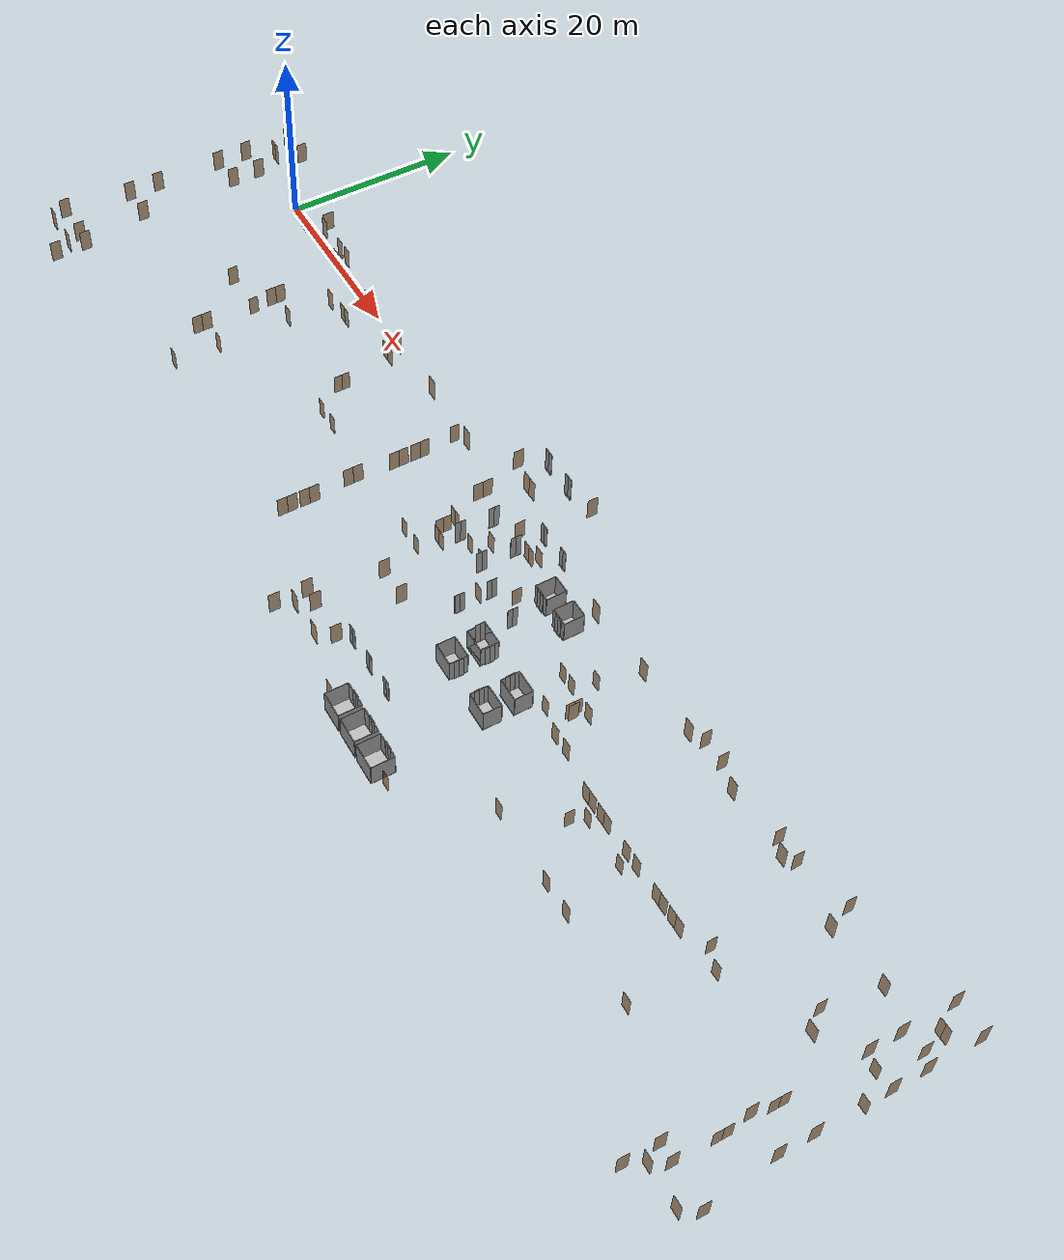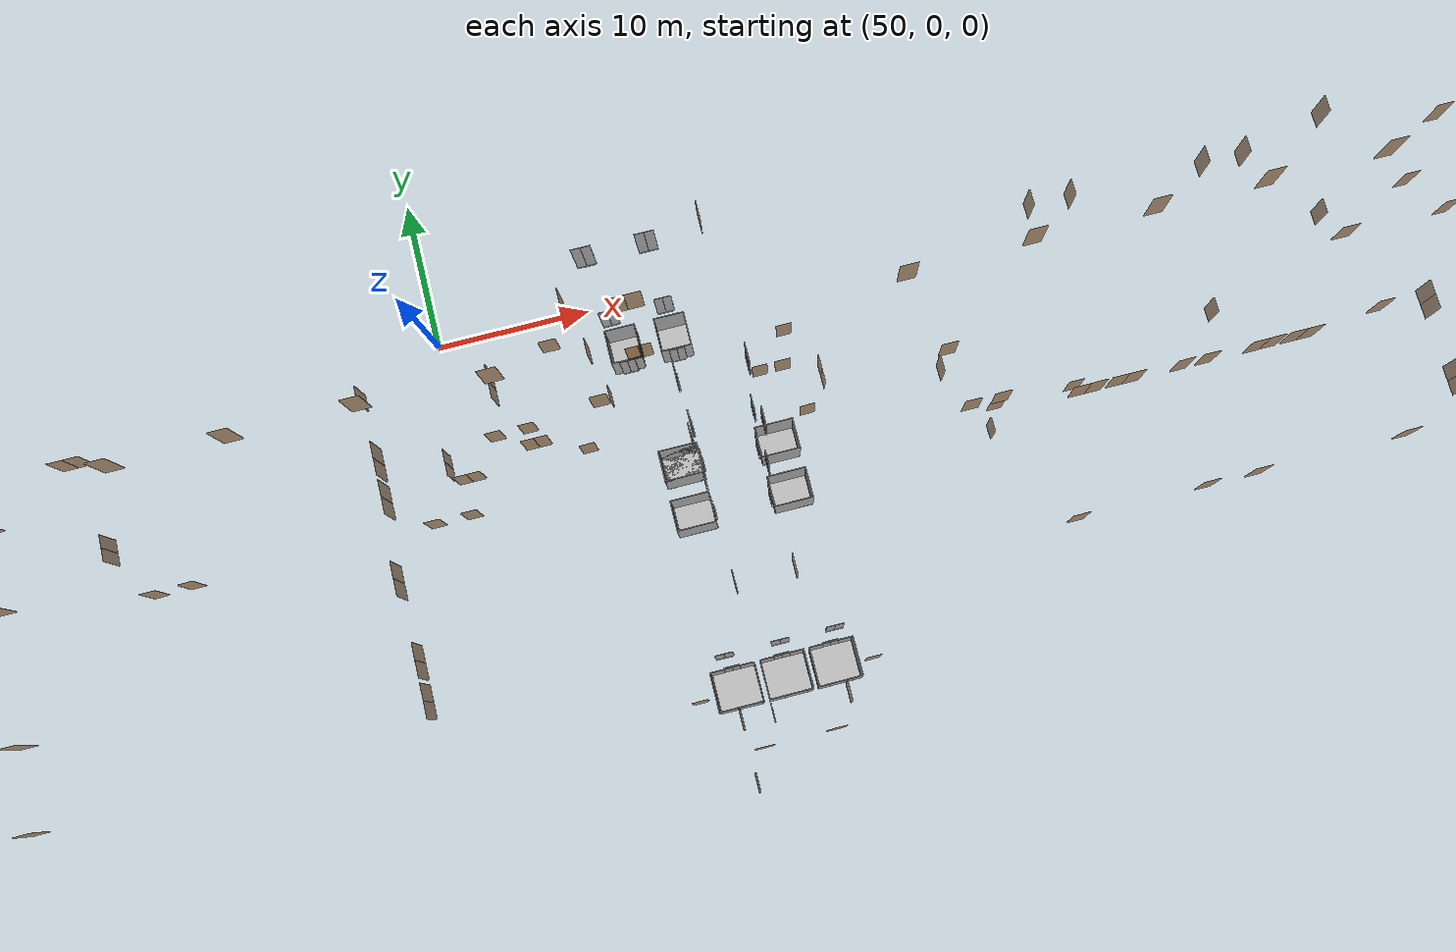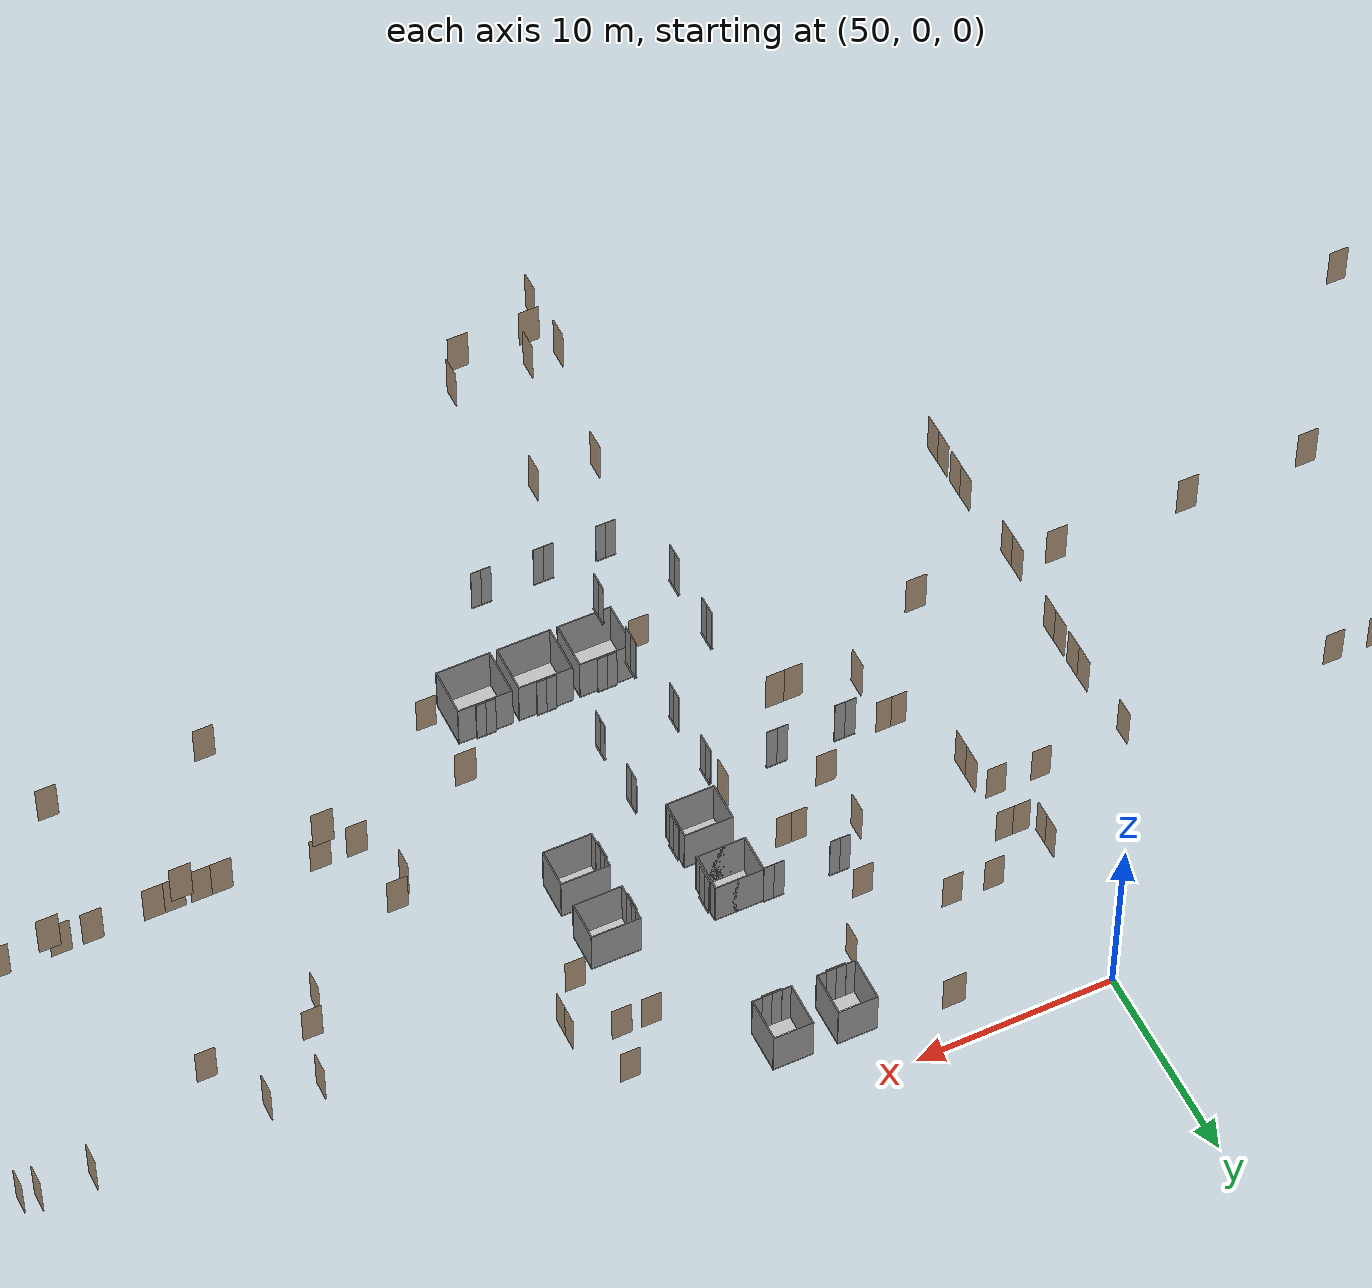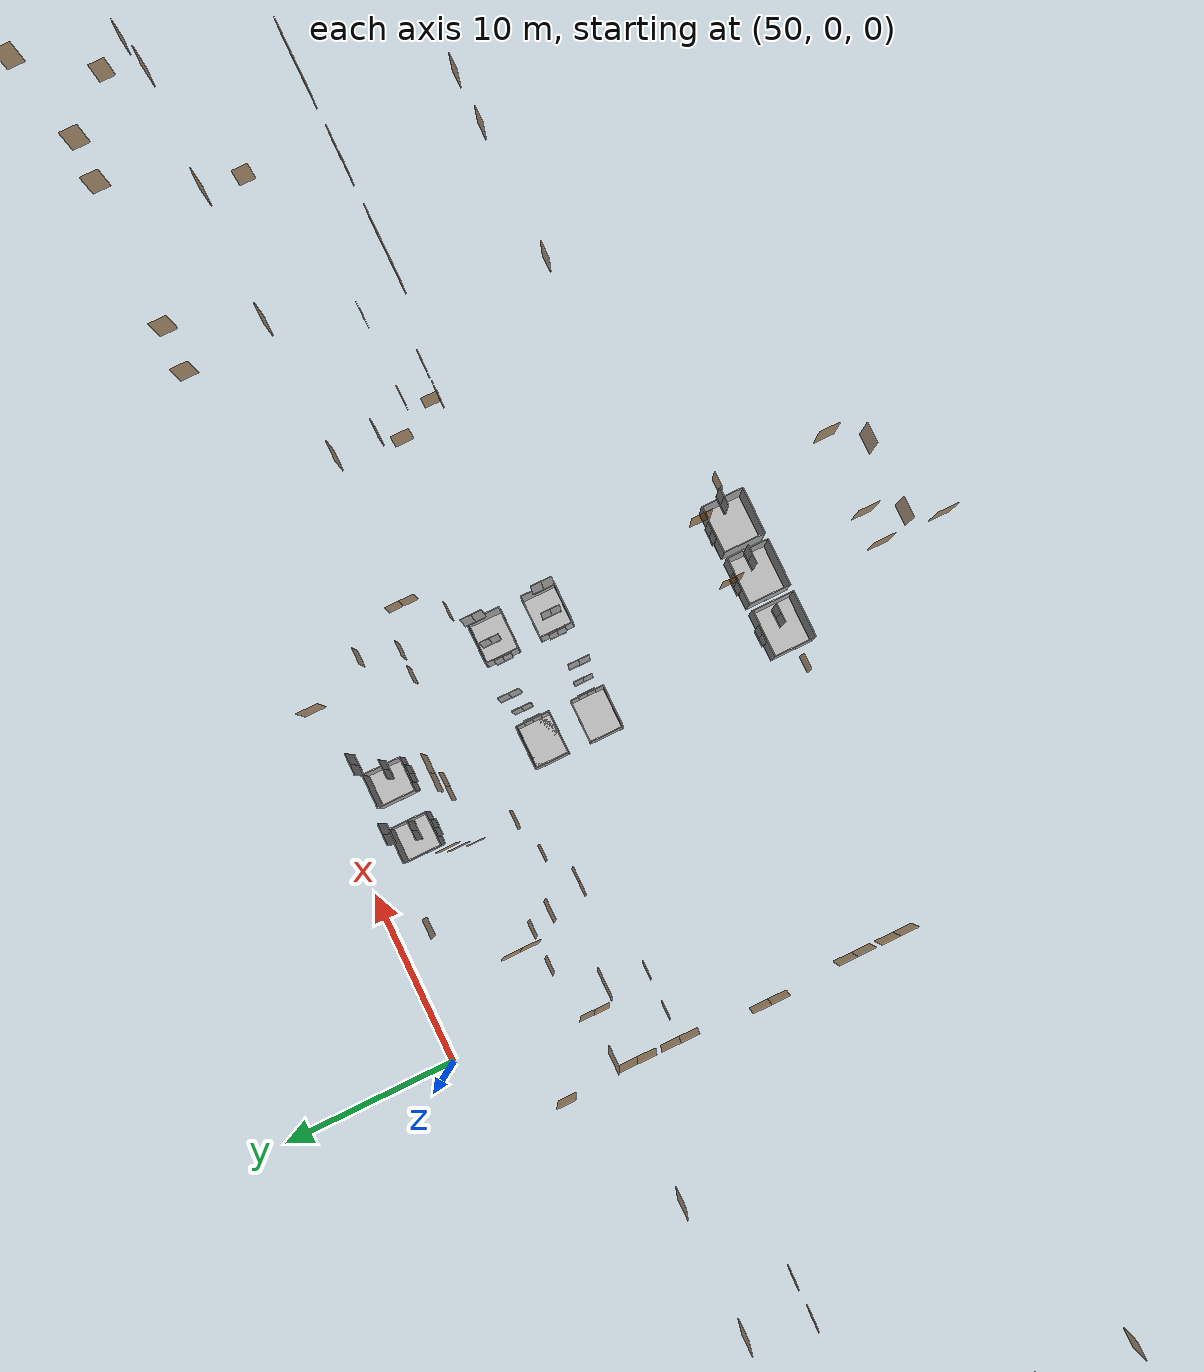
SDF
<sdf version="1.7">
 <world name="sim_world">
  <physics name="10ms" type="ode">
   <max_step_size>0.01</max_step_size>
   <real_time_factor>1.0</real_time_factor>
  </physics>
  <plugin filename="libignition-gazebo-physics-system.so" name="ignition::gazebo::systems::Physics"/>
  <plugin filename="libignition-gazebo-user-commands-system.so" name="ignition::gazebo::systems::UserCommands"/>
  <plugin filename="libignition-gazebo-scene-broadcaster-system.so" name="ignition::gazebo::systems::SceneBroadcaster"/>
  <scene><ambient>1 1 1</ambient><background>0.8 0.8 0.8</background><grid>false</grid></scene>
  <light type="directional" name="sun">
   <pose>0 0 10 0 0 0</pose>
   <diffuse>1 1 1 1</diffuse>
   <specular>0.2 0.2 0.2 1</specular>
   <attenuation>
    <range>1000</range>
    <constant>0.09</constant>
    <linear>0.001</linear>
    <quadratic>0.001</quadratic>
   </attenuation>
   <direction>-0.5 0.1 -0.9</direction>
  </light>
  <model name="l1_door17">
   <pose>27.450000000000003 -8.125 0.0 0 0 -1.5707963267948966</pose>
   <link name="right">
    <pose>-0.4375 0 1.11 0 0 0</pose>
    <visual name="right_visual">
     <geometry><box><size>0.865 0.03 2.2</size></box></geometry>
     <material>
      <ambient>0.5 0.25 0 0.6</ambient>
      <diffuse>0.5 0.25 0 0.6</diffuse>
      <pbr><metal><metalness>0.0</metalness></metal></pbr>
     </material>
    </visual>
    <collision name="right_collision">
     <geometry><box><size>0.865 0.03 2.2</size></box></geometry>
     <surface><contact><collide_bitmask>0x02</collide_bitmask></contact></surface>
    </collision>
    <inertial>
     <mass>50.0</mass>
     <inertia><ixx>20.17041666666667</ixx><iyy>23.284270833333338</iyy><izz>3.121354166666667</izz></inertia>
    </inertial>
   </link>
   <joint name="right_joint" type="revolute">
    <parent>world</parent>
    <child>right</child>
    <axis><xyz>0 0 1</xyz><limit><lower>0</lower><upper>1.57</upper></limit></axis>
    <pose>-0.4375 0 0 0 0 0</pose>
   </joint>
   <link name="left">
    <pose>0.4375 0 1.11 0 0 0</pose>
    <visual name="left_visual">
     <geometry><box><size>0.865 0.03 2.2</size></box></geometry>
     <material>
      <ambient>0.5 0.25 0 0.6</ambient>
      <diffuse>0.5 0.25 0 0.6</diffuse>
      <pbr><metal><metalness>0.0</metalness></metal></pbr>
     </material>
    </visual>
    <collision name="left_collision">
     <geometry><box><size>0.865 0.03 2.2</size></box></geometry>
     <surface><contact><collide_bitmask>0x02</collide_bitmask></contact></surface>
    </collision>
    <inertial>
     <mass>50.0</mass>
     <inertia><ixx>20.17041666666667</ixx><iyy>23.284270833333338</iyy><izz>3.121354166666667</izz></inertia>
    </inertial>
   </link>
   <joint name="left_joint" type="revolute">
    <parent>world</parent>
    <child>left</child>
    <axis><xyz>0 0 1</xyz><limit><lower>-1.57</lower><upper>0</upper></limit></axis>
    <pose>0.4375 0 0 0 0 0</pose>
   </joint>
   <plugin name="door" filename="libdoor.so">
    <v_max_door>0.5</v_max_door>
    <a_max_door>0.3</a_max_door>
    <a_nom_door>0.15</a_nom_door>
    <dx_min_door>0.01</dx_min_door>
    <f_max_door>500.0</f_max_door>
    <door name="l1_door17" type="DoubleSwingDoor" left_joint_name="left_joint" right_joint_name="right_joint"/>
   </plugin>
  </model>
  <model name="l1_door16">
   <pose>49.225 -8.125 0.0 0 0 1.5707963267948966</pose>
   <link name="right">
    <pose>-0.4375 0 1.11 0 0 0</pose>
    <visual name="right_visual">
     <geometry><box><size>0.865 0.03 2.2</size></box></geometry>
     <material>
      <ambient>0.5 0.25 0 0.6</ambient>
      <diffuse>0.5 0.25 0 0.6</diffuse>
      <pbr><metal><metalness>0.0</metalness></metal></pbr>
     </material>
    </visual>
    <collision name="right_collision">
     <geometry><box><size>0.865 0.03 2.2</size></box></geometry>
     <surface><contact><collide_bitmask>0x02</collide_bitmask></contact></surface>
    </collision>
    <inertial>
     <mass>50.0</mass>
     <inertia><ixx>20.17041666666667</ixx><iyy>23.284270833333338</iyy><izz>3.121354166666667</izz></inertia>
    </inertial>
   </link>
   <joint name="right_joint" type="revolute">
    <parent>world</parent>
    <child>right</child>
    <axis><xyz>0 0 1</xyz><limit><lower>0</lower><upper>1.57</upper></limit></axis>
    <pose>-0.4375 0 0 0 0 0</pose>
   </joint>
   <link name="left">
    <pose>0.4375 0 1.11 0 0 0</pose>
    <visual name="left_visual">
     <geometry><box><size>0.865 0.03 2.2</size></box></geometry>
     <material>
      <ambient>0.5 0.25 0 0.6</ambient>
      <diffuse>0.5 0.25 0 0.6</diffuse>
      <pbr><metal><metalness>0.0</metalness></metal></pbr>
     </material>
    </visual>
    <collision name="left_collision">
     <geometry><box><size>0.865 0.03 2.2</size></box></geometry>
     <surface><contact><collide_bitmask>0x02</collide_bitmask></contact></surface>
    </collision>
    <inertial>
     <mass>50.0</mass>
     <inertia><ixx>20.17041666666667</ixx><iyy>23.284270833333338</iyy><izz>3.121354166666667</izz></inertia>
    </inertial>
   </link>
   <joint name="left_joint" type="revolute">
    <parent>world</parent>
    <child>left</child>
    <axis><xyz>0 0 1</xyz><limit><lower>-1.57</lower><upper>0</upper></limit></axis>
    <pose>0.4375 0 0 0 0 0</pose>
   </joint>
   <plugin name="door" filename="libdoor.so">
    <v_max_door>0.5</v_max_door>
    <a_max_door>0.3</a_max_door>
    <a_nom_door>0.15</a_nom_door>
    <dx_min_door>0.01</dx_min_door>
    <f_max_door>500.0</f_max_door>
    <door name="l1_door16" type="DoubleSwingDoor" left_joint_name="left_joint" right_joint_name="right_joint"/>
   </plugin>
  </model>
  <model name="l1_door14">
   <pose>52.5 -7.0 0.0 0 0 3.141592653589793</pose>
   <plugin name="door" filename="libdoor.so">
    <v_max_door>0.5</v_max_door>
    <a_max_door>0.3</a_max_door>
    <a_nom_door>0.15</a_nom_door>
    <dx_min_door>0.01</dx_min_door>
    <f_max_door>500.0</f_max_door>
    <door name="l1_door14" type="SwingDoor" left_joint_name="left_joint" right_joint_name="empty_joint"/>
   </plugin>
   <link name="left">
    <pose>0 0 1.11 0 0 0</pose>
    <visual name="left_visual">
     <geometry><box><size>0.99 0.03 2.2</size></box></geometry>
     <material>
      <ambient>0.5 0.25 0 0.6</ambient>
      <diffuse>0.5 0.25 0 0.6</diffuse>
      <pbr><metal><metalness>0.0</metalness></metal></pbr>
     </material>
    </visual>
    <collision name="left_collision">
     <geometry><box><size>0.99 0.03 2.2</size></box></geometry>
     <surface><contact><collide_bitmask>0x02</collide_bitmask></contact></surface>
    </collision>
    <inertial>
     <mass>50.0</mass>
     <inertia><ixx>20.17041666666667</ixx><iyy>24.250416666666673</iyy><izz>4.0875</izz></inertia>
    </inertial>
   </link>
   <joint name="left_joint" type="revolute">
    <parent>world</parent>
    <child>left</child>
    <axis><xyz>0 0 1</xyz><limit><lower>-1.57</lower><upper>0</upper></limit></axis>
    <pose>0.5 0 0 0 0 0</pose>
   </joint>
  </model>
  <model name="l1_door13">
   <pose>54.650000000000006 -7.0 0.0 0 0 3.141592653589793</pose>
   <plugin name="door" filename="libdoor.so">
    <v_max_door>0.5</v_max_door>
    <a_max_door>0.3</a_max_door>
    <a_nom_door>0.15</a_nom_door>
    <dx_min_door>0.01</dx_min_door>
    <f_max_door>500.0</f_max_door>
    <door name="l1_door13" type="SwingDoor" left_joint_name="empty_joint" right_joint_name="right_joint"/>
   </plugin>
   <link name="right">
    <pose>0 0 1.11 0 0 0</pose>
    <visual name="right_visual">
     <geometry><box><size>0.99 0.03 2.2</size></box></geometry>
     <material>
      <ambient>0.5 0.25 0 0.6</ambient>
      <diffuse>0.5 0.25 0 0.6</diffuse>
      <pbr><metal><metalness>0.0</metalness></metal></pbr>
     </material>
    </visual>
    <collision name="right_collision">
     <geometry><box><size>0.99 0.03 2.2</size></box></geometry>
     <surface><contact><collide_bitmask>0x02</collide_bitmask></contact></surface>
    </collision>
    <inertial>
     <mass>50.0</mass>
     <inertia><ixx>20.17041666666667</ixx><iyy>24.250416666666673</iyy><izz>4.0875</izz></inertia>
    </inertial>
   </link>
   <joint name="right_joint" type="revolute">
    <parent>world</parent>
    <child>right</child>
    <axis><xyz>0 0 1</xyz><limit><lower>0</lower><upper>1.57</upper></limit></axis>
    <pose>0.5 0 0 0 0 0</pose>
   </joint>
  </model>
  <model name="l1_door11">
   <pose>60.2 -6.25 0.0 0 0 -1.5707963267948966</pose>
   <plugin name="door" filename="libdoor.so">
    <v_max_door>0.5</v_max_door>
    <a_max_door>0.3</a_max_door>
    <a_nom_door>0.15</a_nom_door>
    <dx_min_door>0.01</dx_min_door>
    <f_max_door>500.0</f_max_door>
    <door name="l1_door11" type="SwingDoor" left_joint_name="left_joint" right_joint_name="empty_joint"/>
   </plugin>
   <link name="left">
    <pose>0 0 1.11 0 0 0</pose>
    <visual name="left_visual">
     <geometry><box><size>0.99 0.03 2.2</size></box></geometry>
     <material>
      <ambient>0.5 0.25 0 0.6</ambient>
      <diffuse>0.5 0.25 0 0.6</diffuse>
      <pbr><metal><metalness>0.0</metalness></metal></pbr>
     </material>
    </visual>
    <collision name="left_collision">
     <geometry><box><size>0.99 0.03 2.2</size></box></geometry>
     <surface><contact><collide_bitmask>0x02</collide_bitmask></contact></surface>
    </collision>
    <inertial>
     <mass>50.0</mass>
     <inertia><ixx>20.17041666666667</ixx><iyy>24.250416666666673</iyy><izz>4.0875</izz></inertia>
    </inertial>
   </link>
   <joint name="left_joint" type="revolute">
    <parent>world</parent>
    <child>left</child>
    <axis><xyz>0 0 1</xyz><limit><lower>-1.57</lower><upper>0</upper></limit></axis>
    <pose>0.5 0 0 0 0 0</pose>
   </joint>
  </model>
  <model name="l1_door15">
   <pose>50.35 -9.25 0.0 0 0 3.141592653589793</pose>
   <link name="right">
    <pose>-0.4375 0 1.11 0 0 0</pose>
    <visual name="right_visual">
     <geometry><box><size>0.865 0.03 2.2</size></box></geometry>
     <material>
      <ambient>0.5 0.25 0 0.6</ambient>
      <diffuse>0.5 0.25 0 0.6</diffuse>
      <pbr><metal><metalness>0.0</metalness></metal></pbr>
     </material>
    </visual>
    <collision name="right_collision">
     <geometry><box><size>0.865 0.03 2.2</size></box></geometry>
     <surface><contact><collide_bitmask>0x02</collide_bitmask></contact></surface>
    </collision>
    <inertial>
     <mass>50.0</mass>
     <inertia><ixx>20.17041666666667</ixx><iyy>23.284270833333338</iyy><izz>3.121354166666667</izz></inertia>
    </inertial>
   </link>
   <joint name="right_joint" type="revolute">
    <parent>world</parent>
    <child>right</child>
    <axis><xyz>0 0 1</xyz><limit><lower>0</lower><upper>1.57</upper></limit></axis>
    <pose>-0.4375 0 0 0 0 0</pose>
   </joint>
   <link name="left">
    <pose>0.4375 0 1.11 0 0 0</pose>
    <visual name="left_visual">
     <geometry><box><size>0.865 0.03 2.2</size></box></geometry>
     <material>
      <ambient>0.5 0.25 0 0.6</ambient>
      <diffuse>0.5 0.25 0 0.6</diffuse>
      <pbr><metal><metalness>0.0</metalness></metal></pbr>
     </material>
    </visual>
    <collision name="left_collision">
     <geometry><box><size>0.865 0.03 2.2</size></box></geometry>
     <surface><contact><collide_bitmask>0x02</collide_bitmask></contact></surface>
    </collision>
    <inertial>
     <mass>50.0</mass>
     <inertia><ixx>20.17041666666667</ixx><iyy>23.284270833333338</iyy><izz>3.121354166666667</izz></inertia>
    </inertial>
   </link>
   <joint name="left_joint" type="revolute">
    <parent>world</parent>
    <child>left</child>
    <axis><xyz>0 0 1</xyz><limit><lower>-1.57</lower><upper>0</upper></limit></axis>
    <pose>0.4375 0 0 0 0 0</pose>
   </joint>
   <plugin name="door" filename="libdoor.so">
    <v_max_door>0.5</v_max_door>
    <a_max_door>0.3</a_max_door>
    <a_nom_door>0.15</a_nom_door>
    <dx_min_door>0.01</dx_min_door>
    <f_max_door>500.0</f_max_door>
    <door name="l1_door15" type="DoubleSwingDoor" left_joint_name="left_joint" right_joint_name="right_joint"/>
   </plugin>
  </model>
  <model name="dining_4">
   <pose>29.75 -11.600000000000001 0.0 0 0 3.141592653589793</pose>
   <plugin name="door" filename="libdoor.so">
    <v_max_door>0.5</v_max_door>
    <a_max_door>0.3</a_max_door>
    <a_nom_door>0.15</a_nom_door>
    <dx_min_door>0.01</dx_min_door>
    <f_max_door>500.0</f_max_door>
    <door name="dining_4" type="SwingDoor" left_joint_name="left_joint" right_joint_name="empty_joint"/>
   </plugin>
   <link name="left">
    <pose>0 0 1.11 0 0 0</pose>
    <visual name="left_visual">
     <geometry><box><size>0.99 0.03 2.2</size></box></geometry>
     <material>
      <ambient>0.5 0.25 0 0.6</ambient>
      <diffuse>0.5 0.25 0 0.6</diffuse>
      <pbr><metal><metalness>0.0</metalness></metal></pbr>
     </material>
    </visual>
    <collision name="left_collision">
     <geometry><box><size>0.99 0.03 2.2</size></box></geometry>
     <surface><contact><collide_bitmask>0x02</collide_bitmask></contact></surface>
    </collision>
    <inertial>
     <mass>50.0</mass>
     <inertia><ixx>20.17041666666667</ixx><iyy>24.250416666666673</iyy><izz>4.0875</izz></inertia>
    </inertial>
   </link>
   <joint name="left_joint" type="revolute">
    <parent>world</parent>
    <child>left</child>
    <axis><xyz>0 0 1</xyz><limit><lower>-1.57</lower><upper>0</upper></limit></axis>
    <pose>0.5 0 0 0 0 0</pose>
   </joint>
  </model>
  <model name="dining_3">
   <pose>32.1 -11.600000000000001 0.0 0 0 0.0</pose>
   <plugin name="door" filename="libdoor.so">
    <v_max_door>0.5</v_max_door>
    <a_max_door>0.3</a_max_door>
    <a_nom_door>0.15</a_nom_door>
    <dx_min_door>0.01</dx_min_door>
    <f_max_door>500.0</f_max_door>
    <door name="dining_3" type="SwingDoor" left_joint_name="empty_joint" right_joint_name="right_joint"/>
   </plugin>
   <link name="right">
    <pose>0 0 1.11 0 0 0</pose>
    <visual name="right_visual">
     <geometry><box><size>0.99 0.03 2.2</size></box></geometry>
     <material>
      <ambient>0.5 0.25 0 0.6</ambient>
      <diffuse>0.5 0.25 0 0.6</diffuse>
      <pbr><metal><metalness>0.0</metalness></metal></pbr>
     </material>
    </visual>
    <collision name="right_collision">
     <geometry><box><size>0.99 0.03 2.2</size></box></geometry>
     <surface><contact><collide_bitmask>0x02</collide_bitmask></contact></surface>
    </collision>
    <inertial>
     <mass>50.0</mass>
     <inertia><ixx>20.17041666666667</ixx><iyy>24.250416666666673</iyy><izz>4.0875</izz></inertia>
    </inertial>
   </link>
   <joint name="right_joint" type="revolute">
    <parent>world</parent>
    <child>right</child>
    <axis><xyz>0 0 1</xyz><limit><lower>0</lower><upper>1.57</upper></limit></axis>
    <pose>0.5 0 0 0 0 0</pose>
   </joint>
  </model>
  <model name="dining_2">
   <pose>47.650000000000006 -11.600000000000001 0.0 0 0 3.141592653589793</pose>
   <plugin name="door" filename="libdoor.so">
    <v_max_door>0.5</v_max_door>
    <a_max_door>0.3</a_max_door>
    <a_nom_door>0.15</a_nom_door>
    <dx_min_door>0.01</dx_min_door>
    <f_max_door>500.0</f_max_door>
    <door name="dining_2" type="SwingDoor" left_joint_name="left_joint" right_joint_name="empty_joint"/>
   </plugin>
   <link name="left">
    <pose>0 0 1.11 0 0 0</pose>
    <visual name="left_visual">
     <geometry><box><size>0.99 0.03 2.2</size></box></geometry>
     <material>
      <ambient>0.5 0.25 0 0.6</ambient>
      <diffuse>0.5 0.25 0 0.6</diffuse>
      <pbr><metal><metalness>0.0</metalness></metal></pbr>
     </material>
    </visual>
    <collision name="left_collision">
     <geometry><box><size>0.99 0.03 2.2</size></box></geometry>
     <surface><contact><collide_bitmask>0x02</collide_bitmask></contact></surface>
    </collision>
    <inertial>
     <mass>50.0</mass>
     <inertia><ixx>20.17041666666667</ixx><iyy>24.250416666666673</iyy><izz>4.0875</izz></inertia>
    </inertial>
   </link>
   <joint name="left_joint" type="revolute">
    <parent>world</parent>
    <child>left</child>
    <axis><xyz>0 0 1</xyz><limit><lower>-1.57</lower><upper>0</upper></limit></axis>
    <pose>0.5 0 0 0 0 0</pose>
   </joint>
  </model>
  <model name="dining_1">
   <pose>50.0 -11.600000000000001 0.0 0 0 0.0</pose>
   <plugin name="door" filename="libdoor.so">
    <v_max_door>0.5</v_max_door>
    <a_max_door>0.3</a_max_door>
    <a_nom_door>0.15</a_nom_door>
    <dx_min_door>0.01</dx_min_door>
    <f_max_door>500.0</f_max_door>
    <door name="dining_1" type="SwingDoor" left_joint_name="empty_joint" right_joint_name="right_joint"/>
   </plugin>
   <link name="right">
    <pose>0 0 1.11 0 0 0</pose>
    <visual name="right_visual">
     <geometry><box><size>0.99 0.03 2.2</size></box></geometry>
     <material>
      <ambient>0.5 0.25 0 0.6</ambient>
      <diffuse>0.5 0.25 0 0.6</diffuse>
      <pbr><metal><metalness>0.0</metalness></metal></pbr>
     </material>
    </visual>
    <collision name="right_collision">
     <geometry><box><size>0.99 0.03 2.2</size></box></geometry>
     <surface><contact><collide_bitmask>0x02</collide_bitmask></contact></surface>
    </collision>
    <inertial>
     <mass>50.0</mass>
     <inertia><ixx>20.17041666666667</ixx><iyy>24.250416666666673</iyy><izz>4.0875</izz></inertia>
    </inertial>
   </link>
   <joint name="right_joint" type="revolute">
    <parent>world</parent>
    <child>right</child>
    <axis><xyz>0 0 1</xyz><limit><lower>0</lower><upper>1.57</upper></limit></axis>
    <pose>0.5 0 0 0 0 0</pose>
   </joint>
  </model>
  <model name="l1_door12">
   <pose>58.1 -9.25 0.0 0 0 3.141592653589793</pose>
   <plugin name="door" filename="libdoor.so">
    <v_max_door>0.5</v_max_door>
    <a_max_door>0.3</a_max_door>
    <a_nom_door>0.15</a_nom_door>
    <dx_min_door>0.01</dx_min_door>
    <f_max_door>500.0</f_max_door>
    <door name="l1_door12" type="SwingDoor" left_joint_name="left_joint" right_joint_name="empty_joint"/>
   </plugin>
   <link name="left">
    <pose>0 0 1.11 0 0 0</pose>
    <visual name="left_visual">
     <geometry><box><size>0.99 0.03 2.2</size></box></geometry>
     <material>
      <ambient>0.5 0.25 0 0.6</ambient>
      <diffuse>0.5 0.25 0 0.6</diffuse>
      <pbr><metal><metalness>0.0</metalness></metal></pbr>
     </material>
    </visual>
    <collision name="left_collision">
     <geometry><box><size>0.99 0.03 2.2</size></box></geometry>
     <surface><contact><collide_bitmask>0x02</collide_bitmask></contact></surface>
    </collision>
    <inertial>
     <mass>50.0</mass>
     <inertia><ixx>20.17041666666667</ixx><iyy>24.250416666666673</iyy><izz>4.0875</izz></inertia>
    </inertial>
   </link>
   <joint name="left_joint" type="revolute">
    <parent>world</parent>
    <child>left</child>
    <axis><xyz>0 0 1</xyz><limit><lower>-1.57</lower><upper>0</upper></limit></axis>
    <pose>0.5 0 0 0 0 0</pose>
   </joint>
  </model>
  <model name="l1_door10">
   <pose>69.9 -7.0 0.0 0 0 0.0</pose>
   <plugin name="door" filename="libdoor.so">
    <v_max_door>0.5</v_max_door>
    <a_max_door>0.3</a_max_door>
    <a_nom_door>0.15</a_nom_door>
    <dx_min_door>0.01</dx_min_door>
    <f_max_door>500.0</f_max_door>
    <door name="l1_door10" type="SwingDoor" left_joint_name="left_joint" right_joint_name="empty_joint"/>
   </plugin>
   <link name="left">
    <pose>0 0 1.11 0 0 0</pose>
    <visual name="left_visual">
     <geometry><box><size>0.99 0.03 2.2</size></box></geometry>
     <material>
      <ambient>0.5 0.25 0 0.6</ambient>
      <diffuse>0.5 0.25 0 0.6</diffuse>
      <pbr><metal><metalness>0.0</metalness></metal></pbr>
     </material>
    </visual>
    <collision name="left_collision">
     <geometry><box><size>0.99 0.03 2.2</size></box></geometry>
     <surface><contact><collide_bitmask>0x02</collide_bitmask></contact></surface>
    </collision>
    <inertial>
     <mass>50.0</mass>
     <inertia><ixx>20.17041666666667</ixx><iyy>24.250416666666673</iyy><izz>4.0875</izz></inertia>
    </inertial>
   </link>
   <joint name="left_joint" type="revolute">
    <parent>world</parent>
    <child>left</child>
    <axis><xyz>0 0 1</xyz><limit><lower>-1.57</lower><upper>0</upper></limit></axis>
    <pose>0.5 0 0 0 0 0</pose>
   </joint>
  </model>
  <model name="l1_door9">
   <pose>72.05 -4.75 0.0 0 0 0.0</pose>
   <plugin name="door" filename="libdoor.so">
    <v_max_door>0.5</v_max_door>
    <a_max_door>0.3</a_max_door>
    <a_nom_door>0.15</a_nom_door>
    <dx_min_door>0.01</dx_min_door>
    <f_max_door>500.0</f_max_door>
    <door name="l1_door9" type="SwingDoor" left_joint_name="left_joint" right_joint_name="empty_joint"/>
   </plugin>
   <link name="left">
    <pose>0 0 1.11 0 0 0</pose>
    <visual name="left_visual">
     <geometry><box><size>0.99 0.03 2.2</size></box></geometry>
     <material>
      <ambient>0.5 0.25 0 0.6</ambient>
      <diffuse>0.5 0.25 0 0.6</diffuse>
      <pbr><metal><metalness>0.0</metalness></metal></pbr>
     </material>
    </visual>
    <collision name="left_collision">
     <geometry><box><size>0.99 0.03 2.2</size></box></geometry>
     <surface><contact><collide_bitmask>0x02</collide_bitmask></contact></surface>
    </collision>
    <inertial>
     <mass>50.0</mass>
     <inertia><ixx>20.17041666666667</ixx><iyy>24.250416666666673</iyy><izz>4.0875</izz></inertia>
    </inertial>
   </link>
   <joint name="left_joint" type="revolute">
    <parent>world</parent>
    <child>left</child>
    <axis><xyz>0 0 1</xyz><limit><lower>-1.57</lower><upper>0</upper></limit></axis>
    <pose>0.5 0 0 0 0 0</pose>
   </joint>
  </model>
  <model name="l1_door8">
   <pose>71.4 -7.0 0.0 0 0 3.141592653589793</pose>
   <plugin name="door" filename="libdoor.so">
    <v_max_door>0.5</v_max_door>
    <a_max_door>0.3</a_max_door>
    <a_nom_door>0.15</a_nom_door>
    <dx_min_door>0.01</dx_min_door>
    <f_max_door>500.0</f_max_door>
    <door name="l1_door8" type="SwingDoor" left_joint_name="empty_joint" right_joint_name="right_joint"/>
   </plugin>
   <link name="right">
    <pose>0 0 1.11 0 0 0</pose>
    <visual name="right_visual">
     <geometry><box><size>0.99 0.03 2.2</size></box></geometry>
     <material>
      <ambient>0.5 0.25 0 0.6</ambient>
      <diffuse>0.5 0.25 0 0.6</diffuse>
      <pbr><metal><metalness>0.0</metalness></metal></pbr>
     </material>
    </visual>
    <collision name="right_collision">
     <geometry><box><size>0.99 0.03 2.2</size></box></geometry>
     <surface><contact><collide_bitmask>0x02</collide_bitmask></contact></surface>
    </collision>
    <inertial>
     <mass>50.0</mass>
     <inertia><ixx>20.17041666666667</ixx><iyy>24.250416666666673</iyy><izz>4.0875</izz></inertia>
    </inertial>
   </link>
   <joint name="right_joint" type="revolute">
    <parent>world</parent>
    <child>right</child>
    <axis><xyz>0 0 1</xyz><limit><lower>0</lower><upper>1.57</upper></limit></axis>
    <pose>0.5 0 0 0 0 0</pose>
   </joint>
  </model>
  <model name="l1_door6">
   <pose>72.2 -10.25 0.0 0 0 3.141592653589793</pose>
   <plugin name="door" filename="libdoor.so">
    <v_max_door>0.5</v_max_door>
    <a_max_door>0.3</a_max_door>
    <a_nom_door>0.15</a_nom_door>
    <dx_min_door>0.01</dx_min_door>
    <f_max_door>500.0</f_max_door>
    <door name="l1_door6" type="SwingDoor" left_joint_name="empty_joint" right_joint_name="right_joint"/>
   </plugin>
   <link name="right">
    <pose>0 0 1.11 0 0 0</pose>
    <visual name="right_visual">
     <geometry><box><size>0.99 0.03 2.2</size></box></geometry>
     <material>
      <ambient>0.5 0.25 0 0.6</ambient>
      <diffuse>0.5 0.25 0 0.6</diffuse>
      <pbr><metal><metalness>0.0</metalness></metal></pbr>
     </material>
    </visual>
    <collision name="right_collision">
     <geometry><box><size>0.99 0.03 2.2</size></box></geometry>
     <surface><contact><collide_bitmask>0x02</collide_bitmask></contact></surface>
    </collision>
    <inertial>
     <mass>50.0</mass>
     <inertia><ixx>20.17041666666667</ixx><iyy>24.250416666666673</iyy><izz>4.0875</izz></inertia>
    </inertial>
   </link>
   <joint name="right_joint" type="revolute">
    <parent>world</parent>
    <child>right</child>
    <axis><xyz>0 0 1</xyz><limit><lower>0</lower><upper>1.57</upper></limit></axis>
    <pose>0.5 0 0 0 0 0</pose>
   </joint>
  </model>
  <model name="l1_door7">
   <pose>73.7 -8.125 0.0 0 0 -1.5707963267948966</pose>
   <link name="right">
    <pose>-0.4375 0 1.11 0 0 0</pose>
    <visual name="right_visual">
     <geometry><box><size>0.865 0.03 2.2</size></box></geometry>
     <material>
      <ambient>0.5 0.25 0 0.6</ambient>
      <diffuse>0.5 0.25 0 0.6</diffuse>
      <pbr><metal><metalness>0.0</metalness></metal></pbr>
     </material>
    </visual>
    <collision name="right_collision">
     <geometry><box><size>0.865 0.03 2.2</size></box></geometry>
     <surface><contact><collide_bitmask>0x02</collide_bitmask></contact></surface>
    </collision>
    <inertial>
     <mass>50.0</mass>
     <inertia><ixx>20.17041666666667</ixx><iyy>23.284270833333338</iyy><izz>3.121354166666667</izz></inertia>
    </inertial>
   </link>
   <joint name="right_joint" type="revolute">
    <parent>world</parent>
    <child>right</child>
    <axis><xyz>0 0 1</xyz><limit><lower>0</lower><upper>1.57</upper></limit></axis>
    <pose>-0.4375 0 0 0 0 0</pose>
   </joint>
   <link name="left">
    <pose>0.4375 0 1.11 0 0 0</pose>
    <visual name="left_visual">
     <geometry><box><size>0.865 0.03 2.2</size></box></geometry>
     <material>
      <ambient>0.5 0.25 0 0.6</ambient>
      <diffuse>0.5 0.25 0 0.6</diffuse>
      <pbr><metal><metalness>0.0</metalness></metal></pbr>
     </material>
    </visual>
    <collision name="left_collision">
     <geometry><box><size>0.865 0.03 2.2</size></box></geometry>
     <surface><contact><collide_bitmask>0x02</collide_bitmask></contact></surface>
    </collision>
    <inertial>
     <mass>50.0</mass>
     <inertia><ixx>20.17041666666667</ixx><iyy>23.284270833333338</iyy><izz>3.121354166666667</izz></inertia>
    </inertial>
   </link>
   <joint name="left_joint" type="revolute">
    <parent>world</parent>
    <child>left</child>
    <axis><xyz>0 0 1</xyz><limit><lower>-1.57</lower><upper>0</upper></limit></axis>
    <pose>0.4375 0 0 0 0 0</pose>
   </joint>
   <plugin name="door" filename="libdoor.so">
    <v_max_door>0.5</v_max_door>
    <a_max_door>0.3</a_max_door>
    <a_nom_door>0.15</a_nom_door>
    <dx_min_door>0.01</dx_min_door>
    <f_max_door>500.0</f_max_door>
    <door name="l1_door7" type="DoubleSwingDoor" left_joint_name="left_joint" right_joint_name="right_joint"/>
   </plugin>
  </model>
  <model name="l1_door4">
   <pose>108.2 -5.75 0.0 0 0 1.5707963267948966</pose>
   <plugin name="door" filename="libdoor.so">
    <v_max_door>0.5</v_max_door>
    <a_max_door>0.3</a_max_door>
    <a_nom_door>0.15</a_nom_door>
    <dx_min_door>0.01</dx_min_door>
    <f_max_door>500.0</f_max_door>
    <door name="l1_door4" type="SwingDoor" left_joint_name="left_joint" right_joint_name="empty_joint"/>
   </plugin>
   <link name="left">
    <pose>0 0 1.11 0 0 0</pose>
    <visual name="left_visual">
     <geometry><box><size>0.99 0.03 2.2</size></box></geometry>
     <material>
      <ambient>0.5 0.25 0 0.6</ambient>
      <diffuse>0.5 0.25 0 0.6</diffuse>
      <pbr><metal><metalness>0.0</metalness></metal></pbr>
     </material>
    </visual>
    <collision name="left_collision">
     <geometry><box><size>0.99 0.03 2.2</size></box></geometry>
     <surface><contact><collide_bitmask>0x02</collide_bitmask></contact></surface>
    </collision>
    <inertial>
     <mass>50.0</mass>
     <inertia><ixx>20.17041666666667</ixx><iyy>24.250416666666673</iyy><izz>4.0875</izz></inertia>
    </inertial>
   </link>
   <joint name="left_joint" type="revolute">
    <parent>world</parent>
    <child>left</child>
    <axis><xyz>0 0 1</xyz><limit><lower>-1.57</lower><upper>0</upper></limit></axis>
    <pose>0.5 0 0 0 0 0</pose>
   </joint>
  </model>
  <model name="l1_door1">
   <pose>116.45 -7.5 0.0 0 0 3.141592653589793</pose>
   <plugin name="door" filename="libdoor.so">
    <v_max_door>0.5</v_max_door>
    <a_max_door>0.3</a_max_door>
    <a_nom_door>0.15</a_nom_door>
    <dx_min_door>0.01</dx_min_door>
    <f_max_door>500.0</f_max_door>
    <door name="l1_door1" type="SwingDoor" left_joint_name="empty_joint" right_joint_name="right_joint"/>
   </plugin>
   <link name="right">
    <pose>0 0 1.11 0 0 0</pose>
    <visual name="right_visual">
     <geometry><box><size>0.99 0.03 2.2</size></box></geometry>
     <material>
      <ambient>0.5 0.25 0 0.6</ambient>
      <diffuse>0.5 0.25 0 0.6</diffuse>
      <pbr><metal><metalness>0.0</metalness></metal></pbr>
     </material>
    </visual>
    <collision name="right_collision">
     <geometry><box><size>0.99 0.03 2.2</size></box></geometry>
     <surface><contact><collide_bitmask>0x02</collide_bitmask></contact></surface>
    </collision>
    <inertial>
     <mass>50.0</mass>
     <inertia><ixx>20.17041666666667</ixx><iyy>24.250416666666673</iyy><izz>4.0875</izz></inertia>
    </inertial>
   </link>
   <joint name="right_joint" type="revolute">
    <parent>world</parent>
    <child>right</child>
    <axis><xyz>0 0 1</xyz><limit><lower>0</lower><upper>1.57</upper></limit></axis>
    <pose>0.5 0 0 0 0 0</pose>
   </joint>
  </model>
  <model name="l1_door2">
   <pose>114.55000000000001 -5.0 0.0 0 0 3.141592653589793</pose>
   <plugin name="door" filename="libdoor.so">
    <v_max_door>0.5</v_max_door>
    <a_max_door>0.3</a_max_door>
    <a_nom_door>0.15</a_nom_door>
    <dx_min_door>0.01</dx_min_door>
    <f_max_door>500.0</f_max_door>
    <door name="l1_door2" type="SwingDoor" left_joint_name="empty_joint" right_joint_name="right_joint"/>
   </plugin>
   <link name="right">
    <pose>0 0 1.11 0 0 0</pose>
    <visual name="right_visual">
     <geometry><box><size>0.99 0.03 2.2</size></box></geometry>
     <material>
      <ambient>0.5 0.25 0 0.6</ambient>
      <diffuse>0.5 0.25 0 0.6</diffuse>
      <pbr><metal><metalness>0.0</metalness></metal></pbr>
     </material>
    </visual>
    <collision name="right_collision">
     <geometry><box><size>0.99 0.03 2.2</size></box></geometry>
     <surface><contact><collide_bitmask>0x02</collide_bitmask></contact></surface>
    </collision>
    <inertial>
     <mass>50.0</mass>
     <inertia><ixx>20.17041666666667</ixx><iyy>24.250416666666673</iyy><izz>4.0875</izz></inertia>
    </inertial>
   </link>
   <joint name="right_joint" type="revolute">
    <parent>world</parent>
    <child>right</child>
    <axis><xyz>0 0 1</xyz><limit><lower>0</lower><upper>1.57</upper></limit></axis>
    <pose>0.5 0 0 0 0 0</pose>
   </joint>
  </model>
  <model name="terrace">
   <pose>12.75 -11.25 0.0 0 0 1.5707963267948966</pose>
   <plugin name="door" filename="libdoor.so">
    <v_max_door>0.5</v_max_door>
    <a_max_door>0.3</a_max_door>
    <a_nom_door>0.15</a_nom_door>
    <dx_min_door>0.01</dx_min_door>
    <f_max_door>500.0</f_max_door>
    <door name="terrace" type="SwingDoor" left_joint_name="left_joint" right_joint_name="empty_joint"/>
   </plugin>
   <link name="left">
    <pose>0 0 1.11 0 0 0</pose>
    <visual name="left_visual">
     <geometry><box><size>0.99 0.03 2.2</size></box></geometry>
     <material>
      <ambient>0.5 0.25 0 0.6</ambient>
      <diffuse>0.5 0.25 0 0.6</diffuse>
      <pbr><metal><metalness>0.0</metalness></metal></pbr>
     </material>
    </visual>
    <collision name="left_collision">
     <geometry><box><size>0.99 0.03 2.2</size></box></geometry>
     <surface><contact><collide_bitmask>0x02</collide_bitmask></contact></surface>
    </collision>
    <inertial>
     <mass>50.0</mass>
     <inertia><ixx>20.17041666666667</ixx><iyy>24.250416666666673</iyy><izz>4.0875</izz></inertia>
    </inertial>
   </link>
   <joint name="left_joint" type="revolute">
    <parent>world</parent>
    <child>left</child>
    <axis><xyz>0 0 1</xyz><limit><lower>-1.57</lower><upper>0</upper></limit></axis>
    <pose>0.5 0 0 0 0 0</pose>
   </joint>
  </model>
  <model name="exit_2">
   <pose>61.2 -26.6 0.0 0 0 0.0</pose>
   <plugin name="door" filename="libdoor.so">
    <v_max_door>0.5</v_max_door>
    <a_max_door>0.3</a_max_door>
    <a_nom_door>0.15</a_nom_door>
    <dx_min_door>0.01</dx_min_door>
    <f_max_door>500.0</f_max_door>
    <door name="exit_2" type="SwingDoor" left_joint_name="empty_joint" right_joint_name="right_joint"/>
   </plugin>
   <link name="right">
    <pose>0 0 1.11 0 0 0</pose>
    <visual name="right_visual">
     <geometry><box><size>0.99 0.03 2.2</size></box></geometry>
     <material>
      <ambient>0.5 0.25 0 0.6</ambient>
      <diffuse>0.5 0.25 0 0.6</diffuse>
      <pbr><metal><metalness>0.0</metalness></metal></pbr>
     </material>
    </visual>
    <collision name="right_collision">
     <geometry><box><size>0.99 0.03 2.2</size></box></geometry>
     <surface><contact><collide_bitmask>0x02</collide_bitmask></contact></surface>
    </collision>
    <inertial>
     <mass>50.0</mass>
     <inertia><ixx>20.17041666666667</ixx><iyy>24.250416666666673</iyy><izz>4.0875</izz></inertia>
    </inertial>
   </link>
   <joint name="right_joint" type="revolute">
    <parent>world</parent>
    <child>right</child>
    <axis><xyz>0 0 1</xyz><limit><lower>0</lower><upper>1.57</upper></limit></axis>
    <pose>0.5 0 0 0 0 0</pose>
   </joint>
  </model>
  <model name="l1_door3">
   <pose>109.47500000000001 -7.5 0.0 0 0 0.0</pose>
   <plugin name="door" filename="libdoor.so">
    <v_max_door>0.5</v_max_door>
    <a_max_door>0.3</a_max_door>
    <a_nom_door>0.15</a_nom_door>
    <dx_min_door>0.01</dx_min_door>
    <f_max_door>500.0</f_max_door>
    <door name="l1_door3" type="SwingDoor" left_joint_name="left_joint" right_joint_name="empty_joint"/>
   </plugin>
   <link name="left">
    <pose>0 0 1.11 0 0 0</pose>
    <visual name="left_visual">
     <geometry><box><size>1.24 0.03 2.2</size></box></geometry>
     <material>
      <ambient>0.5 0.25 0 0.6</ambient>
      <diffuse>0.5 0.25 0 0.6</diffuse>
      <pbr><metal><metalness>0.0</metalness></metal></pbr>
     </material>
    </visual>
    <collision name="left_collision">
     <geometry><box><size>1.24 0.03 2.2</size></box></geometry>
     <surface><contact><collide_bitmask>0x02</collide_bitmask></contact></surface>
    </collision>
    <inertial>
     <mass>50.0</mass>
     <inertia><ixx>20.17041666666667</ixx><iyy>26.57333333333334</iyy><izz>6.410416666666667</izz></inertia>
    </inertial>
   </link>
   <joint name="left_joint" type="revolute">
    <parent>world</parent>
    <child>left</child>
    <axis><xyz>0 0 1</xyz><limit><lower>-1.57</lower><upper>0</upper></limit></axis>
    <pose>0.625 0 0 0 0 0</pose>
   </joint>
  </model>
  <model name="entrance_2">
   <pose>113.15 -13.25 0.0 0 0 1.5707963267948966</pose>
   <link name="left">
    <pose>-0.5 0 1.11 0 0 0</pose>
    <visual name="left_visual">
     <geometry><box><size>0.99 0.03 2.2</size></box></geometry>
     <material>
      <ambient>0.5 0.25 0 0.6</ambient>
      <diffuse>0.5 0.25 0 0.6</diffuse>
      <pbr><metal><metalness>0.0</metalness></metal></pbr>
     </material>
    </visual>
    <collision name="left_collision">
     <geometry><box><size>0.99 0.03 2.2</size></box></geometry>
     <surface><contact><collide_bitmask>0x02</collide_bitmask></contact></surface>
    </collision>
    <inertial>
     <mass>50.0</mass>
     <inertia><ixx>20.17041666666667</ixx><iyy>24.250416666666673</iyy><izz>4.0875</izz></inertia>
    </inertial>
   </link>
   <joint name="left_joint" type="prismatic">
    <parent>world</parent>
    <child>left</child>
    <axis><xyz>1 0 0</xyz><limit><lower>-1.0</lower><upper>0.0</upper><effort>500.0</effort></limit></axis>
   </joint>
   <link name="right">
    <pose>0.5 0 1.11 0 0 0</pose>
    <visual name="right_visual">
     <geometry><box><size>0.99 0.03 2.2</size></box></geometry>
     <material>
      <ambient>0.5 0.25 0 0.6</ambient>
      <diffuse>0.5 0.25 0 0.6</diffuse>
      <pbr><metal><metalness>0.0</metalness></metal></pbr>
     </material>
    </visual>
    <collision name="right_collision">
     <geometry><box><size>0.99 0.03 2.2</size></box></geometry>
     <surface><contact><collide_bitmask>0x02</collide_bitmask></contact></surface>
    </collision>
    <inertial>
     <mass>50.0</mass>
     <inertia><ixx>20.17041666666667</ixx><iyy>24.250416666666673</iyy><izz>4.0875</izz></inertia>
    </inertial>
   </link>
   <joint name="right_joint" type="prismatic">
    <parent>world</parent>
    <child>right</child>
    <axis><xyz>1 0 0</xyz><limit><lower>0.0</lower><upper>1.0</upper><effort>500.0</effort></limit></axis>
   </joint>
   <plugin name="door" filename="libdoor.so">
    <v_max_door>0.2</v_max_door>
    <a_max_door>0.2</a_max_door>
    <a_nom_door>0.08</a_nom_door>
    <dx_min_door>0.001</dx_min_door>
    <f_max_door>100.0</f_max_door>
    <door name="entrance_2" type="DoubleSlidingDoor" left_joint_name="left_joint" right_joint_name="right_joint"/>
   </plugin>
  </model>
  <model name="entrance_1">
   <pose>113.15 -18.6 0.0 0 0 1.5707963267948966</pose>
   <link name="left">
    <pose>-0.5 0 1.11 0 0 0</pose>
    <visual name="left_visual">
     <geometry><box><size>0.99 0.03 2.2</size></box></geometry>
     <material>
      <ambient>0.5 0.25 0 0.6</ambient>
      <diffuse>0.5 0.25 0 0.6</diffuse>
      <pbr><metal><metalness>0.0</metalness></metal></pbr>
     </material>
    </visual>
    <collision name="left_collision">
     <geometry><box><size>0.99 0.03 2.2</size></box></geometry>
     <surface><contact><collide_bitmask>0x02</collide_bitmask></contact></surface>
    </collision>
    <inertial>
     <mass>50.0</mass>
     <inertia><ixx>20.17041666666667</ixx><iyy>24.250416666666673</iyy><izz>4.0875</izz></inertia>
    </inertial>
   </link>
   <joint name="left_joint" type="prismatic">
    <parent>world</parent>
    <child>left</child>
    <axis><xyz>1 0 0</xyz><limit><lower>-1.0</lower><upper>0.0</upper><effort>500.0</effort></limit></axis>
   </joint>
   <link name="right">
    <pose>0.5 0 1.11 0 0 0</pose>
    <visual name="right_visual">
     <geometry><box><size>0.99 0.03 2.2</size></box></geometry>
     <material>
      <ambient>0.5 0.25 0 0.6</ambient>
      <diffuse>0.5 0.25 0 0.6</diffuse>
      <pbr><metal><metalness>0.0</metalness></metal></pbr>
     </material>
    </visual>
    <collision name="right_collision">
     <geometry><box><size>0.99 0.03 2.2</size></box></geometry>
     <surface><contact><collide_bitmask>0x02</collide_bitmask></contact></surface>
    </collision>
    <inertial>
     <mass>50.0</mass>
     <inertia><ixx>20.17041666666667</ixx><iyy>24.250416666666673</iyy><izz>4.0875</izz></inertia>
    </inertial>
   </link>
   <joint name="right_joint" type="prismatic">
    <parent>world</parent>
    <child>right</child>
    <axis><xyz>1 0 0</xyz><limit><lower>0.0</lower><upper>1.0</upper><effort>500.0</effort></limit></axis>
   </joint>
   <plugin name="door" filename="libdoor.so">
    <v_max_door>0.2</v_max_door>
    <a_max_door>0.2</a_max_door>
    <a_nom_door>0.08</a_nom_door>
    <dx_min_door>0.001</dx_min_door>
    <f_max_door>100.0</f_max_door>
    <door name="entrance_1" type="DoubleSlidingDoor" left_joint_name="left_joint" right_joint_name="right_joint"/>
   </plugin>
  </model>
  <model name="exit_1">
   <pose>72.2 -26.6 0.0 0 0 3.141592653589793</pose>
   <plugin name="door" filename="libdoor.so">
    <v_max_door>0.5</v_max_door>
    <a_max_door>0.3</a_max_door>
    <a_nom_door>0.15</a_nom_door>
    <dx_min_door>0.01</dx_min_door>
    <f_max_door>500.0</f_max_door>
    <door name="exit_1" type="SwingDoor" left_joint_name="left_joint" right_joint_name="empty_joint"/>
   </plugin>
   <link name="left">
    <pose>0 0 1.11 0 0 0</pose>
    <visual name="left_visual">
     <geometry><box><size>0.99 0.03 2.2</size></box></geometry>
     <material>
      <ambient>0.5 0.25 0 0.6</ambient>
      <diffuse>0.5 0.25 0 0.6</diffuse>
      <pbr><metal><metalness>0.0</metalness></metal></pbr>
     </material>
    </visual>
    <collision name="left_collision">
     <geometry><box><size>0.99 0.03 2.2</size></box></geometry>
     <surface><contact><collide_bitmask>0x02</collide_bitmask></contact></surface>
    </collision>
    <inertial>
     <mass>50.0</mass>
     <inertia><ixx>20.17041666666667</ixx><iyy>24.250416666666673</iyy><izz>4.0875</izz></inertia>
    </inertial>
   </link>
   <joint name="left_joint" type="revolute">
    <parent>world</parent>
    <child>left</child>
    <axis><xyz>0 0 1</xyz><limit><lower>-1.57</lower><upper>0</upper></limit></axis>
    <pose>0.5 0 0 0 0 0</pose>
   </joint>
  </model>
  <model name="l1_door19">
   <pose>18.775000000000002 -3.4000000000000004 0.0 0 0 3.141592653589793</pose>
   <link name="right">
    <pose>0.4375 0 1.11 0 0 0</pose>
    <visual name="right_visual">
     <geometry><box><size>0.865 0.03 2.2</size></box></geometry>
     <material>
      <ambient>0.5 0.25 0 0.6</ambient>
      <diffuse>0.5 0.25 0 0.6</diffuse>
      <pbr><metal><metalness>0.0</metalness></metal></pbr>
     </material>
    </visual>
    <collision name="right_collision">
     <geometry><box><size>0.865 0.03 2.2</size></box></geometry>
     <surface><contact><collide_bitmask>0x02</collide_bitmask></contact></surface>
    </collision>
    <inertial>
     <mass>50.0</mass>
     <inertia><ixx>20.17041666666667</ixx><iyy>23.284270833333338</iyy><izz>3.121354166666667</izz></inertia>
    </inertial>
   </link>
   <joint name="right_joint" type="revolute">
    <parent>world</parent>
    <child>right</child>
    <axis><xyz>0 0 1</xyz><limit><lower>0</lower><upper>1.57</upper></limit></axis>
    <pose>0.4375 0 0 0 0 0</pose>
   </joint>
   <link name="left">
    <pose>-0.4375 0 1.11 0 0 0</pose>
    <visual name="left_visual">
     <geometry><box><size>0.865 0.03 2.2</size></box></geometry>
     <material>
      <ambient>0.5 0.25 0 0.6</ambient>
      <diffuse>0.5 0.25 0 0.6</diffuse>
      <pbr><metal><metalness>0.0</metalness></metal></pbr>
     </material>
    </visual>
    <collision name="left_collision">
     <geometry><box><size>0.865 0.03 2.2</size></box></geometry>
     <surface><contact><collide_bitmask>0x02</collide_bitmask></contact></surface>
    </collision>
    <inertial>
     <mass>50.0</mass>
     <inertia><ixx>20.17041666666667</ixx><iyy>23.284270833333338</iyy><izz>3.121354166666667</izz></inertia>
    </inertial>
   </link>
   <joint name="left_joint" type="revolute">
    <parent>world</parent>
    <child>left</child>
    <axis><xyz>0 0 1</xyz><limit><lower>-1.57</lower><upper>0</upper></limit></axis>
    <pose>-0.4375 0 0 0 0 0</pose>
   </joint>
   <plugin name="door" filename="libdoor.so">
    <v_max_door>0.5</v_max_door>
    <a_max_door>0.3</a_max_door>
    <a_nom_door>0.15</a_nom_door>
    <dx_min_door>0.01</dx_min_door>
    <f_max_door>500.0</f_max_door>
    <door name="l1_door19" type="DoubleSwingDoor" left_joint_name="left_joint" right_joint_name="right_joint"/>
   </plugin>
  </model>
  <model name="l1_door18">
   <pose>25.950000000000003 -2.0 0.0 0 0 3.141592653589793</pose>
   <link name="right">
    <pose>0.5 0 1.11 0 0 0</pose>
    <visual name="right_visual">
     <geometry><box><size>0.99 0.03 2.2</size></box></geometry>
     <material>
      <ambient>0.5 0.25 0 0.6</ambient>
      <diffuse>0.5 0.25 0 0.6</diffuse>
      <pbr><metal><metalness>0.0</metalness></metal></pbr>
     </material>
    </visual>
    <collision name="right_collision">
     <geometry><box><size>0.99 0.03 2.2</size></box></geometry>
     <surface><contact><collide_bitmask>0x02</collide_bitmask></contact></surface>
    </collision>
    <inertial>
     <mass>50.0</mass>
     <inertia><ixx>20.17041666666667</ixx><iyy>24.250416666666673</iyy><izz>4.0875</izz></inertia>
    </inertial>
   </link>
   <joint name="right_joint" type="revolute">
    <parent>world</parent>
    <child>right</child>
    <axis><xyz>0 0 1</xyz><limit><lower>0</lower><upper>1.57</upper></limit></axis>
    <pose>0.5 0 0 0 0 0</pose>
   </joint>
   <link name="left">
    <pose>-0.5 0 1.11 0 0 0</pose>
    <visual name="left_visual">
     <geometry><box><size>0.99 0.03 2.2</size></box></geometry>
     <material>
      <ambient>0.5 0.25 0 0.6</ambient>
      <diffuse>0.5 0.25 0 0.6</diffuse>
      <pbr><metal><metalness>0.0</metalness></metal></pbr>
     </material>
    </visual>
    <collision name="left_collision">
     <geometry><box><size>0.99 0.03 2.2</size></box></geometry>
     <surface><contact><collide_bitmask>0x02</collide_bitmask></contact></surface>
    </collision>
    <inertial>
     <mass>50.0</mass>
     <inertia><ixx>20.17041666666667</ixx><iyy>24.250416666666673</iyy><izz>4.0875</izz></inertia>
    </inertial>
   </link>
   <joint name="left_joint" type="revolute">
    <parent>world</parent>
    <child>left</child>
    <axis><xyz>0 0 1</xyz><limit><lower>-1.57</lower><upper>0</upper></limit></axis>
    <pose>-0.5 0 0 0 0 0</pose>
   </joint>
   <plugin name="door" filename="libdoor.so">
    <v_max_door>0.5</v_max_door>
    <a_max_door>0.3</a_max_door>
    <a_nom_door>0.15</a_nom_door>
    <dx_min_door>0.01</dx_min_door>
    <f_max_door>500.0</f_max_door>
    <door name="l1_door18" type="DoubleSwingDoor" left_joint_name="left_joint" right_joint_name="right_joint"/>
   </plugin>
  </model>
  <model name="restroom_2">
   <pose>84.0 -13.0 0.0 0 0 0.0</pose>
   <plugin name="door" filename="libdoor.so">
    <v_max_door>0.5</v_max_door>
    <a_max_door>0.3</a_max_door>
    <a_nom_door>0.15</a_nom_door>
    <dx_min_door>0.01</dx_min_door>
    <f_max_door>500.0</f_max_door>
    <door name="restroom_2" type="SwingDoor" left_joint_name="left_joint" right_joint_name="empty_joint"/>
   </plugin>
   <link name="left">
    <pose>0 0 1.11 0 0 0</pose>
    <visual name="left_visual">
     <geometry><box><size>0.99 0.03 2.2</size></box></geometry>
     <material>
      <ambient>0.5 0.25 0 0.6</ambient>
      <diffuse>0.5 0.25 0 0.6</diffuse>
      <pbr><metal><metalness>0.0</metalness></metal></pbr>
     </material>
    </visual>
    <collision name="left_collision">
     <geometry><box><size>0.99 0.03 2.2</size></box></geometry>
     <surface><contact><collide_bitmask>0x02</collide_bitmask></contact></surface>
    </collision>
    <inertial>
     <mass>50.0</mass>
     <inertia><ixx>20.17041666666667</ixx><iyy>24.250416666666673</iyy><izz>4.0875</izz></inertia>
    </inertial>
   </link>
   <joint name="left_joint" type="revolute">
    <parent>world</parent>
    <child>left</child>
    <axis><xyz>0 0 1</xyz><limit><lower>-1.57</lower><upper>0</upper></limit></axis>
    <pose>0.5 0 0 0 0 0</pose>
   </joint>
  </model>
  <model name="restroom_3">
   <pose>83.25 -14.4 0.0 0 0 -1.5707963267948966</pose>
   <plugin name="door" filename="libdoor.so">
    <v_max_door>0.5</v_max_door>
    <a_max_door>0.3</a_max_door>
    <a_nom_door>0.15</a_nom_door>
    <dx_min_door>0.01</dx_min_door>
    <f_max_door>500.0</f_max_door>
    <door name="restroom_3" type="SwingDoor" left_joint_name="left_joint" right_joint_name="empty_joint"/>
   </plugin>
   <link name="left">
    <pose>0 0 1.11 0 0 0</pose>
    <visual name="left_visual">
     <geometry><box><size>0.99 0.03 2.2</size></box></geometry>
     <material>
      <ambient>0.5 0.25 0 0.6</ambient>
      <diffuse>0.5 0.25 0 0.6</diffuse>
      <pbr><metal><metalness>0.0</metalness></metal></pbr>
     </material>
    </visual>
    <collision name="left_collision">
     <geometry><box><size>0.99 0.03 2.2</size></box></geometry>
     <surface><contact><collide_bitmask>0x02</collide_bitmask></contact></surface>
    </collision>
    <inertial>
     <mass>50.0</mass>
     <inertia><ixx>20.17041666666667</ixx><iyy>24.250416666666673</iyy><izz>4.0875</izz></inertia>
    </inertial>
   </link>
   <joint name="left_joint" type="revolute">
    <parent>world</parent>
    <child>left</child>
    <axis><xyz>0 0 1</xyz><limit><lower>-1.57</lower><upper>0</upper></limit></axis>
    <pose>0.5 0 0 0 0 0</pose>
   </joint>
  </model>
  <model name="restroom_1">
   <pose>89.2 -13.0 0.0 0 0 0.0</pose>
   <plugin name="door" filename="libdoor.so">
    <v_max_door>0.5</v_max_door>
    <a_max_door>0.3</a_max_door>
    <a_nom_door>0.15</a_nom_door>
    <dx_min_door>0.01</dx_min_door>
    <f_max_door>500.0</f_max_door>
    <door name="restroom_1" type="SwingDoor" left_joint_name="left_joint" right_joint_name="empty_joint"/>
   </plugin>
   <link name="left">
    <pose>0 0 1.11 0 0 0</pose>
    <visual name="left_visual">
     <geometry><box><size>0.99 0.03 2.2</size></box></geometry>
     <material>
      <ambient>0.5 0.25 0 0.6</ambient>
      <diffuse>0.5 0.25 0 0.6</diffuse>
      <pbr><metal><metalness>0.0</metalness></metal></pbr>
     </material>
    </visual>
    <collision name="left_collision">
     <geometry><box><size>0.99 0.03 2.2</size></box></geometry>
     <surface><contact><collide_bitmask>0x02</collide_bitmask></contact></surface>
    </collision>
    <inertial>
     <mass>50.0</mass>
     <inertia><ixx>20.17041666666667</ixx><iyy>24.250416666666673</iyy><izz>4.0875</izz></inertia>
    </inertial>
   </link>
   <joint name="left_joint" type="revolute">
    <parent>world</parent>
    <child>left</child>
    <axis><xyz>0 0 1</xyz><limit><lower>-1.57</lower><upper>0</upper></limit></axis>
    <pose>0.5 0 0 0 0 0</pose>
   </joint>
  </model>
  <model name="l1_door5">
   <pose>99.30000000000001 -10.4 0.0 0 0 1.5707963267948966</pose>
   <plugin name="door" filename="libdoor.so">
    <v_max_door>0.5</v_max_door>
    <a_max_door>0.3</a_max_door>
    <a_nom_door>0.15</a_nom_door>
    <dx_min_door>0.01</dx_min_door>
    <f_max_door>500.0</f_max_door>
    <door name="l1_door5" type="SwingDoor" left_joint_name="left_joint" right_joint_name="empty_joint"/>
   </plugin>
   <link name="left">
    <pose>0 0 1.11 0 0 0</pose>
    <visual name="left_visual">
     <geometry><box><size>0.99 0.03 2.2</size></box></geometry>
     <material>
      <ambient>0.5 0.25 0 0.6</ambient>
      <diffuse>0.5 0.25 0 0.6</diffuse>
      <pbr><metal><metalness>0.0</metalness></metal></pbr>
     </material>
    </visual>
    <collision name="left_collision">
     <geometry><box><size>0.99 0.03 2.2</size></box></geometry>
     <surface><contact><collide_bitmask>0x02</collide_bitmask></contact></surface>
    </collision>
    <inertial>
     <mass>50.0</mass>
     <inertia><ixx>20.17041666666667</ixx><iyy>24.250416666666673</iyy><izz>4.0875</izz></inertia>
    </inertial>
   </link>
   <joint name="left_joint" type="revolute">
    <parent>world</parent>
    <child>left</child>
    <axis><xyz>0 0 1</xyz><limit><lower>-1.57</lower><upper>0</upper></limit></axis>
    <pose>0.5 0 0 0 0 0</pose>
   </joint>
  </model>
  <model name="l1_door20">
   <pose>57.125 -2.0 0.0 0 0 3.141592653589793</pose>
   <plugin name="door" filename="libdoor.so">
    <v_max_door>0.5</v_max_door>
    <a_max_door>0.3</a_max_door>
    <a_nom_door>0.15</a_nom_door>
    <dx_min_door>0.01</dx_min_door>
    <f_max_door>500.0</f_max_door>
    <door name="l1_door20" type="SwingDoor" left_joint_name="empty_joint" right_joint_name="right_joint"/>
   </plugin>
   <link name="right">
    <pose>0 0 1.11 0 0 0</pose>
    <visual name="right_visual">
     <geometry><box><size>1.1399999999999986 0.03 2.2</size></box></geometry>
     <material>
      <ambient>0.5 0.25 0 0.6</ambient>
      <diffuse>0.5 0.25 0 0.6</diffuse>
      <pbr><metal><metalness>0.0</metalness></metal></pbr>
     </material>
    </visual>
    <collision name="right_collision">
     <geometry><box><size>1.1399999999999986 0.03 2.2</size></box></geometry>
     <surface><contact><collide_bitmask>0x02</collide_bitmask></contact></surface>
    </collision>
    <inertial>
     <mass>50.0</mass>
     <inertia><ixx>20.17041666666667</ixx><iyy>25.58166666666666</iyy><izz>5.418749999999987</izz></inertia>
    </inertial>
   </link>
   <joint name="right_joint" type="revolute">
    <parent>world</parent>
    <child>right</child>
    <axis><xyz>0 0 1</xyz><limit><lower>0</lower><upper>1.57</upper></limit></axis>
    <pose>0.5749999999999993 0 0 0 0 0</pose>
   </joint>
  </model>
  <model name="conf_door1">
   <pose>15.600000000000001 -3.6500000000000004 10.0 0 0 3.141592653589793</pose>
   <plugin name="door" filename="libdoor.so">
    <v_max_door>0.5</v_max_door>
    <a_max_door>0.3</a_max_door>
    <a_nom_door>0.15</a_nom_door>
    <dx_min_door>0.01</dx_min_door>
    <f_max_door>500.0</f_max_door>
    <door name="conf_door1" type="SwingDoor" left_joint_name="left_joint" right_joint_name="empty_joint"/>
   </plugin>
   <link name="left">
    <pose>0 0 1.11 0 0 0</pose>
    <visual name="left_visual">
     <geometry><box><size>0.9900000000000018 0.03 2.2</size></box></geometry>
     <material>
      <ambient>0.5 0.25 0 0.6</ambient>
      <diffuse>0.5 0.25 0 0.6</diffuse>
      <pbr><metal><metalness>0.0</metalness></metal></pbr>
     </material>
    </visual>
    <collision name="left_collision">
     <geometry><box><size>0.9900000000000018 0.03 2.2</size></box></geometry>
     <surface><contact><collide_bitmask>0x02</collide_bitmask></contact></surface>
    </collision>
    <inertial>
     <mass>50.0</mass>
     <inertia><ixx>20.17041666666667</ixx><iyy>24.250416666666688</iyy><izz>4.0875000000000155</izz></inertia>
    </inertial>
   </link>
   <joint name="left_joint" type="revolute">
    <parent>world</parent>
    <child>left</child>
    <axis><xyz>0 0 1</xyz><limit><lower>-1.57</lower><upper>0</upper></limit></axis>
    <pose>0.5000000000000009 0 0 0 0 0</pose>
   </joint>
  </model>
  <model name="conf_door2">
   <pose>19.1 -3.6500000000000004 10.0 0 0 0.0</pose>
   <plugin name="door" filename="libdoor.so">
    <v_max_door>0.5</v_max_door>
    <a_max_door>0.3</a_max_door>
    <a_nom_door>0.15</a_nom_door>
    <dx_min_door>0.01</dx_min_door>
    <f_max_door>500.0</f_max_door>
    <door name="conf_door2" type="SwingDoor" left_joint_name="empty_joint" right_joint_name="right_joint"/>
   </plugin>
   <link name="right">
    <pose>0 0 1.11 0 0 0</pose>
    <visual name="right_visual">
     <geometry><box><size>0.99 0.03 2.2</size></box></geometry>
     <material>
      <ambient>0.5 0.25 0 0.6</ambient>
      <diffuse>0.5 0.25 0 0.6</diffuse>
      <pbr><metal><metalness>0.0</metalness></metal></pbr>
     </material>
    </visual>
    <collision name="right_collision">
     <geometry><box><size>0.99 0.03 2.2</size></box></geometry>
     <surface><contact><collide_bitmask>0x02</collide_bitmask></contact></surface>
    </collision>
    <inertial>
     <mass>50.0</mass>
     <inertia><ixx>20.17041666666667</ixx><iyy>24.250416666666673</iyy><izz>4.0875</izz></inertia>
    </inertial>
   </link>
   <joint name="right_joint" type="revolute">
    <parent>world</parent>
    <child>right</child>
    <axis><xyz>0 0 1</xyz><limit><lower>0</lower><upper>1.57</upper></limit></axis>
    <pose>0.5 0 0 0 0 0</pose>
   </joint>
  </model>
  <model name="conf_door3">
   <pose>20.6 -3.6500000000000004 10.0 0 0 3.141592653589793</pose>
   <plugin name="door" filename="libdoor.so">
    <v_max_door>0.5</v_max_door>
    <a_max_door>0.3</a_max_door>
    <a_nom_door>0.15</a_nom_door>
    <dx_min_door>0.01</dx_min_door>
    <f_max_door>500.0</f_max_door>
    <door name="conf_door3" type="SwingDoor" left_joint_name="left_joint" right_joint_name="empty_joint"/>
   </plugin>
   <link name="left">
    <pose>0 0 1.11 0 0 0</pose>
    <visual name="left_visual">
     <geometry><box><size>0.99 0.03 2.2</size></box></geometry>
     <material>
      <ambient>0.5 0.25 0 0.6</ambient>
      <diffuse>0.5 0.25 0 0.6</diffuse>
      <pbr><metal><metalness>0.0</metalness></metal></pbr>
     </material>
    </visual>
    <collision name="left_collision">
     <geometry><box><size>0.99 0.03 2.2</size></box></geometry>
     <surface><contact><collide_bitmask>0x02</collide_bitmask></contact></surface>
    </collision>
    <inertial>
     <mass>50.0</mass>
     <inertia><ixx>20.17041666666667</ixx><iyy>24.250416666666673</iyy><izz>4.0875</izz></inertia>
    </inertial>
   </link>
   <joint name="left_joint" type="revolute">
    <parent>world</parent>
    <child>left</child>
    <axis><xyz>0 0 1</xyz><limit><lower>-1.57</lower><upper>0</upper></limit></axis>
    <pose>0.5 0 0 0 0 0</pose>
   </joint>
  </model>
  <model name="conf_kitchen_door1">
   <pose>22.1 -12.4 10.0 0 0 1.5707963267948966</pose>
   <link name="right">
    <pose>0.5 0 1.11 0 0 0</pose>
    <visual name="right_visual">
     <geometry><box><size>0.99 0.03 2.2</size></box></geometry>
     <material>
      <ambient>0.5 0.25 0 0.6</ambient>
      <diffuse>0.5 0.25 0 0.6</diffuse>
      <pbr><metal><metalness>0.0</metalness></metal></pbr>
     </material>
    </visual>
    <collision name="right_collision">
     <geometry><box><size>0.99 0.03 2.2</size></box></geometry>
     <surface><contact><collide_bitmask>0x02</collide_bitmask></contact></surface>
    </collision>
    <inertial>
     <mass>50.0</mass>
     <inertia><ixx>20.17041666666667</ixx><iyy>24.250416666666673</iyy><izz>4.0875</izz></inertia>
    </inertial>
   </link>
   <joint name="right_joint" type="revolute">
    <parent>world</parent>
    <child>right</child>
    <axis><xyz>0 0 1</xyz><limit><lower>0</lower><upper>1.57</upper></limit></axis>
    <pose>0.5 0 0 0 0 0</pose>
   </joint>
   <link name="left">
    <pose>-0.5 0 1.11 0 0 0</pose>
    <visual name="left_visual">
     <geometry><box><size>0.99 0.03 2.2</size></box></geometry>
     <material>
      <ambient>0.5 0.25 0 0.6</ambient>
      <diffuse>0.5 0.25 0 0.6</diffuse>
      <pbr><metal><metalness>0.0</metalness></metal></pbr>
     </material>
    </visual>
    <collision name="left_collision">
     <geometry><box><size>0.99 0.03 2.2</size></box></geometry>
     <surface><contact><collide_bitmask>0x02</collide_bitmask></contact></surface>
    </collision>
    <inertial>
     <mass>50.0</mass>
     <inertia><ixx>20.17041666666667</ixx><iyy>24.250416666666673</iyy><izz>4.0875</izz></inertia>
    </inertial>
   </link>
   <joint name="left_joint" type="revolute">
    <parent>world</parent>
    <child>left</child>
    <axis><xyz>0 0 1</xyz><limit><lower>-1.57</lower><upper>0</upper></limit></axis>
    <pose>-0.5 0 0 0 0 0</pose>
   </joint>
   <plugin name="door" filename="libdoor.so">
    <v_max_door>0.5</v_max_door>
    <a_max_door>0.3</a_max_door>
    <a_nom_door>0.15</a_nom_door>
    <dx_min_door>0.01</dx_min_door>
    <f_max_door>500.0</f_max_door>
    <door name="conf_kitchen_door1" type="DoubleSwingDoor" left_joint_name="left_joint" right_joint_name="right_joint"/>
   </plugin>
  </model>
  <model name="conf_kitchen_door2">
   <pose>22.1 -20.5 10.0 0 0 1.5707963267948966</pose>
   <link name="right">
    <pose>0.5 0 1.11 0 0 0</pose>
    <visual name="right_visual">
     <geometry><box><size>0.99 0.03 2.2</size></box></geometry>
     <material>
      <ambient>0.5 0.25 0 0.6</ambient>
      <diffuse>0.5 0.25 0 0.6</diffuse>
      <pbr><metal><metalness>0.0</metalness></metal></pbr>
     </material>
    </visual>
    <collision name="right_collision">
     <geometry><box><size>0.99 0.03 2.2</size></box></geometry>
     <surface><contact><collide_bitmask>0x02</collide_bitmask></contact></surface>
    </collision>
    <inertial>
     <mass>50.0</mass>
     <inertia><ixx>20.17041666666667</ixx><iyy>24.250416666666673</iyy><izz>4.0875</izz></inertia>
    </inertial>
   </link>
   <joint name="right_joint" type="revolute">
    <parent>world</parent>
    <child>right</child>
    <axis><xyz>0 0 1</xyz><limit><lower>0</lower><upper>1.57</upper></limit></axis>
    <pose>0.5 0 0 0 0 0</pose>
   </joint>
   <link name="left">
    <pose>-0.5 0 1.11 0 0 0</pose>
    <visual name="left_visual">
     <geometry><box><size>0.99 0.03 2.2</size></box></geometry>
     <material>
      <ambient>0.5 0.25 0 0.6</ambient>
      <diffuse>0.5 0.25 0 0.6</diffuse>
      <pbr><metal><metalness>0.0</metalness></metal></pbr>
     </material>
    </visual>
    <collision name="left_collision">
     <geometry><box><size>0.99 0.03 2.2</size></box></geometry>
     <surface><contact><collide_bitmask>0x02</collide_bitmask></contact></surface>
    </collision>
    <inertial>
     <mass>50.0</mass>
     <inertia><ixx>20.17041666666667</ixx><iyy>24.250416666666673</iyy><izz>4.0875</izz></inertia>
    </inertial>
   </link>
   <joint name="left_joint" type="revolute">
    <parent>world</parent>
    <child>left</child>
    <axis><xyz>0 0 1</xyz><limit><lower>-1.57</lower><upper>0</upper></limit></axis>
    <pose>-0.5 0 0 0 0 0</pose>
   </joint>
   <plugin name="door" filename="libdoor.so">
    <v_max_door>0.5</v_max_door>
    <a_max_door>0.3</a_max_door>
    <a_nom_door>0.15</a_nom_door>
    <dx_min_door>0.01</dx_min_door>
    <f_max_door>500.0</f_max_door>
    <door name="conf_kitchen_door2" type="DoubleSwingDoor" left_joint_name="left_joint" right_joint_name="right_joint"/>
   </plugin>
  </model>
  <model name="conf_door0">
   <pose>14.85 -2.825 10.0 0 0 1.5707963267948966</pose>
   <plugin name="door" filename="libdoor.so">
    <v_max_door>0.5</v_max_door>
    <a_max_door>0.3</a_max_door>
    <a_nom_door>0.15</a_nom_door>
    <dx_min_door>0.01</dx_min_door>
    <f_max_door>500.0</f_max_door>
    <door name="conf_door0" type="SwingDoor" left_joint_name="left_joint" right_joint_name="empty_joint"/>
   </plugin>
   <link name="left">
    <pose>0 0 1.11 0 0 0</pose>
    <visual name="left_visual">
     <geometry><box><size>1.1400000000000003 0.03 2.2</size></box></geometry>
     <material>
      <ambient>0.5 0.25 0 0.6</ambient>
      <diffuse>0.5 0.25 0 0.6</diffuse>
      <pbr><metal><metalness>0.0</metalness></metal></pbr>
     </material>
    </visual>
    <collision name="left_collision">
     <geometry><box><size>1.1400000000000003 0.03 2.2</size></box></geometry>
     <surface><contact><collide_bitmask>0x02</collide_bitmask></contact></surface>
    </collision>
    <inertial>
     <mass>50.0</mass>
     <inertia><ixx>20.17041666666667</ixx><iyy>25.581666666666674</iyy><izz>5.418750000000003</izz></inertia>
    </inertial>
   </link>
   <joint name="left_joint" type="revolute">
    <parent>world</parent>
    <child>left</child>
    <axis><xyz>0 0 1</xyz><limit><lower>-1.57</lower><upper>0</upper></limit></axis>
    <pose>0.5750000000000002 0 0 0 0 0</pose>
   </joint>
  </model>
  <model name="ballroom_back1">
   <pose>25.35 -12.65 10.0 0 0 0.0</pose>
   <plugin name="door" filename="libdoor.so">
    <v_max_door>0.5</v_max_door>
    <a_max_door>0.3</a_max_door>
    <a_nom_door>0.15</a_nom_door>
    <dx_min_door>0.01</dx_min_door>
    <f_max_door>500.0</f_max_door>
    <door name="ballroom_back1" type="SwingDoor" left_joint_name="left_joint" right_joint_name="empty_joint"/>
   </plugin>
   <link name="left">
    <pose>0 0 1.11 0 0 0</pose>
    <visual name="left_visual">
     <geometry><box><size>0.99 0.03 2.2</size></box></geometry>
     <material>
      <ambient>0.5 0.25 0 0.6</ambient>
      <diffuse>0.5 0.25 0 0.6</diffuse>
      <pbr><metal><metalness>0.0</metalness></metal></pbr>
     </material>
    </visual>
    <collision name="left_collision">
     <geometry><box><size>0.99 0.03 2.2</size></box></geometry>
     <surface><contact><collide_bitmask>0x02</collide_bitmask></contact></surface>
    </collision>
    <inertial>
     <mass>50.0</mass>
     <inertia><ixx>20.17041666666667</ixx><iyy>24.250416666666673</iyy><izz>4.0875</izz></inertia>
    </inertial>
   </link>
   <joint name="left_joint" type="revolute">
    <parent>world</parent>
    <child>left</child>
    <axis><xyz>0 0 1</xyz><limit><lower>-1.57</lower><upper>0</upper></limit></axis>
    <pose>0.5 0 0 0 0 0</pose>
   </joint>
  </model>
  <model name="ballroom_back2">
   <pose>25.35 -20.25 10.0 0 0 0.0</pose>
   <plugin name="door" filename="libdoor.so">
    <v_max_door>0.5</v_max_door>
    <a_max_door>0.3</a_max_door>
    <a_nom_door>0.15</a_nom_door>
    <dx_min_door>0.01</dx_min_door>
    <f_max_door>500.0</f_max_door>
    <door name="ballroom_back2" type="SwingDoor" left_joint_name="empty_joint" right_joint_name="right_joint"/>
   </plugin>
   <link name="right">
    <pose>0 0 1.11 0 0 0</pose>
    <visual name="right_visual">
     <geometry><box><size>0.99 0.03 2.2</size></box></geometry>
     <material>
      <ambient>0.5 0.25 0 0.6</ambient>
      <diffuse>0.5 0.25 0 0.6</diffuse>
      <pbr><metal><metalness>0.0</metalness></metal></pbr>
     </material>
    </visual>
    <collision name="right_collision">
     <geometry><box><size>0.99 0.03 2.2</size></box></geometry>
     <surface><contact><collide_bitmask>0x02</collide_bitmask></contact></surface>
    </collision>
    <inertial>
     <mass>50.0</mass>
     <inertia><ixx>20.17041666666667</ixx><iyy>24.250416666666673</iyy><izz>4.0875</izz></inertia>
    </inertial>
   </link>
   <joint name="right_joint" type="revolute">
    <parent>world</parent>
    <child>right</child>
    <axis><xyz>0 0 1</xyz><limit><lower>0</lower><upper>1.57</upper></limit></axis>
    <pose>0.5 0 0 0 0 0</pose>
   </joint>
  </model>
  <model name="ballroom_back3">
   <pose>25.348625000000006 -25.0 10.0 0 0 0.0</pose>
   <plugin name="door" filename="libdoor.so">
    <v_max_door>0.5</v_max_door>
    <a_max_door>0.3</a_max_door>
    <a_nom_door>0.15</a_nom_door>
    <dx_min_door>0.01</dx_min_door>
    <f_max_door>500.0</f_max_door>
    <door name="ballroom_back3" type="SwingDoor" left_joint_name="empty_joint" right_joint_name="right_joint"/>
   </plugin>
   <link name="right">
    <pose>0 0 1.11 0 0 0</pose>
    <visual name="right_visual">
     <geometry><box><size>0.9915500000000053 0.03 2.2</size></box></geometry>
     <material>
      <ambient>0.5 0.25 0 0.6</ambient>
      <diffuse>0.5 0.25 0 0.6</diffuse>
      <pbr><metal><metalness>0.0</metalness></metal></pbr>
     </material>
    </visual>
    <collision name="right_collision">
     <geometry><box><size>0.9915500000000053 0.03 2.2</size></box></geometry>
     <surface><contact><collide_bitmask>0x02</collide_bitmask></contact></surface>
    </collision>
    <inertial>
     <mass>50.0</mass>
     <inertia><ixx>20.17041666666667</ixx><iyy>24.263214177083384</iyy><izz>4.100297510416711</izz></inertia>
    </inertial>
   </link>
   <joint name="right_joint" type="revolute">
    <parent>world</parent>
    <child>right</child>
    <axis><xyz>0 0 1</xyz><limit><lower>0</lower><upper>1.57</upper></limit></axis>
    <pose>0.5007750000000026 0 0 0 0 0</pose>
   </joint>
  </model>
  <model name="ballroom_back0">
   <pose>25.35 -7.9 10.0 0 0 0.0</pose>
   <plugin name="door" filename="libdoor.so">
    <v_max_door>0.5</v_max_door>
    <a_max_door>0.3</a_max_door>
    <a_nom_door>0.15</a_nom_door>
    <dx_min_door>0.01</dx_min_door>
    <f_max_door>500.0</f_max_door>
    <door name="ballroom_back0" type="SwingDoor" left_joint_name="left_joint" right_joint_name="empty_joint"/>
   </plugin>
   <link name="left">
    <pose>0 0 1.11 0 0 0</pose>
    <visual name="left_visual">
     <geometry><box><size>0.99 0.03 2.2</size></box></geometry>
     <material>
      <ambient>0.5 0.25 0 0.6</ambient>
      <diffuse>0.5 0.25 0 0.6</diffuse>
      <pbr><metal><metalness>0.0</metalness></metal></pbr>
     </material>
    </visual>
    <collision name="left_collision">
     <geometry><box><size>0.99 0.03 2.2</size></box></geometry>
     <surface><contact><collide_bitmask>0x02</collide_bitmask></contact></surface>
    </collision>
    <inertial>
     <mass>50.0</mass>
     <inertia><ixx>20.17041666666667</ixx><iyy>24.250416666666673</iyy><izz>4.0875</izz></inertia>
    </inertial>
   </link>
   <joint name="left_joint" type="revolute">
    <parent>world</parent>
    <child>left</child>
    <axis><xyz>0 0 1</xyz><limit><lower>-1.57</lower><upper>0</upper></limit></axis>
    <pose>0.5 0 0 0 0 0</pose>
   </joint>
  </model>
  <model name="ballroom_side0">
   <pose>47.1 -5.75 10.0 0 0 1.5707963267948966</pose>
   <plugin name="door" filename="libdoor.so">
    <v_max_door>0.5</v_max_door>
    <a_max_door>0.3</a_max_door>
    <a_nom_door>0.15</a_nom_door>
    <dx_min_door>0.01</dx_min_door>
    <f_max_door>500.0</f_max_door>
    <door name="ballroom_side0" type="SwingDoor" left_joint_name="empty_joint" right_joint_name="right_joint"/>
   </plugin>
   <link name="right">
    <pose>0 0 1.11 0 0 0</pose>
    <visual name="right_visual">
     <geometry><box><size>0.99 0.03 2.2</size></box></geometry>
     <material>
      <ambient>0.5 0.25 0 0.6</ambient>
      <diffuse>0.5 0.25 0 0.6</diffuse>
      <pbr><metal><metalness>0.0</metalness></metal></pbr>
     </material>
    </visual>
    <collision name="right_collision">
     <geometry><box><size>0.99 0.03 2.2</size></box></geometry>
     <surface><contact><collide_bitmask>0x02</collide_bitmask></contact></surface>
    </collision>
    <inertial>
     <mass>50.0</mass>
     <inertia><ixx>20.17041666666667</ixx><iyy>24.250416666666673</iyy><izz>4.0875</izz></inertia>
    </inertial>
   </link>
   <joint name="right_joint" type="revolute">
    <parent>world</parent>
    <child>right</child>
    <axis><xyz>0 0 1</xyz><limit><lower>0</lower><upper>1.57</upper></limit></axis>
    <pose>0.5 0 0 0 0 0</pose>
   </joint>
  </model>
  <model name="ballroom_door3">
   <pose>47.35 -23.400000000000002 10.0 0 0 -1.5707963267948966</pose>
   <link name="right">
    <pose>-0.5 0 1.11 0 0 0</pose>
    <visual name="right_visual">
     <geometry><box><size>0.99 0.03 2.2</size></box></geometry>
     <material>
      <ambient>0.5 0.25 0 0.6</ambient>
      <diffuse>0.5 0.25 0 0.6</diffuse>
      <pbr><metal><metalness>0.0</metalness></metal></pbr>
     </material>
    </visual>
    <collision name="right_collision">
     <geometry><box><size>0.99 0.03 2.2</size></box></geometry>
     <surface><contact><collide_bitmask>0x02</collide_bitmask></contact></surface>
    </collision>
    <inertial>
     <mass>50.0</mass>
     <inertia><ixx>20.17041666666667</ixx><iyy>24.250416666666673</iyy><izz>4.0875</izz></inertia>
    </inertial>
   </link>
   <joint name="right_joint" type="revolute">
    <parent>world</parent>
    <child>right</child>
    <axis><xyz>0 0 1</xyz><limit><lower>0</lower><upper>1.57</upper></limit></axis>
    <pose>-0.5 0 0 0 0 0</pose>
   </joint>
   <link name="left">
    <pose>0.5 0 1.11 0 0 0</pose>
    <visual name="left_visual">
     <geometry><box><size>0.99 0.03 2.2</size></box></geometry>
     <material>
      <ambient>0.5 0.25 0 0.6</ambient>
      <diffuse>0.5 0.25 0 0.6</diffuse>
      <pbr><metal><metalness>0.0</metalness></metal></pbr>
     </material>
    </visual>
    <collision name="left_collision">
     <geometry><box><size>0.99 0.03 2.2</size></box></geometry>
     <surface><contact><collide_bitmask>0x02</collide_bitmask></contact></surface>
    </collision>
    <inertial>
     <mass>50.0</mass>
     <inertia><ixx>20.17041666666667</ixx><iyy>24.250416666666673</iyy><izz>4.0875</izz></inertia>
    </inertial>
   </link>
   <joint name="left_joint" type="revolute">
    <parent>world</parent>
    <child>left</child>
    <axis><xyz>0 0 1</xyz><limit><lower>-1.57</lower><upper>0</upper></limit></axis>
    <pose>0.5 0 0 0 0 0</pose>
   </joint>
   <plugin name="door" filename="libdoor.so">
    <v_max_door>0.5</v_max_door>
    <a_max_door>0.3</a_max_door>
    <a_nom_door>0.15</a_nom_door>
    <dx_min_door>0.01</dx_min_door>
    <f_max_door>500.0</f_max_door>
    <door name="ballroom_door3" type="DoubleSwingDoor" left_joint_name="left_joint" right_joint_name="right_joint"/>
   </plugin>
  </model>
  <model name="ballroom_door2">
   <pose>47.35 -21.150000000000002 10.0 0 0 -1.5707963267948966</pose>
   <link name="right">
    <pose>-0.5 0 1.11 0 0 0</pose>
    <visual name="right_visual">
     <geometry><box><size>0.99 0.03 2.2</size></box></geometry>
     <material>
      <ambient>0.5 0.25 0 0.6</ambient>
      <diffuse>0.5 0.25 0 0.6</diffuse>
      <pbr><metal><metalness>0.0</metalness></metal></pbr>
     </material>
    </visual>
    <collision name="right_collision">
     <geometry><box><size>0.99 0.03 2.2</size></box></geometry>
     <surface><contact><collide_bitmask>0x02</collide_bitmask></contact></surface>
    </collision>
    <inertial>
     <mass>50.0</mass>
     <inertia><ixx>20.17041666666667</ixx><iyy>24.250416666666673</iyy><izz>4.0875</izz></inertia>
    </inertial>
   </link>
   <joint name="right_joint" type="revolute">
    <parent>world</parent>
    <child>right</child>
    <axis><xyz>0 0 1</xyz><limit><lower>0</lower><upper>1.57</upper></limit></axis>
    <pose>-0.5 0 0 0 0 0</pose>
   </joint>
   <link name="left">
    <pose>0.5 0 1.11 0 0 0</pose>
    <visual name="left_visual">
     <geometry><box><size>0.99 0.03 2.2</size></box></geometry>
     <material>
      <ambient>0.5 0.25 0 0.6</ambient>
      <diffuse>0.5 0.25 0 0.6</diffuse>
      <pbr><metal><metalness>0.0</metalness></metal></pbr>
     </material>
    </visual>
    <collision name="left_collision">
     <geometry><box><size>0.99 0.03 2.2</size></box></geometry>
     <surface><contact><collide_bitmask>0x02</collide_bitmask></contact></surface>
    </collision>
    <inertial>
     <mass>50.0</mass>
     <inertia><ixx>20.17041666666667</ixx><iyy>24.250416666666673</iyy><izz>4.0875</izz></inertia>
    </inertial>
   </link>
   <joint name="left_joint" type="revolute">
    <parent>world</parent>
    <child>left</child>
    <axis><xyz>0 0 1</xyz><limit><lower>-1.57</lower><upper>0</upper></limit></axis>
    <pose>0.5 0 0 0 0 0</pose>
   </joint>
   <plugin name="door" filename="libdoor.so">
    <v_max_door>0.5</v_max_door>
    <a_max_door>0.3</a_max_door>
    <a_nom_door>0.15</a_nom_door>
    <dx_min_door>0.01</dx_min_door>
    <f_max_door>500.0</f_max_door>
    <door name="ballroom_door2" type="DoubleSwingDoor" left_joint_name="left_joint" right_joint_name="right_joint"/>
   </plugin>
  </model>
  <model name="ballroom_door0">
   <pose>47.35 -9.600000000000001 10.0 0 0 1.5707963267948966</pose>
   <link name="right">
    <pose>0.5000000000000004 0 1.11 0 0 0</pose>
    <visual name="right_visual">
     <geometry><box><size>0.9900000000000009 0.03 2.2</size></box></geometry>
     <material>
      <ambient>0.5 0.25 0 0.6</ambient>
      <diffuse>0.5 0.25 0 0.6</diffuse>
      <pbr><metal><metalness>0.0</metalness></metal></pbr>
     </material>
    </visual>
    <collision name="right_collision">
     <geometry><box><size>0.9900000000000009 0.03 2.2</size></box></geometry>
     <surface><contact><collide_bitmask>0x02</collide_bitmask></contact></surface>
    </collision>
    <inertial>
     <mass>50.0</mass>
     <inertia><ixx>20.17041666666667</ixx><iyy>24.25041666666668</iyy><izz>4.0875000000000075</izz></inertia>
    </inertial>
   </link>
   <joint name="right_joint" type="revolute">
    <parent>world</parent>
    <child>right</child>
    <axis><xyz>0 0 1</xyz><limit><lower>0</lower><upper>1.57</upper></limit></axis>
    <pose>0.5000000000000004 0 0 0 0 0</pose>
   </joint>
   <link name="left">
    <pose>-0.5000000000000004 0 1.11 0 0 0</pose>
    <visual name="left_visual">
     <geometry><box><size>0.9900000000000009 0.03 2.2</size></box></geometry>
     <material>
      <ambient>0.5 0.25 0 0.6</ambient>
      <diffuse>0.5 0.25 0 0.6</diffuse>
      <pbr><metal><metalness>0.0</metalness></metal></pbr>
     </material>
    </visual>
    <collision name="left_collision">
     <geometry><box><size>0.9900000000000009 0.03 2.2</size></box></geometry>
     <surface><contact><collide_bitmask>0x02</collide_bitmask></contact></surface>
    </collision>
    <inertial>
     <mass>50.0</mass>
     <inertia><ixx>20.17041666666667</ixx><iyy>24.25041666666668</iyy><izz>4.0875000000000075</izz></inertia>
    </inertial>
   </link>
   <joint name="left_joint" type="revolute">
    <parent>world</parent>
    <child>left</child>
    <axis><xyz>0 0 1</xyz><limit><lower>-1.57</lower><upper>0</upper></limit></axis>
    <pose>-0.5000000000000004 0 0 0 0 0</pose>
   </joint>
   <plugin name="door" filename="libdoor.so">
    <v_max_door>0.5</v_max_door>
    <a_max_door>0.3</a_max_door>
    <a_nom_door>0.15</a_nom_door>
    <dx_min_door>0.01</dx_min_door>
    <f_max_door>500.0</f_max_door>
    <door name="ballroom_door0" type="DoubleSwingDoor" left_joint_name="left_joint" right_joint_name="right_joint"/>
   </plugin>
  </model>
  <model name="ballroom_door1">
   <pose>47.35 -11.850000000000001 10.0 0 0 -1.5707963267948966</pose>
   <link name="right">
    <pose>-0.5 0 1.11 0 0 0</pose>
    <visual name="right_visual">
     <geometry><box><size>0.99 0.03 2.2</size></box></geometry>
     <material>
      <ambient>0.5 0.25 0 0.6</ambient>
      <diffuse>0.5 0.25 0 0.6</diffuse>
      <pbr><metal><metalness>0.0</metalness></metal></pbr>
     </material>
    </visual>
    <collision name="right_collision">
     <geometry><box><size>0.99 0.03 2.2</size></box></geometry>
     <surface><contact><collide_bitmask>0x02</collide_bitmask></contact></surface>
    </collision>
    <inertial>
     <mass>50.0</mass>
     <inertia><ixx>20.17041666666667</ixx><iyy>24.250416666666673</iyy><izz>4.0875</izz></inertia>
    </inertial>
   </link>
   <joint name="right_joint" type="revolute">
    <parent>world</parent>
    <child>right</child>
    <axis><xyz>0 0 1</xyz><limit><lower>0</lower><upper>1.57</upper></limit></axis>
    <pose>-0.5 0 0 0 0 0</pose>
   </joint>
   <link name="left">
    <pose>0.5 0 1.11 0 0 0</pose>
    <visual name="left_visual">
     <geometry><box><size>0.99 0.03 2.2</size></box></geometry>
     <material>
      <ambient>0.5 0.25 0 0.6</ambient>
      <diffuse>0.5 0.25 0 0.6</diffuse>
      <pbr><metal><metalness>0.0</metalness></metal></pbr>
     </material>
    </visual>
    <collision name="left_collision">
     <geometry><box><size>0.99 0.03 2.2</size></box></geometry>
     <surface><contact><collide_bitmask>0x02</collide_bitmask></contact></surface>
    </collision>
    <inertial>
     <mass>50.0</mass>
     <inertia><ixx>20.17041666666667</ixx><iyy>24.250416666666673</iyy><izz>4.0875</izz></inertia>
    </inertial>
   </link>
   <joint name="left_joint" type="revolute">
    <parent>world</parent>
    <child>left</child>
    <axis><xyz>0 0 1</xyz><limit><lower>-1.57</lower><upper>0</upper></limit></axis>
    <pose>0.5 0 0 0 0 0</pose>
   </joint>
   <plugin name="door" filename="libdoor.so">
    <v_max_door>0.5</v_max_door>
    <a_max_door>0.3</a_max_door>
    <a_nom_door>0.15</a_nom_door>
    <dx_min_door>0.01</dx_min_door>
    <f_max_door>500.0</f_max_door>
    <door name="ballroom_door1" type="DoubleSwingDoor" left_joint_name="left_joint" right_joint_name="right_joint"/>
   </plugin>
  </model>
  <model name="ballroom_side1">
   <pose>47.1 -16.5 10.0 0 0 1.5707963267948966</pose>
   <link name="right">
    <pose>-0.5 0 1.11 0 0 0</pose>
    <visual name="right_visual">
     <geometry><box><size>0.99 0.03 2.2</size></box></geometry>
     <material>
      <ambient>0.5 0.25 0 0.6</ambient>
      <diffuse>0.5 0.25 0 0.6</diffuse>
      <pbr><metal><metalness>0.0</metalness></metal></pbr>
     </material>
    </visual>
    <collision name="right_collision">
     <geometry><box><size>0.99 0.03 2.2</size></box></geometry>
     <surface><contact><collide_bitmask>0x02</collide_bitmask></contact></surface>
    </collision>
    <inertial>
     <mass>50.0</mass>
     <inertia><ixx>20.17041666666667</ixx><iyy>24.250416666666673</iyy><izz>4.0875</izz></inertia>
    </inertial>
   </link>
   <joint name="right_joint" type="revolute">
    <parent>world</parent>
    <child>right</child>
    <axis><xyz>0 0 1</xyz><limit><lower>0</lower><upper>1.57</upper></limit></axis>
    <pose>-0.5 0 0 0 0 0</pose>
   </joint>
   <link name="left">
    <pose>0.5 0 1.11 0 0 0</pose>
    <visual name="left_visual">
     <geometry><box><size>0.99 0.03 2.2</size></box></geometry>
     <material>
      <ambient>0.5 0.25 0 0.6</ambient>
      <diffuse>0.5 0.25 0 0.6</diffuse>
      <pbr><metal><metalness>0.0</metalness></metal></pbr>
     </material>
    </visual>
    <collision name="left_collision">
     <geometry><box><size>0.99 0.03 2.2</size></box></geometry>
     <surface><contact><collide_bitmask>0x02</collide_bitmask></contact></surface>
    </collision>
    <inertial>
     <mass>50.0</mass>
     <inertia><ixx>20.17041666666667</ixx><iyy>24.250416666666673</iyy><izz>4.0875</izz></inertia>
    </inertial>
   </link>
   <joint name="left_joint" type="revolute">
    <parent>world</parent>
    <child>left</child>
    <axis><xyz>0 0 1</xyz><limit><lower>-1.57</lower><upper>0</upper></limit></axis>
    <pose>0.5 0 0 0 0 0</pose>
   </joint>
   <plugin name="door" filename="libdoor.so">
    <v_max_door>0.5</v_max_door>
    <a_max_door>0.3</a_max_door>
    <a_nom_door>0.15</a_nom_door>
    <dx_min_door>0.01</dx_min_door>
    <f_max_door>500.0</f_max_door>
    <door name="ballroom_side1" type="DoubleSwingDoor" left_joint_name="left_joint" right_joint_name="right_joint"/>
   </plugin>
  </model>
  <model name="conf_door7">
   <pose>63.050000000000004 -7.0 10.0 0 0 3.141592653589793</pose>
   <link name="right">
    <pose>0.375 0 1.11 0 0 0</pose>
    <visual name="right_visual">
     <geometry><box><size>0.74 0.03 2.2</size></box></geometry>
     <material>
      <ambient>0.5 0.25 0 0.6</ambient>
      <diffuse>0.5 0.25 0 0.6</diffuse>
      <pbr><metal><metalness>0.0</metalness></metal></pbr>
     </material>
    </visual>
    <collision name="right_collision">
     <geometry><box><size>0.74 0.03 2.2</size></box></geometry>
     <surface><contact><collide_bitmask>0x02</collide_bitmask></contact></surface>
    </collision>
    <inertial>
     <mass>50.0</mass>
     <inertia><ixx>20.17041666666667</ixx><iyy>22.448333333333338</iyy><izz>2.285416666666667</izz></inertia>
    </inertial>
   </link>
   <joint name="right_joint" type="revolute">
    <parent>world</parent>
    <child>right</child>
    <axis><xyz>0 0 1</xyz><limit><lower>0</lower><upper>1.57</upper></limit></axis>
    <pose>0.375 0 0 0 0 0</pose>
   </joint>
   <link name="left">
    <pose>-0.375 0 1.11 0 0 0</pose>
    <visual name="left_visual">
     <geometry><box><size>0.74 0.03 2.2</size></box></geometry>
     <material>
      <ambient>0.5 0.25 0 0.6</ambient>
      <diffuse>0.5 0.25 0 0.6</diffuse>
      <pbr><metal><metalness>0.0</metalness></metal></pbr>
     </material>
    </visual>
    <collision name="left_collision">
     <geometry><box><size>0.74 0.03 2.2</size></box></geometry>
     <surface><contact><collide_bitmask>0x02</collide_bitmask></contact></surface>
    </collision>
    <inertial>
     <mass>50.0</mass>
     <inertia><ixx>20.17041666666667</ixx><iyy>22.448333333333338</iyy><izz>2.285416666666667</izz></inertia>
    </inertial>
   </link>
   <joint name="left_joint" type="revolute">
    <parent>world</parent>
    <child>left</child>
    <axis><xyz>0 0 1</xyz><limit><lower>-1.57</lower><upper>0</upper></limit></axis>
    <pose>-0.375 0 0 0 0 0</pose>
   </joint>
   <plugin name="door" filename="libdoor.so">
    <v_max_door>0.5</v_max_door>
    <a_max_door>0.3</a_max_door>
    <a_nom_door>0.15</a_nom_door>
    <dx_min_door>0.01</dx_min_door>
    <f_max_door>500.0</f_max_door>
    <door name="conf_door7" type="DoubleSwingDoor" left_joint_name="left_joint" right_joint_name="right_joint"/>
   </plugin>
  </model>
  <model name="conf_door4">
   <pose>54.45 -6.8500000000000005 10.0 0 0 1.5707963267948966</pose>
   <link name="right">
    <pose>0.5 0 1.11 0 0 0</pose>
    <visual name="right_visual">
     <geometry><box><size>0.99 0.03 2.2</size></box></geometry>
     <material>
      <ambient>0.5 0.25 0 0.6</ambient>
      <diffuse>0.5 0.25 0 0.6</diffuse>
      <pbr><metal><metalness>0.0</metalness></metal></pbr>
     </material>
    </visual>
    <collision name="right_collision">
     <geometry><box><size>0.99 0.03 2.2</size></box></geometry>
     <surface><contact><collide_bitmask>0x02</collide_bitmask></contact></surface>
    </collision>
    <inertial>
     <mass>50.0</mass>
     <inertia><ixx>20.17041666666667</ixx><iyy>24.250416666666673</iyy><izz>4.0875</izz></inertia>
    </inertial>
   </link>
   <joint name="right_joint" type="revolute">
    <parent>world</parent>
    <child>right</child>
    <axis><xyz>0 0 1</xyz><limit><lower>0</lower><upper>1.57</upper></limit></axis>
    <pose>0.5 0 0 0 0 0</pose>
   </joint>
   <link name="left">
    <pose>-0.5 0 1.11 0 0 0</pose>
    <visual name="left_visual">
     <geometry><box><size>0.99 0.03 2.2</size></box></geometry>
     <material>
      <ambient>0.5 0.25 0 0.6</ambient>
      <diffuse>0.5 0.25 0 0.6</diffuse>
      <pbr><metal><metalness>0.0</metalness></metal></pbr>
     </material>
    </visual>
    <collision name="left_collision">
     <geometry><box><size>0.99 0.03 2.2</size></box></geometry>
     <surface><contact><collide_bitmask>0x02</collide_bitmask></contact></surface>
    </collision>
    <inertial>
     <mass>50.0</mass>
     <inertia><ixx>20.17041666666667</ixx><iyy>24.250416666666673</iyy><izz>4.0875</izz></inertia>
    </inertial>
   </link>
   <joint name="left_joint" type="revolute">
    <parent>world</parent>
    <child>left</child>
    <axis><xyz>0 0 1</xyz><limit><lower>-1.57</lower><upper>0</upper></limit></axis>
    <pose>-0.5 0 0 0 0 0</pose>
   </joint>
   <plugin name="door" filename="libdoor.so">
    <v_max_door>0.5</v_max_door>
    <a_max_door>0.3</a_max_door>
    <a_nom_door>0.15</a_nom_door>
    <dx_min_door>0.01</dx_min_door>
    <f_max_door>500.0</f_max_door>
    <door name="conf_door4" type="DoubleSwingDoor" left_joint_name="left_joint" right_joint_name="right_joint"/>
   </plugin>
  </model>
  <model name="conf_door5">
   <pose>56.2 -10.75 10.0 0 0 3.141592653589793</pose>
   <link name="right">
    <pose>-0.375 0 1.11 0 0 0</pose>
    <visual name="right_visual">
     <geometry><box><size>0.74 0.03 2.2</size></box></geometry>
     <material>
      <ambient>0.5 0.25 0 0.6</ambient>
      <diffuse>0.5 0.25 0 0.6</diffuse>
      <pbr><metal><metalness>0.0</metalness></metal></pbr>
     </material>
    </visual>
    <collision name="right_collision">
     <geometry><box><size>0.74 0.03 2.2</size></box></geometry>
     <surface><contact><collide_bitmask>0x02</collide_bitmask></contact></surface>
    </collision>
    <inertial>
     <mass>50.0</mass>
     <inertia><ixx>20.17041666666667</ixx><iyy>22.448333333333338</iyy><izz>2.285416666666667</izz></inertia>
    </inertial>
   </link>
   <joint name="right_joint" type="revolute">
    <parent>world</parent>
    <child>right</child>
    <axis><xyz>0 0 1</xyz><limit><lower>0</lower><upper>1.57</upper></limit></axis>
    <pose>-0.375 0 0 0 0 0</pose>
   </joint>
   <link name="left">
    <pose>0.375 0 1.11 0 0 0</pose>
    <visual name="left_visual">
     <geometry><box><size>0.74 0.03 2.2</size></box></geometry>
     <material>
      <ambient>0.5 0.25 0 0.6</ambient>
      <diffuse>0.5 0.25 0 0.6</diffuse>
      <pbr><metal><metalness>0.0</metalness></metal></pbr>
     </material>
    </visual>
    <collision name="left_collision">
     <geometry><box><size>0.74 0.03 2.2</size></box></geometry>
     <surface><contact><collide_bitmask>0x02</collide_bitmask></contact></surface>
    </collision>
    <inertial>
     <mass>50.0</mass>
     <inertia><ixx>20.17041666666667</ixx><iyy>22.448333333333338</iyy><izz>2.285416666666667</izz></inertia>
    </inertial>
   </link>
   <joint name="left_joint" type="revolute">
    <parent>world</parent>
    <child>left</child>
    <axis><xyz>0 0 1</xyz><limit><lower>-1.57</lower><upper>0</upper></limit></axis>
    <pose>0.375 0 0 0 0 0</pose>
   </joint>
   <plugin name="door" filename="libdoor.so">
    <v_max_door>0.5</v_max_door>
    <a_max_door>0.3</a_max_door>
    <a_nom_door>0.15</a_nom_door>
    <dx_min_door>0.01</dx_min_door>
    <f_max_door>500.0</f_max_door>
    <door name="conf_door5" type="DoubleSwingDoor" left_joint_name="left_joint" right_joint_name="right_joint"/>
   </plugin>
  </model>
  <model name="conf_door6">
   <pose>60.2 -9.25 10.0 0 0 0.0</pose>
   <plugin name="door" filename="libdoor.so">
    <v_max_door>0.5</v_max_door>
    <a_max_door>0.3</a_max_door>
    <a_nom_door>0.15</a_nom_door>
    <dx_min_door>0.01</dx_min_door>
    <f_max_door>500.0</f_max_door>
    <door name="conf_door6" type="SwingDoor" left_joint_name="empty_joint" right_joint_name="right_joint"/>
   </plugin>
   <link name="right">
    <pose>0 0 1.11 0 0 0</pose>
    <visual name="right_visual">
     <geometry><box><size>0.99 0.03 2.2</size></box></geometry>
     <material>
      <ambient>0.5 0.25 0 0.6</ambient>
      <diffuse>0.5 0.25 0 0.6</diffuse>
      <pbr><metal><metalness>0.0</metalness></metal></pbr>
     </material>
    </visual>
    <collision name="right_collision">
     <geometry><box><size>0.99 0.03 2.2</size></box></geometry>
     <surface><contact><collide_bitmask>0x02</collide_bitmask></contact></surface>
    </collision>
    <inertial>
     <mass>50.0</mass>
     <inertia><ixx>20.17041666666667</ixx><iyy>24.250416666666673</iyy><izz>4.0875</izz></inertia>
    </inertial>
   </link>
   <joint name="right_joint" type="revolute">
    <parent>world</parent>
    <child>right</child>
    <axis><xyz>0 0 1</xyz><limit><lower>0</lower><upper>1.57</upper></limit></axis>
    <pose>0.5 0 0 0 0 0</pose>
   </joint>
  </model>
  <model name="conf_restroom_door0">
   <pose>82.35 -14.75 10.0 0 0 0.0</pose>
   <plugin name="door" filename="libdoor.so">
    <v_max_door>0.5</v_max_door>
    <a_max_door>0.3</a_max_door>
    <a_nom_door>0.15</a_nom_door>
    <dx_min_door>0.01</dx_min_door>
    <f_max_door>500.0</f_max_door>
    <door name="conf_restroom_door0" type="SwingDoor" left_joint_name="empty_joint" right_joint_name="right_joint"/>
   </plugin>
   <link name="right">
    <pose>0 0 1.11 0 0 0</pose>
    <visual name="right_visual">
     <geometry><box><size>0.99 0.03 2.2</size></box></geometry>
     <material>
      <ambient>0.5 0.25 0 0.6</ambient>
      <diffuse>0.5 0.25 0 0.6</diffuse>
      <pbr><metal><metalness>0.0</metalness></metal></pbr>
     </material>
    </visual>
    <collision name="right_collision">
     <geometry><box><size>0.99 0.03 2.2</size></box></geometry>
     <surface><contact><collide_bitmask>0x02</collide_bitmask></contact></surface>
    </collision>
    <inertial>
     <mass>50.0</mass>
     <inertia><ixx>20.17041666666667</ixx><iyy>24.250416666666673</iyy><izz>4.0875</izz></inertia>
    </inertial>
   </link>
   <joint name="right_joint" type="revolute">
    <parent>world</parent>
    <child>right</child>
    <axis><xyz>0 0 1</xyz><limit><lower>0</lower><upper>1.57</upper></limit></axis>
    <pose>0.5 0 0 0 0 0</pose>
   </joint>
  </model>
  <model name="conf0_door0">
   <pose>87.25 -15.5 10.0 0 0 3.141592653589793</pose>
   <link name="right">
    <pose>-0.5 0 1.11 0 0 0</pose>
    <visual name="right_visual">
     <geometry><box><size>0.99 0.03 2.2</size></box></geometry>
     <material>
      <ambient>0.5 0.25 0 0.6</ambient>
      <diffuse>0.5 0.25 0 0.6</diffuse>
      <pbr><metal><metalness>0.0</metalness></metal></pbr>
     </material>
    </visual>
    <collision name="right_collision">
     <geometry><box><size>0.99 0.03 2.2</size></box></geometry>
     <surface><contact><collide_bitmask>0x02</collide_bitmask></contact></surface>
    </collision>
    <inertial>
     <mass>50.0</mass>
     <inertia><ixx>20.17041666666667</ixx><iyy>24.250416666666673</iyy><izz>4.0875</izz></inertia>
    </inertial>
   </link>
   <joint name="right_joint" type="revolute">
    <parent>world</parent>
    <child>right</child>
    <axis><xyz>0 0 1</xyz><limit><lower>0</lower><upper>1.57</upper></limit></axis>
    <pose>-0.5 0 0 0 0 0</pose>
   </joint>
   <link name="left">
    <pose>0.5 0 1.11 0 0 0</pose>
    <visual name="left_visual">
     <geometry><box><size>0.99 0.03 2.2</size></box></geometry>
     <material>
      <ambient>0.5 0.25 0 0.6</ambient>
      <diffuse>0.5 0.25 0 0.6</diffuse>
      <pbr><metal><metalness>0.0</metalness></metal></pbr>
     </material>
    </visual>
    <collision name="left_collision">
     <geometry><box><size>0.99 0.03 2.2</size></box></geometry>
     <surface><contact><collide_bitmask>0x02</collide_bitmask></contact></surface>
    </collision>
    <inertial>
     <mass>50.0</mass>
     <inertia><ixx>20.17041666666667</ixx><iyy>24.250416666666673</iyy><izz>4.0875</izz></inertia>
    </inertial>
   </link>
   <joint name="left_joint" type="revolute">
    <parent>world</parent>
    <child>left</child>
    <axis><xyz>0 0 1</xyz><limit><lower>-1.57</lower><upper>0</upper></limit></axis>
    <pose>0.5 0 0 0 0 0</pose>
   </joint>
   <plugin name="door" filename="libdoor.so">
    <v_max_door>0.5</v_max_door>
    <a_max_door>0.3</a_max_door>
    <a_nom_door>0.15</a_nom_door>
    <dx_min_door>0.01</dx_min_door>
    <f_max_door>500.0</f_max_door>
    <door name="conf0_door0" type="DoubleSwingDoor" left_joint_name="left_joint" right_joint_name="right_joint"/>
   </plugin>
  </model>
  <model name="conf0_door1">
   <pose>89.5 -15.5 10.0 0 0 3.141592653589793</pose>
   <link name="right">
    <pose>-0.5 0 1.11 0 0 0</pose>
    <visual name="right_visual">
     <geometry><box><size>0.99 0.03 2.2</size></box></geometry>
     <material>
      <ambient>0.5 0.25 0 0.6</ambient>
      <diffuse>0.5 0.25 0 0.6</diffuse>
      <pbr><metal><metalness>0.0</metalness></metal></pbr>
     </material>
    </visual>
    <collision name="right_collision">
     <geometry><box><size>0.99 0.03 2.2</size></box></geometry>
     <surface><contact><collide_bitmask>0x02</collide_bitmask></contact></surface>
    </collision>
    <inertial>
     <mass>50.0</mass>
     <inertia><ixx>20.17041666666667</ixx><iyy>24.250416666666673</iyy><izz>4.0875</izz></inertia>
    </inertial>
   </link>
   <joint name="right_joint" type="revolute">
    <parent>world</parent>
    <child>right</child>
    <axis><xyz>0 0 1</xyz><limit><lower>0</lower><upper>1.57</upper></limit></axis>
    <pose>-0.5 0 0 0 0 0</pose>
   </joint>
   <link name="left">
    <pose>0.5 0 1.11 0 0 0</pose>
    <visual name="left_visual">
     <geometry><box><size>0.99 0.03 2.2</size></box></geometry>
     <material>
      <ambient>0.5 0.25 0 0.6</ambient>
      <diffuse>0.5 0.25 0 0.6</diffuse>
      <pbr><metal><metalness>0.0</metalness></metal></pbr>
     </material>
    </visual>
    <collision name="left_collision">
     <geometry><box><size>0.99 0.03 2.2</size></box></geometry>
     <surface><contact><collide_bitmask>0x02</collide_bitmask></contact></surface>
    </collision>
    <inertial>
     <mass>50.0</mass>
     <inertia><ixx>20.17041666666667</ixx><iyy>24.250416666666673</iyy><izz>4.0875</izz></inertia>
    </inertial>
   </link>
   <joint name="left_joint" type="revolute">
    <parent>world</parent>
    <child>left</child>
    <axis><xyz>0 0 1</xyz><limit><lower>-1.57</lower><upper>0</upper></limit></axis>
    <pose>0.5 0 0 0 0 0</pose>
   </joint>
   <plugin name="door" filename="libdoor.so">
    <v_max_door>0.5</v_max_door>
    <a_max_door>0.3</a_max_door>
    <a_nom_door>0.15</a_nom_door>
    <dx_min_door>0.01</dx_min_door>
    <f_max_door>500.0</f_max_door>
    <door name="conf0_door1" type="DoubleSwingDoor" left_joint_name="left_joint" right_joint_name="right_joint"/>
   </plugin>
  </model>
  <model name="meeting1_side">
   <pose>92.9 -15.5 10.0 0 0 0.0</pose>
   <plugin name="door" filename="libdoor.so">
    <v_max_door>0.5</v_max_door>
    <a_max_door>0.3</a_max_door>
    <a_nom_door>0.15</a_nom_door>
    <dx_min_door>0.01</dx_min_door>
    <f_max_door>500.0</f_max_door>
    <door name="meeting1_side" type="SwingDoor" left_joint_name="left_joint" right_joint_name="empty_joint"/>
   </plugin>
   <link name="left">
    <pose>0 0 1.11 0 0 0</pose>
    <visual name="left_visual">
     <geometry><box><size>0.99 0.03 2.2</size></box></geometry>
     <material>
      <ambient>0.5 0.25 0 0.6</ambient>
      <diffuse>0.5 0.25 0 0.6</diffuse>
      <pbr><metal><metalness>0.0</metalness></metal></pbr>
     </material>
    </visual>
    <collision name="left_collision">
     <geometry><box><size>0.99 0.03 2.2</size></box></geometry>
     <surface><contact><collide_bitmask>0x02</collide_bitmask></contact></surface>
    </collision>
    <inertial>
     <mass>50.0</mass>
     <inertia><ixx>20.17041666666667</ixx><iyy>24.250416666666673</iyy><izz>4.0875</izz></inertia>
    </inertial>
   </link>
   <joint name="left_joint" type="revolute">
    <parent>world</parent>
    <child>left</child>
    <axis><xyz>0 0 1</xyz><limit><lower>-1.57</lower><upper>0</upper></limit></axis>
    <pose>0.5 0 0 0 0 0</pose>
   </joint>
  </model>
  <model name="conf0_back0">
   <pose>87.1 -4.0 10.0 0 0 -1.5707963267948966</pose>
   <plugin name="door" filename="libdoor.so">
    <v_max_door>0.5</v_max_door>
    <a_max_door>0.3</a_max_door>
    <a_nom_door>0.15</a_nom_door>
    <dx_min_door>0.01</dx_min_door>
    <f_max_door>500.0</f_max_door>
    <door name="conf0_back0" type="SwingDoor" left_joint_name="left_joint" right_joint_name="empty_joint"/>
   </plugin>
   <link name="left">
    <pose>0 0 1.11 0 0 0</pose>
    <visual name="left_visual">
     <geometry><box><size>0.99 0.03 2.2</size></box></geometry>
     <material>
      <ambient>0.5 0.25 0 0.6</ambient>
      <diffuse>0.5 0.25 0 0.6</diffuse>
      <pbr><metal><metalness>0.0</metalness></metal></pbr>
     </material>
    </visual>
    <collision name="left_collision">
     <geometry><box><size>0.99 0.03 2.2</size></box></geometry>
     <surface><contact><collide_bitmask>0x02</collide_bitmask></contact></surface>
    </collision>
    <inertial>
     <mass>50.0</mass>
     <inertia><ixx>20.17041666666667</ixx><iyy>24.250416666666673</iyy><izz>4.0875</izz></inertia>
    </inertial>
   </link>
   <joint name="left_joint" type="revolute">
    <parent>world</parent>
    <child>left</child>
    <axis><xyz>0 0 1</xyz><limit><lower>-1.57</lower><upper>0</upper></limit></axis>
    <pose>0.5 0 0 0 0 0</pose>
   </joint>
  </model>
  <model name="conf0_back1">
   <pose>89.6 -4.0 10.0 0 0 -1.5707963267948966</pose>
   <plugin name="door" filename="libdoor.so">
    <v_max_door>0.5</v_max_door>
    <a_max_door>0.3</a_max_door>
    <a_nom_door>0.15</a_nom_door>
    <dx_min_door>0.01</dx_min_door>
    <f_max_door>500.0</f_max_door>
    <door name="conf0_back1" type="SwingDoor" left_joint_name="left_joint" right_joint_name="empty_joint"/>
   </plugin>
   <link name="left">
    <pose>0 0 1.11 0 0 0</pose>
    <visual name="left_visual">
     <geometry><box><size>0.99 0.03 2.2</size></box></geometry>
     <material>
      <ambient>0.5 0.25 0 0.6</ambient>
      <diffuse>0.5 0.25 0 0.6</diffuse>
      <pbr><metal><metalness>0.0</metalness></metal></pbr>
     </material>
    </visual>
    <collision name="left_collision">
     <geometry><box><size>0.99 0.03 2.2</size></box></geometry>
     <surface><contact><collide_bitmask>0x02</collide_bitmask></contact></surface>
    </collision>
    <inertial>
     <mass>50.0</mass>
     <inertia><ixx>20.17041666666667</ixx><iyy>24.250416666666673</iyy><izz>4.0875</izz></inertia>
    </inertial>
   </link>
   <joint name="left_joint" type="revolute">
    <parent>world</parent>
    <child>left</child>
    <axis><xyz>0 0 1</xyz><limit><lower>-1.57</lower><upper>0</upper></limit></axis>
    <pose>0.5 0 0 0 0 0</pose>
   </joint>
  </model>
  <model name="conf1_side">
   <pose>94.4 -15.5 10.0 0 0 3.141592653589793</pose>
   <plugin name="door" filename="libdoor.so">
    <v_max_door>0.5</v_max_door>
    <a_max_door>0.3</a_max_door>
    <a_nom_door>0.15</a_nom_door>
    <dx_min_door>0.01</dx_min_door>
    <f_max_door>500.0</f_max_door>
    <door name="conf1_side" type="SwingDoor" left_joint_name="empty_joint" right_joint_name="right_joint"/>
   </plugin>
   <link name="right">
    <pose>0 0 1.11 0 0 0</pose>
    <visual name="right_visual">
     <geometry><box><size>0.99 0.03 2.2</size></box></geometry>
     <material>
      <ambient>0.5 0.25 0 0.6</ambient>
      <diffuse>0.5 0.25 0 0.6</diffuse>
      <pbr><metal><metalness>0.0</metalness></metal></pbr>
     </material>
    </visual>
    <collision name="right_collision">
     <geometry><box><size>0.99 0.03 2.2</size></box></geometry>
     <surface><contact><collide_bitmask>0x02</collide_bitmask></contact></surface>
    </collision>
    <inertial>
     <mass>50.0</mass>
     <inertia><ixx>20.17041666666667</ixx><iyy>24.250416666666673</iyy><izz>4.0875</izz></inertia>
    </inertial>
   </link>
   <joint name="right_joint" type="revolute">
    <parent>world</parent>
    <child>right</child>
    <axis><xyz>0 0 1</xyz><limit><lower>0</lower><upper>1.57</upper></limit></axis>
    <pose>0.5 0 0 0 0 0</pose>
   </joint>
  </model>
  <model name="conf1_door0">
   <pose>97.8 -15.5 10.0 0 0 3.141592653589793</pose>
   <link name="right">
    <pose>-0.5 0 1.11 0 0 0</pose>
    <visual name="right_visual">
     <geometry><box><size>0.99 0.03 2.2</size></box></geometry>
     <material>
      <ambient>0.5 0.25 0 0.6</ambient>
      <diffuse>0.5 0.25 0 0.6</diffuse>
      <pbr><metal><metalness>0.0</metalness></metal></pbr>
     </material>
    </visual>
    <collision name="right_collision">
     <geometry><box><size>0.99 0.03 2.2</size></box></geometry>
     <surface><contact><collide_bitmask>0x02</collide_bitmask></contact></surface>
    </collision>
    <inertial>
     <mass>50.0</mass>
     <inertia><ixx>20.17041666666667</ixx><iyy>24.250416666666673</iyy><izz>4.0875</izz></inertia>
    </inertial>
   </link>
   <joint name="right_joint" type="revolute">
    <parent>world</parent>
    <child>right</child>
    <axis><xyz>0 0 1</xyz><limit><lower>0</lower><upper>1.57</upper></limit></axis>
    <pose>-0.5 0 0 0 0 0</pose>
   </joint>
   <link name="left">
    <pose>0.5 0 1.11 0 0 0</pose>
    <visual name="left_visual">
     <geometry><box><size>0.99 0.03 2.2</size></box></geometry>
     <material>
      <ambient>0.5 0.25 0 0.6</ambient>
      <diffuse>0.5 0.25 0 0.6</diffuse>
      <pbr><metal><metalness>0.0</metalness></metal></pbr>
     </material>
    </visual>
    <collision name="left_collision">
     <geometry><box><size>0.99 0.03 2.2</size></box></geometry>
     <surface><contact><collide_bitmask>0x02</collide_bitmask></contact></surface>
    </collision>
    <inertial>
     <mass>50.0</mass>
     <inertia><ixx>20.17041666666667</ixx><iyy>24.250416666666673</iyy><izz>4.0875</izz></inertia>
    </inertial>
   </link>
   <joint name="left_joint" type="revolute">
    <parent>world</parent>
    <child>left</child>
    <axis><xyz>0 0 1</xyz><limit><lower>-1.57</lower><upper>0</upper></limit></axis>
    <pose>0.5 0 0 0 0 0</pose>
   </joint>
   <plugin name="door" filename="libdoor.so">
    <v_max_door>0.5</v_max_door>
    <a_max_door>0.3</a_max_door>
    <a_nom_door>0.15</a_nom_door>
    <dx_min_door>0.01</dx_min_door>
    <f_max_door>500.0</f_max_door>
    <door name="conf1_door0" type="DoubleSwingDoor" left_joint_name="left_joint" right_joint_name="right_joint"/>
   </plugin>
  </model>
  <model name="conf1_door1">
   <pose>100.05 -15.5 10.0 0 0 3.141592653589793</pose>
   <link name="right">
    <pose>-0.5 0 1.11 0 0 0</pose>
    <visual name="right_visual">
     <geometry><box><size>0.99 0.03 2.2</size></box></geometry>
     <material>
      <ambient>0.5 0.25 0 0.6</ambient>
      <diffuse>0.5 0.25 0 0.6</diffuse>
      <pbr><metal><metalness>0.0</metalness></metal></pbr>
     </material>
    </visual>
    <collision name="right_collision">
     <geometry><box><size>0.99 0.03 2.2</size></box></geometry>
     <surface><contact><collide_bitmask>0x02</collide_bitmask></contact></surface>
    </collision>
    <inertial>
     <mass>50.0</mass>
     <inertia><ixx>20.17041666666667</ixx><iyy>24.250416666666673</iyy><izz>4.0875</izz></inertia>
    </inertial>
   </link>
   <joint name="right_joint" type="revolute">
    <parent>world</parent>
    <child>right</child>
    <axis><xyz>0 0 1</xyz><limit><lower>0</lower><upper>1.57</upper></limit></axis>
    <pose>-0.5 0 0 0 0 0</pose>
   </joint>
   <link name="left">
    <pose>0.5 0 1.11 0 0 0</pose>
    <visual name="left_visual">
     <geometry><box><size>0.99 0.03 2.2</size></box></geometry>
     <material>
      <ambient>0.5 0.25 0 0.6</ambient>
      <diffuse>0.5 0.25 0 0.6</diffuse>
      <pbr><metal><metalness>0.0</metalness></metal></pbr>
     </material>
    </visual>
    <collision name="left_collision">
     <geometry><box><size>0.99 0.03 2.2</size></box></geometry>
     <surface><contact><collide_bitmask>0x02</collide_bitmask></contact></surface>
    </collision>
    <inertial>
     <mass>50.0</mass>
     <inertia><ixx>20.17041666666667</ixx><iyy>24.250416666666673</iyy><izz>4.0875</izz></inertia>
    </inertial>
   </link>
   <joint name="left_joint" type="revolute">
    <parent>world</parent>
    <child>left</child>
    <axis><xyz>0 0 1</xyz><limit><lower>-1.57</lower><upper>0</upper></limit></axis>
    <pose>0.5 0 0 0 0 0</pose>
   </joint>
   <plugin name="door" filename="libdoor.so">
    <v_max_door>0.5</v_max_door>
    <a_max_door>0.3</a_max_door>
    <a_nom_door>0.15</a_nom_door>
    <dx_min_door>0.01</dx_min_door>
    <f_max_door>500.0</f_max_door>
    <door name="conf1_door1" type="DoubleSwingDoor" left_joint_name="left_joint" right_joint_name="right_joint"/>
   </plugin>
  </model>
  <model name="conf1_back0">
   <pose>97.7 -4.0 10.0 0 0 -1.5707963267948966</pose>
   <plugin name="door" filename="libdoor.so">
    <v_max_door>0.5</v_max_door>
    <a_max_door>0.3</a_max_door>
    <a_nom_door>0.15</a_nom_door>
    <dx_min_door>0.01</dx_min_door>
    <f_max_door>500.0</f_max_door>
    <door name="conf1_back0" type="SwingDoor" left_joint_name="empty_joint" right_joint_name="right_joint"/>
   </plugin>
   <link name="right">
    <pose>0 0 1.11 0 0 0</pose>
    <visual name="right_visual">
     <geometry><box><size>0.99 0.03 2.2</size></box></geometry>
     <material>
      <ambient>0.5 0.25 0 0.6</ambient>
      <diffuse>0.5 0.25 0 0.6</diffuse>
      <pbr><metal><metalness>0.0</metalness></metal></pbr>
     </material>
    </visual>
    <collision name="right_collision">
     <geometry><box><size>0.99 0.03 2.2</size></box></geometry>
     <surface><contact><collide_bitmask>0x02</collide_bitmask></contact></surface>
    </collision>
    <inertial>
     <mass>50.0</mass>
     <inertia><ixx>20.17041666666667</ixx><iyy>24.250416666666673</iyy><izz>4.0875</izz></inertia>
    </inertial>
   </link>
   <joint name="right_joint" type="revolute">
    <parent>world</parent>
    <child>right</child>
    <axis><xyz>0 0 1</xyz><limit><lower>0</lower><upper>1.57</upper></limit></axis>
    <pose>0.5 0 0 0 0 0</pose>
   </joint>
  </model>
  <model name="conf1_back1">
   <pose>100.2 -4.0 10.0 0 0 -1.5707963267948966</pose>
   <plugin name="door" filename="libdoor.so">
    <v_max_door>0.5</v_max_door>
    <a_max_door>0.3</a_max_door>
    <a_nom_door>0.15</a_nom_door>
    <dx_min_door>0.01</dx_min_door>
    <f_max_door>500.0</f_max_door>
    <door name="conf1_back1" type="SwingDoor" left_joint_name="empty_joint" right_joint_name="right_joint"/>
   </plugin>
   <link name="right">
    <pose>0 0 1.11 0 0 0</pose>
    <visual name="right_visual">
     <geometry><box><size>0.99 0.03 2.2</size></box></geometry>
     <material>
      <ambient>0.5 0.25 0 0.6</ambient>
      <diffuse>0.5 0.25 0 0.6</diffuse>
      <pbr><metal><metalness>0.0</metalness></metal></pbr>
     </material>
    </visual>
    <collision name="right_collision">
     <geometry><box><size>0.99 0.03 2.2</size></box></geometry>
     <surface><contact><collide_bitmask>0x02</collide_bitmask></contact></surface>
    </collision>
    <inertial>
     <mass>50.0</mass>
     <inertia><ixx>20.17041666666667</ixx><iyy>24.250416666666673</iyy><izz>4.0875</izz></inertia>
    </inertial>
   </link>
   <joint name="right_joint" type="revolute">
    <parent>world</parent>
    <child>right</child>
    <axis><xyz>0 0 1</xyz><limit><lower>0</lower><upper>1.57</upper></limit></axis>
    <pose>0.5 0 0 0 0 0</pose>
   </joint>
  </model>
  <model name="conf_door9">
   <pose>105.44987499999999 -2.75 10.0 0 0 1.5705463268000968</pose>
   <plugin name="door" filename="libdoor.so">
    <v_max_door>0.5</v_max_door>
    <a_max_door>0.3</a_max_door>
    <a_nom_door>0.15</a_nom_door>
    <dx_min_door>0.01</dx_min_door>
    <f_max_door>500.0</f_max_door>
    <door name="conf_door9" type="SwingDoor" left_joint_name="empty_joint" right_joint_name="right_joint"/>
   </plugin>
   <link name="right">
    <pose>0 0 1.11 0 0 0</pose>
    <visual name="right_visual">
     <geometry><box><size>0.9900000312499995 0.03 2.2</size></box></geometry>
     <material>
      <ambient>0.5 0.25 0 0.6</ambient>
      <diffuse>0.5 0.25 0 0.6</diffuse>
      <pbr><metal><metalness>0.0</metalness></metal></pbr>
     </material>
    </visual>
    <collision name="right_collision">
     <geometry><box><size>0.9900000312499995 0.03 2.2</size></box></geometry>
     <surface><contact><collide_bitmask>0x02</collide_bitmask></contact></surface>
    </collision>
    <inertial>
     <mass>50.0</mass>
     <inertia><ixx>20.17041666666667</ixx><iyy>24.25041692447917</iyy><izz>4.0875002578125</izz></inertia>
    </inertial>
   </link>
   <joint name="right_joint" type="revolute">
    <parent>world</parent>
    <child>right</child>
    <axis><xyz>0 0 1</xyz><limit><lower>0</lower><upper>1.57</upper></limit></axis>
    <pose>0.5000000156249997 0 0 0 0 0</pose>
   </joint>
  </model>
  <model name="conf_door8">
   <pose>104.975 -15.0 10.0 0 0 3.141592653589793</pose>
   <plugin name="door" filename="libdoor.so">
    <v_max_door>0.5</v_max_door>
    <a_max_door>0.3</a_max_door>
    <a_nom_door>0.15</a_nom_door>
    <dx_min_door>0.01</dx_min_door>
    <f_max_door>500.0</f_max_door>
    <door name="conf_door8" type="SwingDoor" left_joint_name="empty_joint" right_joint_name="right_joint"/>
   </plugin>
   <link name="right">
    <pose>0 0 1.11 0 0 0</pose>
    <visual name="right_visual">
     <geometry><box><size>0.9400000000000028 0.03 2.2</size></box></geometry>
     <material>
      <ambient>0.5 0.25 0 0.6</ambient>
      <diffuse>0.5 0.25 0 0.6</diffuse>
      <pbr><metal><metalness>0.0</metalness></metal></pbr>
     </material>
    </visual>
    <collision name="right_collision">
     <geometry><box><size>0.9400000000000028 0.03 2.2</size></box></geometry>
     <surface><contact><collide_bitmask>0x02</collide_bitmask></contact></surface>
    </collision>
    <inertial>
     <mass>50.0</mass>
     <inertia><ixx>20.17041666666667</ixx><iyy>23.84833333333336</iyy><izz>3.6854166666666894</izz></inertia>
    </inertial>
   </link>
   <joint name="right_joint" type="revolute">
    <parent>world</parent>
    <child>right</child>
    <axis><xyz>0 0 1</xyz><limit><lower>0</lower><upper>1.57</upper></limit></axis>
    <pose>0.4750000000000014 0 0 0 0 0</pose>
   </joint>
  </model>
  <model name="conf_meeting0_door0">
   <pose>84.6 -22.5 10.0 0 0 0.0</pose>
   <plugin name="door" filename="libdoor.so">
    <v_max_door>0.5</v_max_door>
    <a_max_door>0.3</a_max_door>
    <a_nom_door>0.15</a_nom_door>
    <dx_min_door>0.01</dx_min_door>
    <f_max_door>500.0</f_max_door>
    <door name="conf_meeting0_door0" type="SwingDoor" left_joint_name="left_joint" right_joint_name="empty_joint"/>
   </plugin>
   <link name="left">
    <pose>0 0 1.11 0 0 0</pose>
    <visual name="left_visual">
     <geometry><box><size>0.99 0.03 2.2</size></box></geometry>
     <material>
      <ambient>0.5 0.25 0 0.6</ambient>
      <diffuse>0.5 0.25 0 0.6</diffuse>
      <pbr><metal><metalness>0.0</metalness></metal></pbr>
     </material>
    </visual>
    <collision name="left_collision">
     <geometry><box><size>0.99 0.03 2.2</size></box></geometry>
     <surface><contact><collide_bitmask>0x02</collide_bitmask></contact></surface>
    </collision>
    <inertial>
     <mass>50.0</mass>
     <inertia><ixx>20.17041666666667</ixx><iyy>24.250416666666673</iyy><izz>4.0875</izz></inertia>
    </inertial>
   </link>
   <joint name="left_joint" type="revolute">
    <parent>world</parent>
    <child>left</child>
    <axis><xyz>0 0 1</xyz><limit><lower>-1.57</lower><upper>0</upper></limit></axis>
    <pose>0.5 0 0 0 0 0</pose>
   </joint>
  </model>
  <model name="conf_meeting0_door1">
   <pose>92.15 -22.5 10.0 0 0 3.141592653589793</pose>
   <plugin name="door" filename="libdoor.so">
    <v_max_door>0.5</v_max_door>
    <a_max_door>0.3</a_max_door>
    <a_nom_door>0.15</a_nom_door>
    <dx_min_door>0.01</dx_min_door>
    <f_max_door>500.0</f_max_door>
    <door name="conf_meeting0_door1" type="SwingDoor" left_joint_name="empty_joint" right_joint_name="right_joint"/>
   </plugin>
   <link name="right">
    <pose>0 0 1.11 0 0 0</pose>
    <visual name="right_visual">
     <geometry><box><size>0.99 0.03 2.2</size></box></geometry>
     <material>
      <ambient>0.5 0.25 0 0.6</ambient>
      <diffuse>0.5 0.25 0 0.6</diffuse>
      <pbr><metal><metalness>0.0</metalness></metal></pbr>
     </material>
    </visual>
    <collision name="right_collision">
     <geometry><box><size>0.99 0.03 2.2</size></box></geometry>
     <surface><contact><collide_bitmask>0x02</collide_bitmask></contact></surface>
    </collision>
    <inertial>
     <mass>50.0</mass>
     <inertia><ixx>20.17041666666667</ixx><iyy>24.250416666666673</iyy><izz>4.0875</izz></inertia>
    </inertial>
   </link>
   <joint name="right_joint" type="revolute">
    <parent>world</parent>
    <child>right</child>
    <axis><xyz>0 0 1</xyz><limit><lower>0</lower><upper>1.57</upper></limit></axis>
    <pose>0.5 0 0 0 0 0</pose>
   </joint>
  </model>
  <model name="conf_meeting1_door0">
   <pose>95.15 -22.5 10.0 0 0 0.0</pose>
   <plugin name="door" filename="libdoor.so">
    <v_max_door>0.5</v_max_door>
    <a_max_door>0.3</a_max_door>
    <a_nom_door>0.15</a_nom_door>
    <dx_min_door>0.01</dx_min_door>
    <f_max_door>500.0</f_max_door>
    <door name="conf_meeting1_door0" type="SwingDoor" left_joint_name="left_joint" right_joint_name="empty_joint"/>
   </plugin>
   <link name="left">
    <pose>0 0 1.11 0 0 0</pose>
    <visual name="left_visual">
     <geometry><box><size>0.99 0.03 2.2</size></box></geometry>
     <material>
      <ambient>0.5 0.25 0 0.6</ambient>
      <diffuse>0.5 0.25 0 0.6</diffuse>
      <pbr><metal><metalness>0.0</metalness></metal></pbr>
     </material>
    </visual>
    <collision name="left_collision">
     <geometry><box><size>0.99 0.03 2.2</size></box></geometry>
     <surface><contact><collide_bitmask>0x02</collide_bitmask></contact></surface>
    </collision>
    <inertial>
     <mass>50.0</mass>
     <inertia><ixx>20.17041666666667</ixx><iyy>24.250416666666673</iyy><izz>4.0875</izz></inertia>
    </inertial>
   </link>
   <joint name="left_joint" type="revolute">
    <parent>world</parent>
    <child>left</child>
    <axis><xyz>0 0 1</xyz><limit><lower>-1.57</lower><upper>0</upper></limit></axis>
    <pose>0.5 0 0 0 0 0</pose>
   </joint>
  </model>
  <model name="conf_meeting1_door1">
   <pose>103.95 -22.5 10.0 0 0 3.141592653589793</pose>
   <plugin name="door" filename="libdoor.so">
    <v_max_door>0.5</v_max_door>
    <a_max_door>0.3</a_max_door>
    <a_nom_door>0.15</a_nom_door>
    <dx_min_door>0.01</dx_min_door>
    <f_max_door>500.0</f_max_door>
    <door name="conf_meeting1_door1" type="SwingDoor" left_joint_name="empty_joint" right_joint_name="right_joint"/>
   </plugin>
   <link name="right">
    <pose>0 0 1.11 0 0 0</pose>
    <visual name="right_visual">
     <geometry><box><size>0.99 0.03 2.2</size></box></geometry>
     <material>
      <ambient>0.5 0.25 0 0.6</ambient>
      <diffuse>0.5 0.25 0 0.6</diffuse>
      <pbr><metal><metalness>0.0</metalness></metal></pbr>
     </material>
    </visual>
    <collision name="right_collision">
     <geometry><box><size>0.99 0.03 2.2</size></box></geometry>
     <surface><contact><collide_bitmask>0x02</collide_bitmask></contact></surface>
    </collision>
    <inertial>
     <mass>50.0</mass>
     <inertia><ixx>20.17041666666667</ixx><iyy>24.250416666666673</iyy><izz>4.0875</izz></inertia>
    </inertial>
   </link>
   <joint name="right_joint" type="revolute">
    <parent>world</parent>
    <child>right</child>
    <axis><xyz>0 0 1</xyz><limit><lower>0</lower><upper>1.57</upper></limit></axis>
    <pose>0.5 0 0 0 0 0</pose>
   </joint>
  </model>
  <model name="conf_kitchen_door0">
   <pose>17.450000000000003 -14.950000000000001 10.0 0 0 -1.5707963267948966</pose>
   <plugin name="door" filename="libdoor.so">
    <v_max_door>0.5</v_max_door>
    <a_max_door>0.3</a_max_door>
    <a_nom_door>0.15</a_nom_door>
    <dx_min_door>0.01</dx_min_door>
    <f_max_door>500.0</f_max_door>
    <door name="conf_kitchen_door0" type="SwingDoor" left_joint_name="empty_joint" right_joint_name="right_joint"/>
   </plugin>
   <link name="right">
    <pose>0 0 1.11 0 0 0</pose>
    <visual name="right_visual">
     <geometry><box><size>0.99 0.03 2.2</size></box></geometry>
     <material>
      <ambient>0.5 0.25 0 0.6</ambient>
      <diffuse>0.5 0.25 0 0.6</diffuse>
      <pbr><metal><metalness>0.0</metalness></metal></pbr>
     </material>
    </visual>
    <collision name="right_collision">
     <geometry><box><size>0.99 0.03 2.2</size></box></geometry>
     <surface><contact><collide_bitmask>0x02</collide_bitmask></contact></surface>
    </collision>
    <inertial>
     <mass>50.0</mass>
     <inertia><ixx>20.17041666666667</ixx><iyy>24.250416666666673</iyy><izz>4.0875</izz></inertia>
    </inertial>
   </link>
   <joint name="right_joint" type="revolute">
    <parent>world</parent>
    <child>right</child>
    <axis><xyz>0 0 1</xyz><limit><lower>0</lower><upper>1.57</upper></limit></axis>
    <pose>0.5 0 0 0 0 0</pose>
   </joint>
  </model>
  <model name="conf_door10">
   <pose>112.2 -4.5 10.0 0 0 0.0</pose>
   <plugin name="door" filename="libdoor.so">
    <v_max_door>0.5</v_max_door>
    <a_max_door>0.3</a_max_door>
    <a_nom_door>0.15</a_nom_door>
    <dx_min_door>0.01</dx_min_door>
    <f_max_door>500.0</f_max_door>
    <door name="conf_door10" type="SwingDoor" left_joint_name="left_joint" right_joint_name="empty_joint"/>
   </plugin>
   <link name="left">
    <pose>0 0 1.11 0 0 0</pose>
    <visual name="left_visual">
     <geometry><box><size>0.99 0.03 2.2</size></box></geometry>
     <material>
      <ambient>0.5 0.25 0 0.6</ambient>
      <diffuse>0.5 0.25 0 0.6</diffuse>
      <pbr><metal><metalness>0.0</metalness></metal></pbr>
     </material>
    </visual>
    <collision name="left_collision">
     <geometry><box><size>0.99 0.03 2.2</size></box></geometry>
     <surface><contact><collide_bitmask>0x02</collide_bitmask></contact></surface>
    </collision>
    <inertial>
     <mass>50.0</mass>
     <inertia><ixx>20.17041666666667</ixx><iyy>24.250416666666673</iyy><izz>4.0875</izz></inertia>
    </inertial>
   </link>
   <joint name="left_joint" type="revolute">
    <parent>world</parent>
    <child>left</child>
    <axis><xyz>0 0 1</xyz><limit><lower>-1.57</lower><upper>0</upper></limit></axis>
    <pose>0.5 0 0 0 0 0</pose>
   </joint>
  </model>
  <model name="conf_door11">
   <pose>117.95 -5.0 10.0 0 0 -1.5707963267948966</pose>
   <plugin name="door" filename="libdoor.so">
    <v_max_door>0.5</v_max_door>
    <a_max_door>0.3</a_max_door>
    <a_nom_door>0.15</a_nom_door>
    <dx_min_door>0.01</dx_min_door>
    <f_max_door>500.0</f_max_door>
    <door name="conf_door11" type="SwingDoor" left_joint_name="left_joint" right_joint_name="empty_joint"/>
   </plugin>
   <link name="left">
    <pose>0 0 1.11 0 0 0</pose>
    <visual name="left_visual">
     <geometry><box><size>0.99 0.03 2.2</size></box></geometry>
     <material>
      <ambient>0.5 0.25 0 0.6</ambient>
      <diffuse>0.5 0.25 0 0.6</diffuse>
      <pbr><metal><metalness>0.0</metalness></metal></pbr>
     </material>
    </visual>
    <collision name="left_collision">
     <geometry><box><size>0.99 0.03 2.2</size></box></geometry>
     <surface><contact><collide_bitmask>0x02</collide_bitmask></contact></surface>
    </collision>
    <inertial>
     <mass>50.0</mass>
     <inertia><ixx>20.17041666666667</ixx><iyy>24.250416666666673</iyy><izz>4.0875</izz></inertia>
    </inertial>
   </link>
   <joint name="left_joint" type="revolute">
    <parent>world</parent>
    <child>left</child>
    <axis><xyz>0 0 1</xyz><limit><lower>-1.57</lower><upper>0</upper></limit></axis>
    <pose>0.5 0 0 0 0 0</pose>
   </joint>
  </model>
  <model name="conf_door12">
   <pose>60.2 -6.25 10.0 0 0 -1.5707963267948966</pose>
   <plugin name="door" filename="libdoor.so">
    <v_max_door>0.5</v_max_door>
    <a_max_door>0.3</a_max_door>
    <a_nom_door>0.15</a_nom_door>
    <dx_min_door>0.01</dx_min_door>
    <f_max_door>500.0</f_max_door>
    <door name="conf_door12" type="SwingDoor" left_joint_name="empty_joint" right_joint_name="right_joint"/>
   </plugin>
   <link name="right">
    <pose>0 0 1.11 0 0 0</pose>
    <visual name="right_visual">
     <geometry><box><size>0.99 0.03 2.2</size></box></geometry>
     <material>
      <ambient>0.5 0.25 0 0.6</ambient>
      <diffuse>0.5 0.25 0 0.6</diffuse>
      <pbr><metal><metalness>0.0</metalness></metal></pbr>
     </material>
    </visual>
    <collision name="right_collision">
     <geometry><box><size>0.99 0.03 2.2</size></box></geometry>
     <surface><contact><collide_bitmask>0x02</collide_bitmask></contact></surface>
    </collision>
    <inertial>
     <mass>50.0</mass>
     <inertia><ixx>20.17041666666667</ixx><iyy>24.250416666666673</iyy><izz>4.0875</izz></inertia>
    </inertial>
   </link>
   <joint name="right_joint" type="revolute">
    <parent>world</parent>
    <child>right</child>
    <axis><xyz>0 0 1</xyz><limit><lower>0</lower><upper>1.57</upper></limit></axis>
    <pose>0.5 0 0 0 0 0</pose>
   </joint>
  </model>
  <model name="conf_restroom_door1">
   <pose>80.6 -14.75 10.0 0 0 0.0</pose>
   <plugin name="door" filename="libdoor.so">
    <v_max_door>0.5</v_max_door>
    <a_max_door>0.3</a_max_door>
    <a_nom_door>0.15</a_nom_door>
    <dx_min_door>0.01</dx_min_door>
    <f_max_door>500.0</f_max_door>
    <door name="conf_restroom_door1" type="SwingDoor" left_joint_name="empty_joint" right_joint_name="right_joint"/>
   </plugin>
   <link name="right">
    <pose>0 0 1.11 0 0 0</pose>
    <visual name="right_visual">
     <geometry><box><size>0.99 0.03 2.2</size></box></geometry>
     <material>
      <ambient>0.5 0.25 0 0.6</ambient>
      <diffuse>0.5 0.25 0 0.6</diffuse>
      <pbr><metal><metalness>0.0</metalness></metal></pbr>
     </material>
    </visual>
    <collision name="right_collision">
     <geometry><box><size>0.99 0.03 2.2</size></box></geometry>
     <surface><contact><collide_bitmask>0x02</collide_bitmask></contact></surface>
    </collision>
    <inertial>
     <mass>50.0</mass>
     <inertia><ixx>20.17041666666667</ixx><iyy>24.250416666666673</iyy><izz>4.0875</izz></inertia>
    </inertial>
   </link>
   <joint name="right_joint" type="revolute">
    <parent>world</parent>
    <child>right</child>
    <axis><xyz>0 0 1</xyz><limit><lower>0</lower><upper>1.57</upper></limit></axis>
    <pose>0.5 0 0 0 0 0</pose>
   </joint>
  </model>
  <model name="conf_restroom_door2">
   <pose>79.45 -12.25 10.0 0 0 -1.5707963267948966</pose>
   <plugin name="door" filename="libdoor.so">
    <v_max_door>0.5</v_max_door>
    <a_max_door>0.3</a_max_door>
    <a_nom_door>0.15</a_nom_door>
    <dx_min_door>0.01</dx_min_door>
    <f_max_door>500.0</f_max_door>
    <door name="conf_restroom_door2" type="SwingDoor" left_joint_name="empty_joint" right_joint_name="right_joint"/>
   </plugin>
   <link name="right">
    <pose>0 0 1.11 0 0 0</pose>
    <visual name="right_visual">
     <geometry><box><size>0.99 0.03 2.2</size></box></geometry>
     <material>
      <ambient>0.5 0.25 0 0.6</ambient>
      <diffuse>0.5 0.25 0 0.6</diffuse>
      <pbr><metal><metalness>0.0</metalness></metal></pbr>
     </material>
    </visual>
    <collision name="right_collision">
     <geometry><box><size>0.99 0.03 2.2</size></box></geometry>
     <surface><contact><collide_bitmask>0x02</collide_bitmask></contact></surface>
    </collision>
    <inertial>
     <mass>50.0</mass>
     <inertia><ixx>20.17041666666667</ixx><iyy>24.250416666666673</iyy><izz>4.0875</izz></inertia>
    </inertial>
   </link>
   <joint name="right_joint" type="revolute">
    <parent>world</parent>
    <child>right</child>
    <axis><xyz>0 0 1</xyz><limit><lower>0</lower><upper>1.57</upper></limit></axis>
    <pose>0.5 0 0 0 0 0</pose>
   </joint>
  </model>
  <model name="conf_restroom_door3">
   <pose>80.2 -11.25 10.0 0 0 3.141592653589793</pose>
   <plugin name="door" filename="libdoor.so">
    <v_max_door>0.5</v_max_door>
    <a_max_door>0.3</a_max_door>
    <a_nom_door>0.15</a_nom_door>
    <dx_min_door>0.01</dx_min_door>
    <f_max_door>500.0</f_max_door>
    <door name="conf_restroom_door3" type="SwingDoor" left_joint_name="empty_joint" right_joint_name="right_joint"/>
   </plugin>
   <link name="right">
    <pose>0 0 1.11 0 0 0</pose>
    <visual name="right_visual">
     <geometry><box><size>0.99 0.03 2.2</size></box></geometry>
     <material>
      <ambient>0.5 0.25 0 0.6</ambient>
      <diffuse>0.5 0.25 0 0.6</diffuse>
      <pbr><metal><metalness>0.0</metalness></metal></pbr>
     </material>
    </visual>
    <collision name="right_collision">
     <geometry><box><size>0.99 0.03 2.2</size></box></geometry>
     <surface><contact><collide_bitmask>0x02</collide_bitmask></contact></surface>
    </collision>
    <inertial>
     <mass>50.0</mass>
     <inertia><ixx>20.17041666666667</ixx><iyy>24.250416666666673</iyy><izz>4.0875</izz></inertia>
    </inertial>
   </link>
   <joint name="right_joint" type="revolute">
    <parent>world</parent>
    <child>right</child>
    <axis><xyz>0 0 1</xyz><limit><lower>0</lower><upper>1.57</upper></limit></axis>
    <pose>0.5 0 0 0 0 0</pose>
   </joint>
  </model>
  <model name="room1_door">
   <pose>14.7 -5.25 20.0 0 0 -1.5707963267948966</pose>
   <plugin name="door" filename="libdoor.so">
    <v_max_door>0.5</v_max_door>
    <a_max_door>0.3</a_max_door>
    <a_nom_door>0.15</a_nom_door>
    <dx_min_door>0.01</dx_min_door>
    <f_max_door>500.0</f_max_door>
    <door name="room1_door" type="SwingDoor" left_joint_name="left_joint" right_joint_name="empty_joint"/>
   </plugin>
   <link name="left">
    <pose>0 0 1.11 0 0 0</pose>
    <visual name="left_visual">
     <geometry><box><size>0.99 0.03 2.2</size></box></geometry>
     <material>
      <ambient>0.5 0.25 0 0.6</ambient>
      <diffuse>0.5 0.25 0 0.6</diffuse>
      <pbr><metal><metalness>0.0</metalness></metal></pbr>
     </material>
    </visual>
    <collision name="left_collision">
     <geometry><box><size>0.99 0.03 2.2</size></box></geometry>
     <surface><contact><collide_bitmask>0x02</collide_bitmask></contact></surface>
    </collision>
    <inertial>
     <mass>50.0</mass>
     <inertia><ixx>20.17041666666667</ixx><iyy>24.250416666666673</iyy><izz>4.0875</izz></inertia>
    </inertial>
   </link>
   <joint name="left_joint" type="revolute">
    <parent>world</parent>
    <child>left</child>
    <axis><xyz>0 0 1</xyz><limit><lower>-1.57</lower><upper>0</upper></limit></axis>
    <pose>0.5 0 0 0 0 0</pose>
   </joint>
  </model>
  <model name="room2_door">
   <pose>11.7 -5.25 20.0 0 0 -1.5707963267948966</pose>
   <plugin name="door" filename="libdoor.so">
    <v_max_door>0.5</v_max_door>
    <a_max_door>0.3</a_max_door>
    <a_nom_door>0.15</a_nom_door>
    <dx_min_door>0.01</dx_min_door>
    <f_max_door>500.0</f_max_door>
    <door name="room2_door" type="SwingDoor" left_joint_name="empty_joint" right_joint_name="right_joint"/>
   </plugin>
   <link name="right">
    <pose>0 0 1.11 0 0 0</pose>
    <visual name="right_visual">
     <geometry><box><size>0.99 0.03 2.2</size></box></geometry>
     <material>
      <ambient>0.5 0.25 0 0.6</ambient>
      <diffuse>0.5 0.25 0 0.6</diffuse>
      <pbr><metal><metalness>0.0</metalness></metal></pbr>
     </material>
    </visual>
    <collision name="right_collision">
     <geometry><box><size>0.99 0.03 2.2</size></box></geometry>
     <surface><contact><collide_bitmask>0x02</collide_bitmask></contact></surface>
    </collision>
    <inertial>
     <mass>50.0</mass>
     <inertia><ixx>20.17041666666667</ixx><iyy>24.250416666666673</iyy><izz>4.0875</izz></inertia>
    </inertial>
   </link>
   <joint name="right_joint" type="revolute">
    <parent>world</parent>
    <child>right</child>
    <axis><xyz>0 0 1</xyz><limit><lower>0</lower><upper>1.57</upper></limit></axis>
    <pose>0.5 0 0 0 0 0</pose>
   </joint>
  </model>
  <model name="room3_door">
   <pose>11.7 -10.0 20.0 0 0 -1.5707963267948966</pose>
   <plugin name="door" filename="libdoor.so">
    <v_max_door>0.5</v_max_door>
    <a_max_door>0.3</a_max_door>
    <a_nom_door>0.15</a_nom_door>
    <dx_min_door>0.01</dx_min_door>
    <f_max_door>500.0</f_max_door>
    <door name="room3_door" type="SwingDoor" left_joint_name="empty_joint" right_joint_name="right_joint"/>
   </plugin>
   <link name="right">
    <pose>0 0 1.11 0 0 0</pose>
    <visual name="right_visual">
     <geometry><box><size>0.99 0.03 2.2</size></box></geometry>
     <material>
      <ambient>0.5 0.25 0 0.6</ambient>
      <diffuse>0.5 0.25 0 0.6</diffuse>
      <pbr><metal><metalness>0.0</metalness></metal></pbr>
     </material>
    </visual>
    <collision name="right_collision">
     <geometry><box><size>0.99 0.03 2.2</size></box></geometry>
     <surface><contact><collide_bitmask>0x02</collide_bitmask></contact></surface>
    </collision>
    <inertial>
     <mass>50.0</mass>
     <inertia><ixx>20.17041666666667</ixx><iyy>24.250416666666673</iyy><izz>4.0875</izz></inertia>
    </inertial>
   </link>
   <joint name="right_joint" type="revolute">
    <parent>world</parent>
    <child>right</child>
    <axis><xyz>0 0 1</xyz><limit><lower>0</lower><upper>1.57</upper></limit></axis>
    <pose>0.5 0 0 0 0 0</pose>
   </joint>
  </model>
  <model name="room4_door">
   <pose>11.7 -13.0 20.0 0 0 1.5707963267948966</pose>
   <plugin name="door" filename="libdoor.so">
    <v_max_door>0.5</v_max_door>
    <a_max_door>0.3</a_max_door>
    <a_nom_door>0.15</a_nom_door>
    <dx_min_door>0.01</dx_min_door>
    <f_max_door>500.0</f_max_door>
    <door name="room4_door" type="SwingDoor" left_joint_name="left_joint" right_joint_name="empty_joint"/>
   </plugin>
   <link name="left">
    <pose>0 0 1.11 0 0 0</pose>
    <visual name="left_visual">
     <geometry><box><size>0.99 0.03 2.2</size></box></geometry>
     <material>
      <ambient>0.5 0.25 0 0.6</ambient>
      <diffuse>0.5 0.25 0 0.6</diffuse>
      <pbr><metal><metalness>0.0</metalness></metal></pbr>
     </material>
    </visual>
    <collision name="left_collision">
     <geometry><box><size>0.99 0.03 2.2</size></box></geometry>
     <surface><contact><collide_bitmask>0x02</collide_bitmask></contact></surface>
    </collision>
    <inertial>
     <mass>50.0</mass>
     <inertia><ixx>20.17041666666667</ixx><iyy>24.250416666666673</iyy><izz>4.0875</izz></inertia>
    </inertial>
   </link>
   <joint name="left_joint" type="revolute">
    <parent>world</parent>
    <child>left</child>
    <axis><xyz>0 0 1</xyz><limit><lower>-1.57</lower><upper>0</upper></limit></axis>
    <pose>0.5 0 0 0 0 0</pose>
   </joint>
  </model>
  <model name="room5_door">
   <pose>11.7 -19.5 20.0 0 0 -1.5707963267948966</pose>
   <plugin name="door" filename="libdoor.so">
    <v_max_door>0.5</v_max_door>
    <a_max_door>0.3</a_max_door>
    <a_nom_door>0.15</a_nom_door>
    <dx_min_door>0.01</dx_min_door>
    <f_max_door>500.0</f_max_door>
    <door name="room5_door" type="SwingDoor" left_joint_name="empty_joint" right_joint_name="right_joint"/>
   </plugin>
   <link name="right">
    <pose>0 0 1.11 0 0 0</pose>
    <visual name="right_visual">
     <geometry><box><size>0.99 0.03 2.2</size></box></geometry>
     <material>
      <ambient>0.5 0.25 0 0.6</ambient>
      <diffuse>0.5 0.25 0 0.6</diffuse>
      <pbr><metal><metalness>0.0</metalness></metal></pbr>
     </material>
    </visual>
    <collision name="right_collision">
     <geometry><box><size>0.99 0.03 2.2</size></box></geometry>
     <surface><contact><collide_bitmask>0x02</collide_bitmask></contact></surface>
    </collision>
    <inertial>
     <mass>50.0</mass>
     <inertia><ixx>20.17041666666667</ixx><iyy>24.250416666666673</iyy><izz>4.0875</izz></inertia>
    </inertial>
   </link>
   <joint name="right_joint" type="revolute">
    <parent>world</parent>
    <child>right</child>
    <axis><xyz>0 0 1</xyz><limit><lower>0</lower><upper>1.57</upper></limit></axis>
    <pose>0.5 0 0 0 0 0</pose>
   </joint>
  </model>
  <model name="room6_door">
   <pose>11.7 -22.5 20.0 0 0 1.5707963267948966</pose>
   <plugin name="door" filename="libdoor.so">
    <v_max_door>0.5</v_max_door>
    <a_max_door>0.3</a_max_door>
    <a_nom_door>0.15</a_nom_door>
    <dx_min_door>0.01</dx_min_door>
    <f_max_door>500.0</f_max_door>
    <door name="room6_door" type="SwingDoor" left_joint_name="left_joint" right_joint_name="empty_joint"/>
   </plugin>
   <link name="left">
    <pose>0 0 1.11 0 0 0</pose>
    <visual name="left_visual">
     <geometry><box><size>0.99 0.03 2.2</size></box></geometry>
     <material>
      <ambient>0.5 0.25 0 0.6</ambient>
      <diffuse>0.5 0.25 0 0.6</diffuse>
      <pbr><metal><metalness>0.0</metalness></metal></pbr>
     </material>
    </visual>
    <collision name="left_collision">
     <geometry><box><size>0.99 0.03 2.2</size></box></geometry>
     <surface><contact><collide_bitmask>0x02</collide_bitmask></contact></surface>
    </collision>
    <inertial>
     <mass>50.0</mass>
     <inertia><ixx>20.17041666666667</ixx><iyy>24.250416666666673</iyy><izz>4.0875</izz></inertia>
    </inertial>
   </link>
   <joint name="left_joint" type="revolute">
    <parent>world</parent>
    <child>left</child>
    <axis><xyz>0 0 1</xyz><limit><lower>-1.57</lower><upper>0</upper></limit></axis>
    <pose>0.5 0 0 0 0 0</pose>
   </joint>
  </model>
  <model name="room7_door">
   <pose>10.95 -29.0 20.0 0 0 -1.5707963267948966</pose>
   <plugin name="door" filename="libdoor.so">
    <v_max_door>0.5</v_max_door>
    <a_max_door>0.3</a_max_door>
    <a_nom_door>0.15</a_nom_door>
    <dx_min_door>0.01</dx_min_door>
    <f_max_door>500.0</f_max_door>
    <door name="room7_door" type="SwingDoor" left_joint_name="empty_joint" right_joint_name="right_joint"/>
   </plugin>
   <link name="right">
    <pose>0 0 1.11 0 0 0</pose>
    <visual name="right_visual">
     <geometry><box><size>0.99 0.03 2.2</size></box></geometry>
     <material>
      <ambient>0.5 0.25 0 0.6</ambient>
      <diffuse>0.5 0.25 0 0.6</diffuse>
      <pbr><metal><metalness>0.0</metalness></metal></pbr>
     </material>
    </visual>
    <collision name="right_collision">
     <geometry><box><size>0.99 0.03 2.2</size></box></geometry>
     <surface><contact><collide_bitmask>0x02</collide_bitmask></contact></surface>
    </collision>
    <inertial>
     <mass>50.0</mass>
     <inertia><ixx>20.17041666666667</ixx><iyy>24.250416666666673</iyy><izz>4.0875</izz></inertia>
    </inertial>
   </link>
   <joint name="right_joint" type="revolute">
    <parent>world</parent>
    <child>right</child>
    <axis><xyz>0 0 1</xyz><limit><lower>0</lower><upper>1.57</upper></limit></axis>
    <pose>0.5 0 0 0 0 0</pose>
   </joint>
  </model>
  <model name="room8_door">
   <pose>11.95 -30.5 20.0 0 0 0.0</pose>
   <plugin name="door" filename="libdoor.so">
    <v_max_door>0.5</v_max_door>
    <a_max_door>0.3</a_max_door>
    <a_nom_door>0.15</a_nom_door>
    <dx_min_door>0.01</dx_min_door>
    <f_max_door>500.0</f_max_door>
    <door name="room8_door" type="SwingDoor" left_joint_name="empty_joint" right_joint_name="right_joint"/>
   </plugin>
   <link name="right">
    <pose>0 0 1.11 0 0 0</pose>
    <visual name="right_visual">
     <geometry><box><size>0.99 0.03 2.2</size></box></geometry>
     <material>
      <ambient>0.5 0.25 0 0.6</ambient>
      <diffuse>0.5 0.25 0 0.6</diffuse>
      <pbr><metal><metalness>0.0</metalness></metal></pbr>
     </material>
    </visual>
    <collision name="right_collision">
     <geometry><box><size>0.99 0.03 2.2</size></box></geometry>
     <surface><contact><collide_bitmask>0x02</collide_bitmask></contact></surface>
    </collision>
    <inertial>
     <mass>50.0</mass>
     <inertia><ixx>20.17041666666667</ixx><iyy>24.250416666666673</iyy><izz>4.0875</izz></inertia>
    </inertial>
   </link>
   <joint name="right_joint" type="revolute">
    <parent>world</parent>
    <child>right</child>
    <axis><xyz>0 0 1</xyz><limit><lower>0</lower><upper>1.57</upper></limit></axis>
    <pose>0.5 0 0 0 0 0</pose>
   </joint>
  </model>
  <model name="room9_door">
   <pose>15.45 -30.5 20.0 0 0 0.0</pose>
   <plugin name="door" filename="libdoor.so">
    <v_max_door>0.5</v_max_door>
    <a_max_door>0.3</a_max_door>
    <a_nom_door>0.15</a_nom_door>
    <dx_min_door>0.01</dx_min_door>
    <f_max_door>500.0</f_max_door>
    <door name="room9_door" type="SwingDoor" left_joint_name="empty_joint" right_joint_name="right_joint"/>
   </plugin>
   <link name="right">
    <pose>0 0 1.11 0 0 0</pose>
    <visual name="right_visual">
     <geometry><box><size>0.99 0.03 2.2</size></box></geometry>
     <material>
      <ambient>0.5 0.25 0 0.6</ambient>
      <diffuse>0.5 0.25 0 0.6</diffuse>
      <pbr><metal><metalness>0.0</metalness></metal></pbr>
     </material>
    </visual>
    <collision name="right_collision">
     <geometry><box><size>0.99 0.03 2.2</size></box></geometry>
     <surface><contact><collide_bitmask>0x02</collide_bitmask></contact></surface>
    </collision>
    <inertial>
     <mass>50.0</mass>
     <inertia><ixx>20.17041666666667</ixx><iyy>24.250416666666673</iyy><izz>4.0875</izz></inertia>
    </inertial>
   </link>
   <joint name="right_joint" type="revolute">
    <parent>world</parent>
    <child>right</child>
    <axis><xyz>0 0 1</xyz><limit><lower>0</lower><upper>1.57</upper></limit></axis>
    <pose>0.5 0 0 0 0 0</pose>
   </joint>
  </model>
  <model name="door2">
   <pose>14.7 -29.0 20.0 0 0 1.5707963267948966</pose>
   <plugin name="door" filename="libdoor.so">
    <v_max_door>0.5</v_max_door>
    <a_max_door>0.3</a_max_door>
    <a_nom_door>0.15</a_nom_door>
    <dx_min_door>0.01</dx_min_door>
    <f_max_door>500.0</f_max_door>
    <door name="door2" type="SwingDoor" left_joint_name="empty_joint" right_joint_name="right_joint"/>
   </plugin>
   <link name="right">
    <pose>0 0 1.11 0 0 0</pose>
    <visual name="right_visual">
     <geometry><box><size>0.99 0.03 2.2</size></box></geometry>
     <material>
      <ambient>0.5 0.25 0 0.6</ambient>
      <diffuse>0.5 0.25 0 0.6</diffuse>
      <pbr><metal><metalness>0.0</metalness></metal></pbr>
     </material>
    </visual>
    <collision name="right_collision">
     <geometry><box><size>0.99 0.03 2.2</size></box></geometry>
     <surface><contact><collide_bitmask>0x02</collide_bitmask></contact></surface>
    </collision>
    <inertial>
     <mass>50.0</mass>
     <inertia><ixx>20.17041666666667</ixx><iyy>24.250416666666673</iyy><izz>4.0875</izz></inertia>
    </inertial>
   </link>
   <joint name="right_joint" type="revolute">
    <parent>world</parent>
    <child>right</child>
    <axis><xyz>0 0 1</xyz><limit><lower>0</lower><upper>1.57</upper></limit></axis>
    <pose>0.5 0 0 0 0 0</pose>
   </joint>
  </model>
  <model name="room10_door">
   <pose>16.2 -29.0 20.0 0 0 -1.5707963267948966</pose>
   <plugin name="door" filename="libdoor.so">
    <v_max_door>0.5</v_max_door>
    <a_max_door>0.3</a_max_door>
    <a_nom_door>0.15</a_nom_door>
    <dx_min_door>0.01</dx_min_door>
    <f_max_door>500.0</f_max_door>
    <door name="room10_door" type="SwingDoor" left_joint_name="left_joint" right_joint_name="empty_joint"/>
   </plugin>
   <link name="left">
    <pose>0 0 1.11 0 0 0</pose>
    <visual name="left_visual">
     <geometry><box><size>0.99 0.03 2.2</size></box></geometry>
     <material>
      <ambient>0.5 0.25 0 0.6</ambient>
      <diffuse>0.5 0.25 0 0.6</diffuse>
      <pbr><metal><metalness>0.0</metalness></metal></pbr>
     </material>
    </visual>
    <collision name="left_collision">
     <geometry><box><size>0.99 0.03 2.2</size></box></geometry>
     <surface><contact><collide_bitmask>0x02</collide_bitmask></contact></surface>
    </collision>
    <inertial>
     <mass>50.0</mass>
     <inertia><ixx>20.17041666666667</ixx><iyy>24.250416666666673</iyy><izz>4.0875</izz></inertia>
    </inertial>
   </link>
   <joint name="left_joint" type="revolute">
    <parent>world</parent>
    <child>left</child>
    <axis><xyz>0 0 1</xyz><limit><lower>-1.57</lower><upper>0</upper></limit></axis>
    <pose>0.5 0 0 0 0 0</pose>
   </joint>
  </model>
  <model name="door1">
   <pose>13.325 -7.5 20.0 0 0 3.141592653589793</pose>
   <link name="right">
    <pose>0.3125 0 1.11 0 0 0</pose>
    <visual name="right_visual">
     <geometry><box><size>0.615 0.03 2.2</size></box></geometry>
     <material>
      <ambient>0.5 0.25 0 0.6</ambient>
      <diffuse>0.5 0.25 0 0.6</diffuse>
      <pbr><metal><metalness>0.0</metalness></metal></pbr>
     </material>
    </visual>
    <collision name="right_collision">
     <geometry><box><size>0.615 0.03 2.2</size></box></geometry>
     <surface><contact><collide_bitmask>0x02</collide_bitmask></contact></surface>
    </collision>
    <inertial>
     <mass>50.0</mass>
     <inertia><ixx>20.17041666666667</ixx><iyy>21.74260416666667</iyy><izz>1.5796875000000001</izz></inertia>
    </inertial>
   </link>
   <joint name="right_joint" type="revolute">
    <parent>world</parent>
    <child>right</child>
    <axis><xyz>0 0 1</xyz><limit><lower>0</lower><upper>1.57</upper></limit></axis>
    <pose>0.3125 0 0 0 0 0</pose>
   </joint>
   <link name="left">
    <pose>-0.3125 0 1.11 0 0 0</pose>
    <visual name="left_visual">
     <geometry><box><size>0.615 0.03 2.2</size></box></geometry>
     <material>
      <ambient>0.5 0.25 0 0.6</ambient>
      <diffuse>0.5 0.25 0 0.6</diffuse>
      <pbr><metal><metalness>0.0</metalness></metal></pbr>
     </material>
    </visual>
    <collision name="left_collision">
     <geometry><box><size>0.615 0.03 2.2</size></box></geometry>
     <surface><contact><collide_bitmask>0x02</collide_bitmask></contact></surface>
    </collision>
    <inertial>
     <mass>50.0</mass>
     <inertia><ixx>20.17041666666667</ixx><iyy>21.74260416666667</iyy><izz>1.5796875000000001</izz></inertia>
    </inertial>
   </link>
   <joint name="left_joint" type="revolute">
    <parent>world</parent>
    <child>left</child>
    <axis><xyz>0 0 1</xyz><limit><lower>-1.57</lower><upper>0</upper></limit></axis>
    <pose>-0.3125 0 0 0 0 0</pose>
   </joint>
   <plugin name="door" filename="libdoor.so">
    <v_max_door>0.5</v_max_door>
    <a_max_door>0.3</a_max_door>
    <a_nom_door>0.15</a_nom_door>
    <dx_min_door>0.01</dx_min_door>
    <f_max_door>500.0</f_max_door>
    <door name="door1" type="DoubleSwingDoor" left_joint_name="left_joint" right_joint_name="right_joint"/>
   </plugin>
  </model>
  <model name="room9_door2">
   <pose>16.2 -32.0 20.0 0 0 -1.5707963267948966</pose>
   <plugin name="door" filename="libdoor.so">
    <v_max_door>0.5</v_max_door>
    <a_max_door>0.3</a_max_door>
    <a_nom_door>0.15</a_nom_door>
    <dx_min_door>0.01</dx_min_door>
    <f_max_door>500.0</f_max_door>
    <door name="room9_door2" type="SwingDoor" left_joint_name="left_joint" right_joint_name="empty_joint"/>
   </plugin>
   <link name="left">
    <pose>0 0 1.11 0 0 0</pose>
    <visual name="left_visual">
     <geometry><box><size>0.99 0.03 2.2</size></box></geometry>
     <material>
      <ambient>0.5 0.25 0 0.6</ambient>
      <diffuse>0.5 0.25 0 0.6</diffuse>
      <pbr><metal><metalness>0.0</metalness></metal></pbr>
     </material>
    </visual>
    <collision name="left_collision">
     <geometry><box><size>0.99 0.03 2.2</size></box></geometry>
     <surface><contact><collide_bitmask>0x02</collide_bitmask></contact></surface>
    </collision>
    <inertial>
     <mass>50.0</mass>
     <inertia><ixx>20.17041666666667</ixx><iyy>24.250416666666673</iyy><izz>4.0875</izz></inertia>
    </inertial>
   </link>
   <joint name="left_joint" type="revolute">
    <parent>world</parent>
    <child>left</child>
    <axis><xyz>0 0 1</xyz><limit><lower>-1.57</lower><upper>0</upper></limit></axis>
    <pose>0.5 0 0 0 0 0</pose>
   </joint>
  </model>
  <model name="room11_door">
   <pose>14.95 -22.5 20.0 0 0 1.5707963267948966</pose>
   <plugin name="door" filename="libdoor.so">
    <v_max_door>0.5</v_max_door>
    <a_max_door>0.3</a_max_door>
    <a_nom_door>0.15</a_nom_door>
    <dx_min_door>0.01</dx_min_door>
    <f_max_door>500.0</f_max_door>
    <door name="room11_door" type="SwingDoor" left_joint_name="empty_joint" right_joint_name="right_joint"/>
   </plugin>
   <link name="right">
    <pose>0 0 1.11 0 0 0</pose>
    <visual name="right_visual">
     <geometry><box><size>0.99 0.03 2.2</size></box></geometry>
     <material>
      <ambient>0.5 0.25 0 0.6</ambient>
      <diffuse>0.5 0.25 0 0.6</diffuse>
      <pbr><metal><metalness>0.0</metalness></metal></pbr>
     </material>
    </visual>
    <collision name="right_collision">
     <geometry><box><size>0.99 0.03 2.2</size></box></geometry>
     <surface><contact><collide_bitmask>0x02</collide_bitmask></contact></surface>
    </collision>
    <inertial>
     <mass>50.0</mass>
     <inertia><ixx>20.17041666666667</ixx><iyy>24.250416666666673</iyy><izz>4.0875</izz></inertia>
    </inertial>
   </link>
   <joint name="right_joint" type="revolute">
    <parent>world</parent>
    <child>right</child>
    <axis><xyz>0 0 1</xyz><limit><lower>0</lower><upper>1.57</upper></limit></axis>
    <pose>0.5 0 0 0 0 0</pose>
   </joint>
  </model>
  <model name="stair1_door">
   <pose>14.7 -10.0 20.0 0 0 1.5707963267948966</pose>
   <plugin name="door" filename="libdoor.so">
    <v_max_door>0.5</v_max_door>
    <a_max_door>0.3</a_max_door>
    <a_nom_door>0.15</a_nom_door>
    <dx_min_door>0.01</dx_min_door>
    <f_max_door>500.0</f_max_door>
    <door name="stair1_door" type="SwingDoor" left_joint_name="empty_joint" right_joint_name="right_joint"/>
   </plugin>
   <link name="right">
    <pose>0 0 1.11 0 0 0</pose>
    <visual name="right_visual">
     <geometry><box><size>0.99 0.03 2.2</size></box></geometry>
     <material>
      <ambient>0.5 0.25 0 0.6</ambient>
      <diffuse>0.5 0.25 0 0.6</diffuse>
      <pbr><metal><metalness>0.0</metalness></metal></pbr>
     </material>
    </visual>
    <collision name="right_collision">
     <geometry><box><size>0.99 0.03 2.2</size></box></geometry>
     <surface><contact><collide_bitmask>0x02</collide_bitmask></contact></surface>
    </collision>
    <inertial>
     <mass>50.0</mass>
     <inertia><ixx>20.17041666666667</ixx><iyy>24.250416666666673</iyy><izz>4.0875</izz></inertia>
    </inertial>
   </link>
   <joint name="right_joint" type="revolute">
    <parent>world</parent>
    <child>right</child>
    <axis><xyz>0 0 1</xyz><limit><lower>0</lower><upper>1.57</upper></limit></axis>
    <pose>0.5 0 0 0 0 0</pose>
   </joint>
  </model>
  <model name="room12_door">
   <pose>23.7 -9.5 20.0 0 0 3.141592653589793</pose>
   <plugin name="door" filename="libdoor.so">
    <v_max_door>0.5</v_max_door>
    <a_max_door>0.3</a_max_door>
    <a_nom_door>0.15</a_nom_door>
    <dx_min_door>0.01</dx_min_door>
    <f_max_door>500.0</f_max_door>
    <door name="room12_door" type="SwingDoor" left_joint_name="left_joint" right_joint_name="empty_joint"/>
   </plugin>
   <link name="left">
    <pose>0 0 1.11 0 0 0</pose>
    <visual name="left_visual">
     <geometry><box><size>0.99 0.03 2.2</size></box></geometry>
     <material>
      <ambient>0.5 0.25 0 0.6</ambient>
      <diffuse>0.5 0.25 0 0.6</diffuse>
      <pbr><metal><metalness>0.0</metalness></metal></pbr>
     </material>
    </visual>
    <collision name="left_collision">
     <geometry><box><size>0.99 0.03 2.2</size></box></geometry>
     <surface><contact><collide_bitmask>0x02</collide_bitmask></contact></surface>
    </collision>
    <inertial>
     <mass>50.0</mass>
     <inertia><ixx>20.17041666666667</ixx><iyy>24.250416666666673</iyy><izz>4.0875</izz></inertia>
    </inertial>
   </link>
   <joint name="left_joint" type="revolute">
    <parent>world</parent>
    <child>left</child>
    <axis><xyz>0 0 1</xyz><limit><lower>-1.57</lower><upper>0</upper></limit></axis>
    <pose>0.5 0 0 0 0 0</pose>
   </joint>
  </model>
  <model name="room13_door">
   <pose>30.2 -9.25 20.0 0 0 0.0</pose>
   <plugin name="door" filename="libdoor.so">
    <v_max_door>0.5</v_max_door>
    <a_max_door>0.3</a_max_door>
    <a_nom_door>0.15</a_nom_door>
    <dx_min_door>0.01</dx_min_door>
    <f_max_door>500.0</f_max_door>
    <door name="room13_door" type="SwingDoor" left_joint_name="empty_joint" right_joint_name="right_joint"/>
   </plugin>
   <link name="right">
    <pose>0 0 1.11 0 0 0</pose>
    <visual name="right_visual">
     <geometry><box><size>0.99 0.03 2.2</size></box></geometry>
     <material>
      <ambient>0.5 0.25 0 0.6</ambient>
      <diffuse>0.5 0.25 0 0.6</diffuse>
      <pbr><metal><metalness>0.0</metalness></metal></pbr>
     </material>
    </visual>
    <collision name="right_collision">
     <geometry><box><size>0.99 0.03 2.2</size></box></geometry>
     <surface><contact><collide_bitmask>0x02</collide_bitmask></contact></surface>
    </collision>
    <inertial>
     <mass>50.0</mass>
     <inertia><ixx>20.17041666666667</ixx><iyy>24.250416666666673</iyy><izz>4.0875</izz></inertia>
    </inertial>
   </link>
   <joint name="right_joint" type="revolute">
    <parent>world</parent>
    <child>right</child>
    <axis><xyz>0 0 1</xyz><limit><lower>0</lower><upper>1.57</upper></limit></axis>
    <pose>0.5 0 0 0 0 0</pose>
   </joint>
  </model>
  <model name="room14_door">
   <pose>36.7 -9.25 20.0 0 0 3.141592653589793</pose>
   <plugin name="door" filename="libdoor.so">
    <v_max_door>0.5</v_max_door>
    <a_max_door>0.3</a_max_door>
    <a_nom_door>0.15</a_nom_door>
    <dx_min_door>0.01</dx_min_door>
    <f_max_door>500.0</f_max_door>
    <door name="room14_door" type="SwingDoor" left_joint_name="left_joint" right_joint_name="empty_joint"/>
   </plugin>
   <link name="left">
    <pose>0 0 1.11 0 0 0</pose>
    <visual name="left_visual">
     <geometry><box><size>0.99 0.03 2.2</size></box></geometry>
     <material>
      <ambient>0.5 0.25 0 0.6</ambient>
      <diffuse>0.5 0.25 0 0.6</diffuse>
      <pbr><metal><metalness>0.0</metalness></metal></pbr>
     </material>
    </visual>
    <collision name="left_collision">
     <geometry><box><size>0.99 0.03 2.2</size></box></geometry>
     <surface><contact><collide_bitmask>0x02</collide_bitmask></contact></surface>
    </collision>
    <inertial>
     <mass>50.0</mass>
     <inertia><ixx>20.17041666666667</ixx><iyy>24.250416666666673</iyy><izz>4.0875</izz></inertia>
    </inertial>
   </link>
   <joint name="left_joint" type="revolute">
    <parent>world</parent>
    <child>left</child>
    <axis><xyz>0 0 1</xyz><limit><lower>-1.57</lower><upper>0</upper></limit></axis>
    <pose>0.5 0 0 0 0 0</pose>
   </joint>
  </model>
  <model name="room15_door">
   <pose>42.7 -9.25 20.0 0 0 0.0</pose>
   <plugin name="door" filename="libdoor.so">
    <v_max_door>0.5</v_max_door>
    <a_max_door>0.3</a_max_door>
    <a_nom_door>0.15</a_nom_door>
    <dx_min_door>0.01</dx_min_door>
    <f_max_door>500.0</f_max_door>
    <door name="room15_door" type="SwingDoor" left_joint_name="empty_joint" right_joint_name="right_joint"/>
   </plugin>
   <link name="right">
    <pose>0 0 1.11 0 0 0</pose>
    <visual name="right_visual">
     <geometry><box><size>0.99 0.03 2.2</size></box></geometry>
     <material>
      <ambient>0.5 0.25 0 0.6</ambient>
      <diffuse>0.5 0.25 0 0.6</diffuse>
      <pbr><metal><metalness>0.0</metalness></metal></pbr>
     </material>
    </visual>
    <collision name="right_collision">
     <geometry><box><size>0.99 0.03 2.2</size></box></geometry>
     <surface><contact><collide_bitmask>0x02</collide_bitmask></contact></surface>
    </collision>
    <inertial>
     <mass>50.0</mass>
     <inertia><ixx>20.17041666666667</ixx><iyy>24.250416666666673</iyy><izz>4.0875</izz></inertia>
    </inertial>
   </link>
   <joint name="right_joint" type="revolute">
    <parent>world</parent>
    <child>right</child>
    <axis><xyz>0 0 1</xyz><limit><lower>0</lower><upper>1.57</upper></limit></axis>
    <pose>0.5 0 0 0 0 0</pose>
   </joint>
  </model>
  <model name="room16_door">
   <pose>49.2 -9.25 20.0 0 0 3.141592653589793</pose>
   <plugin name="door" filename="libdoor.so">
    <v_max_door>0.5</v_max_door>
    <a_max_door>0.3</a_max_door>
    <a_nom_door>0.15</a_nom_door>
    <dx_min_door>0.01</dx_min_door>
    <f_max_door>500.0</f_max_door>
    <door name="room16_door" type="SwingDoor" left_joint_name="left_joint" right_joint_name="empty_joint"/>
   </plugin>
   <link name="left">
    <pose>0 0 1.11 0 0 0</pose>
    <visual name="left_visual">
     <geometry><box><size>0.99 0.03 2.2</size></box></geometry>
     <material>
      <ambient>0.5 0.25 0 0.6</ambient>
      <diffuse>0.5 0.25 0 0.6</diffuse>
      <pbr><metal><metalness>0.0</metalness></metal></pbr>
     </material>
    </visual>
    <collision name="left_collision">
     <geometry><box><size>0.99 0.03 2.2</size></box></geometry>
     <surface><contact><collide_bitmask>0x02</collide_bitmask></contact></surface>
    </collision>
    <inertial>
     <mass>50.0</mass>
     <inertia><ixx>20.17041666666667</ixx><iyy>24.250416666666673</iyy><izz>4.0875</izz></inertia>
    </inertial>
   </link>
   <joint name="left_joint" type="revolute">
    <parent>world</parent>
    <child>left</child>
    <axis><xyz>0 0 1</xyz><limit><lower>-1.57</lower><upper>0</upper></limit></axis>
    <pose>0.5 0 0 0 0 0</pose>
   </joint>
  </model>
  <model name="room17_door">
   <pose>55.95 -9.5 20.0 0 0 0.0</pose>
   <plugin name="door" filename="libdoor.so">
    <v_max_door>0.5</v_max_door>
    <a_max_door>0.3</a_max_door>
    <a_nom_door>0.15</a_nom_door>
    <dx_min_door>0.01</dx_min_door>
    <f_max_door>500.0</f_max_door>
    <door name="room17_door" type="SwingDoor" left_joint_name="empty_joint" right_joint_name="right_joint"/>
   </plugin>
   <link name="right">
    <pose>0 0 1.11 0 0 0</pose>
    <visual name="right_visual">
     <geometry><box><size>0.99 0.03 2.2</size></box></geometry>
     <material>
      <ambient>0.5 0.25 0 0.6</ambient>
      <diffuse>0.5 0.25 0 0.6</diffuse>
      <pbr><metal><metalness>0.0</metalness></metal></pbr>
     </material>
    </visual>
    <collision name="right_collision">
     <geometry><box><size>0.99 0.03 2.2</size></box></geometry>
     <surface><contact><collide_bitmask>0x02</collide_bitmask></contact></surface>
    </collision>
    <inertial>
     <mass>50.0</mass>
     <inertia><ixx>20.17041666666667</ixx><iyy>24.250416666666673</iyy><izz>4.0875</izz></inertia>
    </inertial>
   </link>
   <joint name="right_joint" type="revolute">
    <parent>world</parent>
    <child>right</child>
    <axis><xyz>0 0 1</xyz><limit><lower>0</lower><upper>1.57</upper></limit></axis>
    <pose>0.5 0 0 0 0 0</pose>
   </joint>
  </model>
  <model name="door6">
   <pose>67.95 -4.0 20.0 0 0 -1.5707963267948966</pose>
   <plugin name="door" filename="libdoor.so">
    <v_max_door>0.5</v_max_door>
    <a_max_door>0.3</a_max_door>
    <a_nom_door>0.15</a_nom_door>
    <dx_min_door>0.01</dx_min_door>
    <f_max_door>500.0</f_max_door>
    <door name="door6" type="SwingDoor" left_joint_name="left_joint" right_joint_name="empty_joint"/>
   </plugin>
   <link name="left">
    <pose>0 0 1.11 0 0 0</pose>
    <visual name="left_visual">
     <geometry><box><size>0.99 0.03 2.2</size></box></geometry>
     <material>
      <ambient>0.5 0.25 0 0.6</ambient>
      <diffuse>0.5 0.25 0 0.6</diffuse>
      <pbr><metal><metalness>0.0</metalness></metal></pbr>
     </material>
    </visual>
    <collision name="left_collision">
     <geometry><box><size>0.99 0.03 2.2</size></box></geometry>
     <surface><contact><collide_bitmask>0x02</collide_bitmask></contact></surface>
    </collision>
    <inertial>
     <mass>50.0</mass>
     <inertia><ixx>20.17041666666667</ixx><iyy>24.250416666666673</iyy><izz>4.0875</izz></inertia>
    </inertial>
   </link>
   <joint name="left_joint" type="revolute">
    <parent>world</parent>
    <child>left</child>
    <axis><xyz>0 0 1</xyz><limit><lower>-1.57</lower><upper>0</upper></limit></axis>
    <pose>0.5 0 0 0 0 0</pose>
   </joint>
  </model>
  <model name="door5">
   <pose>60.2 -6.75 20.0 0 0 -1.5707963267948966</pose>
   <plugin name="door" filename="libdoor.so">
    <v_max_door>0.5</v_max_door>
    <a_max_door>0.3</a_max_door>
    <a_nom_door>0.15</a_nom_door>
    <dx_min_door>0.01</dx_min_door>
    <f_max_door>500.0</f_max_door>
    <door name="door5" type="SwingDoor" left_joint_name="empty_joint" right_joint_name="right_joint"/>
   </plugin>
   <link name="right">
    <pose>0 0 1.11 0 0 0</pose>
    <visual name="right_visual">
     <geometry><box><size>0.99 0.03 2.2</size></box></geometry>
     <material>
      <ambient>0.5 0.25 0 0.6</ambient>
      <diffuse>0.5 0.25 0 0.6</diffuse>
      <pbr><metal><metalness>0.0</metalness></metal></pbr>
     </material>
    </visual>
    <collision name="right_collision">
     <geometry><box><size>0.99 0.03 2.2</size></box></geometry>
     <surface><contact><collide_bitmask>0x02</collide_bitmask></contact></surface>
    </collision>
    <inertial>
     <mass>50.0</mass>
     <inertia><ixx>20.17041666666667</ixx><iyy>24.250416666666673</iyy><izz>4.0875</izz></inertia>
    </inertial>
   </link>
   <joint name="right_joint" type="revolute">
    <parent>world</parent>
    <child>right</child>
    <axis><xyz>0 0 1</xyz><limit><lower>0</lower><upper>1.57</upper></limit></axis>
    <pose>0.5 0 0 0 0 0</pose>
   </joint>
  </model>
  <model name="door4">
   <pose>63.325 -7.5 20.0 0 0 3.141592653589793</pose>
   <link name="right">
    <pose>0.4375 0 1.11 0 0 0</pose>
    <visual name="right_visual">
     <geometry><box><size>0.865 0.03 2.2</size></box></geometry>
     <material>
      <ambient>0.5 0.25 0 0.6</ambient>
      <diffuse>0.5 0.25 0 0.6</diffuse>
      <pbr><metal><metalness>0.0</metalness></metal></pbr>
     </material>
    </visual>
    <collision name="right_collision">
     <geometry><box><size>0.865 0.03 2.2</size></box></geometry>
     <surface><contact><collide_bitmask>0x02</collide_bitmask></contact></surface>
    </collision>
    <inertial>
     <mass>50.0</mass>
     <inertia><ixx>20.17041666666667</ixx><iyy>23.284270833333338</iyy><izz>3.121354166666667</izz></inertia>
    </inertial>
   </link>
   <joint name="right_joint" type="revolute">
    <parent>world</parent>
    <child>right</child>
    <axis><xyz>0 0 1</xyz><limit><lower>0</lower><upper>1.57</upper></limit></axis>
    <pose>0.4375 0 0 0 0 0</pose>
   </joint>
   <link name="left">
    <pose>-0.4375 0 1.11 0 0 0</pose>
    <visual name="left_visual">
     <geometry><box><size>0.865 0.03 2.2</size></box></geometry>
     <material>
      <ambient>0.5 0.25 0 0.6</ambient>
      <diffuse>0.5 0.25 0 0.6</diffuse>
      <pbr><metal><metalness>0.0</metalness></metal></pbr>
     </material>
    </visual>
    <collision name="left_collision">
     <geometry><box><size>0.865 0.03 2.2</size></box></geometry>
     <surface><contact><collide_bitmask>0x02</collide_bitmask></contact></surface>
    </collision>
    <inertial>
     <mass>50.0</mass>
     <inertia><ixx>20.17041666666667</ixx><iyy>23.284270833333338</iyy><izz>3.121354166666667</izz></inertia>
    </inertial>
   </link>
   <joint name="left_joint" type="revolute">
    <parent>world</parent>
    <child>left</child>
    <axis><xyz>0 0 1</xyz><limit><lower>-1.57</lower><upper>0</upper></limit></axis>
    <pose>-0.4375 0 0 0 0 0</pose>
   </joint>
   <plugin name="door" filename="libdoor.so">
    <v_max_door>0.5</v_max_door>
    <a_max_door>0.3</a_max_door>
    <a_nom_door>0.15</a_nom_door>
    <dx_min_door>0.01</dx_min_door>
    <f_max_door>500.0</f_max_door>
    <door name="door4" type="DoubleSwingDoor" left_joint_name="left_joint" right_joint_name="right_joint"/>
   </plugin>
  </model>
  <model name="room18_door">
   <pose>65.2 -22.5 20.0 0 0 1.5707963267948966</pose>
   <plugin name="door" filename="libdoor.so">
    <v_max_door>0.5</v_max_door>
    <a_max_door>0.3</a_max_door>
    <a_nom_door>0.15</a_nom_door>
    <dx_min_door>0.01</dx_min_door>
    <f_max_door>500.0</f_max_door>
    <door name="room18_door" type="SwingDoor" left_joint_name="left_joint" right_joint_name="empty_joint"/>
   </plugin>
   <link name="left">
    <pose>0 0 1.11 0 0 0</pose>
    <visual name="left_visual">
     <geometry><box><size>0.99 0.03 2.2</size></box></geometry>
     <material>
      <ambient>0.5 0.25 0 0.6</ambient>
      <diffuse>0.5 0.25 0 0.6</diffuse>
      <pbr><metal><metalness>0.0</metalness></metal></pbr>
     </material>
    </visual>
    <collision name="left_collision">
     <geometry><box><size>0.99 0.03 2.2</size></box></geometry>
     <surface><contact><collide_bitmask>0x02</collide_bitmask></contact></surface>
    </collision>
    <inertial>
     <mass>50.0</mass>
     <inertia><ixx>20.17041666666667</ixx><iyy>24.250416666666673</iyy><izz>4.0875</izz></inertia>
    </inertial>
   </link>
   <joint name="left_joint" type="revolute">
    <parent>world</parent>
    <child>left</child>
    <axis><xyz>0 0 1</xyz><limit><lower>-1.57</lower><upper>0</upper></limit></axis>
    <pose>0.5 0 0 0 0 0</pose>
   </joint>
  </model>
  <model name="room19_door">
   <pose>63.95 -29.0 20.0 0 0 -1.5707963267948966</pose>
   <plugin name="door" filename="libdoor.so">
    <v_max_door>0.5</v_max_door>
    <a_max_door>0.3</a_max_door>
    <a_nom_door>0.15</a_nom_door>
    <dx_min_door>0.01</dx_min_door>
    <f_max_door>500.0</f_max_door>
    <door name="room19_door" type="SwingDoor" left_joint_name="empty_joint" right_joint_name="right_joint"/>
   </plugin>
   <link name="right">
    <pose>0 0 1.11 0 0 0</pose>
    <visual name="right_visual">
     <geometry><box><size>0.99 0.03 2.2</size></box></geometry>
     <material>
      <ambient>0.5 0.25 0 0.6</ambient>
      <diffuse>0.5 0.25 0 0.6</diffuse>
      <pbr><metal><metalness>0.0</metalness></metal></pbr>
     </material>
    </visual>
    <collision name="right_collision">
     <geometry><box><size>0.99 0.03 2.2</size></box></geometry>
     <surface><contact><collide_bitmask>0x02</collide_bitmask></contact></surface>
    </collision>
    <inertial>
     <mass>50.0</mass>
     <inertia><ixx>20.17041666666667</ixx><iyy>24.250416666666673</iyy><izz>4.0875</izz></inertia>
    </inertial>
   </link>
   <joint name="right_joint" type="revolute">
    <parent>world</parent>
    <child>right</child>
    <axis><xyz>0 0 1</xyz><limit><lower>0</lower><upper>1.57</upper></limit></axis>
    <pose>0.5 0 0 0 0 0</pose>
   </joint>
  </model>
  <model name="door7">
   <pose>65.45 -29.0 20.0 0 0 1.5707963267948966</pose>
   <plugin name="door" filename="libdoor.so">
    <v_max_door>0.5</v_max_door>
    <a_max_door>0.3</a_max_door>
    <a_nom_door>0.15</a_nom_door>
    <dx_min_door>0.01</dx_min_door>
    <f_max_door>500.0</f_max_door>
    <door name="door7" type="SwingDoor" left_joint_name="left_joint" right_joint_name="empty_joint"/>
   </plugin>
   <link name="left">
    <pose>0 0 1.11 0 0 0</pose>
    <visual name="left_visual">
     <geometry><box><size>0.99 0.03 2.2</size></box></geometry>
     <material>
      <ambient>0.5 0.25 0 0.6</ambient>
      <diffuse>0.5 0.25 0 0.6</diffuse>
      <pbr><metal><metalness>0.0</metalness></metal></pbr>
     </material>
    </visual>
    <collision name="left_collision">
     <geometry><box><size>0.99 0.03 2.2</size></box></geometry>
     <surface><contact><collide_bitmask>0x02</collide_bitmask></contact></surface>
    </collision>
    <inertial>
     <mass>50.0</mass>
     <inertia><ixx>20.17041666666667</ixx><iyy>24.250416666666673</iyy><izz>4.0875</izz></inertia>
    </inertial>
   </link>
   <joint name="left_joint" type="revolute">
    <parent>world</parent>
    <child>left</child>
    <axis><xyz>0 0 1</xyz><limit><lower>-1.57</lower><upper>0</upper></limit></axis>
    <pose>0.5 0 0 0 0 0</pose>
   </joint>
  </model>
  <model name="room20_door2">
   <pose>63.95 -32.0 20.0 0 0 -1.5707963267948966</pose>
   <plugin name="door" filename="libdoor.so">
    <v_max_door>0.5</v_max_door>
    <a_max_door>0.3</a_max_door>
    <a_nom_door>0.15</a_nom_door>
    <dx_min_door>0.01</dx_min_door>
    <f_max_door>500.0</f_max_door>
    <door name="room20_door2" type="SwingDoor" left_joint_name="empty_joint" right_joint_name="right_joint"/>
   </plugin>
   <link name="right">
    <pose>0 0 1.11 0 0 0</pose>
    <visual name="right_visual">
     <geometry><box><size>0.99 0.03 2.2</size></box></geometry>
     <material>
      <ambient>0.5 0.25 0 0.6</ambient>
      <diffuse>0.5 0.25 0 0.6</diffuse>
      <pbr><metal><metalness>0.0</metalness></metal></pbr>
     </material>
    </visual>
    <collision name="right_collision">
     <geometry><box><size>0.99 0.03 2.2</size></box></geometry>
     <surface><contact><collide_bitmask>0x02</collide_bitmask></contact></surface>
    </collision>
    <inertial>
     <mass>50.0</mass>
     <inertia><ixx>20.17041666666667</ixx><iyy>24.250416666666673</iyy><izz>4.0875</izz></inertia>
    </inertial>
   </link>
   <joint name="right_joint" type="revolute">
    <parent>world</parent>
    <child>right</child>
    <axis><xyz>0 0 1</xyz><limit><lower>0</lower><upper>1.57</upper></limit></axis>
    <pose>0.5 0 0 0 0 0</pose>
   </joint>
  </model>
  <model name="room20_door">
   <pose>64.7 -30.5 20.0 0 0 3.141592653589793</pose>
   <plugin name="door" filename="libdoor.so">
    <v_max_door>0.5</v_max_door>
    <a_max_door>0.3</a_max_door>
    <a_nom_door>0.15</a_nom_door>
    <dx_min_door>0.01</dx_min_door>
    <f_max_door>500.0</f_max_door>
    <door name="room20_door" type="SwingDoor" left_joint_name="left_joint" right_joint_name="empty_joint"/>
   </plugin>
   <link name="left">
    <pose>0 0 1.11 0 0 0</pose>
    <visual name="left_visual">
     <geometry><box><size>0.99 0.03 2.2</size></box></geometry>
     <material>
      <ambient>0.5 0.25 0 0.6</ambient>
      <diffuse>0.5 0.25 0 0.6</diffuse>
      <pbr><metal><metalness>0.0</metalness></metal></pbr>
     </material>
    </visual>
    <collision name="left_collision">
     <geometry><box><size>0.99 0.03 2.2</size></box></geometry>
     <surface><contact><collide_bitmask>0x02</collide_bitmask></contact></surface>
    </collision>
    <inertial>
     <mass>50.0</mass>
     <inertia><ixx>20.17041666666667</ixx><iyy>24.250416666666673</iyy><izz>4.0875</izz></inertia>
    </inertial>
   </link>
   <joint name="left_joint" type="revolute">
    <parent>world</parent>
    <child>left</child>
    <axis><xyz>0 0 1</xyz><limit><lower>-1.57</lower><upper>0</upper></limit></axis>
    <pose>0.5 0 0 0 0 0</pose>
   </joint>
  </model>
  <model name="room23_door">
   <pose>68.2 -22.5 20.0 0 0 1.5707963267948966</pose>
   <plugin name="door" filename="libdoor.so">
    <v_max_door>0.5</v_max_door>
    <a_max_door>0.3</a_max_door>
    <a_nom_door>0.15</a_nom_door>
    <dx_min_door>0.01</dx_min_door>
    <f_max_door>500.0</f_max_door>
    <door name="room23_door" type="SwingDoor" left_joint_name="empty_joint" right_joint_name="right_joint"/>
   </plugin>
   <link name="right">
    <pose>0 0 1.11 0 0 0</pose>
    <visual name="right_visual">
     <geometry><box><size>0.99 0.03 2.2</size></box></geometry>
     <material>
      <ambient>0.5 0.25 0 0.6</ambient>
      <diffuse>0.5 0.25 0 0.6</diffuse>
      <pbr><metal><metalness>0.0</metalness></metal></pbr>
     </material>
    </visual>
    <collision name="right_collision">
     <geometry><box><size>0.99 0.03 2.2</size></box></geometry>
     <surface><contact><collide_bitmask>0x02</collide_bitmask></contact></surface>
    </collision>
    <inertial>
     <mass>50.0</mass>
     <inertia><ixx>20.17041666666667</ixx><iyy>24.250416666666673</iyy><izz>4.0875</izz></inertia>
    </inertial>
   </link>
   <joint name="right_joint" type="revolute">
    <parent>world</parent>
    <child>right</child>
    <axis><xyz>0 0 1</xyz><limit><lower>0</lower><upper>1.57</upper></limit></axis>
    <pose>0.5 0 0 0 0 0</pose>
   </joint>
  </model>
  <model name="room21_door">
   <pose>68.2 -30.5 20.0 0 0 3.141592653589793</pose>
   <plugin name="door" filename="libdoor.so">
    <v_max_door>0.5</v_max_door>
    <a_max_door>0.3</a_max_door>
    <a_nom_door>0.15</a_nom_door>
    <dx_min_door>0.01</dx_min_door>
    <f_max_door>500.0</f_max_door>
    <door name="room21_door" type="SwingDoor" left_joint_name="left_joint" right_joint_name="empty_joint"/>
   </plugin>
   <link name="left">
    <pose>0 0 1.11 0 0 0</pose>
    <visual name="left_visual">
     <geometry><box><size>0.99 0.03 2.2</size></box></geometry>
     <material>
      <ambient>0.5 0.25 0 0.6</ambient>
      <diffuse>0.5 0.25 0 0.6</diffuse>
      <pbr><metal><metalness>0.0</metalness></metal></pbr>
     </material>
    </visual>
    <collision name="left_collision">
     <geometry><box><size>0.99 0.03 2.2</size></box></geometry>
     <surface><contact><collide_bitmask>0x02</collide_bitmask></contact></surface>
    </collision>
    <inertial>
     <mass>50.0</mass>
     <inertia><ixx>20.17041666666667</ixx><iyy>24.250416666666673</iyy><izz>4.0875</izz></inertia>
    </inertial>
   </link>
   <joint name="left_joint" type="revolute">
    <parent>world</parent>
    <child>left</child>
    <axis><xyz>0 0 1</xyz><limit><lower>-1.57</lower><upper>0</upper></limit></axis>
    <pose>0.5 0 0 0 0 0</pose>
   </joint>
  </model>
  <model name="room24_door">
   <pose>77.45 -9.5 20.0 0 0 3.141592653589793</pose>
   <plugin name="door" filename="libdoor.so">
    <v_max_door>0.5</v_max_door>
    <a_max_door>0.3</a_max_door>
    <a_nom_door>0.15</a_nom_door>
    <dx_min_door>0.01</dx_min_door>
    <f_max_door>500.0</f_max_door>
    <door name="room24_door" type="SwingDoor" left_joint_name="left_joint" right_joint_name="empty_joint"/>
   </plugin>
   <link name="left">
    <pose>0 0 1.11 0 0 0</pose>
    <visual name="left_visual">
     <geometry><box><size>0.99 0.03 2.2</size></box></geometry>
     <material>
      <ambient>0.5 0.25 0 0.6</ambient>
      <diffuse>0.5 0.25 0 0.6</diffuse>
      <pbr><metal><metalness>0.0</metalness></metal></pbr>
     </material>
    </visual>
    <collision name="left_collision">
     <geometry><box><size>0.99 0.03 2.2</size></box></geometry>
     <surface><contact><collide_bitmask>0x02</collide_bitmask></contact></surface>
    </collision>
    <inertial>
     <mass>50.0</mass>
     <inertia><ixx>20.17041666666667</ixx><iyy>24.250416666666673</iyy><izz>4.0875</izz></inertia>
    </inertial>
   </link>
   <joint name="left_joint" type="revolute">
    <parent>world</parent>
    <child>left</child>
    <axis><xyz>0 0 1</xyz><limit><lower>-1.57</lower><upper>0</upper></limit></axis>
    <pose>0.5 0 0 0 0 0</pose>
   </joint>
  </model>
  <model name="room25_door">
   <pose>84.2 -9.25 20.0 0 0 0.0</pose>
   <plugin name="door" filename="libdoor.so">
    <v_max_door>0.5</v_max_door>
    <a_max_door>0.3</a_max_door>
    <a_nom_door>0.15</a_nom_door>
    <dx_min_door>0.01</dx_min_door>
    <f_max_door>500.0</f_max_door>
    <door name="room25_door" type="SwingDoor" left_joint_name="empty_joint" right_joint_name="right_joint"/>
   </plugin>
   <link name="right">
    <pose>0 0 1.11 0 0 0</pose>
    <visual name="right_visual">
     <geometry><box><size>0.99 0.03 2.2</size></box></geometry>
     <material>
      <ambient>0.5 0.25 0 0.6</ambient>
      <diffuse>0.5 0.25 0 0.6</diffuse>
      <pbr><metal><metalness>0.0</metalness></metal></pbr>
     </material>
    </visual>
    <collision name="right_collision">
     <geometry><box><size>0.99 0.03 2.2</size></box></geometry>
     <surface><contact><collide_bitmask>0x02</collide_bitmask></contact></surface>
    </collision>
    <inertial>
     <mass>50.0</mass>
     <inertia><ixx>20.17041666666667</ixx><iyy>24.250416666666673</iyy><izz>4.0875</izz></inertia>
    </inertial>
   </link>
   <joint name="right_joint" type="revolute">
    <parent>world</parent>
    <child>right</child>
    <axis><xyz>0 0 1</xyz><limit><lower>0</lower><upper>1.57</upper></limit></axis>
    <pose>0.5 0 0 0 0 0</pose>
   </joint>
  </model>
  <model name="room26_door">
   <pose>90.7 -9.25 20.0 0 0 3.141592653589793</pose>
   <plugin name="door" filename="libdoor.so">
    <v_max_door>0.5</v_max_door>
    <a_max_door>0.3</a_max_door>
    <a_nom_door>0.15</a_nom_door>
    <dx_min_door>0.01</dx_min_door>
    <f_max_door>500.0</f_max_door>
    <door name="room26_door" type="SwingDoor" left_joint_name="left_joint" right_joint_name="empty_joint"/>
   </plugin>
   <link name="left">
    <pose>0 0 1.11 0 0 0</pose>
    <visual name="left_visual">
     <geometry><box><size>0.99 0.03 2.2</size></box></geometry>
     <material>
      <ambient>0.5 0.25 0 0.6</ambient>
      <diffuse>0.5 0.25 0 0.6</diffuse>
      <pbr><metal><metalness>0.0</metalness></metal></pbr>
     </material>
    </visual>
    <collision name="left_collision">
     <geometry><box><size>0.99 0.03 2.2</size></box></geometry>
     <surface><contact><collide_bitmask>0x02</collide_bitmask></contact></surface>
    </collision>
    <inertial>
     <mass>50.0</mass>
     <inertia><ixx>20.17041666666667</ixx><iyy>24.250416666666673</iyy><izz>4.0875</izz></inertia>
    </inertial>
   </link>
   <joint name="left_joint" type="revolute">
    <parent>world</parent>
    <child>left</child>
    <axis><xyz>0 0 1</xyz><limit><lower>-1.57</lower><upper>0</upper></limit></axis>
    <pose>0.5 0 0 0 0 0</pose>
   </joint>
  </model>
  <model name="room27_door">
   <pose>96.7 -9.25 20.0 0 0 0.0</pose>
   <plugin name="door" filename="libdoor.so">
    <v_max_door>0.5</v_max_door>
    <a_max_door>0.3</a_max_door>
    <a_nom_door>0.15</a_nom_door>
    <dx_min_door>0.01</dx_min_door>
    <f_max_door>500.0</f_max_door>
    <door name="room27_door" type="SwingDoor" left_joint_name="empty_joint" right_joint_name="right_joint"/>
   </plugin>
   <link name="right">
    <pose>0 0 1.11 0 0 0</pose>
    <visual name="right_visual">
     <geometry><box><size>0.99 0.03 2.2</size></box></geometry>
     <material>
      <ambient>0.5 0.25 0 0.6</ambient>
      <diffuse>0.5 0.25 0 0.6</diffuse>
      <pbr><metal><metalness>0.0</metalness></metal></pbr>
     </material>
    </visual>
    <collision name="right_collision">
     <geometry><box><size>0.99 0.03 2.2</size></box></geometry>
     <surface><contact><collide_bitmask>0x02</collide_bitmask></contact></surface>
    </collision>
    <inertial>
     <mass>50.0</mass>
     <inertia><ixx>20.17041666666667</ixx><iyy>24.250416666666673</iyy><izz>4.0875</izz></inertia>
    </inertial>
   </link>
   <joint name="right_joint" type="revolute">
    <parent>world</parent>
    <child>right</child>
    <axis><xyz>0 0 1</xyz><limit><lower>0</lower><upper>1.57</upper></limit></axis>
    <pose>0.5 0 0 0 0 0</pose>
   </joint>
  </model>
  <model name="room28_door">
   <pose>103.2 -9.25 20.0 0 0 3.141592653589793</pose>
   <plugin name="door" filename="libdoor.so">
    <v_max_door>0.5</v_max_door>
    <a_max_door>0.3</a_max_door>
    <a_nom_door>0.15</a_nom_door>
    <dx_min_door>0.01</dx_min_door>
    <f_max_door>500.0</f_max_door>
    <door name="room28_door" type="SwingDoor" left_joint_name="left_joint" right_joint_name="empty_joint"/>
   </plugin>
   <link name="left">
    <pose>0 0 1.11 0 0 0</pose>
    <visual name="left_visual">
     <geometry><box><size>0.99 0.03 2.2</size></box></geometry>
     <material>
      <ambient>0.5 0.25 0 0.6</ambient>
      <diffuse>0.5 0.25 0 0.6</diffuse>
      <pbr><metal><metalness>0.0</metalness></metal></pbr>
     </material>
    </visual>
    <collision name="left_collision">
     <geometry><box><size>0.99 0.03 2.2</size></box></geometry>
     <surface><contact><collide_bitmask>0x02</collide_bitmask></contact></surface>
    </collision>
    <inertial>
     <mass>50.0</mass>
     <inertia><ixx>20.17041666666667</ixx><iyy>24.250416666666673</iyy><izz>4.0875</izz></inertia>
    </inertial>
   </link>
   <joint name="left_joint" type="revolute">
    <parent>world</parent>
    <child>left</child>
    <axis><xyz>0 0 1</xyz><limit><lower>-1.57</lower><upper>0</upper></limit></axis>
    <pose>0.5 0 0 0 0 0</pose>
   </joint>
  </model>
  <model name="room29_door">
   <pose>109.7 -9.5 20.0 0 0 0.0</pose>
   <plugin name="door" filename="libdoor.so">
    <v_max_door>0.5</v_max_door>
    <a_max_door>0.3</a_max_door>
    <a_nom_door>0.15</a_nom_door>
    <dx_min_door>0.01</dx_min_door>
    <f_max_door>500.0</f_max_door>
    <door name="room29_door" type="SwingDoor" left_joint_name="empty_joint" right_joint_name="right_joint"/>
   </plugin>
   <link name="right">
    <pose>0 0 1.11 0 0 0</pose>
    <visual name="right_visual">
     <geometry><box><size>0.99 0.03 2.2</size></box></geometry>
     <material>
      <ambient>0.5 0.25 0 0.6</ambient>
      <diffuse>0.5 0.25 0 0.6</diffuse>
      <pbr><metal><metalness>0.0</metalness></metal></pbr>
     </material>
    </visual>
    <collision name="right_collision">
     <geometry><box><size>0.99 0.03 2.2</size></box></geometry>
     <surface><contact><collide_bitmask>0x02</collide_bitmask></contact></surface>
    </collision>
    <inertial>
     <mass>50.0</mass>
     <inertia><ixx>20.17041666666667</ixx><iyy>24.250416666666673</iyy><izz>4.0875</izz></inertia>
    </inertial>
   </link>
   <joint name="right_joint" type="revolute">
    <parent>world</parent>
    <child>right</child>
    <axis><xyz>0 0 1</xyz><limit><lower>0</lower><upper>1.57</upper></limit></axis>
    <pose>0.5 0 0 0 0 0</pose>
   </joint>
  </model>
  <model name="stair2_door">
   <pose>118.7 -10.0 20.0 0 0 1.5707963267948966</pose>
   <plugin name="door" filename="libdoor.so">
    <v_max_door>0.5</v_max_door>
    <a_max_door>0.3</a_max_door>
    <a_nom_door>0.15</a_nom_door>
    <dx_min_door>0.01</dx_min_door>
    <f_max_door>500.0</f_max_door>
    <door name="stair2_door" type="SwingDoor" left_joint_name="left_joint" right_joint_name="empty_joint"/>
   </plugin>
   <link name="left">
    <pose>0 0 1.11 0 0 0</pose>
    <visual name="left_visual">
     <geometry><box><size>0.99 0.03 2.2</size></box></geometry>
     <material>
      <ambient>0.5 0.25 0 0.6</ambient>
      <diffuse>0.5 0.25 0 0.6</diffuse>
      <pbr><metal><metalness>0.0</metalness></metal></pbr>
     </material>
    </visual>
    <collision name="left_collision">
     <geometry><box><size>0.99 0.03 2.2</size></box></geometry>
     <surface><contact><collide_bitmask>0x02</collide_bitmask></contact></surface>
    </collision>
    <inertial>
     <mass>50.0</mass>
     <inertia><ixx>20.17041666666667</ixx><iyy>24.250416666666673</iyy><izz>4.0875</izz></inertia>
    </inertial>
   </link>
   <joint name="left_joint" type="revolute">
    <parent>world</parent>
    <child>left</child>
    <axis><xyz>0 0 1</xyz><limit><lower>-1.57</lower><upper>0</upper></limit></axis>
    <pose>0.5 0 0 0 0 0</pose>
   </joint>
  </model>
  <model name="door9">
   <pose>118.7 -12.75 20.0 0 0 -1.5707963267948966</pose>
   <plugin name="door" filename="libdoor.so">
    <v_max_door>0.5</v_max_door>
    <a_max_door>0.3</a_max_door>
    <a_nom_door>0.15</a_nom_door>
    <dx_min_door>0.01</dx_min_door>
    <f_max_door>500.0</f_max_door>
    <door name="door9" type="SwingDoor" left_joint_name="left_joint" right_joint_name="empty_joint"/>
   </plugin>
   <link name="left">
    <pose>0 0 1.11 0 0 0</pose>
    <visual name="left_visual">
     <geometry><box><size>0.99 0.03 2.2</size></box></geometry>
     <material>
      <ambient>0.5 0.25 0 0.6</ambient>
      <diffuse>0.5 0.25 0 0.6</diffuse>
      <pbr><metal><metalness>0.0</metalness></metal></pbr>
     </material>
    </visual>
    <collision name="left_collision">
     <geometry><box><size>0.99 0.03 2.2</size></box></geometry>
     <surface><contact><collide_bitmask>0x02</collide_bitmask></contact></surface>
    </collision>
    <inertial>
     <mass>50.0</mass>
     <inertia><ixx>20.17041666666667</ixx><iyy>24.250416666666673</iyy><izz>4.0875</izz></inertia>
    </inertial>
   </link>
   <joint name="left_joint" type="revolute">
    <parent>world</parent>
    <child>left</child>
    <axis><xyz>0 0 1</xyz><limit><lower>-1.57</lower><upper>0</upper></limit></axis>
    <pose>0.5 0 0 0 0 0</pose>
   </joint>
  </model>
  <model name="room30_door">
   <pose>118.7 -5.25 20.0 0 0 -1.5707963267948966</pose>
   <plugin name="door" filename="libdoor.so">
    <v_max_door>0.5</v_max_door>
    <a_max_door>0.3</a_max_door>
    <a_nom_door>0.15</a_nom_door>
    <dx_min_door>0.01</dx_min_door>
    <f_max_door>500.0</f_max_door>
    <door name="room30_door" type="SwingDoor" left_joint_name="empty_joint" right_joint_name="right_joint"/>
   </plugin>
   <link name="right">
    <pose>0 0 1.11 0 0 0</pose>
    <visual name="right_visual">
     <geometry><box><size>0.99 0.03 2.2</size></box></geometry>
     <material>
      <ambient>0.5 0.25 0 0.6</ambient>
      <diffuse>0.5 0.25 0 0.6</diffuse>
      <pbr><metal><metalness>0.0</metalness></metal></pbr>
     </material>
    </visual>
    <collision name="right_collision">
     <geometry><box><size>0.99 0.03 2.2</size></box></geometry>
     <surface><contact><collide_bitmask>0x02</collide_bitmask></contact></surface>
    </collision>
    <inertial>
     <mass>50.0</mass>
     <inertia><ixx>20.17041666666667</ixx><iyy>24.250416666666673</iyy><izz>4.0875</izz></inertia>
    </inertial>
   </link>
   <joint name="right_joint" type="revolute">
    <parent>world</parent>
    <child>right</child>
    <axis><xyz>0 0 1</xyz><limit><lower>0</lower><upper>1.57</upper></limit></axis>
    <pose>0.5 0 0 0 0 0</pose>
   </joint>
  </model>
  <model name="room31_door">
   <pose>121.7 -5.25 20.0 0 0 -1.5707963267948966</pose>
   <plugin name="door" filename="libdoor.so">
    <v_max_door>0.5</v_max_door>
    <a_max_door>0.3</a_max_door>
    <a_nom_door>0.15</a_nom_door>
    <dx_min_door>0.01</dx_min_door>
    <f_max_door>500.0</f_max_door>
    <door name="room31_door" type="SwingDoor" left_joint_name="left_joint" right_joint_name="empty_joint"/>
   </plugin>
   <link name="left">
    <pose>0 0 1.11 0 0 0</pose>
    <visual name="left_visual">
     <geometry><box><size>0.99 0.03 2.2</size></box></geometry>
     <material>
      <ambient>0.5 0.25 0 0.6</ambient>
      <diffuse>0.5 0.25 0 0.6</diffuse>
      <pbr><metal><metalness>0.0</metalness></metal></pbr>
     </material>
    </visual>
    <collision name="left_collision">
     <geometry><box><size>0.99 0.03 2.2</size></box></geometry>
     <surface><contact><collide_bitmask>0x02</collide_bitmask></contact></surface>
    </collision>
    <inertial>
     <mass>50.0</mass>
     <inertia><ixx>20.17041666666667</ixx><iyy>24.250416666666673</iyy><izz>4.0875</izz></inertia>
    </inertial>
   </link>
   <joint name="left_joint" type="revolute">
    <parent>world</parent>
    <child>left</child>
    <axis><xyz>0 0 1</xyz><limit><lower>-1.57</lower><upper>0</upper></limit></axis>
    <pose>0.5 0 0 0 0 0</pose>
   </joint>
  </model>
  <model name="door8">
   <pose>120.075 -7.5 20.0 0 0 3.141592653589793</pose>
   <link name="right">
    <pose>0.3125 0 1.11 0 0 0</pose>
    <visual name="right_visual">
     <geometry><box><size>0.615 0.03 2.2</size></box></geometry>
     <material>
      <ambient>0.5 0.25 0 0.6</ambient>
      <diffuse>0.5 0.25 0 0.6</diffuse>
      <pbr><metal><metalness>0.0</metalness></metal></pbr>
     </material>
    </visual>
    <collision name="right_collision">
     <geometry><box><size>0.615 0.03 2.2</size></box></geometry>
     <surface><contact><collide_bitmask>0x02</collide_bitmask></contact></surface>
    </collision>
    <inertial>
     <mass>50.0</mass>
     <inertia><ixx>20.17041666666667</ixx><iyy>21.74260416666667</iyy><izz>1.5796875000000001</izz></inertia>
    </inertial>
   </link>
   <joint name="right_joint" type="revolute">
    <parent>world</parent>
    <child>right</child>
    <axis><xyz>0 0 1</xyz><limit><lower>0</lower><upper>1.57</upper></limit></axis>
    <pose>0.3125 0 0 0 0 0</pose>
   </joint>
   <link name="left">
    <pose>-0.3125 0 1.11 0 0 0</pose>
    <visual name="left_visual">
     <geometry><box><size>0.615 0.03 2.2</size></box></geometry>
     <material>
      <ambient>0.5 0.25 0 0.6</ambient>
      <diffuse>0.5 0.25 0 0.6</diffuse>
      <pbr><metal><metalness>0.0</metalness></metal></pbr>
     </material>
    </visual>
    <collision name="left_collision">
     <geometry><box><size>0.615 0.03 2.2</size></box></geometry>
     <surface><contact><collide_bitmask>0x02</collide_bitmask></contact></surface>
    </collision>
    <inertial>
     <mass>50.0</mass>
     <inertia><ixx>20.17041666666667</ixx><iyy>21.74260416666667</iyy><izz>1.5796875000000001</izz></inertia>
    </inertial>
   </link>
   <joint name="left_joint" type="revolute">
    <parent>world</parent>
    <child>left</child>
    <axis><xyz>0 0 1</xyz><limit><lower>-1.57</lower><upper>0</upper></limit></axis>
    <pose>-0.3125 0 0 0 0 0</pose>
   </joint>
   <plugin name="door" filename="libdoor.so">
    <v_max_door>0.5</v_max_door>
    <a_max_door>0.3</a_max_door>
    <a_nom_door>0.15</a_nom_door>
    <dx_min_door>0.01</dx_min_door>
    <f_max_door>500.0</f_max_door>
    <door name="door8" type="DoubleSwingDoor" left_joint_name="left_joint" right_joint_name="right_joint"/>
   </plugin>
  </model>
  <model name="room32_door">
   <pose>121.7 -10.0 20.0 0 0 -1.5707963267948966</pose>
   <plugin name="door" filename="libdoor.so">
    <v_max_door>0.5</v_max_door>
    <a_max_door>0.3</a_max_door>
    <a_nom_door>0.15</a_nom_door>
    <dx_min_door>0.01</dx_min_door>
    <f_max_door>500.0</f_max_door>
    <door name="room32_door" type="SwingDoor" left_joint_name="left_joint" right_joint_name="empty_joint"/>
   </plugin>
   <link name="left">
    <pose>0 0 1.11 0 0 0</pose>
    <visual name="left_visual">
     <geometry><box><size>0.99 0.03 2.2</size></box></geometry>
     <material>
      <ambient>0.5 0.25 0 0.6</ambient>
      <diffuse>0.5 0.25 0 0.6</diffuse>
      <pbr><metal><metalness>0.0</metalness></metal></pbr>
     </material>
    </visual>
    <collision name="left_collision">
     <geometry><box><size>0.99 0.03 2.2</size></box></geometry>
     <surface><contact><collide_bitmask>0x02</collide_bitmask></contact></surface>
    </collision>
    <inertial>
     <mass>50.0</mass>
     <inertia><ixx>20.17041666666667</ixx><iyy>24.250416666666673</iyy><izz>4.0875</izz></inertia>
    </inertial>
   </link>
   <joint name="left_joint" type="revolute">
    <parent>world</parent>
    <child>left</child>
    <axis><xyz>0 0 1</xyz><limit><lower>-1.57</lower><upper>0</upper></limit></axis>
    <pose>0.5 0 0 0 0 0</pose>
   </joint>
  </model>
  <model name="room33_door">
   <pose>121.7 -13.0 20.0 0 0 1.5707963267948966</pose>
   <plugin name="door" filename="libdoor.so">
    <v_max_door>0.5</v_max_door>
    <a_max_door>0.3</a_max_door>
    <a_nom_door>0.15</a_nom_door>
    <dx_min_door>0.01</dx_min_door>
    <f_max_door>500.0</f_max_door>
    <door name="room33_door" type="SwingDoor" left_joint_name="empty_joint" right_joint_name="right_joint"/>
   </plugin>
   <link name="right">
    <pose>0 0 1.11 0 0 0</pose>
    <visual name="right_visual">
     <geometry><box><size>0.99 0.03 2.2</size></box></geometry>
     <material>
      <ambient>0.5 0.25 0 0.6</ambient>
      <diffuse>0.5 0.25 0 0.6</diffuse>
      <pbr><metal><metalness>0.0</metalness></metal></pbr>
     </material>
    </visual>
    <collision name="right_collision">
     <geometry><box><size>0.99 0.03 2.2</size></box></geometry>
     <surface><contact><collide_bitmask>0x02</collide_bitmask></contact></surface>
    </collision>
    <inertial>
     <mass>50.0</mass>
     <inertia><ixx>20.17041666666667</ixx><iyy>24.250416666666673</iyy><izz>4.0875</izz></inertia>
    </inertial>
   </link>
   <joint name="right_joint" type="revolute">
    <parent>world</parent>
    <child>right</child>
    <axis><xyz>0 0 1</xyz><limit><lower>0</lower><upper>1.57</upper></limit></axis>
    <pose>0.5 0 0 0 0 0</pose>
   </joint>
  </model>
  <model name="room34_door">
   <pose>121.7 -19.5 20.0 0 0 -1.5707963267948966</pose>
   <plugin name="door" filename="libdoor.so">
    <v_max_door>0.5</v_max_door>
    <a_max_door>0.3</a_max_door>
    <a_nom_door>0.15</a_nom_door>
    <dx_min_door>0.01</dx_min_door>
    <f_max_door>500.0</f_max_door>
    <door name="room34_door" type="SwingDoor" left_joint_name="left_joint" right_joint_name="empty_joint"/>
   </plugin>
   <link name="left">
    <pose>0 0 1.11 0 0 0</pose>
    <visual name="left_visual">
     <geometry><box><size>0.99 0.03 2.2</size></box></geometry>
     <material>
      <ambient>0.5 0.25 0 0.6</ambient>
      <diffuse>0.5 0.25 0 0.6</diffuse>
      <pbr><metal><metalness>0.0</metalness></metal></pbr>
     </material>
    </visual>
    <collision name="left_collision">
     <geometry><box><size>0.99 0.03 2.2</size></box></geometry>
     <surface><contact><collide_bitmask>0x02</collide_bitmask></contact></surface>
    </collision>
    <inertial>
     <mass>50.0</mass>
     <inertia><ixx>20.17041666666667</ixx><iyy>24.250416666666673</iyy><izz>4.0875</izz></inertia>
    </inertial>
   </link>
   <joint name="left_joint" type="revolute">
    <parent>world</parent>
    <child>left</child>
    <axis><xyz>0 0 1</xyz><limit><lower>-1.57</lower><upper>0</upper></limit></axis>
    <pose>0.5 0 0 0 0 0</pose>
   </joint>
  </model>
  <model name="room35_door">
   <pose>121.7 -22.5 20.0 0 0 1.5707963267948966</pose>
   <plugin name="door" filename="libdoor.so">
    <v_max_door>0.5</v_max_door>
    <a_max_door>0.3</a_max_door>
    <a_nom_door>0.15</a_nom_door>
    <dx_min_door>0.01</dx_min_door>
    <f_max_door>500.0</f_max_door>
    <door name="room35_door" type="SwingDoor" left_joint_name="empty_joint" right_joint_name="right_joint"/>
   </plugin>
   <link name="right">
    <pose>0 0 1.11 0 0 0</pose>
    <visual name="right_visual">
     <geometry><box><size>0.99 0.03 2.2</size></box></geometry>
     <material>
      <ambient>0.5 0.25 0 0.6</ambient>
      <diffuse>0.5 0.25 0 0.6</diffuse>
      <pbr><metal><metalness>0.0</metalness></metal></pbr>
     </material>
    </visual>
    <collision name="right_collision">
     <geometry><box><size>0.99 0.03 2.2</size></box></geometry>
     <surface><contact><collide_bitmask>0x02</collide_bitmask></contact></surface>
    </collision>
    <inertial>
     <mass>50.0</mass>
     <inertia><ixx>20.17041666666667</ixx><iyy>24.250416666666673</iyy><izz>4.0875</izz></inertia>
    </inertial>
   </link>
   <joint name="right_joint" type="revolute">
    <parent>world</parent>
    <child>right</child>
    <axis><xyz>0 0 1</xyz><limit><lower>0</lower><upper>1.57</upper></limit></axis>
    <pose>0.5 0 0 0 0 0</pose>
   </joint>
  </model>
  <model name="room40_door">
   <pose>118.45 -22.5 20.0 0 0 1.5707963267948966</pose>
   <plugin name="door" filename="libdoor.so">
    <v_max_door>0.5</v_max_door>
    <a_max_door>0.3</a_max_door>
    <a_nom_door>0.15</a_nom_door>
    <dx_min_door>0.01</dx_min_door>
    <f_max_door>500.0</f_max_door>
    <door name="room40_door" type="SwingDoor" left_joint_name="left_joint" right_joint_name="empty_joint"/>
   </plugin>
   <link name="left">
    <pose>0 0 1.11 0 0 0</pose>
    <visual name="left_visual">
     <geometry><box><size>0.99 0.03 2.2</size></box></geometry>
     <material>
      <ambient>0.5 0.25 0 0.6</ambient>
      <diffuse>0.5 0.25 0 0.6</diffuse>
      <pbr><metal><metalness>0.0</metalness></metal></pbr>
     </material>
    </visual>
    <collision name="left_collision">
     <geometry><box><size>0.99 0.03 2.2</size></box></geometry>
     <surface><contact><collide_bitmask>0x02</collide_bitmask></contact></surface>
    </collision>
    <inertial>
     <mass>50.0</mass>
     <inertia><ixx>20.17041666666667</ixx><iyy>24.250416666666673</iyy><izz>4.0875</izz></inertia>
    </inertial>
   </link>
   <joint name="left_joint" type="revolute">
    <parent>world</parent>
    <child>left</child>
    <axis><xyz>0 0 1</xyz><limit><lower>-1.57</lower><upper>0</upper></limit></axis>
    <pose>0.5 0 0 0 0 0</pose>
   </joint>
  </model>
  <model name="room22_door">
   <pose>69.2 -29.0 20.0 0 0 -1.5707963267948966</pose>
   <plugin name="door" filename="libdoor.so">
    <v_max_door>0.5</v_max_door>
    <a_max_door>0.3</a_max_door>
    <a_nom_door>0.15</a_nom_door>
    <dx_min_door>0.01</dx_min_door>
    <f_max_door>500.0</f_max_door>
    <door name="room22_door" type="SwingDoor" left_joint_name="left_joint" right_joint_name="empty_joint"/>
   </plugin>
   <link name="left">
    <pose>0 0 1.11 0 0 0</pose>
    <visual name="left_visual">
     <geometry><box><size>0.99 0.03 2.2</size></box></geometry>
     <material>
      <ambient>0.5 0.25 0 0.6</ambient>
      <diffuse>0.5 0.25 0 0.6</diffuse>
      <pbr><metal><metalness>0.0</metalness></metal></pbr>
     </material>
    </visual>
    <collision name="left_collision">
     <geometry><box><size>0.99 0.03 2.2</size></box></geometry>
     <surface><contact><collide_bitmask>0x02</collide_bitmask></contact></surface>
    </collision>
    <inertial>
     <mass>50.0</mass>
     <inertia><ixx>20.17041666666667</ixx><iyy>24.250416666666673</iyy><izz>4.0875</izz></inertia>
    </inertial>
   </link>
   <joint name="left_joint" type="revolute">
    <parent>world</parent>
    <child>left</child>
    <axis><xyz>0 0 1</xyz><limit><lower>-1.57</lower><upper>0</upper></limit></axis>
    <pose>0.5 0 0 0 0 0</pose>
   </joint>
  </model>
  <model name="room36_door">
   <pose>122.45 -29.0 20.0 0 0 -1.5707963267948966</pose>
   <plugin name="door" filename="libdoor.so">
    <v_max_door>0.5</v_max_door>
    <a_max_door>0.3</a_max_door>
    <a_nom_door>0.15</a_nom_door>
    <dx_min_door>0.01</dx_min_door>
    <f_max_door>500.0</f_max_door>
    <door name="room36_door" type="SwingDoor" left_joint_name="left_joint" right_joint_name="empty_joint"/>
   </plugin>
   <link name="left">
    <pose>0 0 1.11 0 0 0</pose>
    <visual name="left_visual">
     <geometry><box><size>0.99 0.03 2.2</size></box></geometry>
     <material>
      <ambient>0.5 0.25 0 0.6</ambient>
      <diffuse>0.5 0.25 0 0.6</diffuse>
      <pbr><metal><metalness>0.0</metalness></metal></pbr>
     </material>
    </visual>
    <collision name="left_collision">
     <geometry><box><size>0.99 0.03 2.2</size></box></geometry>
     <surface><contact><collide_bitmask>0x02</collide_bitmask></contact></surface>
    </collision>
    <inertial>
     <mass>50.0</mass>
     <inertia><ixx>20.17041666666667</ixx><iyy>24.250416666666673</iyy><izz>4.0875</izz></inertia>
    </inertial>
   </link>
   <joint name="left_joint" type="revolute">
    <parent>world</parent>
    <child>left</child>
    <axis><xyz>0 0 1</xyz><limit><lower>-1.57</lower><upper>0</upper></limit></axis>
    <pose>0.5 0 0 0 0 0</pose>
   </joint>
  </model>
  <model name="door10">
   <pose>118.7 -29.0 20.0 0 0 1.5707963267948966</pose>
   <plugin name="door" filename="libdoor.so">
    <v_max_door>0.5</v_max_door>
    <a_max_door>0.3</a_max_door>
    <a_nom_door>0.15</a_nom_door>
    <dx_min_door>0.01</dx_min_door>
    <f_max_door>500.0</f_max_door>
    <door name="door10" type="SwingDoor" left_joint_name="left_joint" right_joint_name="empty_joint"/>
   </plugin>
   <link name="left">
    <pose>0 0 1.11 0 0 0</pose>
    <visual name="left_visual">
     <geometry><box><size>0.99 0.03 2.2</size></box></geometry>
     <material>
      <ambient>0.5 0.25 0 0.6</ambient>
      <diffuse>0.5 0.25 0 0.6</diffuse>
      <pbr><metal><metalness>0.0</metalness></metal></pbr>
     </material>
    </visual>
    <collision name="left_collision">
     <geometry><box><size>0.99 0.03 2.2</size></box></geometry>
     <surface><contact><collide_bitmask>0x02</collide_bitmask></contact></surface>
    </collision>
    <inertial>
     <mass>50.0</mass>
     <inertia><ixx>20.17041666666667</ixx><iyy>24.250416666666673</iyy><izz>4.0875</izz></inertia>
    </inertial>
   </link>
   <joint name="left_joint" type="revolute">
    <parent>world</parent>
    <child>left</child>
    <axis><xyz>0 0 1</xyz><limit><lower>-1.57</lower><upper>0</upper></limit></axis>
    <pose>0.5 0 0 0 0 0</pose>
   </joint>
  </model>
  <model name="room39_door">
   <pose>117.2 -29.0 20.0 0 0 -1.5707963267948966</pose>
   <plugin name="door" filename="libdoor.so">
    <v_max_door>0.5</v_max_door>
    <a_max_door>0.3</a_max_door>
    <a_nom_door>0.15</a_nom_door>
    <dx_min_door>0.01</dx_min_door>
    <f_max_door>500.0</f_max_door>
    <door name="room39_door" type="SwingDoor" left_joint_name="empty_joint" right_joint_name="right_joint"/>
   </plugin>
   <link name="right">
    <pose>0 0 1.11 0 0 0</pose>
    <visual name="right_visual">
     <geometry><box><size>0.99 0.03 2.2</size></box></geometry>
     <material>
      <ambient>0.5 0.25 0 0.6</ambient>
      <diffuse>0.5 0.25 0 0.6</diffuse>
      <pbr><metal><metalness>0.0</metalness></metal></pbr>
     </material>
    </visual>
    <collision name="right_collision">
     <geometry><box><size>0.99 0.03 2.2</size></box></geometry>
     <surface><contact><collide_bitmask>0x02</collide_bitmask></contact></surface>
    </collision>
    <inertial>
     <mass>50.0</mass>
     <inertia><ixx>20.17041666666667</ixx><iyy>24.250416666666673</iyy><izz>4.0875</izz></inertia>
    </inertial>
   </link>
   <joint name="right_joint" type="revolute">
    <parent>world</parent>
    <child>right</child>
    <axis><xyz>0 0 1</xyz><limit><lower>0</lower><upper>1.57</upper></limit></axis>
    <pose>0.5 0 0 0 0 0</pose>
   </joint>
  </model>
  <model name="room37_door">
   <pose>121.45 -30.5 20.0 0 0 3.141592653589793</pose>
   <plugin name="door" filename="libdoor.so">
    <v_max_door>0.5</v_max_door>
    <a_max_door>0.3</a_max_door>
    <a_nom_door>0.15</a_nom_door>
    <dx_min_door>0.01</dx_min_door>
    <f_max_door>500.0</f_max_door>
    <door name="room37_door" type="SwingDoor" left_joint_name="left_joint" right_joint_name="empty_joint"/>
   </plugin>
   <link name="left">
    <pose>0 0 1.11 0 0 0</pose>
    <visual name="left_visual">
     <geometry><box><size>0.99 0.03 2.2</size></box></geometry>
     <material>
      <ambient>0.5 0.25 0 0.6</ambient>
      <diffuse>0.5 0.25 0 0.6</diffuse>
      <pbr><metal><metalness>0.0</metalness></metal></pbr>
     </material>
    </visual>
    <collision name="left_collision">
     <geometry><box><size>0.99 0.03 2.2</size></box></geometry>
     <surface><contact><collide_bitmask>0x02</collide_bitmask></contact></surface>
    </collision>
    <inertial>
     <mass>50.0</mass>
     <inertia><ixx>20.17041666666667</ixx><iyy>24.250416666666673</iyy><izz>4.0875</izz></inertia>
    </inertial>
   </link>
   <joint name="left_joint" type="revolute">
    <parent>world</parent>
    <child>left</child>
    <axis><xyz>0 0 1</xyz><limit><lower>-1.57</lower><upper>0</upper></limit></axis>
    <pose>0.5 0 0 0 0 0</pose>
   </joint>
  </model>
  <model name="room38_door">
   <pose>117.95 -30.5 20.0 0 0 3.141592653589793</pose>
   <plugin name="door" filename="libdoor.so">
    <v_max_door>0.5</v_max_door>
    <a_max_door>0.3</a_max_door>
    <a_nom_door>0.15</a_nom_door>
    <dx_min_door>0.01</dx_min_door>
    <f_max_door>500.0</f_max_door>
    <door name="room38_door" type="SwingDoor" left_joint_name="left_joint" right_joint_name="empty_joint"/>
   </plugin>
   <link name="left">
    <pose>0 0 1.11 0 0 0</pose>
    <visual name="left_visual">
     <geometry><box><size>0.99 0.03 2.2</size></box></geometry>
     <material>
      <ambient>0.5 0.25 0 0.6</ambient>
      <diffuse>0.5 0.25 0 0.6</diffuse>
      <pbr><metal><metalness>0.0</metalness></metal></pbr>
     </material>
    </visual>
    <collision name="left_collision">
     <geometry><box><size>0.99 0.03 2.2</size></box></geometry>
     <surface><contact><collide_bitmask>0x02</collide_bitmask></contact></surface>
    </collision>
    <inertial>
     <mass>50.0</mass>
     <inertia><ixx>20.17041666666667</ixx><iyy>24.250416666666673</iyy><izz>4.0875</izz></inertia>
    </inertial>
   </link>
   <joint name="left_joint" type="revolute">
    <parent>world</parent>
    <child>left</child>
    <axis><xyz>0 0 1</xyz><limit><lower>-1.57</lower><upper>0</upper></limit></axis>
    <pose>0.5 0 0 0 0 0</pose>
   </joint>
  </model>
  <model name="room38_door2">
   <pose>117.2 -32.0 20.0 0 0 -1.5707963267948966</pose>
   <plugin name="door" filename="libdoor.so">
    <v_max_door>0.5</v_max_door>
    <a_max_door>0.3</a_max_door>
    <a_nom_door>0.15</a_nom_door>
    <dx_min_door>0.01</dx_min_door>
    <f_max_door>500.0</f_max_door>
    <door name="room38_door2" type="SwingDoor" left_joint_name="empty_joint" right_joint_name="right_joint"/>
   </plugin>
   <link name="right">
    <pose>0 0 1.11 0 0 0</pose>
    <visual name="right_visual">
     <geometry><box><size>0.99 0.03 2.2</size></box></geometry>
     <material>
      <ambient>0.5 0.25 0 0.6</ambient>
      <diffuse>0.5 0.25 0 0.6</diffuse>
      <pbr><metal><metalness>0.0</metalness></metal></pbr>
     </material>
    </visual>
    <collision name="right_collision">
     <geometry><box><size>0.99 0.03 2.2</size></box></geometry>
     <surface><contact><collide_bitmask>0x02</collide_bitmask></contact></surface>
    </collision>
    <inertial>
     <mass>50.0</mass>
     <inertia><ixx>20.17041666666667</ixx><iyy>24.250416666666673</iyy><izz>4.0875</izz></inertia>
    </inertial>
   </link>
   <joint name="right_joint" type="revolute">
    <parent>world</parent>
    <child>right</child>
    <axis><xyz>0 0 1</xyz><limit><lower>0</lower><upper>1.57</upper></limit></axis>
    <pose>0.5 0 0 0 0 0</pose>
   </joint>
  </model>
  <model name="door3">
   <pose>14.7 -12.75 20.0 0 0 -1.5707963267948966</pose>
   <plugin name="door" filename="libdoor.so">
    <v_max_door>0.5</v_max_door>
    <a_max_door>0.3</a_max_door>
    <a_nom_door>0.15</a_nom_door>
    <dx_min_door>0.01</dx_min_door>
    <f_max_door>500.0</f_max_door>
    <door name="door3" type="SwingDoor" left_joint_name="empty_joint" right_joint_name="right_joint"/>
   </plugin>
   <link name="right">
    <pose>0 0 1.11 0 0 0</pose>
    <visual name="right_visual">
     <geometry><box><size>0.99 0.03 2.2</size></box></geometry>
     <material>
      <ambient>0.5 0.25 0 0.6</ambient>
      <diffuse>0.5 0.25 0 0.6</diffuse>
      <pbr><metal><metalness>0.0</metalness></metal></pbr>
     </material>
    </visual>
    <collision name="right_collision">
     <geometry><box><size>0.99 0.03 2.2</size></box></geometry>
     <surface><contact><collide_bitmask>0x02</collide_bitmask></contact></surface>
    </collision>
    <inertial>
     <mass>50.0</mass>
     <inertia><ixx>20.17041666666667</ixx><iyy>24.250416666666673</iyy><izz>4.0875</izz></inertia>
    </inertial>
   </link>
   <joint name="right_joint" type="revolute">
    <parent>world</parent>
    <child>right</child>
    <axis><xyz>0 0 1</xyz><limit><lower>0</lower><upper>1.57</upper></limit></axis>
    <pose>0.5 0 0 0 0 0</pose>
   </joint>
  </model>
  <model name="ShaftDoor_Lift1_L1_door">
   <pose>61.825 -4.675 0.0 0 0 0.0</pose>
   <link name="right_door">
    <pose>0.25 0 1.25 0 0 0</pose>
    <visual name="right_door_visual">
     <geometry><box><size>0.5 0.03 2.5</size></box></geometry>
     <material>
      <ambient>0.5 0.5 0.5 1</ambient>
      <diffuse>0.7 0.7 0.7 1</diffuse>
      <specular>0.6 0.6 0.6 1</specular>
      <emissive>0.1 0.1 0.1 1</emissive>
     </material>
    </visual>
    <collision name="right_door_collision">
     <geometry><box><size>0.5 0.03 2.5</size></box></geometry>
     <surface><contact><collide_bitmask>0x02</collide_bitmask></contact></surface>
    </collision>
   </link>
   <joint name="right_joint" type="prismatic">
    <parent>world</parent>
    <child>right_door</child>
    <axis><xyz>1 0 0</xyz><limit><lower>0</lower><upper>0.5</upper></limit></axis>
   </joint>
   <link name="left_door">
    <pose>-0.25 0 1.25 0 0 0</pose>
    <visual name="left_door_visual">
     <geometry><box><size>0.5 0.03 2.5</size></box></geometry>
     <material>
      <ambient>0.5 0.5 0.5 1</ambient>
      <diffuse>0.7 0.7 0.7 1</diffuse>
      <specular>0.6 0.6 0.6 1</specular>
      <emissive>0.1 0.1 0.1 1</emissive>
     </material>
    </visual>
    <collision name="left_door_collision">
     <geometry><box><size>0.5 0.03 2.5</size></box></geometry>
     <surface><contact><collide_bitmask>0x02</collide_bitmask></contact></surface>
    </collision>
   </link>
   <joint name="left_joint" type="prismatic">
    <parent>world</parent>
    <child>left_door</child>
    <axis><xyz>1 0 0</xyz><limit><lower>-0.5</lower><upper>0</upper></limit></axis>
   </joint>
   <link name="ramp">
    <pose>0 0 -0.025 0 0 0</pose>
    <visual name="ramp_visual">
     <geometry><box><size>1.0 0.1 0.05</size></box></geometry>
     <material>
      <ambient>0.5 0.5 0.5 1</ambient>
      <diffuse>0.7 0.7 0.7 1</diffuse>
      <specular>0.6 0.6 0.6 1</specular>
      <emissive>0.1 0.1 0.1 1</emissive>
     </material>
    </visual>
    <collision name="ramp_collision">
     <geometry><box><size>1.0 0.1 0.05</size></box></geometry>
     <surface><contact><collide_bitmask>0x02</collide_bitmask></contact></surface>
    </collision>
   </link>
   <joint name="ramp_joint" type="fixed"><parent>world</parent><child>ramp</child></joint>
   <plugin name="door" filename="libdoor.so">
    <v_max_door>0.3</v_max_door>
    <a_max_door>0.2</a_max_door>
    <a_nom_door>0.1</a_nom_door>
    <dx_min_door>0.0001</dx_min_door>
    <f_max_door>35.0</f_max_door>
    <door left_joint_name="left_joint" name="ShaftDoor_Lift1_L1_door" right_joint_name="right_joint" type="DoubleSlidingDoor"/>
   </plugin>
  </model>
  <model name="ShaftDoor_Lift1_L2_door">
   <pose>61.825 -4.675 10.0 0 0 0.0</pose>
   <link name="right_door">
    <pose>0.25 0 1.25 0 0 0</pose>
    <visual name="right_door_visual">
     <geometry><box><size>0.5 0.03 2.5</size></box></geometry>
     <material>
      <ambient>0.5 0.5 0.5 1</ambient>
      <diffuse>0.7 0.7 0.7 1</diffuse>
      <specular>0.6 0.6 0.6 1</specular>
      <emissive>0.1 0.1 0.1 1</emissive>
     </material>
    </visual>
    <collision name="right_door_collision">
     <geometry><box><size>0.5 0.03 2.5</size></box></geometry>
     <surface><contact><collide_bitmask>0x02</collide_bitmask></contact></surface>
    </collision>
   </link>
   <joint name="right_joint" type="prismatic">
    <parent>world</parent>
    <child>right_door</child>
    <axis><xyz>1 0 0</xyz><limit><lower>0</lower><upper>0.5</upper></limit></axis>
   </joint>
   <link name="left_door">
    <pose>-0.25 0 1.25 0 0 0</pose>
    <visual name="left_door_visual">
     <geometry><box><size>0.5 0.03 2.5</size></box></geometry>
     <material>
      <ambient>0.5 0.5 0.5 1</ambient>
      <diffuse>0.7 0.7 0.7 1</diffuse>
      <specular>0.6 0.6 0.6 1</specular>
      <emissive>0.1 0.1 0.1 1</emissive>
     </material>
    </visual>
    <collision name="left_door_collision">
     <geometry><box><size>0.5 0.03 2.5</size></box></geometry>
     <surface><contact><collide_bitmask>0x02</collide_bitmask></contact></surface>
    </collision>
   </link>
   <joint name="left_joint" type="prismatic">
    <parent>world</parent>
    <child>left_door</child>
    <axis><xyz>1 0 0</xyz><limit><lower>-0.5</lower><upper>0</upper></limit></axis>
   </joint>
   <link name="ramp">
    <pose>0 0 -0.025 0 0 0</pose>
    <visual name="ramp_visual">
     <geometry><box><size>1.0 0.1 0.05</size></box></geometry>
     <material>
      <ambient>0.5 0.5 0.5 1</ambient>
      <diffuse>0.7 0.7 0.7 1</diffuse>
      <specular>0.6 0.6 0.6 1</specular>
      <emissive>0.1 0.1 0.1 1</emissive>
     </material>
    </visual>
    <collision name="ramp_collision">
     <geometry><box><size>1.0 0.1 0.05</size></box></geometry>
     <surface><contact><collide_bitmask>0x02</collide_bitmask></contact></surface>
    </collision>
   </link>
   <joint name="ramp_joint" type="fixed"><parent>world</parent><child>ramp</child></joint>
   <plugin name="door" filename="libdoor.so">
    <v_max_door>0.3</v_max_door>
    <a_max_door>0.2</a_max_door>
    <a_nom_door>0.1</a_nom_door>
    <dx_min_door>0.0001</dx_min_door>
    <f_max_door>35.0</f_max_door>
    <door left_joint_name="left_joint" name="ShaftDoor_Lift1_L2_door" right_joint_name="right_joint" type="DoubleSlidingDoor"/>
   </plugin>
  </model>
  <model name="Lift1">
   <link name="platform">
    <inertial>
     <mass>1200</mass>
     <inertia><ixx>400.25000000000006</ixx><iyy>506.50000000000006</iyy><izz>906.25</izz></inertia>
    </inertial>
    <visual name="floor">
     <pose>0 0 -0.025 0 0 0</pose>
     <geometry><box><size>2.0 2.25 0.05</size></box></geometry>
     <material>
      <ambient>0.5 0.5 0.5 1</ambient>
      <diffuse>0.7 0.7 0.7 1</diffuse>
      <specular>0.6 0.6 0.6 1</specular>
      <emissive>0.1 0.1 0.1 1</emissive>
     </material>
    </visual>
    <collision name="floor">
     <pose>0 0 -0.025 0 0 0</pose>
     <geometry><box><size>2.0 2.25 0.05</size></box></geometry>
     <surface><contact><collide_bitmask>0x01</collide_bitmask></contact></surface>
    </collision>
    <visual name="frontwall1">
     <pose>0.0 1.1 1.25 0 0 0</pose>
     <geometry><box><size>2.0 0.05 2.5</size></box></geometry>
     <material>
      <ambient>0.5 0.5 0.5 1</ambient>
      <diffuse>0.7 0.7 0.7 1</diffuse>
      <specular>0.6 0.6 0.6 1</specular>
      <emissive>0.1 0.1 0.1 1</emissive>
     </material>
    </visual>
    <collision name="frontwall1">
     <pose>0.0 1.1 1.25 0 0 0</pose>
     <geometry><box><size>2.0 0.05 2.5</size></box></geometry>
     <surface><contact><collide_bitmask>0x01</collide_bitmask></contact></surface>
    </collision>
    <visual name="backwall1">
     <pose>-0.75 -1.1 1.25 0 0 0</pose>
     <geometry><box><size>0.5 0.05 2.5</size></box></geometry>
     <material>
      <ambient>0.5 0.5 0.5 1</ambient>
      <diffuse>0.7 0.7 0.7 1</diffuse>
      <specular>0.6 0.6 0.6 1</specular>
      <emissive>0.1 0.1 0.1 1</emissive>
     </material>
    </visual>
    <collision name="backwall1">
     <pose>-0.75 -1.1 1.25 0 0 0</pose>
     <geometry><box><size>0.5 0.05 2.5</size></box></geometry>
     <surface><contact><collide_bitmask>0x01</collide_bitmask></contact></surface>
    </collision>
    <visual name="backwall2">
     <pose>0.75 -1.1 1.25 0 0 0</pose>
     <geometry><box><size>0.5 0.05 2.5</size></box></geometry>
     <material>
      <ambient>0.5 0.5 0.5 1</ambient>
      <diffuse>0.7 0.7 0.7 1</diffuse>
      <specular>0.6 0.6 0.6 1</specular>
      <emissive>0.1 0.1 0.1 1</emissive>
     </material>
    </visual>
    <collision name="backwall2">
     <pose>0.75 -1.1 1.25 0 0 0</pose>
     <geometry><box><size>0.5 0.05 2.5</size></box></geometry>
     <surface><contact><collide_bitmask>0x01</collide_bitmask></contact></surface>
    </collision>
    <visual name="leftwall1">
     <pose>-0.975 0.0 1.25 0 0 1.5707963267948966</pose>
     <geometry><box><size>2.15 0.05 2.5</size></box></geometry>
     <material>
      <ambient>0.5 0.5 0.5 1</ambient>
      <diffuse>0.7 0.7 0.7 1</diffuse>
      <specular>0.6 0.6 0.6 1</specular>
      <emissive>0.1 0.1 0.1 1</emissive>
     </material>
    </visual>
    <collision name="leftwall1">
     <pose>-0.975 0.0 1.25 0 0 1.5707963267948966</pose>
     <geometry><box><size>2.15 0.05 2.5</size></box></geometry>
     <surface><contact><collide_bitmask>0x01</collide_bitmask></contact></surface>
    </collision>
    <visual name="rightwall1">
     <pose>0.975 0.0 1.25 0 0 1.5707963267948966</pose>
     <geometry><box><size>2.15 0.05 2.5</size></box></geometry>
     <material>
      <ambient>0.5 0.5 0.5 1</ambient>
      <diffuse>0.7 0.7 0.7 1</diffuse>
      <specular>0.6 0.6 0.6 1</specular>
      <emissive>0.1 0.1 0.1 1</emissive>
     </material>
    </visual>
    <collision name="rightwall1">
     <pose>0.975 0.0 1.25 0 0 1.5707963267948966</pose>
     <geometry><box><size>2.15 0.05 2.5</size></box></geometry>
     <surface><contact><collide_bitmask>0x01</collide_bitmask></contact></surface>
    </collision>
   </link>
   <joint name="cabin_joint" type="prismatic">
    <parent>world</parent>
    <child>platform</child>
    <axis><xyz>0 0 1</xyz></axis>
   </joint>
   <link name="CabinDoor_Lift1_door_right_door">
    <pose>0.25 -1.1 1.25 0 0 0.0</pose>
    <visual name="CabinDoor_Lift1_door_right_door_visual">
     <geometry><box><size>0.5 0.03 2.5</size></box></geometry>
     <material>
      <ambient>0.5 0.5 0.5 1</ambient>
      <diffuse>0.7 0.7 0.7 1</diffuse>
      <specular>0.6 0.6 0.6 1</specular>
      <emissive>0.1 0.1 0.1 1</emissive>
     </material>
    </visual>
    <collision name="CabinDoor_Lift1_door_right_door_collision">
     <geometry><box><size>0.5 0.03 2.5</size></box></geometry>
     <surface><contact><collide_bitmask>0x02</collide_bitmask></contact></surface>
    </collision>
   </link>
   <joint name="CabinDoor_Lift1_door_right_joint" type="prismatic">
    <parent>platform</parent>
    <child>CabinDoor_Lift1_door_right_door</child>
    <axis><xyz>1 0 0</xyz><limit><lower>0</lower><upper>0.5</upper></limit></axis>
   </joint>
   <link name="CabinDoor_Lift1_door_left_door">
    <pose>-0.25 -1.1 1.25 0 0 0.0</pose>
    <visual name="CabinDoor_Lift1_door_left_door_visual">
     <geometry><box><size>0.5 0.03 2.5</size></box></geometry>
     <material>
      <ambient>0.5 0.5 0.5 1</ambient>
      <diffuse>0.7 0.7 0.7 1</diffuse>
      <specular>0.6 0.6 0.6 1</specular>
      <emissive>0.1 0.1 0.1 1</emissive>
     </material>
    </visual>
    <collision name="CabinDoor_Lift1_door_left_door_collision">
     <geometry><box><size>0.5 0.03 2.5</size></box></geometry>
     <surface><contact><collide_bitmask>0x02</collide_bitmask></contact></surface>
    </collision>
   </link>
   <joint name="CabinDoor_Lift1_door_left_joint" type="prismatic">
    <parent>platform</parent>
    <child>CabinDoor_Lift1_door_left_door</child>
    <axis><xyz>1 0 0</xyz><limit><lower>-0.5</lower><upper>0</upper></limit></axis>
   </joint>
   <plugin name="door" filename="libdoor.so">
    <v_max_door>0.3</v_max_door>
    <a_max_door>0.2</a_max_door>
    <a_nom_door>0.1</a_nom_door>
    <dx_min_door>0.0001</dx_min_door>
    <f_max_door>35.0</f_max_door>
    <door left_joint_name="CabinDoor_Lift1_door_left_joint" name="CabinDoor_Lift1_door" right_joint_name="CabinDoor_Lift1_door_right_joint" type="DoubleSlidingDoor"/>
   </plugin>
   <plugin name="lift" filename="liblift.so">
    <lift_name>Lift1</lift_name>
    <floor name="L1" elevation="0.0">
     <door_pair cabin_door="CabinDoor_Lift1_door" shaft_door="ShaftDoor_Lift1_L1_door"/>
    </floor>
    <floor name="L2" elevation="10.0">
     <door_pair cabin_door="CabinDoor_Lift1_door" shaft_door="ShaftDoor_Lift1_L2_door"/>
    </floor>
    <initial_floor>L1</initial_floor>
    <v_max_cabin>2.0</v_max_cabin>
    <a_max_cabin>1.2</a_max_cabin>
    <a_nom_cabin>1.0</a_nom_cabin>
    <dx_min_cabin>0.001</dx_min_cabin>
    <f_max_cabin>25323.0</f_max_cabin>
    <cabin_joint_name>cabin_joint</cabin_joint_name>
   </plugin>
   <pose>61.825 -3.5 0 0 0 0.0</pose>
  </model>
  <model name="ShaftDoor_Lift3_L1_door">
   <pose>64.9 -11.875 0.0 0 0 1.5708</pose>
   <link name="right_door">
    <pose>0.25 0 1.25 0 0 0</pose>
    <visual name="right_door_visual">
     <geometry><box><size>0.5 0.03 2.5</size></box></geometry>
     <material>
      <ambient>0.5 0.5 0.5 1</ambient>
      <diffuse>0.7 0.7 0.7 1</diffuse>
      <specular>0.6 0.6 0.6 1</specular>
      <emissive>0.1 0.1 0.1 1</emissive>
     </material>
    </visual>
    <collision name="right_door_collision">
     <geometry><box><size>0.5 0.03 2.5</size></box></geometry>
     <surface><contact><collide_bitmask>0x02</collide_bitmask></contact></surface>
    </collision>
   </link>
   <joint name="right_joint" type="prismatic">
    <parent>world</parent>
    <child>right_door</child>
    <axis><xyz>1 0 0</xyz><limit><lower>0</lower><upper>0.5</upper></limit></axis>
   </joint>
   <link name="left_door">
    <pose>-0.25 0 1.25 0 0 0</pose>
    <visual name="left_door_visual">
     <geometry><box><size>0.5 0.03 2.5</size></box></geometry>
     <material>
      <ambient>0.5 0.5 0.5 1</ambient>
      <diffuse>0.7 0.7 0.7 1</diffuse>
      <specular>0.6 0.6 0.6 1</specular>
      <emissive>0.1 0.1 0.1 1</emissive>
     </material>
    </visual>
    <collision name="left_door_collision">
     <geometry><box><size>0.5 0.03 2.5</size></box></geometry>
     <surface><contact><collide_bitmask>0x02</collide_bitmask></contact></surface>
    </collision>
   </link>
   <joint name="left_joint" type="prismatic">
    <parent>world</parent>
    <child>left_door</child>
    <axis><xyz>1 0 0</xyz><limit><lower>-0.5</lower><upper>0</upper></limit></axis>
   </joint>
   <link name="ramp">
    <pose>0 0 -0.025 0 0 0</pose>
    <visual name="ramp_visual">
     <geometry><box><size>1.0 0.1 0.05</size></box></geometry>
     <material>
      <ambient>0.5 0.5 0.5 1</ambient>
      <diffuse>0.7 0.7 0.7 1</diffuse>
      <specular>0.6 0.6 0.6 1</specular>
      <emissive>0.1 0.1 0.1 1</emissive>
     </material>
    </visual>
    <collision name="ramp_collision">
     <geometry><box><size>1.0 0.1 0.05</size></box></geometry>
     <surface><contact><collide_bitmask>0x02</collide_bitmask></contact></surface>
    </collision>
   </link>
   <joint name="ramp_joint" type="fixed"><parent>world</parent><child>ramp</child></joint>
   <plugin name="door" filename="libdoor.so">
    <v_max_door>0.3</v_max_door>
    <a_max_door>0.2</a_max_door>
    <a_nom_door>0.1</a_nom_door>
    <dx_min_door>0.0001</dx_min_door>
    <f_max_door>35.0</f_max_door>
    <door left_joint_name="left_joint" name="ShaftDoor_Lift3_L1_door" right_joint_name="right_joint" type="DoubleSlidingDoor"/>
   </plugin>
  </model>
  <model name="ShaftDoor_Lift3_L2_door">
   <pose>64.9 -11.875 10.0 0 0 1.5708</pose>
   <link name="right_door">
    <pose>0.25 0 1.25 0 0 0</pose>
    <visual name="right_door_visual">
     <geometry><box><size>0.5 0.03 2.5</size></box></geometry>
     <material>
      <ambient>0.5 0.5 0.5 1</ambient>
      <diffuse>0.7 0.7 0.7 1</diffuse>
      <specular>0.6 0.6 0.6 1</specular>
      <emissive>0.1 0.1 0.1 1</emissive>
     </material>
    </visual>
    <collision name="right_door_collision">
     <geometry><box><size>0.5 0.03 2.5</size></box></geometry>
     <surface><contact><collide_bitmask>0x02</collide_bitmask></contact></surface>
    </collision>
   </link>
   <joint name="right_joint" type="prismatic">
    <parent>world</parent>
    <child>right_door</child>
    <axis><xyz>1 0 0</xyz><limit><lower>0</lower><upper>0.5</upper></limit></axis>
   </joint>
   <link name="left_door">
    <pose>-0.25 0 1.25 0 0 0</pose>
    <visual name="left_door_visual">
     <geometry><box><size>0.5 0.03 2.5</size></box></geometry>
     <material>
      <ambient>0.5 0.5 0.5 1</ambient>
      <diffuse>0.7 0.7 0.7 1</diffuse>
      <specular>0.6 0.6 0.6 1</specular>
      <emissive>0.1 0.1 0.1 1</emissive>
     </material>
    </visual>
    <collision name="left_door_collision">
     <geometry><box><size>0.5 0.03 2.5</size></box></geometry>
     <surface><contact><collide_bitmask>0x02</collide_bitmask></contact></surface>
    </collision>
   </link>
   <joint name="left_joint" type="prismatic">
    <parent>world</parent>
    <child>left_door</child>
    <axis><xyz>1 0 0</xyz><limit><lower>-0.5</lower><upper>0</upper></limit></axis>
   </joint>
   <link name="ramp">
    <pose>0 0 -0.025 0 0 0</pose>
    <visual name="ramp_visual">
     <geometry><box><size>1.0 0.1 0.05</size></box></geometry>
     <material>
      <ambient>0.5 0.5 0.5 1</ambient>
      <diffuse>0.7 0.7 0.7 1</diffuse>
      <specular>0.6 0.6 0.6 1</specular>
      <emissive>0.1 0.1 0.1 1</emissive>
     </material>
    </visual>
    <collision name="ramp_collision">
     <geometry><box><size>1.0 0.1 0.05</size></box></geometry>
     <surface><contact><collide_bitmask>0x02</collide_bitmask></contact></surface>
    </collision>
   </link>
   <joint name="ramp_joint" type="fixed"><parent>world</parent><child>ramp</child></joint>
   <plugin name="door" filename="libdoor.so">
    <v_max_door>0.3</v_max_door>
    <a_max_door>0.2</a_max_door>
    <a_nom_door>0.1</a_nom_door>
    <dx_min_door>0.0001</dx_min_door>
    <f_max_door>35.0</f_max_door>
    <door left_joint_name="left_joint" name="ShaftDoor_Lift3_L2_door" right_joint_name="right_joint" type="DoubleSlidingDoor"/>
   </plugin>
  </model>
  <model name="Lift3">
   <link name="platform">
    <inertial>
     <mass>1200</mass>
     <inertia><ixx>625.25</ixx><iyy>400.25000000000006</iyy><izz>1025.0</izz></inertia>
    </inertial>
    <visual name="floor">
     <pose>0 0 -0.025 0 0 0</pose>
     <geometry><box><size>2.5 2.0 0.05</size></box></geometry>
     <material>
      <ambient>0.5 0.5 0.5 1</ambient>
      <diffuse>0.7 0.7 0.7 1</diffuse>
      <specular>0.6 0.6 0.6 1</specular>
      <emissive>0.1 0.1 0.1 1</emissive>
     </material>
    </visual>
    <collision name="floor">
     <pose>0 0 -0.025 0 0 0</pose>
     <geometry><box><size>2.5 2.0 0.05</size></box></geometry>
     <surface><contact><collide_bitmask>0x01</collide_bitmask></contact></surface>
    </collision>
    <visual name="frontwall1">
     <pose>0.0 0.975 1.25 0 0 0</pose>
     <geometry><box><size>2.5 0.05 2.5</size></box></geometry>
     <material>
      <ambient>0.5 0.5 0.5 1</ambient>
      <diffuse>0.7 0.7 0.7 1</diffuse>
      <specular>0.6 0.6 0.6 1</specular>
      <emissive>0.1 0.1 0.1 1</emissive>
     </material>
    </visual>
    <collision name="frontwall1">
     <pose>0.0 0.975 1.25 0 0 0</pose>
     <geometry><box><size>2.5 0.05 2.5</size></box></geometry>
     <surface><contact><collide_bitmask>0x01</collide_bitmask></contact></surface>
    </collision>
    <visual name="backwall1">
     <pose>0.0 -0.975 1.25 0 0 0</pose>
     <geometry><box><size>2.5 0.05 2.5</size></box></geometry>
     <material>
      <ambient>0.5 0.5 0.5 1</ambient>
      <diffuse>0.7 0.7 0.7 1</diffuse>
      <specular>0.6 0.6 0.6 1</specular>
      <emissive>0.1 0.1 0.1 1</emissive>
     </material>
    </visual>
    <collision name="backwall1">
     <pose>0.0 -0.975 1.25 0 0 0</pose>
     <geometry><box><size>2.5 0.05 2.5</size></box></geometry>
     <surface><contact><collide_bitmask>0x01</collide_bitmask></contact></surface>
    </collision>
    <visual name="leftwall1">
     <pose>-1.225 0.0 1.25 0 0 1.5707963267948966</pose>
     <geometry><box><size>1.9 0.05 2.5</size></box></geometry>
     <material>
      <ambient>0.5 0.5 0.5 1</ambient>
      <diffuse>0.7 0.7 0.7 1</diffuse>
      <specular>0.6 0.6 0.6 1</specular>
      <emissive>0.1 0.1 0.1 1</emissive>
     </material>
    </visual>
    <collision name="leftwall1">
     <pose>-1.225 0.0 1.25 0 0 1.5707963267948966</pose>
     <geometry><box><size>1.9 0.05 2.5</size></box></geometry>
     <surface><contact><collide_bitmask>0x01</collide_bitmask></contact></surface>
    </collision>
    <visual name="rightwall1">
     <pose>1.225 -0.725 1.25 0 0 1.5707963267948966</pose>
     <geometry><box><size>0.44999999999999996 0.05 2.5</size></box></geometry>
     <material>
      <ambient>0.5 0.5 0.5 1</ambient>
      <diffuse>0.7 0.7 0.7 1</diffuse>
      <specular>0.6 0.6 0.6 1</specular>
      <emissive>0.1 0.1 0.1 1</emissive>
     </material>
    </visual>
    <collision name="rightwall1">
     <pose>1.225 -0.725 1.25 0 0 1.5707963267948966</pose>
     <geometry><box><size>0.44999999999999996 0.05 2.5</size></box></geometry>
     <surface><contact><collide_bitmask>0x01</collide_bitmask></contact></surface>
    </collision>
    <visual name="rightwall2">
     <pose>1.225 0.725 1.25 0 0 1.5707963267948966</pose>
     <geometry><box><size>0.44999999999999996 0.05 2.5</size></box></geometry>
     <material>
      <ambient>0.5 0.5 0.5 1</ambient>
      <diffuse>0.7 0.7 0.7 1</diffuse>
      <specular>0.6 0.6 0.6 1</specular>
      <emissive>0.1 0.1 0.1 1</emissive>
     </material>
    </visual>
    <collision name="rightwall2">
     <pose>1.225 0.725 1.25 0 0 1.5707963267948966</pose>
     <geometry><box><size>0.44999999999999996 0.05 2.5</size></box></geometry>
     <surface><contact><collide_bitmask>0x01</collide_bitmask></contact></surface>
    </collision>
   </link>
   <joint name="cabin_joint" type="prismatic">
    <parent>world</parent>
    <child>platform</child>
    <axis><xyz>0 0 1</xyz></axis>
   </joint>
   <link name="CabinDoor_Lift3_door_right_door">
    <pose>1.2249990816987242 0.24999999999831343 1.25 0 0 1.5708</pose>
    <visual name="CabinDoor_Lift3_door_right_door_visual">
     <geometry><box><size>0.5 0.03 2.5</size></box></geometry>
     <material>
      <ambient>0.5 0.5 0.5 1</ambient>
      <diffuse>0.7 0.7 0.7 1</diffuse>
      <specular>0.6 0.6 0.6 1</specular>
      <emissive>0.1 0.1 0.1 1</emissive>
     </material>
    </visual>
    <collision name="CabinDoor_Lift3_door_right_door_collision">
     <geometry><box><size>0.5 0.03 2.5</size></box></geometry>
     <surface><contact><collide_bitmask>0x02</collide_bitmask></contact></surface>
    </collision>
   </link>
   <joint name="CabinDoor_Lift3_door_right_joint" type="prismatic">
    <parent>platform</parent>
    <child>CabinDoor_Lift3_door_right_door</child>
    <axis><xyz>1 0 0</xyz><limit><lower>0</lower><upper>0.5</upper></limit></axis>
   </joint>
   <link name="CabinDoor_Lift3_door_left_door">
    <pose>1.225000918301276 -0.24999999999831343 1.25 0 0 1.5708</pose>
    <visual name="CabinDoor_Lift3_door_left_door_visual">
     <geometry><box><size>0.5 0.03 2.5</size></box></geometry>
     <material>
      <ambient>0.5 0.5 0.5 1</ambient>
      <diffuse>0.7 0.7 0.7 1</diffuse>
      <specular>0.6 0.6 0.6 1</specular>
      <emissive>0.1 0.1 0.1 1</emissive>
     </material>
    </visual>
    <collision name="CabinDoor_Lift3_door_left_door_collision">
     <geometry><box><size>0.5 0.03 2.5</size></box></geometry>
     <surface><contact><collide_bitmask>0x02</collide_bitmask></contact></surface>
    </collision>
   </link>
   <joint name="CabinDoor_Lift3_door_left_joint" type="prismatic">
    <parent>platform</parent>
    <child>CabinDoor_Lift3_door_left_door</child>
    <axis><xyz>1 0 0</xyz><limit><lower>-0.5</lower><upper>0</upper></limit></axis>
   </joint>
   <plugin name="door" filename="libdoor.so">
    <v_max_door>0.3</v_max_door>
    <a_max_door>0.2</a_max_door>
    <a_nom_door>0.1</a_nom_door>
    <dx_min_door>0.0001</dx_min_door>
    <f_max_door>35.0</f_max_door>
    <door left_joint_name="CabinDoor_Lift3_door_left_joint" name="CabinDoor_Lift3_door" right_joint_name="CabinDoor_Lift3_door_right_joint" type="DoubleSlidingDoor"/>
   </plugin>
   <plugin name="lift" filename="liblift.so">
    <lift_name>Lift3</lift_name>
    <floor name="L1" elevation="0.0">
     <door_pair cabin_door="CabinDoor_Lift3_door" shaft_door="ShaftDoor_Lift3_L1_door"/>
    </floor>
    <floor name="L2" elevation="10.0">
     <door_pair cabin_door="CabinDoor_Lift3_door" shaft_door="ShaftDoor_Lift3_L2_door"/>
    </floor>
    <initial_floor>L1</initial_floor>
    <v_max_cabin>2.0</v_max_cabin>
    <a_max_cabin>1.2</a_max_cabin>
    <a_nom_cabin>1.0</a_nom_cabin>
    <dx_min_cabin>0.001</dx_min_cabin>
    <f_max_cabin>25323.0</f_max_cabin>
    <cabin_joint_name>cabin_joint</cabin_joint_name>
   </plugin>
   <pose>63.6 -11.875 0 0 0 0.0</pose>
  </model>
  <model name="ShaftDoor_cargo_lift1_L1_door">
   <pose>61.825 -4.675 0.0 0 0 0.0</pose>
   <link name="right_door">
    <pose>0.25 0 1.25 0 0 0</pose>
    <visual name="right_door_visual">
     <geometry><box><size>0.5 0.03 2.5</size></box></geometry>
     <material>
      <ambient>0.5 0.5 0.5 1</ambient>
      <diffuse>0.7 0.7 0.7 1</diffuse>
      <specular>0.6 0.6 0.6 1</specular>
      <emissive>0.1 0.1 0.1 1</emissive>
     </material>
    </visual>
    <collision name="right_door_collision">
     <geometry><box><size>0.5 0.03 2.5</size></box></geometry>
     <surface><contact><collide_bitmask>0x02</collide_bitmask></contact></surface>
    </collision>
   </link>
   <joint name="right_joint" type="prismatic">
    <parent>world</parent>
    <child>right_door</child>
    <axis><xyz>1 0 0</xyz><limit><lower>0</lower><upper>0.5</upper></limit></axis>
   </joint>
   <link name="left_door">
    <pose>-0.25 0 1.25 0 0 0</pose>
    <visual name="left_door_visual">
     <geometry><box><size>0.5 0.03 2.5</size></box></geometry>
     <material>
      <ambient>0.5 0.5 0.5 1</ambient>
      <diffuse>0.7 0.7 0.7 1</diffuse>
      <specular>0.6 0.6 0.6 1</specular>
      <emissive>0.1 0.1 0.1 1</emissive>
     </material>
    </visual>
    <collision name="left_door_collision">
     <geometry><box><size>0.5 0.03 2.5</size></box></geometry>
     <surface><contact><collide_bitmask>0x02</collide_bitmask></contact></surface>
    </collision>
   </link>
   <joint name="left_joint" type="prismatic">
    <parent>world</parent>
    <child>left_door</child>
    <axis><xyz>1 0 0</xyz><limit><lower>-0.5</lower><upper>0</upper></limit></axis>
   </joint>
   <link name="ramp">
    <pose>0 0 -0.025 0 0 0</pose>
    <visual name="ramp_visual">
     <geometry><box><size>1.0 0.1 0.05</size></box></geometry>
     <material>
      <ambient>0.5 0.5 0.5 1</ambient>
      <diffuse>0.7 0.7 0.7 1</diffuse>
      <specular>0.6 0.6 0.6 1</specular>
      <emissive>0.1 0.1 0.1 1</emissive>
     </material>
    </visual>
    <collision name="ramp_collision">
     <geometry><box><size>1.0 0.1 0.05</size></box></geometry>
     <surface><contact><collide_bitmask>0x02</collide_bitmask></contact></surface>
    </collision>
   </link>
   <joint name="ramp_joint" type="fixed"><parent>world</parent><child>ramp</child></joint>
   <plugin name="door" filename="libdoor.so">
    <v_max_door>0.3</v_max_door>
    <a_max_door>0.2</a_max_door>
    <a_nom_door>0.1</a_nom_door>
    <dx_min_door>0.0001</dx_min_door>
    <f_max_door>35.0</f_max_door>
    <door left_joint_name="left_joint" name="ShaftDoor_cargo_lift1_L1_door" right_joint_name="right_joint" type="DoubleSlidingDoor"/>
   </plugin>
  </model>
  <model name="ShaftDoor_cargo_lift1_L2_door">
   <pose>61.825 -4.675 10.0 0 0 0.0</pose>
   <link name="right_door">
    <pose>0.25 0 1.25 0 0 0</pose>
    <visual name="right_door_visual">
     <geometry><box><size>0.5 0.03 2.5</size></box></geometry>
     <material>
      <ambient>0.5 0.5 0.5 1</ambient>
      <diffuse>0.7 0.7 0.7 1</diffuse>
      <specular>0.6 0.6 0.6 1</specular>
      <emissive>0.1 0.1 0.1 1</emissive>
     </material>
    </visual>
    <collision name="right_door_collision">
     <geometry><box><size>0.5 0.03 2.5</size></box></geometry>
     <surface><contact><collide_bitmask>0x02</collide_bitmask></contact></surface>
    </collision>
   </link>
   <joint name="right_joint" type="prismatic">
    <parent>world</parent>
    <child>right_door</child>
    <axis><xyz>1 0 0</xyz><limit><lower>0</lower><upper>0.5</upper></limit></axis>
   </joint>
   <link name="left_door">
    <pose>-0.25 0 1.25 0 0 0</pose>
    <visual name="left_door_visual">
     <geometry><box><size>0.5 0.03 2.5</size></box></geometry>
     <material>
      <ambient>0.5 0.5 0.5 1</ambient>
      <diffuse>0.7 0.7 0.7 1</diffuse>
      <specular>0.6 0.6 0.6 1</specular>
      <emissive>0.1 0.1 0.1 1</emissive>
     </material>
    </visual>
    <collision name="left_door_collision">
     <geometry><box><size>0.5 0.03 2.5</size></box></geometry>
     <surface><contact><collide_bitmask>0x02</collide_bitmask></contact></surface>
    </collision>
   </link>
   <joint name="left_joint" type="prismatic">
    <parent>world</parent>
    <child>left_door</child>
    <axis><xyz>1 0 0</xyz><limit><lower>-0.5</lower><upper>0</upper></limit></axis>
   </joint>
   <link name="ramp">
    <pose>0 0 -0.025 0 0 0</pose>
    <visual name="ramp_visual">
     <geometry><box><size>1.0 0.1 0.05</size></box></geometry>
     <material>
      <ambient>0.5 0.5 0.5 1</ambient>
      <diffuse>0.7 0.7 0.7 1</diffuse>
      <specular>0.6 0.6 0.6 1</specular>
      <emissive>0.1 0.1 0.1 1</emissive>
     </material>
    </visual>
    <collision name="ramp_collision">
     <geometry><box><size>1.0 0.1 0.05</size></box></geometry>
     <surface><contact><collide_bitmask>0x02</collide_bitmask></contact></surface>
    </collision>
   </link>
   <joint name="ramp_joint" type="fixed"><parent>world</parent><child>ramp</child></joint>
   <plugin name="door" filename="libdoor.so">
    <v_max_door>0.3</v_max_door>
    <a_max_door>0.2</a_max_door>
    <a_nom_door>0.1</a_nom_door>
    <dx_min_door>0.0001</dx_min_door>
    <f_max_door>35.0</f_max_door>
    <door left_joint_name="left_joint" name="ShaftDoor_cargo_lift1_L2_door" right_joint_name="right_joint" type="DoubleSlidingDoor"/>
   </plugin>
  </model>
  <model name="ShaftDoor_cargo_lift1_L3_door">
   <pose>61.825 -4.675 20.0 0 0 0.0</pose>
   <link name="right_door">
    <pose>0.25 0 1.25 0 0 0</pose>
    <visual name="right_door_visual">
     <geometry><box><size>0.5 0.03 2.5</size></box></geometry>
     <material>
      <ambient>0.5 0.5 0.5 1</ambient>
      <diffuse>0.7 0.7 0.7 1</diffuse>
      <specular>0.6 0.6 0.6 1</specular>
      <emissive>0.1 0.1 0.1 1</emissive>
     </material>
    </visual>
    <collision name="right_door_collision">
     <geometry><box><size>0.5 0.03 2.5</size></box></geometry>
     <surface><contact><collide_bitmask>0x02</collide_bitmask></contact></surface>
    </collision>
   </link>
   <joint name="right_joint" type="prismatic">
    <parent>world</parent>
    <child>right_door</child>
    <axis><xyz>1 0 0</xyz><limit><lower>0</lower><upper>0.5</upper></limit></axis>
   </joint>
   <link name="left_door">
    <pose>-0.25 0 1.25 0 0 0</pose>
    <visual name="left_door_visual">
     <geometry><box><size>0.5 0.03 2.5</size></box></geometry>
     <material>
      <ambient>0.5 0.5 0.5 1</ambient>
      <diffuse>0.7 0.7 0.7 1</diffuse>
      <specular>0.6 0.6 0.6 1</specular>
      <emissive>0.1 0.1 0.1 1</emissive>
     </material>
    </visual>
    <collision name="left_door_collision">
     <geometry><box><size>0.5 0.03 2.5</size></box></geometry>
     <surface><contact><collide_bitmask>0x02</collide_bitmask></contact></surface>
    </collision>
   </link>
   <joint name="left_joint" type="prismatic">
    <parent>world</parent>
    <child>left_door</child>
    <axis><xyz>1 0 0</xyz><limit><lower>-0.5</lower><upper>0</upper></limit></axis>
   </joint>
   <link name="ramp">
    <pose>0 0 -0.025 0 0 0</pose>
    <visual name="ramp_visual">
     <geometry><box><size>1.0 0.1 0.05</size></box></geometry>
     <material>
      <ambient>0.5 0.5 0.5 1</ambient>
      <diffuse>0.7 0.7 0.7 1</diffuse>
      <specular>0.6 0.6 0.6 1</specular>
      <emissive>0.1 0.1 0.1 1</emissive>
     </material>
    </visual>
    <collision name="ramp_collision">
     <geometry><box><size>1.0 0.1 0.05</size></box></geometry>
     <surface><contact><collide_bitmask>0x02</collide_bitmask></contact></surface>
    </collision>
   </link>
   <joint name="ramp_joint" type="fixed"><parent>world</parent><child>ramp</child></joint>
   <plugin name="door" filename="libdoor.so">
    <v_max_door>0.3</v_max_door>
    <a_max_door>0.2</a_max_door>
    <a_nom_door>0.1</a_nom_door>
    <dx_min_door>0.0001</dx_min_door>
    <f_max_door>35.0</f_max_door>
    <door left_joint_name="left_joint" name="ShaftDoor_cargo_lift1_L3_door" right_joint_name="right_joint" type="DoubleSlidingDoor"/>
   </plugin>
  </model>
  <model name="cargo_lift1">
   <link name="platform">
    <inertial>
     <mass>1200</mass>
     <inertia><ixx>400.25000000000006</ixx><iyy>506.50000000000006</iyy><izz>906.25</izz></inertia>
    </inertial>
    <visual name="floor">
     <pose>0 0 -0.025 0 0 0</pose>
     <geometry><box><size>2.0 2.25 0.05</size></box></geometry>
     <material>
      <ambient>0.5 0.5 0.5 1</ambient>
      <diffuse>0.7 0.7 0.7 1</diffuse>
      <specular>0.6 0.6 0.6 1</specular>
      <emissive>0.1 0.1 0.1 1</emissive>
     </material>
    </visual>
    <collision name="floor">
     <pose>0 0 -0.025 0 0 0</pose>
     <geometry><box><size>2.0 2.25 0.05</size></box></geometry>
     <surface><contact><collide_bitmask>0x01</collide_bitmask></contact></surface>
    </collision>
    <visual name="frontwall1">
     <pose>0.0 1.1 1.25 0 0 0</pose>
     <geometry><box><size>2.0 0.05 2.5</size></box></geometry>
     <material>
      <ambient>0.5 0.5 0.5 1</ambient>
      <diffuse>0.7 0.7 0.7 1</diffuse>
      <specular>0.6 0.6 0.6 1</specular>
      <emissive>0.1 0.1 0.1 1</emissive>
     </material>
    </visual>
    <collision name="frontwall1">
     <pose>0.0 1.1 1.25 0 0 0</pose>
     <geometry><box><size>2.0 0.05 2.5</size></box></geometry>
     <surface><contact><collide_bitmask>0x01</collide_bitmask></contact></surface>
    </collision>
    <visual name="backwall1">
     <pose>-0.75 -1.1 1.25 0 0 0</pose>
     <geometry><box><size>0.5 0.05 2.5</size></box></geometry>
     <material>
      <ambient>0.5 0.5 0.5 1</ambient>
      <diffuse>0.7 0.7 0.7 1</diffuse>
      <specular>0.6 0.6 0.6 1</specular>
      <emissive>0.1 0.1 0.1 1</emissive>
     </material>
    </visual>
    <collision name="backwall1">
     <pose>-0.75 -1.1 1.25 0 0 0</pose>
     <geometry><box><size>0.5 0.05 2.5</size></box></geometry>
     <surface><contact><collide_bitmask>0x01</collide_bitmask></contact></surface>
    </collision>
    <visual name="backwall2">
     <pose>0.75 -1.1 1.25 0 0 0</pose>
     <geometry><box><size>0.5 0.05 2.5</size></box></geometry>
     <material>
      <ambient>0.5 0.5 0.5 1</ambient>
      <diffuse>0.7 0.7 0.7 1</diffuse>
      <specular>0.6 0.6 0.6 1</specular>
      <emissive>0.1 0.1 0.1 1</emissive>
     </material>
    </visual>
    <collision name="backwall2">
     <pose>0.75 -1.1 1.25 0 0 0</pose>
     <geometry><box><size>0.5 0.05 2.5</size></box></geometry>
     <surface><contact><collide_bitmask>0x01</collide_bitmask></contact></surface>
    </collision>
    <visual name="leftwall1">
     <pose>-0.975 0.0 1.25 0 0 1.5707963267948966</pose>
     <geometry><box><size>2.15 0.05 2.5</size></box></geometry>
     <material>
      <ambient>0.5 0.5 0.5 1</ambient>
      <diffuse>0.7 0.7 0.7 1</diffuse>
      <specular>0.6 0.6 0.6 1</specular>
      <emissive>0.1 0.1 0.1 1</emissive>
     </material>
    </visual>
    <collision name="leftwall1">
     <pose>-0.975 0.0 1.25 0 0 1.5707963267948966</pose>
     <geometry><box><size>2.15 0.05 2.5</size></box></geometry>
     <surface><contact><collide_bitmask>0x01</collide_bitmask></contact></surface>
    </collision>
    <visual name="rightwall1">
     <pose>0.975 0.0 1.25 0 0 1.5707963267948966</pose>
     <geometry><box><size>2.15 0.05 2.5</size></box></geometry>
     <material>
      <ambient>0.5 0.5 0.5 1</ambient>
      <diffuse>0.7 0.7 0.7 1</diffuse>
      <specular>0.6 0.6 0.6 1</specular>
      <emissive>0.1 0.1 0.1 1</emissive>
     </material>
    </visual>
    <collision name="rightwall1">
     <pose>0.975 0.0 1.25 0 0 1.5707963267948966</pose>
     <geometry><box><size>2.15 0.05 2.5</size></box></geometry>
     <surface><contact><collide_bitmask>0x01</collide_bitmask></contact></surface>
    </collision>
   </link>
   <joint name="cabin_joint" type="prismatic">
    <parent>world</parent>
    <child>platform</child>
    <axis><xyz>0 0 1</xyz></axis>
   </joint>
   <link name="CabinDoor_cargo_lift1_door_right_door">
    <pose>0.25 -1.1 1.25 0 0 0.0</pose>
    <visual name="CabinDoor_cargo_lift1_door_right_door_visual">
     <geometry><box><size>0.5 0.03 2.5</size></box></geometry>
     <material>
      <ambient>0.5 0.5 0.5 1</ambient>
      <diffuse>0.7 0.7 0.7 1</diffuse>
      <specular>0.6 0.6 0.6 1</specular>
      <emissive>0.1 0.1 0.1 1</emissive>
     </material>
    </visual>
    <collision name="CabinDoor_cargo_lift1_door_right_door_collision">
     <geometry><box><size>0.5 0.03 2.5</size></box></geometry>
     <surface><contact><collide_bitmask>0x02</collide_bitmask></contact></surface>
    </collision>
   </link>
   <joint name="CabinDoor_cargo_lift1_door_right_joint" type="prismatic">
    <parent>platform</parent>
    <child>CabinDoor_cargo_lift1_door_right_door</child>
    <axis><xyz>1 0 0</xyz><limit><lower>0</lower><upper>0.5</upper></limit></axis>
   </joint>
   <link name="CabinDoor_cargo_lift1_door_left_door">
    <pose>-0.25 -1.1 1.25 0 0 0.0</pose>
    <visual name="CabinDoor_cargo_lift1_door_left_door_visual">
     <geometry><box><size>0.5 0.03 2.5</size></box></geometry>
     <material>
      <ambient>0.5 0.5 0.5 1</ambient>
      <diffuse>0.7 0.7 0.7 1</diffuse>
      <specular>0.6 0.6 0.6 1</specular>
      <emissive>0.1 0.1 0.1 1</emissive>
     </material>
    </visual>
    <collision name="CabinDoor_cargo_lift1_door_left_door_collision">
     <geometry><box><size>0.5 0.03 2.5</size></box></geometry>
     <surface><contact><collide_bitmask>0x02</collide_bitmask></contact></surface>
    </collision>
   </link>
   <joint name="CabinDoor_cargo_lift1_door_left_joint" type="prismatic">
    <parent>platform</parent>
    <child>CabinDoor_cargo_lift1_door_left_door</child>
    <axis><xyz>1 0 0</xyz><limit><lower>-0.5</lower><upper>0</upper></limit></axis>
   </joint>
   <plugin name="door" filename="libdoor.so">
    <v_max_door>0.3</v_max_door>
    <a_max_door>0.2</a_max_door>
    <a_nom_door>0.1</a_nom_door>
    <dx_min_door>0.0001</dx_min_door>
    <f_max_door>35.0</f_max_door>
    <door left_joint_name="CabinDoor_cargo_lift1_door_left_joint" name="CabinDoor_cargo_lift1_door" right_joint_name="CabinDoor_cargo_lift1_door_right_joint" type="DoubleSlidingDoor"/>
   </plugin>
   <plugin name="lift" filename="liblift.so">
    <lift_name>cargo_lift1</lift_name>
    <floor name="L1" elevation="0.0">
     <door_pair cabin_door="CabinDoor_cargo_lift1_door" shaft_door="ShaftDoor_cargo_lift1_L1_door"/>
    </floor>
    <floor name="L2" elevation="10.0">
     <door_pair cabin_door="CabinDoor_cargo_lift1_door" shaft_door="ShaftDoor_cargo_lift1_L2_door"/>
    </floor>
    <floor name="L3" elevation="20.0">
     <door_pair cabin_door="CabinDoor_cargo_lift1_door" shaft_door="ShaftDoor_cargo_lift1_L3_door"/>
    </floor>
    <initial_floor>L1</initial_floor>
    <v_max_cabin>2.0</v_max_cabin>
    <a_max_cabin>1.2</a_max_cabin>
    <a_nom_cabin>1.0</a_nom_cabin>
    <dx_min_cabin>0.001</dx_min_cabin>
    <f_max_cabin>25323.0</f_max_cabin>
    <cabin_joint_name>cabin_joint</cabin_joint_name>
   </plugin>
   <pose>61.825 -3.5 0 0 0 0.0</pose>
  </model>
  <model name="ShaftDoor_cargo_lift2_L1_door">
   <pose>65.0625 -4.675 0.0 0 0 0.0</pose>
   <link name="right_door">
    <pose>0.25 0 1.25 0 0 0</pose>
    <visual name="right_door_visual">
     <geometry><box><size>0.5 0.03 2.5</size></box></geometry>
     <material>
      <ambient>0.5 0.5 0.5 1</ambient>
      <diffuse>0.7 0.7 0.7 1</diffuse>
      <specular>0.6 0.6 0.6 1</specular>
      <emissive>0.1 0.1 0.1 1</emissive>
     </material>
    </visual>
    <collision name="right_door_collision">
     <geometry><box><size>0.5 0.03 2.5</size></box></geometry>
     <surface><contact><collide_bitmask>0x02</collide_bitmask></contact></surface>
    </collision>
   </link>
   <joint name="right_joint" type="prismatic">
    <parent>world</parent>
    <child>right_door</child>
    <axis><xyz>1 0 0</xyz><limit><lower>0</lower><upper>0.5</upper></limit></axis>
   </joint>
   <link name="left_door">
    <pose>-0.25 0 1.25 0 0 0</pose>
    <visual name="left_door_visual">
     <geometry><box><size>0.5 0.03 2.5</size></box></geometry>
     <material>
      <ambient>0.5 0.5 0.5 1</ambient>
      <diffuse>0.7 0.7 0.7 1</diffuse>
      <specular>0.6 0.6 0.6 1</specular>
      <emissive>0.1 0.1 0.1 1</emissive>
     </material>
    </visual>
    <collision name="left_door_collision">
     <geometry><box><size>0.5 0.03 2.5</size></box></geometry>
     <surface><contact><collide_bitmask>0x02</collide_bitmask></contact></surface>
    </collision>
   </link>
   <joint name="left_joint" type="prismatic">
    <parent>world</parent>
    <child>left_door</child>
    <axis><xyz>1 0 0</xyz><limit><lower>-0.5</lower><upper>0</upper></limit></axis>
   </joint>
   <link name="ramp">
    <pose>0 0 -0.025 0 0 0</pose>
    <visual name="ramp_visual">
     <geometry><box><size>1.0 0.1 0.05</size></box></geometry>
     <material>
      <ambient>0.5 0.5 0.5 1</ambient>
      <diffuse>0.7 0.7 0.7 1</diffuse>
      <specular>0.6 0.6 0.6 1</specular>
      <emissive>0.1 0.1 0.1 1</emissive>
     </material>
    </visual>
    <collision name="ramp_collision">
     <geometry><box><size>1.0 0.1 0.05</size></box></geometry>
     <surface><contact><collide_bitmask>0x02</collide_bitmask></contact></surface>
    </collision>
   </link>
   <joint name="ramp_joint" type="fixed"><parent>world</parent><child>ramp</child></joint>
   <plugin name="door" filename="libdoor.so">
    <v_max_door>0.3</v_max_door>
    <a_max_door>0.2</a_max_door>
    <a_nom_door>0.1</a_nom_door>
    <dx_min_door>0.0001</dx_min_door>
    <f_max_door>35.0</f_max_door>
    <door left_joint_name="left_joint" name="ShaftDoor_cargo_lift2_L1_door" right_joint_name="right_joint" type="DoubleSlidingDoor"/>
   </plugin>
  </model>
  <model name="ShaftDoor_cargo_lift2_L2_door">
   <pose>65.0625 -4.675 10.0 0 0 0.0</pose>
   <link name="right_door">
    <pose>0.25 0 1.25 0 0 0</pose>
    <visual name="right_door_visual">
     <geometry><box><size>0.5 0.03 2.5</size></box></geometry>
     <material>
      <ambient>0.5 0.5 0.5 1</ambient>
      <diffuse>0.7 0.7 0.7 1</diffuse>
      <specular>0.6 0.6 0.6 1</specular>
      <emissive>0.1 0.1 0.1 1</emissive>
     </material>
    </visual>
    <collision name="right_door_collision">
     <geometry><box><size>0.5 0.03 2.5</size></box></geometry>
     <surface><contact><collide_bitmask>0x02</collide_bitmask></contact></surface>
    </collision>
   </link>
   <joint name="right_joint" type="prismatic">
    <parent>world</parent>
    <child>right_door</child>
    <axis><xyz>1 0 0</xyz><limit><lower>0</lower><upper>0.5</upper></limit></axis>
   </joint>
   <link name="left_door">
    <pose>-0.25 0 1.25 0 0 0</pose>
    <visual name="left_door_visual">
     <geometry><box><size>0.5 0.03 2.5</size></box></geometry>
     <material>
      <ambient>0.5 0.5 0.5 1</ambient>
      <diffuse>0.7 0.7 0.7 1</diffuse>
      <specular>0.6 0.6 0.6 1</specular>
      <emissive>0.1 0.1 0.1 1</emissive>
     </material>
    </visual>
    <collision name="left_door_collision">
     <geometry><box><size>0.5 0.03 2.5</size></box></geometry>
     <surface><contact><collide_bitmask>0x02</collide_bitmask></contact></surface>
    </collision>
   </link>
   <joint name="left_joint" type="prismatic">
    <parent>world</parent>
    <child>left_door</child>
    <axis><xyz>1 0 0</xyz><limit><lower>-0.5</lower><upper>0</upper></limit></axis>
   </joint>
   <link name="ramp">
    <pose>0 0 -0.025 0 0 0</pose>
    <visual name="ramp_visual">
     <geometry><box><size>1.0 0.1 0.05</size></box></geometry>
     <material>
      <ambient>0.5 0.5 0.5 1</ambient>
      <diffuse>0.7 0.7 0.7 1</diffuse>
      <specular>0.6 0.6 0.6 1</specular>
      <emissive>0.1 0.1 0.1 1</emissive>
     </material>
    </visual>
    <collision name="ramp_collision">
     <geometry><box><size>1.0 0.1 0.05</size></box></geometry>
     <surface><contact><collide_bitmask>0x02</collide_bitmask></contact></surface>
    </collision>
   </link>
   <joint name="ramp_joint" type="fixed"><parent>world</parent><child>ramp</child></joint>
   <plugin name="door" filename="libdoor.so">
    <v_max_door>0.3</v_max_door>
    <a_max_door>0.2</a_max_door>
    <a_nom_door>0.1</a_nom_door>
    <dx_min_door>0.0001</dx_min_door>
    <f_max_door>35.0</f_max_door>
    <door left_joint_name="left_joint" name="ShaftDoor_cargo_lift2_L2_door" right_joint_name="right_joint" type="DoubleSlidingDoor"/>
   </plugin>
  </model>
  <model name="ShaftDoor_cargo_lift2_L3_door">
   <pose>65.0625 -4.675 20.0 0 0 0.0</pose>
   <link name="right_door">
    <pose>0.25 0 1.25 0 0 0</pose>
    <visual name="right_door_visual">
     <geometry><box><size>0.5 0.03 2.5</size></box></geometry>
     <material>
      <ambient>0.5 0.5 0.5 1</ambient>
      <diffuse>0.7 0.7 0.7 1</diffuse>
      <specular>0.6 0.6 0.6 1</specular>
      <emissive>0.1 0.1 0.1 1</emissive>
     </material>
    </visual>
    <collision name="right_door_collision">
     <geometry><box><size>0.5 0.03 2.5</size></box></geometry>
     <surface><contact><collide_bitmask>0x02</collide_bitmask></contact></surface>
    </collision>
   </link>
   <joint name="right_joint" type="prismatic">
    <parent>world</parent>
    <child>right_door</child>
    <axis><xyz>1 0 0</xyz><limit><lower>0</lower><upper>0.5</upper></limit></axis>
   </joint>
   <link name="left_door">
    <pose>-0.25 0 1.25 0 0 0</pose>
    <visual name="left_door_visual">
     <geometry><box><size>0.5 0.03 2.5</size></box></geometry>
     <material>
      <ambient>0.5 0.5 0.5 1</ambient>
      <diffuse>0.7 0.7 0.7 1</diffuse>
      <specular>0.6 0.6 0.6 1</specular>
      <emissive>0.1 0.1 0.1 1</emissive>
     </material>
    </visual>
    <collision name="left_door_collision">
     <geometry><box><size>0.5 0.03 2.5</size></box></geometry>
     <surface><contact><collide_bitmask>0x02</collide_bitmask></contact></surface>
    </collision>
   </link>
   <joint name="left_joint" type="prismatic">
    <parent>world</parent>
    <child>left_door</child>
    <axis><xyz>1 0 0</xyz><limit><lower>-0.5</lower><upper>0</upper></limit></axis>
   </joint>
   <link name="ramp">
    <pose>0 0 -0.025 0 0 0</pose>
    <visual name="ramp_visual">
     <geometry><box><size>1.0 0.1 0.05</size></box></geometry>
     <material>
      <ambient>0.5 0.5 0.5 1</ambient>
      <diffuse>0.7 0.7 0.7 1</diffuse>
      <specular>0.6 0.6 0.6 1</specular>
      <emissive>0.1 0.1 0.1 1</emissive>
     </material>
    </visual>
    <collision name="ramp_collision">
     <geometry><box><size>1.0 0.1 0.05</size></box></geometry>
     <surface><contact><collide_bitmask>0x02</collide_bitmask></contact></surface>
    </collision>
   </link>
   <joint name="ramp_joint" type="fixed"><parent>world</parent><child>ramp</child></joint>
   <plugin name="door" filename="libdoor.so">
    <v_max_door>0.3</v_max_door>
    <a_max_door>0.2</a_max_door>
    <a_nom_door>0.1</a_nom_door>
    <dx_min_door>0.0001</dx_min_door>
    <f_max_door>35.0</f_max_door>
    <door left_joint_name="left_joint" name="ShaftDoor_cargo_lift2_L3_door" right_joint_name="right_joint" type="DoubleSlidingDoor"/>
   </plugin>
  </model>
  <model name="cargo_lift2">
   <link name="platform">
    <inertial>
     <mass>1200</mass>
     <inertia><ixx>400.25000000000006</ixx><iyy>506.50000000000006</iyy><izz>906.25</izz></inertia>
    </inertial>
    <visual name="floor">
     <pose>0 0 -0.025 0 0 0</pose>
     <geometry><box><size>2.0 2.25 0.05</size></box></geometry>
     <material>
      <ambient>0.5 0.5 0.5 1</ambient>
      <diffuse>0.7 0.7 0.7 1</diffuse>
      <specular>0.6 0.6 0.6 1</specular>
      <emissive>0.1 0.1 0.1 1</emissive>
     </material>
    </visual>
    <collision name="floor">
     <pose>0 0 -0.025 0 0 0</pose>
     <geometry><box><size>2.0 2.25 0.05</size></box></geometry>
     <surface><contact><collide_bitmask>0x01</collide_bitmask></contact></surface>
    </collision>
    <visual name="frontwall1">
     <pose>0.0 1.1 1.25 0 0 0</pose>
     <geometry><box><size>2.0 0.05 2.5</size></box></geometry>
     <material>
      <ambient>0.5 0.5 0.5 1</ambient>
      <diffuse>0.7 0.7 0.7 1</diffuse>
      <specular>0.6 0.6 0.6 1</specular>
      <emissive>0.1 0.1 0.1 1</emissive>
     </material>
    </visual>
    <collision name="frontwall1">
     <pose>0.0 1.1 1.25 0 0 0</pose>
     <geometry><box><size>2.0 0.05 2.5</size></box></geometry>
     <surface><contact><collide_bitmask>0x01</collide_bitmask></contact></surface>
    </collision>
    <visual name="backwall1">
     <pose>-0.75 -1.1 1.25 0 0 0</pose>
     <geometry><box><size>0.5 0.05 2.5</size></box></geometry>
     <material>
      <ambient>0.5 0.5 0.5 1</ambient>
      <diffuse>0.7 0.7 0.7 1</diffuse>
      <specular>0.6 0.6 0.6 1</specular>
      <emissive>0.1 0.1 0.1 1</emissive>
     </material>
    </visual>
    <collision name="backwall1">
     <pose>-0.75 -1.1 1.25 0 0 0</pose>
     <geometry><box><size>0.5 0.05 2.5</size></box></geometry>
     <surface><contact><collide_bitmask>0x01</collide_bitmask></contact></surface>
    </collision>
    <visual name="backwall2">
     <pose>0.75 -1.1 1.25 0 0 0</pose>
     <geometry><box><size>0.5 0.05 2.5</size></box></geometry>
     <material>
      <ambient>0.5 0.5 0.5 1</ambient>
      <diffuse>0.7 0.7 0.7 1</diffuse>
      <specular>0.6 0.6 0.6 1</specular>
      <emissive>0.1 0.1 0.1 1</emissive>
     </material>
    </visual>
    <collision name="backwall2">
     <pose>0.75 -1.1 1.25 0 0 0</pose>
     <geometry><box><size>0.5 0.05 2.5</size></box></geometry>
     <surface><contact><collide_bitmask>0x01</collide_bitmask></contact></surface>
    </collision>
    <visual name="leftwall1">
     <pose>-0.975 0.0 1.25 0 0 1.5707963267948966</pose>
     <geometry><box><size>2.15 0.05 2.5</size></box></geometry>
     <material>
      <ambient>0.5 0.5 0.5 1</ambient>
      <diffuse>0.7 0.7 0.7 1</diffuse>
      <specular>0.6 0.6 0.6 1</specular>
      <emissive>0.1 0.1 0.1 1</emissive>
     </material>
    </visual>
    <collision name="leftwall1">
     <pose>-0.975 0.0 1.25 0 0 1.5707963267948966</pose>
     <geometry><box><size>2.15 0.05 2.5</size></box></geometry>
     <surface><contact><collide_bitmask>0x01</collide_bitmask></contact></surface>
    </collision>
    <visual name="rightwall1">
     <pose>0.975 0.0 1.25 0 0 1.5707963267948966</pose>
     <geometry><box><size>2.15 0.05 2.5</size></box></geometry>
     <material>
      <ambient>0.5 0.5 0.5 1</ambient>
      <diffuse>0.7 0.7 0.7 1</diffuse>
      <specular>0.6 0.6 0.6 1</specular>
      <emissive>0.1 0.1 0.1 1</emissive>
     </material>
    </visual>
    <collision name="rightwall1">
     <pose>0.975 0.0 1.25 0 0 1.5707963267948966</pose>
     <geometry><box><size>2.15 0.05 2.5</size></box></geometry>
     <surface><contact><collide_bitmask>0x01</collide_bitmask></contact></surface>
    </collision>
   </link>
   <joint name="cabin_joint" type="prismatic">
    <parent>world</parent>
    <child>platform</child>
    <axis><xyz>0 0 1</xyz></axis>
   </joint>
   <link name="CabinDoor_cargo_lift2_door_right_door">
    <pose>0.25 -1.1 1.25 0 0 0.0</pose>
    <visual name="CabinDoor_cargo_lift2_door_right_door_visual">
     <geometry><box><size>0.5 0.03 2.5</size></box></geometry>
     <material>
      <ambient>0.5 0.5 0.5 1</ambient>
      <diffuse>0.7 0.7 0.7 1</diffuse>
      <specular>0.6 0.6 0.6 1</specular>
      <emissive>0.1 0.1 0.1 1</emissive>
     </material>
    </visual>
    <collision name="CabinDoor_cargo_lift2_door_right_door_collision">
     <geometry><box><size>0.5 0.03 2.5</size></box></geometry>
     <surface><contact><collide_bitmask>0x02</collide_bitmask></contact></surface>
    </collision>
   </link>
   <joint name="CabinDoor_cargo_lift2_door_right_joint" type="prismatic">
    <parent>platform</parent>
    <child>CabinDoor_cargo_lift2_door_right_door</child>
    <axis><xyz>1 0 0</xyz><limit><lower>0</lower><upper>0.5</upper></limit></axis>
   </joint>
   <link name="CabinDoor_cargo_lift2_door_left_door">
    <pose>-0.25 -1.1 1.25 0 0 0.0</pose>
    <visual name="CabinDoor_cargo_lift2_door_left_door_visual">
     <geometry><box><size>0.5 0.03 2.5</size></box></geometry>
     <material>
      <ambient>0.5 0.5 0.5 1</ambient>
      <diffuse>0.7 0.7 0.7 1</diffuse>
      <specular>0.6 0.6 0.6 1</specular>
      <emissive>0.1 0.1 0.1 1</emissive>
     </material>
    </visual>
    <collision name="CabinDoor_cargo_lift2_door_left_door_collision">
     <geometry><box><size>0.5 0.03 2.5</size></box></geometry>
     <surface><contact><collide_bitmask>0x02</collide_bitmask></contact></surface>
    </collision>
   </link>
   <joint name="CabinDoor_cargo_lift2_door_left_joint" type="prismatic">
    <parent>platform</parent>
    <child>CabinDoor_cargo_lift2_door_left_door</child>
    <axis><xyz>1 0 0</xyz><limit><lower>-0.5</lower><upper>0</upper></limit></axis>
   </joint>
   <plugin name="door" filename="libdoor.so">
    <v_max_door>0.3</v_max_door>
    <a_max_door>0.2</a_max_door>
    <a_nom_door>0.1</a_nom_door>
    <dx_min_door>0.0001</dx_min_door>
    <f_max_door>35.0</f_max_door>
    <door left_joint_name="CabinDoor_cargo_lift2_door_left_joint" name="CabinDoor_cargo_lift2_door" right_joint_name="CabinDoor_cargo_lift2_door_right_joint" type="DoubleSlidingDoor"/>
   </plugin>
   <plugin name="lift" filename="liblift.so">
    <lift_name>cargo_lift2</lift_name>
    <floor name="L1" elevation="0.0">
     <door_pair cabin_door="CabinDoor_cargo_lift2_door" shaft_door="ShaftDoor_cargo_lift2_L1_door"/>
    </floor>
    <floor name="L2" elevation="10.0">
     <door_pair cabin_door="CabinDoor_cargo_lift2_door" shaft_door="ShaftDoor_cargo_lift2_L2_door"/>
    </floor>
    <floor name="L3" elevation="20.0">
     <door_pair cabin_door="CabinDoor_cargo_lift2_door" shaft_door="ShaftDoor_cargo_lift2_L3_door"/>
    </floor>
    <initial_floor>L1</initial_floor>
    <v_max_cabin>2.0</v_max_cabin>
    <a_max_cabin>1.2</a_max_cabin>
    <a_nom_cabin>1.0</a_nom_cabin>
    <dx_min_cabin>0.001</dx_min_cabin>
    <f_max_cabin>25323.0</f_max_cabin>
    <cabin_joint_name>cabin_joint</cabin_joint_name>
   </plugin>
   <pose>65.0625 -3.5 0 0 0 0.0</pose>
  </model>
  <model name="ShaftDoor_guest_lift1_L1_door">
   <pose>64.875 -11.875 0.0 0 0 1.5708</pose>
   <link name="right_door">
    <pose>0.25 0 1.25 0 0 0</pose>
    <visual name="right_door_visual">
     <geometry><box><size>0.5 0.03 2.5</size></box></geometry>
     <material>
      <ambient>0.5 0.5 0.5 1</ambient>
      <diffuse>0.7 0.7 0.7 1</diffuse>
      <specular>0.6 0.6 0.6 1</specular>
      <emissive>0.1 0.1 0.1 1</emissive>
     </material>
    </visual>
    <collision name="right_door_collision">
     <geometry><box><size>0.5 0.03 2.5</size></box></geometry>
     <surface><contact><collide_bitmask>0x02</collide_bitmask></contact></surface>
    </collision>
   </link>
   <joint name="right_joint" type="prismatic">
    <parent>world</parent>
    <child>right_door</child>
    <axis><xyz>1 0 0</xyz><limit><lower>0</lower><upper>0.5</upper></limit></axis>
   </joint>
   <link name="left_door">
    <pose>-0.25 0 1.25 0 0 0</pose>
    <visual name="left_door_visual">
     <geometry><box><size>0.5 0.03 2.5</size></box></geometry>
     <material>
      <ambient>0.5 0.5 0.5 1</ambient>
      <diffuse>0.7 0.7 0.7 1</diffuse>
      <specular>0.6 0.6 0.6 1</specular>
      <emissive>0.1 0.1 0.1 1</emissive>
     </material>
    </visual>
    <collision name="left_door_collision">
     <geometry><box><size>0.5 0.03 2.5</size></box></geometry>
     <surface><contact><collide_bitmask>0x02</collide_bitmask></contact></surface>
    </collision>
   </link>
   <joint name="left_joint" type="prismatic">
    <parent>world</parent>
    <child>left_door</child>
    <axis><xyz>1 0 0</xyz><limit><lower>-0.5</lower><upper>0</upper></limit></axis>
   </joint>
   <link name="ramp">
    <pose>0 0 -0.025 0 0 0</pose>
    <visual name="ramp_visual">
     <geometry><box><size>1.0 0.1 0.05</size></box></geometry>
     <material>
      <ambient>0.5 0.5 0.5 1</ambient>
      <diffuse>0.7 0.7 0.7 1</diffuse>
      <specular>0.6 0.6 0.6 1</specular>
      <emissive>0.1 0.1 0.1 1</emissive>
     </material>
    </visual>
    <collision name="ramp_collision">
     <geometry><box><size>1.0 0.1 0.05</size></box></geometry>
     <surface><contact><collide_bitmask>0x02</collide_bitmask></contact></surface>
    </collision>
   </link>
   <joint name="ramp_joint" type="fixed"><parent>world</parent><child>ramp</child></joint>
   <plugin name="door" filename="libdoor.so">
    <v_max_door>0.3</v_max_door>
    <a_max_door>0.2</a_max_door>
    <a_nom_door>0.1</a_nom_door>
    <dx_min_door>0.0001</dx_min_door>
    <f_max_door>35.0</f_max_door>
    <door left_joint_name="left_joint" name="ShaftDoor_guest_lift1_L1_door" right_joint_name="right_joint" type="DoubleSlidingDoor"/>
   </plugin>
  </model>
  <model name="ShaftDoor_guest_lift1_L2_door">
   <pose>64.875 -11.875 10.0 0 0 1.5708</pose>
   <link name="right_door">
    <pose>0.25 0 1.25 0 0 0</pose>
    <visual name="right_door_visual">
     <geometry><box><size>0.5 0.03 2.5</size></box></geometry>
     <material>
      <ambient>0.5 0.5 0.5 1</ambient>
      <diffuse>0.7 0.7 0.7 1</diffuse>
      <specular>0.6 0.6 0.6 1</specular>
      <emissive>0.1 0.1 0.1 1</emissive>
     </material>
    </visual>
    <collision name="right_door_collision">
     <geometry><box><size>0.5 0.03 2.5</size></box></geometry>
     <surface><contact><collide_bitmask>0x02</collide_bitmask></contact></surface>
    </collision>
   </link>
   <joint name="right_joint" type="prismatic">
    <parent>world</parent>
    <child>right_door</child>
    <axis><xyz>1 0 0</xyz><limit><lower>0</lower><upper>0.5</upper></limit></axis>
   </joint>
   <link name="left_door">
    <pose>-0.25 0 1.25 0 0 0</pose>
    <visual name="left_door_visual">
     <geometry><box><size>0.5 0.03 2.5</size></box></geometry>
     <material>
      <ambient>0.5 0.5 0.5 1</ambient>
      <diffuse>0.7 0.7 0.7 1</diffuse>
      <specular>0.6 0.6 0.6 1</specular>
      <emissive>0.1 0.1 0.1 1</emissive>
     </material>
    </visual>
    <collision name="left_door_collision">
     <geometry><box><size>0.5 0.03 2.5</size></box></geometry>
     <surface><contact><collide_bitmask>0x02</collide_bitmask></contact></surface>
    </collision>
   </link>
   <joint name="left_joint" type="prismatic">
    <parent>world</parent>
    <child>left_door</child>
    <axis><xyz>1 0 0</xyz><limit><lower>-0.5</lower><upper>0</upper></limit></axis>
   </joint>
   <link name="ramp">
    <pose>0 0 -0.025 0 0 0</pose>
    <visual name="ramp_visual">
     <geometry><box><size>1.0 0.1 0.05</size></box></geometry>
     <material>
      <ambient>0.5 0.5 0.5 1</ambient>
      <diffuse>0.7 0.7 0.7 1</diffuse>
      <specular>0.6 0.6 0.6 1</specular>
      <emissive>0.1 0.1 0.1 1</emissive>
     </material>
    </visual>
    <collision name="ramp_collision">
     <geometry><box><size>1.0 0.1 0.05</size></box></geometry>
     <surface><contact><collide_bitmask>0x02</collide_bitmask></contact></surface>
    </collision>
   </link>
   <joint name="ramp_joint" type="fixed"><parent>world</parent><child>ramp</child></joint>
   <plugin name="door" filename="libdoor.so">
    <v_max_door>0.3</v_max_door>
    <a_max_door>0.2</a_max_door>
    <a_nom_door>0.1</a_nom_door>
    <dx_min_door>0.0001</dx_min_door>
    <f_max_door>35.0</f_max_door>
    <door left_joint_name="left_joint" name="ShaftDoor_guest_lift1_L2_door" right_joint_name="right_joint" type="DoubleSlidingDoor"/>
   </plugin>
  </model>
  <model name="ShaftDoor_guest_lift1_L3_door">
   <pose>64.875 -11.875 20.0 0 0 1.5708</pose>
   <link name="right_door">
    <pose>0.25 0 1.25 0 0 0</pose>
    <visual name="right_door_visual">
     <geometry><box><size>0.5 0.03 2.5</size></box></geometry>
     <material>
      <ambient>0.5 0.5 0.5 1</ambient>
      <diffuse>0.7 0.7 0.7 1</diffuse>
      <specular>0.6 0.6 0.6 1</specular>
      <emissive>0.1 0.1 0.1 1</emissive>
     </material>
    </visual>
    <collision name="right_door_collision">
     <geometry><box><size>0.5 0.03 2.5</size></box></geometry>
     <surface><contact><collide_bitmask>0x02</collide_bitmask></contact></surface>
    </collision>
   </link>
   <joint name="right_joint" type="prismatic">
    <parent>world</parent>
    <child>right_door</child>
    <axis><xyz>1 0 0</xyz><limit><lower>0</lower><upper>0.5</upper></limit></axis>
   </joint>
   <link name="left_door">
    <pose>-0.25 0 1.25 0 0 0</pose>
    <visual name="left_door_visual">
     <geometry><box><size>0.5 0.03 2.5</size></box></geometry>
     <material>
      <ambient>0.5 0.5 0.5 1</ambient>
      <diffuse>0.7 0.7 0.7 1</diffuse>
      <specular>0.6 0.6 0.6 1</specular>
      <emissive>0.1 0.1 0.1 1</emissive>
     </material>
    </visual>
    <collision name="left_door_collision">
     <geometry><box><size>0.5 0.03 2.5</size></box></geometry>
     <surface><contact><collide_bitmask>0x02</collide_bitmask></contact></surface>
    </collision>
   </link>
   <joint name="left_joint" type="prismatic">
    <parent>world</parent>
    <child>left_door</child>
    <axis><xyz>1 0 0</xyz><limit><lower>-0.5</lower><upper>0</upper></limit></axis>
   </joint>
   <link name="ramp">
    <pose>0 0 -0.025 0 0 0</pose>
    <visual name="ramp_visual">
     <geometry><box><size>1.0 0.1 0.05</size></box></geometry>
     <material>
      <ambient>0.5 0.5 0.5 1</ambient>
      <diffuse>0.7 0.7 0.7 1</diffuse>
      <specular>0.6 0.6 0.6 1</specular>
      <emissive>0.1 0.1 0.1 1</emissive>
     </material>
    </visual>
    <collision name="ramp_collision">
     <geometry><box><size>1.0 0.1 0.05</size></box></geometry>
     <surface><contact><collide_bitmask>0x02</collide_bitmask></contact></surface>
    </collision>
   </link>
   <joint name="ramp_joint" type="fixed"><parent>world</parent><child>ramp</child></joint>
   <plugin name="door" filename="libdoor.so">
    <v_max_door>0.3</v_max_door>
    <a_max_door>0.2</a_max_door>
    <a_nom_door>0.1</a_nom_door>
    <dx_min_door>0.0001</dx_min_door>
    <f_max_door>35.0</f_max_door>
    <door left_joint_name="left_joint" name="ShaftDoor_guest_lift1_L3_door" right_joint_name="right_joint" type="DoubleSlidingDoor"/>
   </plugin>
  </model>
  <model name="guest_lift1">
   <link name="platform">
    <inertial>
     <mass>1200</mass>
     <inertia><ixx>625.25</ixx><iyy>400.25000000000006</iyy><izz>1025.0</izz></inertia>
    </inertial>
    <visual name="floor">
     <pose>0 0 -0.025 0 0 0</pose>
     <geometry><box><size>2.5 2.0 0.05</size></box></geometry>
     <material>
      <ambient>0.5 0.5 0.5 1</ambient>
      <diffuse>0.7 0.7 0.7 1</diffuse>
      <specular>0.6 0.6 0.6 1</specular>
      <emissive>0.1 0.1 0.1 1</emissive>
     </material>
    </visual>
    <collision name="floor">
     <pose>0 0 -0.025 0 0 0</pose>
     <geometry><box><size>2.5 2.0 0.05</size></box></geometry>
     <surface><contact><collide_bitmask>0x01</collide_bitmask></contact></surface>
    </collision>
    <visual name="frontwall1">
     <pose>0.0 0.975 1.25 0 0 0</pose>
     <geometry><box><size>2.5 0.05 2.5</size></box></geometry>
     <material>
      <ambient>0.5 0.5 0.5 1</ambient>
      <diffuse>0.7 0.7 0.7 1</diffuse>
      <specular>0.6 0.6 0.6 1</specular>
      <emissive>0.1 0.1 0.1 1</emissive>
     </material>
    </visual>
    <collision name="frontwall1">
     <pose>0.0 0.975 1.25 0 0 0</pose>
     <geometry><box><size>2.5 0.05 2.5</size></box></geometry>
     <surface><contact><collide_bitmask>0x01</collide_bitmask></contact></surface>
    </collision>
    <visual name="backwall1">
     <pose>0.0 -0.975 1.25 0 0 0</pose>
     <geometry><box><size>2.5 0.05 2.5</size></box></geometry>
     <material>
      <ambient>0.5 0.5 0.5 1</ambient>
      <diffuse>0.7 0.7 0.7 1</diffuse>
      <specular>0.6 0.6 0.6 1</specular>
      <emissive>0.1 0.1 0.1 1</emissive>
     </material>
    </visual>
    <collision name="backwall1">
     <pose>0.0 -0.975 1.25 0 0 0</pose>
     <geometry><box><size>2.5 0.05 2.5</size></box></geometry>
     <surface><contact><collide_bitmask>0x01</collide_bitmask></contact></surface>
    </collision>
    <visual name="leftwall1">
     <pose>-1.225 0.0 1.25 0 0 1.5707963267948966</pose>
     <geometry><box><size>1.9 0.05 2.5</size></box></geometry>
     <material>
      <ambient>0.5 0.5 0.5 1</ambient>
      <diffuse>0.7 0.7 0.7 1</diffuse>
      <specular>0.6 0.6 0.6 1</specular>
      <emissive>0.1 0.1 0.1 1</emissive>
     </material>
    </visual>
    <collision name="leftwall1">
     <pose>-1.225 0.0 1.25 0 0 1.5707963267948966</pose>
     <geometry><box><size>1.9 0.05 2.5</size></box></geometry>
     <surface><contact><collide_bitmask>0x01</collide_bitmask></contact></surface>
    </collision>
    <visual name="rightwall1">
     <pose>1.225 -0.725 1.25 0 0 1.5707963267948966</pose>
     <geometry><box><size>0.44999999999999996 0.05 2.5</size></box></geometry>
     <material>
      <ambient>0.5 0.5 0.5 1</ambient>
      <diffuse>0.7 0.7 0.7 1</diffuse>
      <specular>0.6 0.6 0.6 1</specular>
      <emissive>0.1 0.1 0.1 1</emissive>
     </material>
    </visual>
    <collision name="rightwall1">
     <pose>1.225 -0.725 1.25 0 0 1.5707963267948966</pose>
     <geometry><box><size>0.44999999999999996 0.05 2.5</size></box></geometry>
     <surface><contact><collide_bitmask>0x01</collide_bitmask></contact></surface>
    </collision>
    <visual name="rightwall2">
     <pose>1.225 0.725 1.25 0 0 1.5707963267948966</pose>
     <geometry><box><size>0.44999999999999996 0.05 2.5</size></box></geometry>
     <material>
      <ambient>0.5 0.5 0.5 1</ambient>
      <diffuse>0.7 0.7 0.7 1</diffuse>
      <specular>0.6 0.6 0.6 1</specular>
      <emissive>0.1 0.1 0.1 1</emissive>
     </material>
    </visual>
    <collision name="rightwall2">
     <pose>1.225 0.725 1.25 0 0 1.5707963267948966</pose>
     <geometry><box><size>0.44999999999999996 0.05 2.5</size></box></geometry>
     <surface><contact><collide_bitmask>0x01</collide_bitmask></contact></surface>
    </collision>
   </link>
   <joint name="cabin_joint" type="prismatic">
    <parent>world</parent>
    <child>platform</child>
    <axis><xyz>0 0 1</xyz></axis>
   </joint>
   <link name="CabinDoor_guest_lift1_door_right_door">
    <pose>1.2249990816987242 0.24999999999831343 1.25 0 0 1.5708</pose>
    <visual name="CabinDoor_guest_lift1_door_right_door_visual">
     <geometry><box><size>0.5 0.03 2.5</size></box></geometry>
     <material>
      <ambient>0.5 0.5 0.5 1</ambient>
      <diffuse>0.7 0.7 0.7 1</diffuse>
      <specular>0.6 0.6 0.6 1</specular>
      <emissive>0.1 0.1 0.1 1</emissive>
     </material>
    </visual>
    <collision name="CabinDoor_guest_lift1_door_right_door_collision">
     <geometry><box><size>0.5 0.03 2.5</size></box></geometry>
     <surface><contact><collide_bitmask>0x02</collide_bitmask></contact></surface>
    </collision>
   </link>
   <joint name="CabinDoor_guest_lift1_door_right_joint" type="prismatic">
    <parent>platform</parent>
    <child>CabinDoor_guest_lift1_door_right_door</child>
    <axis><xyz>1 0 0</xyz><limit><lower>0</lower><upper>0.5</upper></limit></axis>
   </joint>
   <link name="CabinDoor_guest_lift1_door_left_door">
    <pose>1.225000918301276 -0.24999999999831343 1.25 0 0 1.5708</pose>
    <visual name="CabinDoor_guest_lift1_door_left_door_visual">
     <geometry><box><size>0.5 0.03 2.5</size></box></geometry>
     <material>
      <ambient>0.5 0.5 0.5 1</ambient>
      <diffuse>0.7 0.7 0.7 1</diffuse>
      <specular>0.6 0.6 0.6 1</specular>
      <emissive>0.1 0.1 0.1 1</emissive>
     </material>
    </visual>
    <collision name="CabinDoor_guest_lift1_door_left_door_collision">
     <geometry><box><size>0.5 0.03 2.5</size></box></geometry>
     <surface><contact><collide_bitmask>0x02</collide_bitmask></contact></surface>
    </collision>
   </link>
   <joint name="CabinDoor_guest_lift1_door_left_joint" type="prismatic">
    <parent>platform</parent>
    <child>CabinDoor_guest_lift1_door_left_door</child>
    <axis><xyz>1 0 0</xyz><limit><lower>-0.5</lower><upper>0</upper></limit></axis>
   </joint>
   <plugin name="door" filename="libdoor.so">
    <v_max_door>0.3</v_max_door>
    <a_max_door>0.2</a_max_door>
    <a_nom_door>0.1</a_nom_door>
    <dx_min_door>0.0001</dx_min_door>
    <f_max_door>35.0</f_max_door>
    <door left_joint_name="CabinDoor_guest_lift1_door_left_joint" name="CabinDoor_guest_lift1_door" right_joint_name="CabinDoor_guest_lift1_door_right_joint" type="DoubleSlidingDoor"/>
   </plugin>
   <plugin name="lift" filename="liblift.so">
    <lift_name>guest_lift1</lift_name>
    <floor name="L1" elevation="0.0">
     <door_pair cabin_door="CabinDoor_guest_lift1_door" shaft_door="ShaftDoor_guest_lift1_L1_door"/>
    </floor>
    <floor name="L2" elevation="10.0">
     <door_pair cabin_door="CabinDoor_guest_lift1_door" shaft_door="ShaftDoor_guest_lift1_L2_door"/>
    </floor>
    <floor name="L3" elevation="20.0">
     <door_pair cabin_door="CabinDoor_guest_lift1_door" shaft_door="ShaftDoor_guest_lift1_L3_door"/>
    </floor>
    <initial_floor>L1</initial_floor>
    <v_max_cabin>2.0</v_max_cabin>
    <a_max_cabin>1.2</a_max_cabin>
    <a_nom_cabin>1.0</a_nom_cabin>
    <dx_min_cabin>0.001</dx_min_cabin>
    <f_max_cabin>25323.0</f_max_cabin>
    <cabin_joint_name>cabin_joint</cabin_joint_name>
   </plugin>
   <pose>63.575 -11.875 0 0 0 0.0</pose>
  </model>
  <model name="ShaftDoor_guest_lift2_L1_door">
   <pose>64.875 -15.125 0.0 0 0 1.5708</pose>
   <link name="right_door">
    <pose>0.25 0 1.25 0 0 0</pose>
    <visual name="right_door_visual">
     <geometry><box><size>0.5 0.03 2.5</size></box></geometry>
     <material>
      <ambient>0.5 0.5 0.5 1</ambient>
      <diffuse>0.7 0.7 0.7 1</diffuse>
      <specular>0.6 0.6 0.6 1</specular>
      <emissive>0.1 0.1 0.1 1</emissive>
     </material>
    </visual>
    <collision name="right_door_collision">
     <geometry><box><size>0.5 0.03 2.5</size></box></geometry>
     <surface><contact><collide_bitmask>0x02</collide_bitmask></contact></surface>
    </collision>
   </link>
   <joint name="right_joint" type="prismatic">
    <parent>world</parent>
    <child>right_door</child>
    <axis><xyz>1 0 0</xyz><limit><lower>0</lower><upper>0.5</upper></limit></axis>
   </joint>
   <link name="left_door">
    <pose>-0.25 0 1.25 0 0 0</pose>
    <visual name="left_door_visual">
     <geometry><box><size>0.5 0.03 2.5</size></box></geometry>
     <material>
      <ambient>0.5 0.5 0.5 1</ambient>
      <diffuse>0.7 0.7 0.7 1</diffuse>
      <specular>0.6 0.6 0.6 1</specular>
      <emissive>0.1 0.1 0.1 1</emissive>
     </material>
    </visual>
    <collision name="left_door_collision">
     <geometry><box><size>0.5 0.03 2.5</size></box></geometry>
     <surface><contact><collide_bitmask>0x02</collide_bitmask></contact></surface>
    </collision>
   </link>
   <joint name="left_joint" type="prismatic">
    <parent>world</parent>
    <child>left_door</child>
    <axis><xyz>1 0 0</xyz><limit><lower>-0.5</lower><upper>0</upper></limit></axis>
   </joint>
   <link name="ramp">
    <pose>0 0 -0.025 0 0 0</pose>
    <visual name="ramp_visual">
     <geometry><box><size>1.0 0.1 0.05</size></box></geometry>
     <material>
      <ambient>0.5 0.5 0.5 1</ambient>
      <diffuse>0.7 0.7 0.7 1</diffuse>
      <specular>0.6 0.6 0.6 1</specular>
      <emissive>0.1 0.1 0.1 1</emissive>
     </material>
    </visual>
    <collision name="ramp_collision">
     <geometry><box><size>1.0 0.1 0.05</size></box></geometry>
     <surface><contact><collide_bitmask>0x02</collide_bitmask></contact></surface>
    </collision>
   </link>
   <joint name="ramp_joint" type="fixed"><parent>world</parent><child>ramp</child></joint>
   <plugin name="door" filename="libdoor.so">
    <v_max_door>0.3</v_max_door>
    <a_max_door>0.2</a_max_door>
    <a_nom_door>0.1</a_nom_door>
    <dx_min_door>0.0001</dx_min_door>
    <f_max_door>35.0</f_max_door>
    <door left_joint_name="left_joint" name="ShaftDoor_guest_lift2_L1_door" right_joint_name="right_joint" type="DoubleSlidingDoor"/>
   </plugin>
  </model>
  <model name="ShaftDoor_guest_lift2_L2_door">
   <pose>64.875 -15.125 10.0 0 0 1.5708</pose>
   <link name="right_door">
    <pose>0.25 0 1.25 0 0 0</pose>
    <visual name="right_door_visual">
     <geometry><box><size>0.5 0.03 2.5</size></box></geometry>
     <material>
      <ambient>0.5 0.5 0.5 1</ambient>
      <diffuse>0.7 0.7 0.7 1</diffuse>
      <specular>0.6 0.6 0.6 1</specular>
      <emissive>0.1 0.1 0.1 1</emissive>
     </material>
    </visual>
    <collision name="right_door_collision">
     <geometry><box><size>0.5 0.03 2.5</size></box></geometry>
     <surface><contact><collide_bitmask>0x02</collide_bitmask></contact></surface>
    </collision>
   </link>
   <joint name="right_joint" type="prismatic">
    <parent>world</parent>
    <child>right_door</child>
    <axis><xyz>1 0 0</xyz><limit><lower>0</lower><upper>0.5</upper></limit></axis>
   </joint>
   <link name="left_door">
    <pose>-0.25 0 1.25 0 0 0</pose>
    <visual name="left_door_visual">
     <geometry><box><size>0.5 0.03 2.5</size></box></geometry>
     <material>
      <ambient>0.5 0.5 0.5 1</ambient>
      <diffuse>0.7 0.7 0.7 1</diffuse>
      <specular>0.6 0.6 0.6 1</specular>
      <emissive>0.1 0.1 0.1 1</emissive>
     </material>
    </visual>
    <collision name="left_door_collision">
     <geometry><box><size>0.5 0.03 2.5</size></box></geometry>
     <surface><contact><collide_bitmask>0x02</collide_bitmask></contact></surface>
    </collision>
   </link>
   <joint name="left_joint" type="prismatic">
    <parent>world</parent>
    <child>left_door</child>
    <axis><xyz>1 0 0</xyz><limit><lower>-0.5</lower><upper>0</upper></limit></axis>
   </joint>
   <link name="ramp">
    <pose>0 0 -0.025 0 0 0</pose>
    <visual name="ramp_visual">
     <geometry><box><size>1.0 0.1 0.05</size></box></geometry>
     <material>
      <ambient>0.5 0.5 0.5 1</ambient>
      <diffuse>0.7 0.7 0.7 1</diffuse>
      <specular>0.6 0.6 0.6 1</specular>
      <emissive>0.1 0.1 0.1 1</emissive>
     </material>
    </visual>
    <collision name="ramp_collision">
     <geometry><box><size>1.0 0.1 0.05</size></box></geometry>
     <surface><contact><collide_bitmask>0x02</collide_bitmask></contact></surface>
    </collision>
   </link>
   <joint name="ramp_joint" type="fixed"><parent>world</parent><child>ramp</child></joint>
   <plugin name="door" filename="libdoor.so">
    <v_max_door>0.3</v_max_door>
    <a_max_door>0.2</a_max_door>
    <a_nom_door>0.1</a_nom_door>
    <dx_min_door>0.0001</dx_min_door>
    <f_max_door>35.0</f_max_door>
    <door left_joint_name="left_joint" name="ShaftDoor_guest_lift2_L2_door" right_joint_name="right_joint" type="DoubleSlidingDoor"/>
   </plugin>
  </model>
  <model name="ShaftDoor_guest_lift2_L3_door">
   <pose>64.875 -15.125 20.0 0 0 1.5708</pose>
   <link name="right_door">
    <pose>0.25 0 1.25 0 0 0</pose>
    <visual name="right_door_visual">
     <geometry><box><size>0.5 0.03 2.5</size></box></geometry>
     <material>
      <ambient>0.5 0.5 0.5 1</ambient>
      <diffuse>0.7 0.7 0.7 1</diffuse>
      <specular>0.6 0.6 0.6 1</specular>
      <emissive>0.1 0.1 0.1 1</emissive>
     </material>
    </visual>
    <collision name="right_door_collision">
     <geometry><box><size>0.5 0.03 2.5</size></box></geometry>
     <surface><contact><collide_bitmask>0x02</collide_bitmask></contact></surface>
    </collision>
   </link>
   <joint name="right_joint" type="prismatic">
    <parent>world</parent>
    <child>right_door</child>
    <axis><xyz>1 0 0</xyz><limit><lower>0</lower><upper>0.5</upper></limit></axis>
   </joint>
   <link name="left_door">
    <pose>-0.25 0 1.25 0 0 0</pose>
    <visual name="left_door_visual">
     <geometry><box><size>0.5 0.03 2.5</size></box></geometry>
     <material>
      <ambient>0.5 0.5 0.5 1</ambient>
      <diffuse>0.7 0.7 0.7 1</diffuse>
      <specular>0.6 0.6 0.6 1</specular>
      <emissive>0.1 0.1 0.1 1</emissive>
     </material>
    </visual>
    <collision name="left_door_collision">
     <geometry><box><size>0.5 0.03 2.5</size></box></geometry>
     <surface><contact><collide_bitmask>0x02</collide_bitmask></contact></surface>
    </collision>
   </link>
   <joint name="left_joint" type="prismatic">
    <parent>world</parent>
    <child>left_door</child>
    <axis><xyz>1 0 0</xyz><limit><lower>-0.5</lower><upper>0</upper></limit></axis>
   </joint>
   <link name="ramp">
    <pose>0 0 -0.025 0 0 0</pose>
    <visual name="ramp_visual">
     <geometry><box><size>1.0 0.1 0.05</size></box></geometry>
     <material>
      <ambient>0.5 0.5 0.5 1</ambient>
      <diffuse>0.7 0.7 0.7 1</diffuse>
      <specular>0.6 0.6 0.6 1</specular>
      <emissive>0.1 0.1 0.1 1</emissive>
     </material>
    </visual>
    <collision name="ramp_collision">
     <geometry><box><size>1.0 0.1 0.05</size></box></geometry>
     <surface><contact><collide_bitmask>0x02</collide_bitmask></contact></surface>
    </collision>
   </link>
   <joint name="ramp_joint" type="fixed"><parent>world</parent><child>ramp</child></joint>
   <plugin name="door" filename="libdoor.so">
    <v_max_door>0.3</v_max_door>
    <a_max_door>0.2</a_max_door>
    <a_nom_door>0.1</a_nom_door>
    <dx_min_door>0.0001</dx_min_door>
    <f_max_door>35.0</f_max_door>
    <door left_joint_name="left_joint" name="ShaftDoor_guest_lift2_L3_door" right_joint_name="right_joint" type="DoubleSlidingDoor"/>
   </plugin>
  </model>
  <model name="guest_lift2">
   <link name="platform">
    <inertial>
     <mass>1200</mass>
     <inertia><ixx>625.25</ixx><iyy>400.25000000000006</iyy><izz>1025.0</izz></inertia>
    </inertial>
    <visual name="floor">
     <pose>0 0 -0.025 0 0 0</pose>
     <geometry><box><size>2.5 2.0 0.05</size></box></geometry>
     <material>
      <ambient>0.5 0.5 0.5 1</ambient>
      <diffuse>0.7 0.7 0.7 1</diffuse>
      <specular>0.6 0.6 0.6 1</specular>
      <emissive>0.1 0.1 0.1 1</emissive>
     </material>
    </visual>
    <collision name="floor">
     <pose>0 0 -0.025 0 0 0</pose>
     <geometry><box><size>2.5 2.0 0.05</size></box></geometry>
     <surface><contact><collide_bitmask>0x01</collide_bitmask></contact></surface>
    </collision>
    <visual name="frontwall1">
     <pose>0.0 0.975 1.25 0 0 0</pose>
     <geometry><box><size>2.5 0.05 2.5</size></box></geometry>
     <material>
      <ambient>0.5 0.5 0.5 1</ambient>
      <diffuse>0.7 0.7 0.7 1</diffuse>
      <specular>0.6 0.6 0.6 1</specular>
      <emissive>0.1 0.1 0.1 1</emissive>
     </material>
    </visual>
    <collision name="frontwall1">
     <pose>0.0 0.975 1.25 0 0 0</pose>
     <geometry><box><size>2.5 0.05 2.5</size></box></geometry>
     <surface><contact><collide_bitmask>0x01</collide_bitmask></contact></surface>
    </collision>
    <visual name="backwall1">
     <pose>0.0 -0.975 1.25 0 0 0</pose>
     <geometry><box><size>2.5 0.05 2.5</size></box></geometry>
     <material>
      <ambient>0.5 0.5 0.5 1</ambient>
      <diffuse>0.7 0.7 0.7 1</diffuse>
      <specular>0.6 0.6 0.6 1</specular>
      <emissive>0.1 0.1 0.1 1</emissive>
     </material>
    </visual>
    <collision name="backwall1">
     <pose>0.0 -0.975 1.25 0 0 0</pose>
     <geometry><box><size>2.5 0.05 2.5</size></box></geometry>
     <surface><contact><collide_bitmask>0x01</collide_bitmask></contact></surface>
    </collision>
    <visual name="leftwall1">
     <pose>-1.225 0.0 1.25 0 0 1.5707963267948966</pose>
     <geometry><box><size>1.9 0.05 2.5</size></box></geometry>
     <material>
      <ambient>0.5 0.5 0.5 1</ambient>
      <diffuse>0.7 0.7 0.7 1</diffuse>
      <specular>0.6 0.6 0.6 1</specular>
      <emissive>0.1 0.1 0.1 1</emissive>
     </material>
    </visual>
    <collision name="leftwall1">
     <pose>-1.225 0.0 1.25 0 0 1.5707963267948966</pose>
     <geometry><box><size>1.9 0.05 2.5</size></box></geometry>
     <surface><contact><collide_bitmask>0x01</collide_bitmask></contact></surface>
    </collision>
    <visual name="rightwall1">
     <pose>1.225 -0.725 1.25 0 0 1.5707963267948966</pose>
     <geometry><box><size>0.44999999999999996 0.05 2.5</size></box></geometry>
     <material>
      <ambient>0.5 0.5 0.5 1</ambient>
      <diffuse>0.7 0.7 0.7 1</diffuse>
      <specular>0.6 0.6 0.6 1</specular>
      <emissive>0.1 0.1 0.1 1</emissive>
     </material>
    </visual>
    <collision name="rightwall1">
     <pose>1.225 -0.725 1.25 0 0 1.5707963267948966</pose>
     <geometry><box><size>0.44999999999999996 0.05 2.5</size></box></geometry>
     <surface><contact><collide_bitmask>0x01</collide_bitmask></contact></surface>
    </collision>
    <visual name="rightwall2">
     <pose>1.225 0.725 1.25 0 0 1.5707963267948966</pose>
     <geometry><box><size>0.44999999999999996 0.05 2.5</size></box></geometry>
     <material>
      <ambient>0.5 0.5 0.5 1</ambient>
      <diffuse>0.7 0.7 0.7 1</diffuse>
      <specular>0.6 0.6 0.6 1</specular>
      <emissive>0.1 0.1 0.1 1</emissive>
     </material>
    </visual>
    <collision name="rightwall2">
     <pose>1.225 0.725 1.25 0 0 1.5707963267948966</pose>
     <geometry><box><size>0.44999999999999996 0.05 2.5</size></box></geometry>
     <surface><contact><collide_bitmask>0x01</collide_bitmask></contact></surface>
    </collision>
   </link>
   <joint name="cabin_joint" type="prismatic">
    <parent>world</parent>
    <child>platform</child>
    <axis><xyz>0 0 1</xyz></axis>
   </joint>
   <link name="CabinDoor_guest_lift2_door_right_door">
    <pose>1.2249990816987242 0.24999999999831343 1.25 0 0 1.5708</pose>
    <visual name="CabinDoor_guest_lift2_door_right_door_visual">
     <geometry><box><size>0.5 0.03 2.5</size></box></geometry>
     <material>
      <ambient>0.5 0.5 0.5 1</ambient>
      <diffuse>0.7 0.7 0.7 1</diffuse>
      <specular>0.6 0.6 0.6 1</specular>
      <emissive>0.1 0.1 0.1 1</emissive>
     </material>
    </visual>
    <collision name="CabinDoor_guest_lift2_door_right_door_collision">
     <geometry><box><size>0.5 0.03 2.5</size></box></geometry>
     <surface><contact><collide_bitmask>0x02</collide_bitmask></contact></surface>
    </collision>
   </link>
   <joint name="CabinDoor_guest_lift2_door_right_joint" type="prismatic">
    <parent>platform</parent>
    <child>CabinDoor_guest_lift2_door_right_door</child>
    <axis><xyz>1 0 0</xyz><limit><lower>0</lower><upper>0.5</upper></limit></axis>
   </joint>
   <link name="CabinDoor_guest_lift2_door_left_door">
    <pose>1.225000918301276 -0.24999999999831343 1.25 0 0 1.5708</pose>
    <visual name="CabinDoor_guest_lift2_door_left_door_visual">
     <geometry><box><size>0.5 0.03 2.5</size></box></geometry>
     <material>
      <ambient>0.5 0.5 0.5 1</ambient>
      <diffuse>0.7 0.7 0.7 1</diffuse>
      <specular>0.6 0.6 0.6 1</specular>
      <emissive>0.1 0.1 0.1 1</emissive>
     </material>
    </visual>
    <collision name="CabinDoor_guest_lift2_door_left_door_collision">
     <geometry><box><size>0.5 0.03 2.5</size></box></geometry>
     <surface><contact><collide_bitmask>0x02</collide_bitmask></contact></surface>
    </collision>
   </link>
   <joint name="CabinDoor_guest_lift2_door_left_joint" type="prismatic">
    <parent>platform</parent>
    <child>CabinDoor_guest_lift2_door_left_door</child>
    <axis><xyz>1 0 0</xyz><limit><lower>-0.5</lower><upper>0</upper></limit></axis>
   </joint>
   <plugin name="door" filename="libdoor.so">
    <v_max_door>0.3</v_max_door>
    <a_max_door>0.2</a_max_door>
    <a_nom_door>0.1</a_nom_door>
    <dx_min_door>0.0001</dx_min_door>
    <f_max_door>35.0</f_max_door>
    <door left_joint_name="CabinDoor_guest_lift2_door_left_joint" name="CabinDoor_guest_lift2_door" right_joint_name="CabinDoor_guest_lift2_door_right_joint" type="DoubleSlidingDoor"/>
   </plugin>
   <plugin name="lift" filename="liblift.so">
    <lift_name>guest_lift2</lift_name>
    <floor name="L1" elevation="0.0">
     <door_pair cabin_door="CabinDoor_guest_lift2_door" shaft_door="ShaftDoor_guest_lift2_L1_door"/>
    </floor>
    <floor name="L2" elevation="10.0">
     <door_pair cabin_door="CabinDoor_guest_lift2_door" shaft_door="ShaftDoor_guest_lift2_L2_door"/>
    </floor>
    <floor name="L3" elevation="20.0">
     <door_pair cabin_door="CabinDoor_guest_lift2_door" shaft_door="ShaftDoor_guest_lift2_L3_door"/>
    </floor>
    <initial_floor>L1</initial_floor>
    <v_max_cabin>2.0</v_max_cabin>
    <a_max_cabin>1.2</a_max_cabin>
    <a_nom_cabin>1.0</a_nom_cabin>
    <dx_min_cabin>0.001</dx_min_cabin>
    <f_max_cabin>25323.0</f_max_cabin>
    <cabin_joint_name>cabin_joint</cabin_joint_name>
   </plugin>
   <pose>63.575 -15.125 0 0 0 0.0</pose>
  </model>
  <model name="ShaftDoor_guest_lift3_L1_door">
   <pose>68.525 -11.875 0.0 0 0 1.5708</pose>
   <link name="right_door">
    <pose>0.25 0 1.25 0 0 0</pose>
    <visual name="right_door_visual">
     <geometry><box><size>0.5 0.03 2.5</size></box></geometry>
     <material>
      <ambient>0.5 0.5 0.5 1</ambient>
      <diffuse>0.7 0.7 0.7 1</diffuse>
      <specular>0.6 0.6 0.6 1</specular>
      <emissive>0.1 0.1 0.1 1</emissive>
     </material>
    </visual>
    <collision name="right_door_collision">
     <geometry><box><size>0.5 0.03 2.5</size></box></geometry>
     <surface><contact><collide_bitmask>0x02</collide_bitmask></contact></surface>
    </collision>
   </link>
   <joint name="right_joint" type="prismatic">
    <parent>world</parent>
    <child>right_door</child>
    <axis><xyz>1 0 0</xyz><limit><lower>0</lower><upper>0.5</upper></limit></axis>
   </joint>
   <link name="left_door">
    <pose>-0.25 0 1.25 0 0 0</pose>
    <visual name="left_door_visual">
     <geometry><box><size>0.5 0.03 2.5</size></box></geometry>
     <material>
      <ambient>0.5 0.5 0.5 1</ambient>
      <diffuse>0.7 0.7 0.7 1</diffuse>
      <specular>0.6 0.6 0.6 1</specular>
      <emissive>0.1 0.1 0.1 1</emissive>
     </material>
    </visual>
    <collision name="left_door_collision">
     <geometry><box><size>0.5 0.03 2.5</size></box></geometry>
     <surface><contact><collide_bitmask>0x02</collide_bitmask></contact></surface>
    </collision>
   </link>
   <joint name="left_joint" type="prismatic">
    <parent>world</parent>
    <child>left_door</child>
    <axis><xyz>1 0 0</xyz><limit><lower>-0.5</lower><upper>0</upper></limit></axis>
   </joint>
   <link name="ramp">
    <pose>0 0 -0.025 0 0 0</pose>
    <visual name="ramp_visual">
     <geometry><box><size>1.0 0.1 0.05</size></box></geometry>
     <material>
      <ambient>0.5 0.5 0.5 1</ambient>
      <diffuse>0.7 0.7 0.7 1</diffuse>
      <specular>0.6 0.6 0.6 1</specular>
      <emissive>0.1 0.1 0.1 1</emissive>
     </material>
    </visual>
    <collision name="ramp_collision">
     <geometry><box><size>1.0 0.1 0.05</size></box></geometry>
     <surface><contact><collide_bitmask>0x02</collide_bitmask></contact></surface>
    </collision>
   </link>
   <joint name="ramp_joint" type="fixed"><parent>world</parent><child>ramp</child></joint>
   <plugin name="door" filename="libdoor.so">
    <v_max_door>0.3</v_max_door>
    <a_max_door>0.2</a_max_door>
    <a_nom_door>0.1</a_nom_door>
    <dx_min_door>0.0001</dx_min_door>
    <f_max_door>35.0</f_max_door>
    <door left_joint_name="left_joint" name="ShaftDoor_guest_lift3_L1_door" right_joint_name="right_joint" type="DoubleSlidingDoor"/>
   </plugin>
  </model>
  <model name="ShaftDoor_guest_lift3_L2_door">
   <pose>68.525 -11.875 10.0 0 0 1.5708</pose>
   <link name="right_door">
    <pose>0.25 0 1.25 0 0 0</pose>
    <visual name="right_door_visual">
     <geometry><box><size>0.5 0.03 2.5</size></box></geometry>
     <material>
      <ambient>0.5 0.5 0.5 1</ambient>
      <diffuse>0.7 0.7 0.7 1</diffuse>
      <specular>0.6 0.6 0.6 1</specular>
      <emissive>0.1 0.1 0.1 1</emissive>
     </material>
    </visual>
    <collision name="right_door_collision">
     <geometry><box><size>0.5 0.03 2.5</size></box></geometry>
     <surface><contact><collide_bitmask>0x02</collide_bitmask></contact></surface>
    </collision>
   </link>
   <joint name="right_joint" type="prismatic">
    <parent>world</parent>
    <child>right_door</child>
    <axis><xyz>1 0 0</xyz><limit><lower>0</lower><upper>0.5</upper></limit></axis>
   </joint>
   <link name="left_door">
    <pose>-0.25 0 1.25 0 0 0</pose>
    <visual name="left_door_visual">
     <geometry><box><size>0.5 0.03 2.5</size></box></geometry>
     <material>
      <ambient>0.5 0.5 0.5 1</ambient>
      <diffuse>0.7 0.7 0.7 1</diffuse>
      <specular>0.6 0.6 0.6 1</specular>
      <emissive>0.1 0.1 0.1 1</emissive>
     </material>
    </visual>
    <collision name="left_door_collision">
     <geometry><box><size>0.5 0.03 2.5</size></box></geometry>
     <surface><contact><collide_bitmask>0x02</collide_bitmask></contact></surface>
    </collision>
   </link>
   <joint name="left_joint" type="prismatic">
    <parent>world</parent>
    <child>left_door</child>
    <axis><xyz>1 0 0</xyz><limit><lower>-0.5</lower><upper>0</upper></limit></axis>
   </joint>
   <link name="ramp">
    <pose>0 0 -0.025 0 0 0</pose>
    <visual name="ramp_visual">
     <geometry><box><size>1.0 0.1 0.05</size></box></geometry>
     <material>
      <ambient>0.5 0.5 0.5 1</ambient>
      <diffuse>0.7 0.7 0.7 1</diffuse>
      <specular>0.6 0.6 0.6 1</specular>
      <emissive>0.1 0.1 0.1 1</emissive>
     </material>
    </visual>
    <collision name="ramp_collision">
     <geometry><box><size>1.0 0.1 0.05</size></box></geometry>
     <surface><contact><collide_bitmask>0x02</collide_bitmask></contact></surface>
    </collision>
   </link>
   <joint name="ramp_joint" type="fixed"><parent>world</parent><child>ramp</child></joint>
   <plugin name="door" filename="libdoor.so">
    <v_max_door>0.3</v_max_door>
    <a_max_door>0.2</a_max_door>
    <a_nom_door>0.1</a_nom_door>
    <dx_min_door>0.0001</dx_min_door>
    <f_max_door>35.0</f_max_door>
    <door left_joint_name="left_joint" name="ShaftDoor_guest_lift3_L2_door" right_joint_name="right_joint" type="DoubleSlidingDoor"/>
   </plugin>
  </model>
  <model name="ShaftDoor_guest_lift3_L3_door">
   <pose>68.525 -11.875 20.0 0 0 1.5708</pose>
   <link name="right_door">
    <pose>0.25 0 1.25 0 0 0</pose>
    <visual name="right_door_visual">
     <geometry><box><size>0.5 0.03 2.5</size></box></geometry>
     <material>
      <ambient>0.5 0.5 0.5 1</ambient>
      <diffuse>0.7 0.7 0.7 1</diffuse>
      <specular>0.6 0.6 0.6 1</specular>
      <emissive>0.1 0.1 0.1 1</emissive>
     </material>
    </visual>
    <collision name="right_door_collision">
     <geometry><box><size>0.5 0.03 2.5</size></box></geometry>
     <surface><contact><collide_bitmask>0x02</collide_bitmask></contact></surface>
    </collision>
   </link>
   <joint name="right_joint" type="prismatic">
    <parent>world</parent>
    <child>right_door</child>
    <axis><xyz>1 0 0</xyz><limit><lower>0</lower><upper>0.5</upper></limit></axis>
   </joint>
   <link name="left_door">
    <pose>-0.25 0 1.25 0 0 0</pose>
    <visual name="left_door_visual">
     <geometry><box><size>0.5 0.03 2.5</size></box></geometry>
     <material>
      <ambient>0.5 0.5 0.5 1</ambient>
      <diffuse>0.7 0.7 0.7 1</diffuse>
      <specular>0.6 0.6 0.6 1</specular>
      <emissive>0.1 0.1 0.1 1</emissive>
     </material>
    </visual>
    <collision name="left_door_collision">
     <geometry><box><size>0.5 0.03 2.5</size></box></geometry>
     <surface><contact><collide_bitmask>0x02</collide_bitmask></contact></surface>
    </collision>
   </link>
   <joint name="left_joint" type="prismatic">
    <parent>world</parent>
    <child>left_door</child>
    <axis><xyz>1 0 0</xyz><limit><lower>-0.5</lower><upper>0</upper></limit></axis>
   </joint>
   <link name="ramp">
    <pose>0 0 -0.025 0 0 0</pose>
    <visual name="ramp_visual">
     <geometry><box><size>1.0 0.1 0.05</size></box></geometry>
     <material>
      <ambient>0.5 0.5 0.5 1</ambient>
      <diffuse>0.7 0.7 0.7 1</diffuse>
      <specular>0.6 0.6 0.6 1</specular>
      <emissive>0.1 0.1 0.1 1</emissive>
     </material>
    </visual>
    <collision name="ramp_collision">
     <geometry><box><size>1.0 0.1 0.05</size></box></geometry>
     <surface><contact><collide_bitmask>0x02</collide_bitmask></contact></surface>
    </collision>
   </link>
   <joint name="ramp_joint" type="fixed"><parent>world</parent><child>ramp</child></joint>
   <plugin name="door" filename="libdoor.so">
    <v_max_door>0.3</v_max_door>
    <a_max_door>0.2</a_max_door>
    <a_nom_door>0.1</a_nom_door>
    <dx_min_door>0.0001</dx_min_door>
    <f_max_door>35.0</f_max_door>
    <door left_joint_name="left_joint" name="ShaftDoor_guest_lift3_L3_door" right_joint_name="right_joint" type="DoubleSlidingDoor"/>
   </plugin>
  </model>
  <model name="guest_lift3">
   <link name="platform">
    <inertial>
     <mass>1200</mass>
     <inertia><ixx>625.25</ixx><iyy>400.25000000000006</iyy><izz>1025.0</izz></inertia>
    </inertial>
    <visual name="floor">
     <pose>0 0 -0.025 0 0 0</pose>
     <geometry><box><size>2.5 2.0 0.05</size></box></geometry>
     <material>
      <ambient>0.5 0.5 0.5 1</ambient>
      <diffuse>0.7 0.7 0.7 1</diffuse>
      <specular>0.6 0.6 0.6 1</specular>
      <emissive>0.1 0.1 0.1 1</emissive>
     </material>
    </visual>
    <collision name="floor">
     <pose>0 0 -0.025 0 0 0</pose>
     <geometry><box><size>2.5 2.0 0.05</size></box></geometry>
     <surface><contact><collide_bitmask>0x01</collide_bitmask></contact></surface>
    </collision>
    <visual name="frontwall1">
     <pose>0.0 0.975 1.25 0 0 0</pose>
     <geometry><box><size>2.5 0.05 2.5</size></box></geometry>
     <material>
      <ambient>0.5 0.5 0.5 1</ambient>
      <diffuse>0.7 0.7 0.7 1</diffuse>
      <specular>0.6 0.6 0.6 1</specular>
      <emissive>0.1 0.1 0.1 1</emissive>
     </material>
    </visual>
    <collision name="frontwall1">
     <pose>0.0 0.975 1.25 0 0 0</pose>
     <geometry><box><size>2.5 0.05 2.5</size></box></geometry>
     <surface><contact><collide_bitmask>0x01</collide_bitmask></contact></surface>
    </collision>
    <visual name="backwall1">
     <pose>0.0 -0.975 1.25 0 0 0</pose>
     <geometry><box><size>2.5 0.05 2.5</size></box></geometry>
     <material>
      <ambient>0.5 0.5 0.5 1</ambient>
      <diffuse>0.7 0.7 0.7 1</diffuse>
      <specular>0.6 0.6 0.6 1</specular>
      <emissive>0.1 0.1 0.1 1</emissive>
     </material>
    </visual>
    <collision name="backwall1">
     <pose>0.0 -0.975 1.25 0 0 0</pose>
     <geometry><box><size>2.5 0.05 2.5</size></box></geometry>
     <surface><contact><collide_bitmask>0x01</collide_bitmask></contact></surface>
    </collision>
    <visual name="leftwall1">
     <pose>-1.225 -0.725 1.25 0 0 1.5707963267948966</pose>
     <geometry><box><size>0.44999999999999996 0.05 2.5</size></box></geometry>
     <material>
      <ambient>0.5 0.5 0.5 1</ambient>
      <diffuse>0.7 0.7 0.7 1</diffuse>
      <specular>0.6 0.6 0.6 1</specular>
      <emissive>0.1 0.1 0.1 1</emissive>
     </material>
    </visual>
    <collision name="leftwall1">
     <pose>-1.225 -0.725 1.25 0 0 1.5707963267948966</pose>
     <geometry><box><size>0.44999999999999996 0.05 2.5</size></box></geometry>
     <surface><contact><collide_bitmask>0x01</collide_bitmask></contact></surface>
    </collision>
    <visual name="leftwall2">
     <pose>-1.225 0.725 1.25 0 0 1.5707963267948966</pose>
     <geometry><box><size>0.44999999999999996 0.05 2.5</size></box></geometry>
     <material>
      <ambient>0.5 0.5 0.5 1</ambient>
      <diffuse>0.7 0.7 0.7 1</diffuse>
      <specular>0.6 0.6 0.6 1</specular>
      <emissive>0.1 0.1 0.1 1</emissive>
     </material>
    </visual>
    <collision name="leftwall2">
     <pose>-1.225 0.725 1.25 0 0 1.5707963267948966</pose>
     <geometry><box><size>0.44999999999999996 0.05 2.5</size></box></geometry>
     <surface><contact><collide_bitmask>0x01</collide_bitmask></contact></surface>
    </collision>
    <visual name="rightwall1">
     <pose>1.225 0.0 1.25 0 0 1.5707963267948966</pose>
     <geometry><box><size>1.9 0.05 2.5</size></box></geometry>
     <material>
      <ambient>0.5 0.5 0.5 1</ambient>
      <diffuse>0.7 0.7 0.7 1</diffuse>
      <specular>0.6 0.6 0.6 1</specular>
      <emissive>0.1 0.1 0.1 1</emissive>
     </material>
    </visual>
    <collision name="rightwall1">
     <pose>1.225 0.0 1.25 0 0 1.5707963267948966</pose>
     <geometry><box><size>1.9 0.05 2.5</size></box></geometry>
     <surface><contact><collide_bitmask>0x01</collide_bitmask></contact></surface>
    </collision>
   </link>
   <joint name="cabin_joint" type="prismatic">
    <parent>world</parent>
    <child>platform</child>
    <axis><xyz>0 0 1</xyz></axis>
   </joint>
   <link name="CabinDoor_guest_lift3_door_right_door">
    <pose>-1.225000918301276 0.24999999999831343 1.25 0 0 1.5708</pose>
    <visual name="CabinDoor_guest_lift3_door_right_door_visual">
     <geometry><box><size>0.5 0.03 2.5</size></box></geometry>
     <material>
      <ambient>0.5 0.5 0.5 1</ambient>
      <diffuse>0.7 0.7 0.7 1</diffuse>
      <specular>0.6 0.6 0.6 1</specular>
      <emissive>0.1 0.1 0.1 1</emissive>
     </material>
    </visual>
    <collision name="CabinDoor_guest_lift3_door_right_door_collision">
     <geometry><box><size>0.5 0.03 2.5</size></box></geometry>
     <surface><contact><collide_bitmask>0x02</collide_bitmask></contact></surface>
    </collision>
   </link>
   <joint name="CabinDoor_guest_lift3_door_right_joint" type="prismatic">
    <parent>platform</parent>
    <child>CabinDoor_guest_lift3_door_right_door</child>
    <axis><xyz>1 0 0</xyz><limit><lower>0</lower><upper>0.5</upper></limit></axis>
   </joint>
   <link name="CabinDoor_guest_lift3_door_left_door">
    <pose>-1.2249990816987242 -0.24999999999831343 1.25 0 0 1.5708</pose>
    <visual name="CabinDoor_guest_lift3_door_left_door_visual">
     <geometry><box><size>0.5 0.03 2.5</size></box></geometry>
     <material>
      <ambient>0.5 0.5 0.5 1</ambient>
      <diffuse>0.7 0.7 0.7 1</diffuse>
      <specular>0.6 0.6 0.6 1</specular>
      <emissive>0.1 0.1 0.1 1</emissive>
     </material>
    </visual>
    <collision name="CabinDoor_guest_lift3_door_left_door_collision">
     <geometry><box><size>0.5 0.03 2.5</size></box></geometry>
     <surface><contact><collide_bitmask>0x02</collide_bitmask></contact></surface>
    </collision>
   </link>
   <joint name="CabinDoor_guest_lift3_door_left_joint" type="prismatic">
    <parent>platform</parent>
    <child>CabinDoor_guest_lift3_door_left_door</child>
    <axis><xyz>1 0 0</xyz><limit><lower>-0.5</lower><upper>0</upper></limit></axis>
   </joint>
   <plugin name="door" filename="libdoor.so">
    <v_max_door>0.3</v_max_door>
    <a_max_door>0.2</a_max_door>
    <a_nom_door>0.1</a_nom_door>
    <dx_min_door>0.0001</dx_min_door>
    <f_max_door>35.0</f_max_door>
    <door left_joint_name="CabinDoor_guest_lift3_door_left_joint" name="CabinDoor_guest_lift3_door" right_joint_name="CabinDoor_guest_lift3_door_right_joint" type="DoubleSlidingDoor"/>
   </plugin>
   <plugin name="lift" filename="liblift.so">
    <lift_name>guest_lift3</lift_name>
    <floor name="L1" elevation="0.0">
     <door_pair cabin_door="CabinDoor_guest_lift3_door" shaft_door="ShaftDoor_guest_lift3_L1_door"/>
    </floor>
    <floor name="L2" elevation="10.0">
     <door_pair cabin_door="CabinDoor_guest_lift3_door" shaft_door="ShaftDoor_guest_lift3_L2_door"/>
    </floor>
    <floor name="L3" elevation="20.0">
     <door_pair cabin_door="CabinDoor_guest_lift3_door" shaft_door="ShaftDoor_guest_lift3_L3_door"/>
    </floor>
    <initial_floor>L1</initial_floor>
    <v_max_cabin>2.0</v_max_cabin>
    <a_max_cabin>1.2</a_max_cabin>
    <a_nom_cabin>1.0</a_nom_cabin>
    <dx_min_cabin>0.001</dx_min_cabin>
    <f_max_cabin>25323.0</f_max_cabin>
    <cabin_joint_name>cabin_joint</cabin_joint_name>
   </plugin>
   <pose>69.825 -11.875 0 0 0 0.0</pose>
  </model>
  <model name="ShaftDoor_guest_lift4_L1_door">
   <pose>68.525 -15.125 0.0 0 0 1.5708</pose>
   <link name="right_door">
    <pose>0.25 0 1.25 0 0 0</pose>
    <visual name="right_door_visual">
     <geometry><box><size>0.5 0.03 2.5</size></box></geometry>
     <material>
      <ambient>0.5 0.5 0.5 1</ambient>
      <diffuse>0.7 0.7 0.7 1</diffuse>
      <specular>0.6 0.6 0.6 1</specular>
      <emissive>0.1 0.1 0.1 1</emissive>
     </material>
    </visual>
    <collision name="right_door_collision">
     <geometry><box><size>0.5 0.03 2.5</size></box></geometry>
     <surface><contact><collide_bitmask>0x02</collide_bitmask></contact></surface>
    </collision>
   </link>
   <joint name="right_joint" type="prismatic">
    <parent>world</parent>
    <child>right_door</child>
    <axis><xyz>1 0 0</xyz><limit><lower>0</lower><upper>0.5</upper></limit></axis>
   </joint>
   <link name="left_door">
    <pose>-0.25 0 1.25 0 0 0</pose>
    <visual name="left_door_visual">
     <geometry><box><size>0.5 0.03 2.5</size></box></geometry>
     <material>
      <ambient>0.5 0.5 0.5 1</ambient>
      <diffuse>0.7 0.7 0.7 1</diffuse>
      <specular>0.6 0.6 0.6 1</specular>
      <emissive>0.1 0.1 0.1 1</emissive>
     </material>
    </visual>
    <collision name="left_door_collision">
     <geometry><box><size>0.5 0.03 2.5</size></box></geometry>
     <surface><contact><collide_bitmask>0x02</collide_bitmask></contact></surface>
    </collision>
   </link>
   <joint name="left_joint" type="prismatic">
    <parent>world</parent>
    <child>left_door</child>
    <axis><xyz>1 0 0</xyz><limit><lower>-0.5</lower><upper>0</upper></limit></axis>
   </joint>
   <link name="ramp">
    <pose>0 0 -0.025 0 0 0</pose>
    <visual name="ramp_visual">
     <geometry><box><size>1.0 0.1 0.05</size></box></geometry>
     <material>
      <ambient>0.5 0.5 0.5 1</ambient>
      <diffuse>0.7 0.7 0.7 1</diffuse>
      <specular>0.6 0.6 0.6 1</specular>
      <emissive>0.1 0.1 0.1 1</emissive>
     </material>
    </visual>
    <collision name="ramp_collision">
     <geometry><box><size>1.0 0.1 0.05</size></box></geometry>
     <surface><contact><collide_bitmask>0x02</collide_bitmask></contact></surface>
    </collision>
   </link>
   <joint name="ramp_joint" type="fixed"><parent>world</parent><child>ramp</child></joint>
   <plugin name="door" filename="libdoor.so">
    <v_max_door>0.3</v_max_door>
    <a_max_door>0.2</a_max_door>
    <a_nom_door>0.1</a_nom_door>
    <dx_min_door>0.0001</dx_min_door>
    <f_max_door>35.0</f_max_door>
    <door left_joint_name="left_joint" name="ShaftDoor_guest_lift4_L1_door" right_joint_name="right_joint" type="DoubleSlidingDoor"/>
   </plugin>
  </model>
  <model name="ShaftDoor_guest_lift4_L2_door">
   <pose>68.525 -15.125 10.0 0 0 1.5708</pose>
   <link name="right_door">
    <pose>0.25 0 1.25 0 0 0</pose>
    <visual name="right_door_visual">
     <geometry><box><size>0.5 0.03 2.5</size></box></geometry>
     <material>
      <ambient>0.5 0.5 0.5 1</ambient>
      <diffuse>0.7 0.7 0.7 1</diffuse>
      <specular>0.6 0.6 0.6 1</specular>
      <emissive>0.1 0.1 0.1 1</emissive>
     </material>
    </visual>
    <collision name="right_door_collision">
     <geometry><box><size>0.5 0.03 2.5</size></box></geometry>
     <surface><contact><collide_bitmask>0x02</collide_bitmask></contact></surface>
    </collision>
   </link>
   <joint name="right_joint" type="prismatic">
    <parent>world</parent>
    <child>right_door</child>
    <axis><xyz>1 0 0</xyz><limit><lower>0</lower><upper>0.5</upper></limit></axis>
   </joint>
   <link name="left_door">
    <pose>-0.25 0 1.25 0 0 0</pose>
    <visual name="left_door_visual">
     <geometry><box><size>0.5 0.03 2.5</size></box></geometry>
     <material>
      <ambient>0.5 0.5 0.5 1</ambient>
      <diffuse>0.7 0.7 0.7 1</diffuse>
      <specular>0.6 0.6 0.6 1</specular>
      <emissive>0.1 0.1 0.1 1</emissive>
     </material>
    </visual>
    <collision name="left_door_collision">
     <geometry><box><size>0.5 0.03 2.5</size></box></geometry>
     <surface><contact><collide_bitmask>0x02</collide_bitmask></contact></surface>
    </collision>
   </link>
   <joint name="left_joint" type="prismatic">
    <parent>world</parent>
    <child>left_door</child>
    <axis><xyz>1 0 0</xyz><limit><lower>-0.5</lower><upper>0</upper></limit></axis>
   </joint>
   <link name="ramp">
    <pose>0 0 -0.025 0 0 0</pose>
    <visual name="ramp_visual">
     <geometry><box><size>1.0 0.1 0.05</size></box></geometry>
     <material>
      <ambient>0.5 0.5 0.5 1</ambient>
      <diffuse>0.7 0.7 0.7 1</diffuse>
      <specular>0.6 0.6 0.6 1</specular>
      <emissive>0.1 0.1 0.1 1</emissive>
     </material>
    </visual>
    <collision name="ramp_collision">
     <geometry><box><size>1.0 0.1 0.05</size></box></geometry>
     <surface><contact><collide_bitmask>0x02</collide_bitmask></contact></surface>
    </collision>
   </link>
   <joint name="ramp_joint" type="fixed"><parent>world</parent><child>ramp</child></joint>
   <plugin name="door" filename="libdoor.so">
    <v_max_door>0.3</v_max_door>
    <a_max_door>0.2</a_max_door>
    <a_nom_door>0.1</a_nom_door>
    <dx_min_door>0.0001</dx_min_door>
    <f_max_door>35.0</f_max_door>
    <door left_joint_name="left_joint" name="ShaftDoor_guest_lift4_L2_door" right_joint_name="right_joint" type="DoubleSlidingDoor"/>
   </plugin>
  </model>
  <model name="ShaftDoor_guest_lift4_L3_door">
   <pose>68.525 -15.125 20.0 0 0 1.5708</pose>
   <link name="right_door">
    <pose>0.25 0 1.25 0 0 0</pose>
    <visual name="right_door_visual">
     <geometry><box><size>0.5 0.03 2.5</size></box></geometry>
     <material>
      <ambient>0.5 0.5 0.5 1</ambient>
      <diffuse>0.7 0.7 0.7 1</diffuse>
      <specular>0.6 0.6 0.6 1</specular>
      <emissive>0.1 0.1 0.1 1</emissive>
     </material>
    </visual>
    <collision name="right_door_collision">
     <geometry><box><size>0.5 0.03 2.5</size></box></geometry>
     <surface><contact><collide_bitmask>0x02</collide_bitmask></contact></surface>
    </collision>
   </link>
   <joint name="right_joint" type="prismatic">
    <parent>world</parent>
    <child>right_door</child>
    <axis><xyz>1 0 0</xyz><limit><lower>0</lower><upper>0.5</upper></limit></axis>
   </joint>
   <link name="left_door">
    <pose>-0.25 0 1.25 0 0 0</pose>
    <visual name="left_door_visual">
     <geometry><box><size>0.5 0.03 2.5</size></box></geometry>
     <material>
      <ambient>0.5 0.5 0.5 1</ambient>
      <diffuse>0.7 0.7 0.7 1</diffuse>
      <specular>0.6 0.6 0.6 1</specular>
      <emissive>0.1 0.1 0.1 1</emissive>
     </material>
    </visual>
    <collision name="left_door_collision">
     <geometry><box><size>0.5 0.03 2.5</size></box></geometry>
     <surface><contact><collide_bitmask>0x02</collide_bitmask></contact></surface>
    </collision>
   </link>
   <joint name="left_joint" type="prismatic">
    <parent>world</parent>
    <child>left_door</child>
    <axis><xyz>1 0 0</xyz><limit><lower>-0.5</lower><upper>0</upper></limit></axis>
   </joint>
   <link name="ramp">
    <pose>0 0 -0.025 0 0 0</pose>
    <visual name="ramp_visual">
     <geometry><box><size>1.0 0.1 0.05</size></box></geometry>
     <material>
      <ambient>0.5 0.5 0.5 1</ambient>
      <diffuse>0.7 0.7 0.7 1</diffuse>
      <specular>0.6 0.6 0.6 1</specular>
      <emissive>0.1 0.1 0.1 1</emissive>
     </material>
    </visual>
    <collision name="ramp_collision">
     <geometry><box><size>1.0 0.1 0.05</size></box></geometry>
     <surface><contact><collide_bitmask>0x02</collide_bitmask></contact></surface>
    </collision>
   </link>
   <joint name="ramp_joint" type="fixed"><parent>world</parent><child>ramp</child></joint>
   <plugin name="door" filename="libdoor.so">
    <v_max_door>0.3</v_max_door>
    <a_max_door>0.2</a_max_door>
    <a_nom_door>0.1</a_nom_door>
    <dx_min_door>0.0001</dx_min_door>
    <f_max_door>35.0</f_max_door>
    <door left_joint_name="left_joint" name="ShaftDoor_guest_lift4_L3_door" right_joint_name="right_joint" type="DoubleSlidingDoor"/>
   </plugin>
  </model>
  <model name="guest_lift4">
   <link name="platform">
    <inertial>
     <mass>1200</mass>
     <inertia><ixx>625.25</ixx><iyy>400.25000000000006</iyy><izz>1025.0</izz></inertia>
    </inertial>
    <visual name="floor">
     <pose>0 0 -0.025 0 0 0</pose>
     <geometry><box><size>2.5 2.0 0.05</size></box></geometry>
     <material>
      <ambient>0.5 0.5 0.5 1</ambient>
      <diffuse>0.7 0.7 0.7 1</diffuse>
      <specular>0.6 0.6 0.6 1</specular>
      <emissive>0.1 0.1 0.1 1</emissive>
     </material>
    </visual>
    <collision name="floor">
     <pose>0 0 -0.025 0 0 0</pose>
     <geometry><box><size>2.5 2.0 0.05</size></box></geometry>
     <surface><contact><collide_bitmask>0x01</collide_bitmask></contact></surface>
    </collision>
    <visual name="frontwall1">
     <pose>0.0 0.975 1.25 0 0 0</pose>
     <geometry><box><size>2.5 0.05 2.5</size></box></geometry>
     <material>
      <ambient>0.5 0.5 0.5 1</ambient>
      <diffuse>0.7 0.7 0.7 1</diffuse>
      <specular>0.6 0.6 0.6 1</specular>
      <emissive>0.1 0.1 0.1 1</emissive>
     </material>
    </visual>
    <collision name="frontwall1">
     <pose>0.0 0.975 1.25 0 0 0</pose>
     <geometry><box><size>2.5 0.05 2.5</size></box></geometry>
     <surface><contact><collide_bitmask>0x01</collide_bitmask></contact></surface>
    </collision>
    <visual name="backwall1">
     <pose>0.0 -0.975 1.25 0 0 0</pose>
     <geometry><box><size>2.5 0.05 2.5</size></box></geometry>
     <material>
      <ambient>0.5 0.5 0.5 1</ambient>
      <diffuse>0.7 0.7 0.7 1</diffuse>
      <specular>0.6 0.6 0.6 1</specular>
      <emissive>0.1 0.1 0.1 1</emissive>
     </material>
    </visual>
    <collision name="backwall1">
     <pose>0.0 -0.975 1.25 0 0 0</pose>
     <geometry><box><size>2.5 0.05 2.5</size></box></geometry>
     <surface><contact><collide_bitmask>0x01</collide_bitmask></contact></surface>
    </collision>
    <visual name="leftwall1">
     <pose>-1.225 -0.725 1.25 0 0 1.5707963267948966</pose>
     <geometry><box><size>0.44999999999999996 0.05 2.5</size></box></geometry>
     <material>
      <ambient>0.5 0.5 0.5 1</ambient>
      <diffuse>0.7 0.7 0.7 1</diffuse>
      <specular>0.6 0.6 0.6 1</specular>
      <emissive>0.1 0.1 0.1 1</emissive>
     </material>
    </visual>
    <collision name="leftwall1">
     <pose>-1.225 -0.725 1.25 0 0 1.5707963267948966</pose>
     <geometry><box><size>0.44999999999999996 0.05 2.5</size></box></geometry>
     <surface><contact><collide_bitmask>0x01</collide_bitmask></contact></surface>
    </collision>
    <visual name="leftwall2">
     <pose>-1.225 0.725 1.25 0 0 1.5707963267948966</pose>
     <geometry><box><size>0.44999999999999996 0.05 2.5</size></box></geometry>
     <material>
      <ambient>0.5 0.5 0.5 1</ambient>
      <diffuse>0.7 0.7 0.7 1</diffuse>
      <specular>0.6 0.6 0.6 1</specular>
      <emissive>0.1 0.1 0.1 1</emissive>
     </material>
    </visual>
    <collision name="leftwall2">
     <pose>-1.225 0.725 1.25 0 0 1.5707963267948966</pose>
     <geometry><box><size>0.44999999999999996 0.05 2.5</size></box></geometry>
     <surface><contact><collide_bitmask>0x01</collide_bitmask></contact></surface>
    </collision>
    <visual name="rightwall1">
     <pose>1.225 0.0 1.25 0 0 1.5707963267948966</pose>
     <geometry><box><size>1.9 0.05 2.5</size></box></geometry>
     <material>
      <ambient>0.5 0.5 0.5 1</ambient>
      <diffuse>0.7 0.7 0.7 1</diffuse>
      <specular>0.6 0.6 0.6 1</specular>
      <emissive>0.1 0.1 0.1 1</emissive>
     </material>
    </visual>
    <collision name="rightwall1">
     <pose>1.225 0.0 1.25 0 0 1.5707963267948966</pose>
     <geometry><box><size>1.9 0.05 2.5</size></box></geometry>
     <surface><contact><collide_bitmask>0x01</collide_bitmask></contact></surface>
    </collision>
   </link>
   <joint name="cabin_joint" type="prismatic">
    <parent>world</parent>
    <child>platform</child>
    <axis><xyz>0 0 1</xyz></axis>
   </joint>
   <link name="CabinDoor_guest_lift4_door_right_door">
    <pose>-1.225000918301276 0.24999999999831343 1.25 0 0 1.5708</pose>
    <visual name="CabinDoor_guest_lift4_door_right_door_visual">
     <geometry><box><size>0.5 0.03 2.5</size></box></geometry>
     <material>
      <ambient>0.5 0.5 0.5 1</ambient>
      <diffuse>0.7 0.7 0.7 1</diffuse>
      <specular>0.6 0.6 0.6 1</specular>
      <emissive>0.1 0.1 0.1 1</emissive>
     </material>
    </visual>
    <collision name="CabinDoor_guest_lift4_door_right_door_collision">
     <geometry><box><size>0.5 0.03 2.5</size></box></geometry>
     <surface><contact><collide_bitmask>0x02</collide_bitmask></contact></surface>
    </collision>
   </link>
   <joint name="CabinDoor_guest_lift4_door_right_joint" type="prismatic">
    <parent>platform</parent>
    <child>CabinDoor_guest_lift4_door_right_door</child>
    <axis><xyz>1 0 0</xyz><limit><lower>0</lower><upper>0.5</upper></limit></axis>
   </joint>
   <link name="CabinDoor_guest_lift4_door_left_door">
    <pose>-1.2249990816987242 -0.24999999999831343 1.25 0 0 1.5708</pose>
    <visual name="CabinDoor_guest_lift4_door_left_door_visual">
     <geometry><box><size>0.5 0.03 2.5</size></box></geometry>
     <material>
      <ambient>0.5 0.5 0.5 1</ambient>
      <diffuse>0.7 0.7 0.7 1</diffuse>
      <specular>0.6 0.6 0.6 1</specular>
      <emissive>0.1 0.1 0.1 1</emissive>
     </material>
    </visual>
    <collision name="CabinDoor_guest_lift4_door_left_door_collision">
     <geometry><box><size>0.5 0.03 2.5</size></box></geometry>
     <surface><contact><collide_bitmask>0x02</collide_bitmask></contact></surface>
    </collision>
   </link>
   <joint name="CabinDoor_guest_lift4_door_left_joint" type="prismatic">
    <parent>platform</parent>
    <child>CabinDoor_guest_lift4_door_left_door</child>
    <axis><xyz>1 0 0</xyz><limit><lower>-0.5</lower><upper>0</upper></limit></axis>
   </joint>
   <plugin name="door" filename="libdoor.so">
    <v_max_door>0.3</v_max_door>
    <a_max_door>0.2</a_max_door>
    <a_nom_door>0.1</a_nom_door>
    <dx_min_door>0.0001</dx_min_door>
    <f_max_door>35.0</f_max_door>
    <door left_joint_name="CabinDoor_guest_lift4_door_left_joint" name="CabinDoor_guest_lift4_door" right_joint_name="CabinDoor_guest_lift4_door_right_joint" type="DoubleSlidingDoor"/>
   </plugin>
   <plugin name="lift" filename="liblift.so">
    <lift_name>guest_lift4</lift_name>
    <floor name="L1" elevation="0.0">
     <door_pair cabin_door="CabinDoor_guest_lift4_door" shaft_door="ShaftDoor_guest_lift4_L1_door"/>
    </floor>
    <floor name="L2" elevation="10.0">
     <door_pair cabin_door="CabinDoor_guest_lift4_door" shaft_door="ShaftDoor_guest_lift4_L2_door"/>
    </floor>
    <floor name="L3" elevation="20.0">
     <door_pair cabin_door="CabinDoor_guest_lift4_door" shaft_door="ShaftDoor_guest_lift4_L3_door"/>
    </floor>
    <initial_floor>L1</initial_floor>
    <v_max_cabin>2.0</v_max_cabin>
    <a_max_cabin>1.2</a_max_cabin>
    <a_nom_cabin>1.0</a_nom_cabin>
    <dx_min_cabin>0.001</dx_min_cabin>
    <f_max_cabin>25323.0</f_max_cabin>
    <cabin_joint_name>cabin_joint</cabin_joint_name>
   </plugin>
   <pose>69.825 -15.125 0 0 0 0.0</pose>
  </model>
  <model name="ShaftDoor_guest_lift5_L1_door">
   <pose>63.575 -25.025000000000002 0.0 0 0 0.0</pose>
   <link name="right_door">
    <pose>0.25 0 1.25 0 0 0</pose>
    <visual name="right_door_visual">
     <geometry><box><size>0.5 0.03 2.5</size></box></geometry>
     <material>
      <ambient>0.5 0.5 0.5 1</ambient>
      <diffuse>0.7 0.7 0.7 1</diffuse>
      <specular>0.6 0.6 0.6 1</specular>
      <emissive>0.1 0.1 0.1 1</emissive>
     </material>
    </visual>
    <collision name="right_door_collision">
     <geometry><box><size>0.5 0.03 2.5</size></box></geometry>
     <surface><contact><collide_bitmask>0x02</collide_bitmask></contact></surface>
    </collision>
   </link>
   <joint name="right_joint" type="prismatic">
    <parent>world</parent>
    <child>right_door</child>
    <axis><xyz>1 0 0</xyz><limit><lower>0</lower><upper>0.5</upper></limit></axis>
   </joint>
   <link name="left_door">
    <pose>-0.25 0 1.25 0 0 0</pose>
    <visual name="left_door_visual">
     <geometry><box><size>0.5 0.03 2.5</size></box></geometry>
     <material>
      <ambient>0.5 0.5 0.5 1</ambient>
      <diffuse>0.7 0.7 0.7 1</diffuse>
      <specular>0.6 0.6 0.6 1</specular>
      <emissive>0.1 0.1 0.1 1</emissive>
     </material>
    </visual>
    <collision name="left_door_collision">
     <geometry><box><size>0.5 0.03 2.5</size></box></geometry>
     <surface><contact><collide_bitmask>0x02</collide_bitmask></contact></surface>
    </collision>
   </link>
   <joint name="left_joint" type="prismatic">
    <parent>world</parent>
    <child>left_door</child>
    <axis><xyz>1 0 0</xyz><limit><lower>-0.5</lower><upper>0</upper></limit></axis>
   </joint>
   <link name="ramp">
    <pose>0 0 -0.025 0 0 0</pose>
    <visual name="ramp_visual">
     <geometry><box><size>1.0 0.1 0.05</size></box></geometry>
     <material>
      <ambient>0.5 0.5 0.5 1</ambient>
      <diffuse>0.7 0.7 0.7 1</diffuse>
      <specular>0.6 0.6 0.6 1</specular>
      <emissive>0.1 0.1 0.1 1</emissive>
     </material>
    </visual>
    <collision name="ramp_collision">
     <geometry><box><size>1.0 0.1 0.05</size></box></geometry>
     <surface><contact><collide_bitmask>0x02</collide_bitmask></contact></surface>
    </collision>
   </link>
   <joint name="ramp_joint" type="fixed"><parent>world</parent><child>ramp</child></joint>
   <plugin name="door" filename="libdoor.so">
    <v_max_door>0.3</v_max_door>
    <a_max_door>0.2</a_max_door>
    <a_nom_door>0.1</a_nom_door>
    <dx_min_door>0.0001</dx_min_door>
    <f_max_door>35.0</f_max_door>
    <door left_joint_name="left_joint" name="ShaftDoor_guest_lift5_L1_door" right_joint_name="right_joint" type="DoubleSlidingDoor"/>
   </plugin>
  </model>
  <model name="ShaftDoor_guest_lift5_L2_door">
   <pose>63.575 -25.025000000000002 10.0 0 0 0.0</pose>
   <link name="right_door">
    <pose>0.25 0 1.25 0 0 0</pose>
    <visual name="right_door_visual">
     <geometry><box><size>0.5 0.03 2.5</size></box></geometry>
     <material>
      <ambient>0.5 0.5 0.5 1</ambient>
      <diffuse>0.7 0.7 0.7 1</diffuse>
      <specular>0.6 0.6 0.6 1</specular>
      <emissive>0.1 0.1 0.1 1</emissive>
     </material>
    </visual>
    <collision name="right_door_collision">
     <geometry><box><size>0.5 0.03 2.5</size></box></geometry>
     <surface><contact><collide_bitmask>0x02</collide_bitmask></contact></surface>
    </collision>
   </link>
   <joint name="right_joint" type="prismatic">
    <parent>world</parent>
    <child>right_door</child>
    <axis><xyz>1 0 0</xyz><limit><lower>0</lower><upper>0.5</upper></limit></axis>
   </joint>
   <link name="left_door">
    <pose>-0.25 0 1.25 0 0 0</pose>
    <visual name="left_door_visual">
     <geometry><box><size>0.5 0.03 2.5</size></box></geometry>
     <material>
      <ambient>0.5 0.5 0.5 1</ambient>
      <diffuse>0.7 0.7 0.7 1</diffuse>
      <specular>0.6 0.6 0.6 1</specular>
      <emissive>0.1 0.1 0.1 1</emissive>
     </material>
    </visual>
    <collision name="left_door_collision">
     <geometry><box><size>0.5 0.03 2.5</size></box></geometry>
     <surface><contact><collide_bitmask>0x02</collide_bitmask></contact></surface>
    </collision>
   </link>
   <joint name="left_joint" type="prismatic">
    <parent>world</parent>
    <child>left_door</child>
    <axis><xyz>1 0 0</xyz><limit><lower>-0.5</lower><upper>0</upper></limit></axis>
   </joint>
   <link name="ramp">
    <pose>0 0 -0.025 0 0 0</pose>
    <visual name="ramp_visual">
     <geometry><box><size>1.0 0.1 0.05</size></box></geometry>
     <material>
      <ambient>0.5 0.5 0.5 1</ambient>
      <diffuse>0.7 0.7 0.7 1</diffuse>
      <specular>0.6 0.6 0.6 1</specular>
      <emissive>0.1 0.1 0.1 1</emissive>
     </material>
    </visual>
    <collision name="ramp_collision">
     <geometry><box><size>1.0 0.1 0.05</size></box></geometry>
     <surface><contact><collide_bitmask>0x02</collide_bitmask></contact></surface>
    </collision>
   </link>
   <joint name="ramp_joint" type="fixed"><parent>world</parent><child>ramp</child></joint>
   <plugin name="door" filename="libdoor.so">
    <v_max_door>0.3</v_max_door>
    <a_max_door>0.2</a_max_door>
    <a_nom_door>0.1</a_nom_door>
    <dx_min_door>0.0001</dx_min_door>
    <f_max_door>35.0</f_max_door>
    <door left_joint_name="left_joint" name="ShaftDoor_guest_lift5_L2_door" right_joint_name="right_joint" type="DoubleSlidingDoor"/>
   </plugin>
  </model>
  <model name="guest_lift5">
   <link name="platform">
    <inertial>
     <mass>1200</mass>
     <inertia><ixx>784.2499999999999</ixx><iyy>625.25</iyy><izz>1409.0</izz></inertia>
    </inertial>
    <visual name="floor">
     <pose>0 0 -0.025 0 0 0</pose>
     <geometry><box><size>2.8 2.5 0.05</size></box></geometry>
     <material>
      <ambient>0.5 0.5 0.5 1</ambient>
      <diffuse>0.7 0.7 0.7 1</diffuse>
      <specular>0.6 0.6 0.6 1</specular>
      <emissive>0.1 0.1 0.1 1</emissive>
     </material>
    </visual>
    <collision name="floor">
     <pose>0 0 -0.025 0 0 0</pose>
     <geometry><box><size>2.8 2.5 0.05</size></box></geometry>
     <surface><contact><collide_bitmask>0x01</collide_bitmask></contact></surface>
    </collision>
    <visual name="frontwall1">
     <pose>-0.95 1.225 1.25 0 0 0</pose>
     <geometry><box><size>0.8999999999999999 0.05 2.5</size></box></geometry>
     <material>
      <ambient>0.5 0.5 0.5 1</ambient>
      <diffuse>0.7 0.7 0.7 1</diffuse>
      <specular>0.6 0.6 0.6 1</specular>
      <emissive>0.1 0.1 0.1 1</emissive>
     </material>
    </visual>
    <collision name="frontwall1">
     <pose>-0.95 1.225 1.25 0 0 0</pose>
     <geometry><box><size>0.8999999999999999 0.05 2.5</size></box></geometry>
     <surface><contact><collide_bitmask>0x01</collide_bitmask></contact></surface>
    </collision>
    <visual name="frontwall2">
     <pose>0.95 1.225 1.25 0 0 0</pose>
     <geometry><box><size>0.8999999999999999 0.05 2.5</size></box></geometry>
     <material>
      <ambient>0.5 0.5 0.5 1</ambient>
      <diffuse>0.7 0.7 0.7 1</diffuse>
      <specular>0.6 0.6 0.6 1</specular>
      <emissive>0.1 0.1 0.1 1</emissive>
     </material>
    </visual>
    <collision name="frontwall2">
     <pose>0.95 1.225 1.25 0 0 0</pose>
     <geometry><box><size>0.8999999999999999 0.05 2.5</size></box></geometry>
     <surface><contact><collide_bitmask>0x01</collide_bitmask></contact></surface>
    </collision>
    <visual name="backwall1">
     <pose>0.0 -1.225 1.25 0 0 0</pose>
     <geometry><box><size>2.8 0.05 2.5</size></box></geometry>
     <material>
      <ambient>0.5 0.5 0.5 1</ambient>
      <diffuse>0.7 0.7 0.7 1</diffuse>
      <specular>0.6 0.6 0.6 1</specular>
      <emissive>0.1 0.1 0.1 1</emissive>
     </material>
    </visual>
    <collision name="backwall1">
     <pose>0.0 -1.225 1.25 0 0 0</pose>
     <geometry><box><size>2.8 0.05 2.5</size></box></geometry>
     <surface><contact><collide_bitmask>0x01</collide_bitmask></contact></surface>
    </collision>
    <visual name="leftwall1">
     <pose>-1.375 0.0 1.25 0 0 1.5707963267948966</pose>
     <geometry><box><size>2.4 0.05 2.5</size></box></geometry>
     <material>
      <ambient>0.5 0.5 0.5 1</ambient>
      <diffuse>0.7 0.7 0.7 1</diffuse>
      <specular>0.6 0.6 0.6 1</specular>
      <emissive>0.1 0.1 0.1 1</emissive>
     </material>
    </visual>
    <collision name="leftwall1">
     <pose>-1.375 0.0 1.25 0 0 1.5707963267948966</pose>
     <geometry><box><size>2.4 0.05 2.5</size></box></geometry>
     <surface><contact><collide_bitmask>0x01</collide_bitmask></contact></surface>
    </collision>
    <visual name="rightwall1">
     <pose>1.375 0.0 1.25 0 0 1.5707963267948966</pose>
     <geometry><box><size>2.4 0.05 2.5</size></box></geometry>
     <material>
      <ambient>0.5 0.5 0.5 1</ambient>
      <diffuse>0.7 0.7 0.7 1</diffuse>
      <specular>0.6 0.6 0.6 1</specular>
      <emissive>0.1 0.1 0.1 1</emissive>
     </material>
    </visual>
    <collision name="rightwall1">
     <pose>1.375 0.0 1.25 0 0 1.5707963267948966</pose>
     <geometry><box><size>2.4 0.05 2.5</size></box></geometry>
     <surface><contact><collide_bitmask>0x01</collide_bitmask></contact></surface>
    </collision>
   </link>
   <joint name="cabin_joint" type="prismatic">
    <parent>world</parent>
    <child>platform</child>
    <axis><xyz>0 0 1</xyz></axis>
   </joint>
   <link name="CabinDoor_guest_lift5_door_right_door">
    <pose>0.25 1.225 1.25 0 0 0.0</pose>
    <visual name="CabinDoor_guest_lift5_door_right_door_visual">
     <geometry><box><size>0.5 0.03 2.5</size></box></geometry>
     <material>
      <ambient>0.5 0.5 0.5 1</ambient>
      <diffuse>0.7 0.7 0.7 1</diffuse>
      <specular>0.6 0.6 0.6 1</specular>
      <emissive>0.1 0.1 0.1 1</emissive>
     </material>
    </visual>
    <collision name="CabinDoor_guest_lift5_door_right_door_collision">
     <geometry><box><size>0.5 0.03 2.5</size></box></geometry>
     <surface><contact><collide_bitmask>0x02</collide_bitmask></contact></surface>
    </collision>
   </link>
   <joint name="CabinDoor_guest_lift5_door_right_joint" type="prismatic">
    <parent>platform</parent>
    <child>CabinDoor_guest_lift5_door_right_door</child>
    <axis><xyz>1 0 0</xyz><limit><lower>0</lower><upper>0.5</upper></limit></axis>
   </joint>
   <link name="CabinDoor_guest_lift5_door_left_door">
    <pose>-0.25 1.225 1.25 0 0 0.0</pose>
    <visual name="CabinDoor_guest_lift5_door_left_door_visual">
     <geometry><box><size>0.5 0.03 2.5</size></box></geometry>
     <material>
      <ambient>0.5 0.5 0.5 1</ambient>
      <diffuse>0.7 0.7 0.7 1</diffuse>
      <specular>0.6 0.6 0.6 1</specular>
      <emissive>0.1 0.1 0.1 1</emissive>
     </material>
    </visual>
    <collision name="CabinDoor_guest_lift5_door_left_door_collision">
     <geometry><box><size>0.5 0.03 2.5</size></box></geometry>
     <surface><contact><collide_bitmask>0x02</collide_bitmask></contact></surface>
    </collision>
   </link>
   <joint name="CabinDoor_guest_lift5_door_left_joint" type="prismatic">
    <parent>platform</parent>
    <child>CabinDoor_guest_lift5_door_left_door</child>
    <axis><xyz>1 0 0</xyz><limit><lower>-0.5</lower><upper>0</upper></limit></axis>
   </joint>
   <plugin name="door" filename="libdoor.so">
    <v_max_door>0.3</v_max_door>
    <a_max_door>0.2</a_max_door>
    <a_nom_door>0.1</a_nom_door>
    <dx_min_door>0.0001</dx_min_door>
    <f_max_door>35.0</f_max_door>
    <door left_joint_name="CabinDoor_guest_lift5_door_left_joint" name="CabinDoor_guest_lift5_door" right_joint_name="CabinDoor_guest_lift5_door_right_joint" type="DoubleSlidingDoor"/>
   </plugin>
   <plugin name="lift" filename="liblift.so">
    <lift_name>guest_lift5</lift_name>
    <floor name="L1" elevation="0.0">
     <door_pair cabin_door="CabinDoor_guest_lift5_door" shaft_door="ShaftDoor_guest_lift5_L1_door"/>
    </floor>
    <floor name="L2" elevation="10.0">
     <door_pair cabin_door="CabinDoor_guest_lift5_door" shaft_door="ShaftDoor_guest_lift5_L2_door"/>
    </floor>
    <initial_floor>L1</initial_floor>
    <v_max_cabin>2.0</v_max_cabin>
    <a_max_cabin>1.2</a_max_cabin>
    <a_nom_cabin>1.0</a_nom_cabin>
    <dx_min_cabin>0.001</dx_min_cabin>
    <f_max_cabin>25323.0</f_max_cabin>
    <cabin_joint_name>cabin_joint</cabin_joint_name>
   </plugin>
   <pose>63.575 -26.325000000000003 0 0 0 0.0</pose>
  </model>
  <model name="ShaftDoor_guest_lift6_L1_door">
   <pose>66.715 -25.025000000000002 0.0 0 0 0.0</pose>
   <link name="right_door">
    <pose>0.25 0 1.25 0 0 0</pose>
    <visual name="right_door_visual">
     <geometry><box><size>0.5 0.03 2.5</size></box></geometry>
     <material>
      <ambient>0.5 0.5 0.5 1</ambient>
      <diffuse>0.7 0.7 0.7 1</diffuse>
      <specular>0.6 0.6 0.6 1</specular>
      <emissive>0.1 0.1 0.1 1</emissive>
     </material>
    </visual>
    <collision name="right_door_collision">
     <geometry><box><size>0.5 0.03 2.5</size></box></geometry>
     <surface><contact><collide_bitmask>0x02</collide_bitmask></contact></surface>
    </collision>
   </link>
   <joint name="right_joint" type="prismatic">
    <parent>world</parent>
    <child>right_door</child>
    <axis><xyz>1 0 0</xyz><limit><lower>0</lower><upper>0.5</upper></limit></axis>
   </joint>
   <link name="left_door">
    <pose>-0.25 0 1.25 0 0 0</pose>
    <visual name="left_door_visual">
     <geometry><box><size>0.5 0.03 2.5</size></box></geometry>
     <material>
      <ambient>0.5 0.5 0.5 1</ambient>
      <diffuse>0.7 0.7 0.7 1</diffuse>
      <specular>0.6 0.6 0.6 1</specular>
      <emissive>0.1 0.1 0.1 1</emissive>
     </material>
    </visual>
    <collision name="left_door_collision">
     <geometry><box><size>0.5 0.03 2.5</size></box></geometry>
     <surface><contact><collide_bitmask>0x02</collide_bitmask></contact></surface>
    </collision>
   </link>
   <joint name="left_joint" type="prismatic">
    <parent>world</parent>
    <child>left_door</child>
    <axis><xyz>1 0 0</xyz><limit><lower>-0.5</lower><upper>0</upper></limit></axis>
   </joint>
   <link name="ramp">
    <pose>0 0 -0.025 0 0 0</pose>
    <visual name="ramp_visual">
     <geometry><box><size>1.0 0.1 0.05</size></box></geometry>
     <material>
      <ambient>0.5 0.5 0.5 1</ambient>
      <diffuse>0.7 0.7 0.7 1</diffuse>
      <specular>0.6 0.6 0.6 1</specular>
      <emissive>0.1 0.1 0.1 1</emissive>
     </material>
    </visual>
    <collision name="ramp_collision">
     <geometry><box><size>1.0 0.1 0.05</size></box></geometry>
     <surface><contact><collide_bitmask>0x02</collide_bitmask></contact></surface>
    </collision>
   </link>
   <joint name="ramp_joint" type="fixed"><parent>world</parent><child>ramp</child></joint>
   <plugin name="door" filename="libdoor.so">
    <v_max_door>0.3</v_max_door>
    <a_max_door>0.2</a_max_door>
    <a_nom_door>0.1</a_nom_door>
    <dx_min_door>0.0001</dx_min_door>
    <f_max_door>35.0</f_max_door>
    <door left_joint_name="left_joint" name="ShaftDoor_guest_lift6_L1_door" right_joint_name="right_joint" type="DoubleSlidingDoor"/>
   </plugin>
  </model>
  <model name="ShaftDoor_guest_lift6_L2_door">
   <pose>66.715 -25.025000000000002 10.0 0 0 0.0</pose>
   <link name="right_door">
    <pose>0.25 0 1.25 0 0 0</pose>
    <visual name="right_door_visual">
     <geometry><box><size>0.5 0.03 2.5</size></box></geometry>
     <material>
      <ambient>0.5 0.5 0.5 1</ambient>
      <diffuse>0.7 0.7 0.7 1</diffuse>
      <specular>0.6 0.6 0.6 1</specular>
      <emissive>0.1 0.1 0.1 1</emissive>
     </material>
    </visual>
    <collision name="right_door_collision">
     <geometry><box><size>0.5 0.03 2.5</size></box></geometry>
     <surface><contact><collide_bitmask>0x02</collide_bitmask></contact></surface>
    </collision>
   </link>
   <joint name="right_joint" type="prismatic">
    <parent>world</parent>
    <child>right_door</child>
    <axis><xyz>1 0 0</xyz><limit><lower>0</lower><upper>0.5</upper></limit></axis>
   </joint>
   <link name="left_door">
    <pose>-0.25 0 1.25 0 0 0</pose>
    <visual name="left_door_visual">
     <geometry><box><size>0.5 0.03 2.5</size></box></geometry>
     <material>
      <ambient>0.5 0.5 0.5 1</ambient>
      <diffuse>0.7 0.7 0.7 1</diffuse>
      <specular>0.6 0.6 0.6 1</specular>
      <emissive>0.1 0.1 0.1 1</emissive>
     </material>
    </visual>
    <collision name="left_door_collision">
     <geometry><box><size>0.5 0.03 2.5</size></box></geometry>
     <surface><contact><collide_bitmask>0x02</collide_bitmask></contact></surface>
    </collision>
   </link>
   <joint name="left_joint" type="prismatic">
    <parent>world</parent>
    <child>left_door</child>
    <axis><xyz>1 0 0</xyz><limit><lower>-0.5</lower><upper>0</upper></limit></axis>
   </joint>
   <link name="ramp">
    <pose>0 0 -0.025 0 0 0</pose>
    <visual name="ramp_visual">
     <geometry><box><size>1.0 0.1 0.05</size></box></geometry>
     <material>
      <ambient>0.5 0.5 0.5 1</ambient>
      <diffuse>0.7 0.7 0.7 1</diffuse>
      <specular>0.6 0.6 0.6 1</specular>
      <emissive>0.1 0.1 0.1 1</emissive>
     </material>
    </visual>
    <collision name="ramp_collision">
     <geometry><box><size>1.0 0.1 0.05</size></box></geometry>
     <surface><contact><collide_bitmask>0x02</collide_bitmask></contact></surface>
    </collision>
   </link>
   <joint name="ramp_joint" type="fixed"><parent>world</parent><child>ramp</child></joint>
   <plugin name="door" filename="libdoor.so">
    <v_max_door>0.3</v_max_door>
    <a_max_door>0.2</a_max_door>
    <a_nom_door>0.1</a_nom_door>
    <dx_min_door>0.0001</dx_min_door>
    <f_max_door>35.0</f_max_door>
    <door left_joint_name="left_joint" name="ShaftDoor_guest_lift6_L2_door" right_joint_name="right_joint" type="DoubleSlidingDoor"/>
   </plugin>
  </model>
  <model name="guest_lift6">
   <link name="platform">
    <inertial>
     <mass>1200</mass>
     <inertia><ixx>784.2499999999999</ixx><iyy>625.25</iyy><izz>1409.0</izz></inertia>
    </inertial>
    <visual name="floor">
     <pose>0 0 -0.025 0 0 0</pose>
     <geometry><box><size>2.8 2.5 0.05</size></box></geometry>
     <material>
      <ambient>0.5 0.5 0.5 1</ambient>
      <diffuse>0.7 0.7 0.7 1</diffuse>
      <specular>0.6 0.6 0.6 1</specular>
      <emissive>0.1 0.1 0.1 1</emissive>
     </material>
    </visual>
    <collision name="floor">
     <pose>0 0 -0.025 0 0 0</pose>
     <geometry><box><size>2.8 2.5 0.05</size></box></geometry>
     <surface><contact><collide_bitmask>0x01</collide_bitmask></contact></surface>
    </collision>
    <visual name="frontwall1">
     <pose>-0.95 1.225 1.25 0 0 0</pose>
     <geometry><box><size>0.8999999999999999 0.05 2.5</size></box></geometry>
     <material>
      <ambient>0.5 0.5 0.5 1</ambient>
      <diffuse>0.7 0.7 0.7 1</diffuse>
      <specular>0.6 0.6 0.6 1</specular>
      <emissive>0.1 0.1 0.1 1</emissive>
     </material>
    </visual>
    <collision name="frontwall1">
     <pose>-0.95 1.225 1.25 0 0 0</pose>
     <geometry><box><size>0.8999999999999999 0.05 2.5</size></box></geometry>
     <surface><contact><collide_bitmask>0x01</collide_bitmask></contact></surface>
    </collision>
    <visual name="frontwall2">
     <pose>0.95 1.225 1.25 0 0 0</pose>
     <geometry><box><size>0.8999999999999999 0.05 2.5</size></box></geometry>
     <material>
      <ambient>0.5 0.5 0.5 1</ambient>
      <diffuse>0.7 0.7 0.7 1</diffuse>
      <specular>0.6 0.6 0.6 1</specular>
      <emissive>0.1 0.1 0.1 1</emissive>
     </material>
    </visual>
    <collision name="frontwall2">
     <pose>0.95 1.225 1.25 0 0 0</pose>
     <geometry><box><size>0.8999999999999999 0.05 2.5</size></box></geometry>
     <surface><contact><collide_bitmask>0x01</collide_bitmask></contact></surface>
    </collision>
    <visual name="backwall1">
     <pose>0.0 -1.225 1.25 0 0 0</pose>
     <geometry><box><size>2.8 0.05 2.5</size></box></geometry>
     <material>
      <ambient>0.5 0.5 0.5 1</ambient>
      <diffuse>0.7 0.7 0.7 1</diffuse>
      <specular>0.6 0.6 0.6 1</specular>
      <emissive>0.1 0.1 0.1 1</emissive>
     </material>
    </visual>
    <collision name="backwall1">
     <pose>0.0 -1.225 1.25 0 0 0</pose>
     <geometry><box><size>2.8 0.05 2.5</size></box></geometry>
     <surface><contact><collide_bitmask>0x01</collide_bitmask></contact></surface>
    </collision>
    <visual name="leftwall1">
     <pose>-1.375 0.0 1.25 0 0 1.5707963267948966</pose>
     <geometry><box><size>2.4 0.05 2.5</size></box></geometry>
     <material>
      <ambient>0.5 0.5 0.5 1</ambient>
      <diffuse>0.7 0.7 0.7 1</diffuse>
      <specular>0.6 0.6 0.6 1</specular>
      <emissive>0.1 0.1 0.1 1</emissive>
     </material>
    </visual>
    <collision name="leftwall1">
     <pose>-1.375 0.0 1.25 0 0 1.5707963267948966</pose>
     <geometry><box><size>2.4 0.05 2.5</size></box></geometry>
     <surface><contact><collide_bitmask>0x01</collide_bitmask></contact></surface>
    </collision>
    <visual name="rightwall1">
     <pose>1.375 0.0 1.25 0 0 1.5707963267948966</pose>
     <geometry><box><size>2.4 0.05 2.5</size></box></geometry>
     <material>
      <ambient>0.5 0.5 0.5 1</ambient>
      <diffuse>0.7 0.7 0.7 1</diffuse>
      <specular>0.6 0.6 0.6 1</specular>
      <emissive>0.1 0.1 0.1 1</emissive>
     </material>
    </visual>
    <collision name="rightwall1">
     <pose>1.375 0.0 1.25 0 0 1.5707963267948966</pose>
     <geometry><box><size>2.4 0.05 2.5</size></box></geometry>
     <surface><contact><collide_bitmask>0x01</collide_bitmask></contact></surface>
    </collision>
   </link>
   <joint name="cabin_joint" type="prismatic">
    <parent>world</parent>
    <child>platform</child>
    <axis><xyz>0 0 1</xyz></axis>
   </joint>
   <link name="CabinDoor_guest_lift6_door_right_door">
    <pose>0.25 1.225 1.25 0 0 0.0</pose>
    <visual name="CabinDoor_guest_lift6_door_right_door_visual">
     <geometry><box><size>0.5 0.03 2.5</size></box></geometry>
     <material>
      <ambient>0.5 0.5 0.5 1</ambient>
      <diffuse>0.7 0.7 0.7 1</diffuse>
      <specular>0.6 0.6 0.6 1</specular>
      <emissive>0.1 0.1 0.1 1</emissive>
     </material>
    </visual>
    <collision name="CabinDoor_guest_lift6_door_right_door_collision">
     <geometry><box><size>0.5 0.03 2.5</size></box></geometry>
     <surface><contact><collide_bitmask>0x02</collide_bitmask></contact></surface>
    </collision>
   </link>
   <joint name="CabinDoor_guest_lift6_door_right_joint" type="prismatic">
    <parent>platform</parent>
    <child>CabinDoor_guest_lift6_door_right_door</child>
    <axis><xyz>1 0 0</xyz><limit><lower>0</lower><upper>0.5</upper></limit></axis>
   </joint>
   <link name="CabinDoor_guest_lift6_door_left_door">
    <pose>-0.25 1.225 1.25 0 0 0.0</pose>
    <visual name="CabinDoor_guest_lift6_door_left_door_visual">
     <geometry><box><size>0.5 0.03 2.5</size></box></geometry>
     <material>
      <ambient>0.5 0.5 0.5 1</ambient>
      <diffuse>0.7 0.7 0.7 1</diffuse>
      <specular>0.6 0.6 0.6 1</specular>
      <emissive>0.1 0.1 0.1 1</emissive>
     </material>
    </visual>
    <collision name="CabinDoor_guest_lift6_door_left_door_collision">
     <geometry><box><size>0.5 0.03 2.5</size></box></geometry>
     <surface><contact><collide_bitmask>0x02</collide_bitmask></contact></surface>
    </collision>
   </link>
   <joint name="CabinDoor_guest_lift6_door_left_joint" type="prismatic">
    <parent>platform</parent>
    <child>CabinDoor_guest_lift6_door_left_door</child>
    <axis><xyz>1 0 0</xyz><limit><lower>-0.5</lower><upper>0</upper></limit></axis>
   </joint>
   <plugin name="door" filename="libdoor.so">
    <v_max_door>0.3</v_max_door>
    <a_max_door>0.2</a_max_door>
    <a_nom_door>0.1</a_nom_door>
    <dx_min_door>0.0001</dx_min_door>
    <f_max_door>35.0</f_max_door>
    <door left_joint_name="CabinDoor_guest_lift6_door_left_joint" name="CabinDoor_guest_lift6_door" right_joint_name="CabinDoor_guest_lift6_door_right_joint" type="DoubleSlidingDoor"/>
   </plugin>
   <plugin name="lift" filename="liblift.so">
    <lift_name>guest_lift6</lift_name>
    <floor name="L1" elevation="0.0">
     <door_pair cabin_door="CabinDoor_guest_lift6_door" shaft_door="ShaftDoor_guest_lift6_L1_door"/>
    </floor>
    <floor name="L2" elevation="10.0">
     <door_pair cabin_door="CabinDoor_guest_lift6_door" shaft_door="ShaftDoor_guest_lift6_L2_door"/>
    </floor>
    <initial_floor>L1</initial_floor>
    <v_max_cabin>2.0</v_max_cabin>
    <a_max_cabin>1.2</a_max_cabin>
    <a_nom_cabin>1.0</a_nom_cabin>
    <dx_min_cabin>0.001</dx_min_cabin>
    <f_max_cabin>25323.0</f_max_cabin>
    <cabin_joint_name>cabin_joint</cabin_joint_name>
   </plugin>
   <pose>66.715 -26.325000000000003 0 0 0 0.0</pose>
  </model>
  <model name="ShaftDoor_guest_lift7_L1_door">
   <pose>69.825 -25.025000000000002 0.0 0 0 0.0</pose>
   <link name="right_door">
    <pose>0.25 0 1.25 0 0 0</pose>
    <visual name="right_door_visual">
     <geometry><box><size>0.5 0.03 2.5</size></box></geometry>
     <material>
      <ambient>0.5 0.5 0.5 1</ambient>
      <diffuse>0.7 0.7 0.7 1</diffuse>
      <specular>0.6 0.6 0.6 1</specular>
      <emissive>0.1 0.1 0.1 1</emissive>
     </material>
    </visual>
    <collision name="right_door_collision">
     <geometry><box><size>0.5 0.03 2.5</size></box></geometry>
     <surface><contact><collide_bitmask>0x02</collide_bitmask></contact></surface>
    </collision>
   </link>
   <joint name="right_joint" type="prismatic">
    <parent>world</parent>
    <child>right_door</child>
    <axis><xyz>1 0 0</xyz><limit><lower>0</lower><upper>0.5</upper></limit></axis>
   </joint>
   <link name="left_door">
    <pose>-0.25 0 1.25 0 0 0</pose>
    <visual name="left_door_visual">
     <geometry><box><size>0.5 0.03 2.5</size></box></geometry>
     <material>
      <ambient>0.5 0.5 0.5 1</ambient>
      <diffuse>0.7 0.7 0.7 1</diffuse>
      <specular>0.6 0.6 0.6 1</specular>
      <emissive>0.1 0.1 0.1 1</emissive>
     </material>
    </visual>
    <collision name="left_door_collision">
     <geometry><box><size>0.5 0.03 2.5</size></box></geometry>
     <surface><contact><collide_bitmask>0x02</collide_bitmask></contact></surface>
    </collision>
   </link>
   <joint name="left_joint" type="prismatic">
    <parent>world</parent>
    <child>left_door</child>
    <axis><xyz>1 0 0</xyz><limit><lower>-0.5</lower><upper>0</upper></limit></axis>
   </joint>
   <link name="ramp">
    <pose>0 0 -0.025 0 0 0</pose>
    <visual name="ramp_visual">
     <geometry><box><size>1.0 0.1 0.05</size></box></geometry>
     <material>
      <ambient>0.5 0.5 0.5 1</ambient>
      <diffuse>0.7 0.7 0.7 1</diffuse>
      <specular>0.6 0.6 0.6 1</specular>
      <emissive>0.1 0.1 0.1 1</emissive>
     </material>
    </visual>
    <collision name="ramp_collision">
     <geometry><box><size>1.0 0.1 0.05</size></box></geometry>
     <surface><contact><collide_bitmask>0x02</collide_bitmask></contact></surface>
    </collision>
   </link>
   <joint name="ramp_joint" type="fixed"><parent>world</parent><child>ramp</child></joint>
   <plugin name="door" filename="libdoor.so">
    <v_max_door>0.3</v_max_door>
    <a_max_door>0.2</a_max_door>
    <a_nom_door>0.1</a_nom_door>
    <dx_min_door>0.0001</dx_min_door>
    <f_max_door>35.0</f_max_door>
    <door left_joint_name="left_joint" name="ShaftDoor_guest_lift7_L1_door" right_joint_name="right_joint" type="DoubleSlidingDoor"/>
   </plugin>
  </model>
  <model name="ShaftDoor_guest_lift7_L2_door">
   <pose>69.825 -25.025000000000002 10.0 0 0 0.0</pose>
   <link name="right_door">
    <pose>0.25 0 1.25 0 0 0</pose>
    <visual name="right_door_visual">
     <geometry><box><size>0.5 0.03 2.5</size></box></geometry>
     <material>
      <ambient>0.5 0.5 0.5 1</ambient>
      <diffuse>0.7 0.7 0.7 1</diffuse>
      <specular>0.6 0.6 0.6 1</specular>
      <emissive>0.1 0.1 0.1 1</emissive>
     </material>
    </visual>
    <collision name="right_door_collision">
     <geometry><box><size>0.5 0.03 2.5</size></box></geometry>
     <surface><contact><collide_bitmask>0x02</collide_bitmask></contact></surface>
    </collision>
   </link>
   <joint name="right_joint" type="prismatic">
    <parent>world</parent>
    <child>right_door</child>
    <axis><xyz>1 0 0</xyz><limit><lower>0</lower><upper>0.5</upper></limit></axis>
   </joint>
   <link name="left_door">
    <pose>-0.25 0 1.25 0 0 0</pose>
    <visual name="left_door_visual">
     <geometry><box><size>0.5 0.03 2.5</size></box></geometry>
     <material>
      <ambient>0.5 0.5 0.5 1</ambient>
      <diffuse>0.7 0.7 0.7 1</diffuse>
      <specular>0.6 0.6 0.6 1</specular>
      <emissive>0.1 0.1 0.1 1</emissive>
     </material>
    </visual>
    <collision name="left_door_collision">
     <geometry><box><size>0.5 0.03 2.5</size></box></geometry>
     <surface><contact><collide_bitmask>0x02</collide_bitmask></contact></surface>
    </collision>
   </link>
   <joint name="left_joint" type="prismatic">
    <parent>world</parent>
    <child>left_door</child>
    <axis><xyz>1 0 0</xyz><limit><lower>-0.5</lower><upper>0</upper></limit></axis>
   </joint>
   <link name="ramp">
    <pose>0 0 -0.025 0 0 0</pose>
    <visual name="ramp_visual">
     <geometry><box><size>1.0 0.1 0.05</size></box></geometry>
     <material>
      <ambient>0.5 0.5 0.5 1</ambient>
      <diffuse>0.7 0.7 0.7 1</diffuse>
      <specular>0.6 0.6 0.6 1</specular>
      <emissive>0.1 0.1 0.1 1</emissive>
     </material>
    </visual>
    <collision name="ramp_collision">
     <geometry><box><size>1.0 0.1 0.05</size></box></geometry>
     <surface><contact><collide_bitmask>0x02</collide_bitmask></contact></surface>
    </collision>
   </link>
   <joint name="ramp_joint" type="fixed"><parent>world</parent><child>ramp</child></joint>
   <plugin name="door" filename="libdoor.so">
    <v_max_door>0.3</v_max_door>
    <a_max_door>0.2</a_max_door>
    <a_nom_door>0.1</a_nom_door>
    <dx_min_door>0.0001</dx_min_door>
    <f_max_door>35.0</f_max_door>
    <door left_joint_name="left_joint" name="ShaftDoor_guest_lift7_L2_door" right_joint_name="right_joint" type="DoubleSlidingDoor"/>
   </plugin>
  </model>
  <model name="guest_lift7">
   <link name="platform">
    <inertial>
     <mass>1200</mass>
     <inertia><ixx>784.2499999999999</ixx><iyy>625.25</iyy><izz>1409.0</izz></inertia>
    </inertial>
    <visual name="floor">
     <pose>0 0 -0.025 0 0 0</pose>
     <geometry><box><size>2.8 2.5 0.05</size></box></geometry>
     <material>
      <ambient>0.5 0.5 0.5 1</ambient>
      <diffuse>0.7 0.7 0.7 1</diffuse>
      <specular>0.6 0.6 0.6 1</specular>
      <emissive>0.1 0.1 0.1 1</emissive>
     </material>
    </visual>
    <collision name="floor">
     <pose>0 0 -0.025 0 0 0</pose>
     <geometry><box><size>2.8 2.5 0.05</size></box></geometry>
     <surface><contact><collide_bitmask>0x01</collide_bitmask></contact></surface>
    </collision>
    <visual name="frontwall1">
     <pose>-0.95 1.225 1.25 0 0 0</pose>
     <geometry><box><size>0.8999999999999999 0.05 2.5</size></box></geometry>
     <material>
      <ambient>0.5 0.5 0.5 1</ambient>
      <diffuse>0.7 0.7 0.7 1</diffuse>
      <specular>0.6 0.6 0.6 1</specular>
      <emissive>0.1 0.1 0.1 1</emissive>
     </material>
    </visual>
    <collision name="frontwall1">
     <pose>-0.95 1.225 1.25 0 0 0</pose>
     <geometry><box><size>0.8999999999999999 0.05 2.5</size></box></geometry>
     <surface><contact><collide_bitmask>0x01</collide_bitmask></contact></surface>
    </collision>
    <visual name="frontwall2">
     <pose>0.95 1.225 1.25 0 0 0</pose>
     <geometry><box><size>0.8999999999999999 0.05 2.5</size></box></geometry>
     <material>
      <ambient>0.5 0.5 0.5 1</ambient>
      <diffuse>0.7 0.7 0.7 1</diffuse>
      <specular>0.6 0.6 0.6 1</specular>
      <emissive>0.1 0.1 0.1 1</emissive>
     </material>
    </visual>
    <collision name="frontwall2">
     <pose>0.95 1.225 1.25 0 0 0</pose>
     <geometry><box><size>0.8999999999999999 0.05 2.5</size></box></geometry>
     <surface><contact><collide_bitmask>0x01</collide_bitmask></contact></surface>
    </collision>
    <visual name="backwall1">
     <pose>0.0 -1.225 1.25 0 0 0</pose>
     <geometry><box><size>2.8 0.05 2.5</size></box></geometry>
     <material>
      <ambient>0.5 0.5 0.5 1</ambient>
      <diffuse>0.7 0.7 0.7 1</diffuse>
      <specular>0.6 0.6 0.6 1</specular>
      <emissive>0.1 0.1 0.1 1</emissive>
     </material>
    </visual>
    <collision name="backwall1">
     <pose>0.0 -1.225 1.25 0 0 0</pose>
     <geometry><box><size>2.8 0.05 2.5</size></box></geometry>
     <surface><contact><collide_bitmask>0x01</collide_bitmask></contact></surface>
    </collision>
    <visual name="leftwall1">
     <pose>-1.375 0.0 1.25 0 0 1.5707963267948966</pose>
     <geometry><box><size>2.4 0.05 2.5</size></box></geometry>
     <material>
      <ambient>0.5 0.5 0.5 1</ambient>
      <diffuse>0.7 0.7 0.7 1</diffuse>
      <specular>0.6 0.6 0.6 1</specular>
      <emissive>0.1 0.1 0.1 1</emissive>
     </material>
    </visual>
    <collision name="leftwall1">
     <pose>-1.375 0.0 1.25 0 0 1.5707963267948966</pose>
     <geometry><box><size>2.4 0.05 2.5</size></box></geometry>
     <surface><contact><collide_bitmask>0x01</collide_bitmask></contact></surface>
    </collision>
    <visual name="rightwall1">
     <pose>1.375 0.0 1.25 0 0 1.5707963267948966</pose>
     <geometry><box><size>2.4 0.05 2.5</size></box></geometry>
     <material>
      <ambient>0.5 0.5 0.5 1</ambient>
      <diffuse>0.7 0.7 0.7 1</diffuse>
      <specular>0.6 0.6 0.6 1</specular>
      <emissive>0.1 0.1 0.1 1</emissive>
     </material>
    </visual>
    <collision name="rightwall1">
     <pose>1.375 0.0 1.25 0 0 1.5707963267948966</pose>
     <geometry><box><size>2.4 0.05 2.5</size></box></geometry>
     <surface><contact><collide_bitmask>0x01</collide_bitmask></contact></surface>
    </collision>
   </link>
   <joint name="cabin_joint" type="prismatic">
    <parent>world</parent>
    <child>platform</child>
    <axis><xyz>0 0 1</xyz></axis>
   </joint>
   <link name="CabinDoor_guest_lift7_door_right_door">
    <pose>0.25 1.225 1.25 0 0 0.0</pose>
    <visual name="CabinDoor_guest_lift7_door_right_door_visual">
     <geometry><box><size>0.5 0.03 2.5</size></box></geometry>
     <material>
      <ambient>0.5 0.5 0.5 1</ambient>
      <diffuse>0.7 0.7 0.7 1</diffuse>
      <specular>0.6 0.6 0.6 1</specular>
      <emissive>0.1 0.1 0.1 1</emissive>
     </material>
    </visual>
    <collision name="CabinDoor_guest_lift7_door_right_door_collision">
     <geometry><box><size>0.5 0.03 2.5</size></box></geometry>
     <surface><contact><collide_bitmask>0x02</collide_bitmask></contact></surface>
    </collision>
   </link>
   <joint name="CabinDoor_guest_lift7_door_right_joint" type="prismatic">
    <parent>platform</parent>
    <child>CabinDoor_guest_lift7_door_right_door</child>
    <axis><xyz>1 0 0</xyz><limit><lower>0</lower><upper>0.5</upper></limit></axis>
   </joint>
   <link name="CabinDoor_guest_lift7_door_left_door">
    <pose>-0.25 1.225 1.25 0 0 0.0</pose>
    <visual name="CabinDoor_guest_lift7_door_left_door_visual">
     <geometry><box><size>0.5 0.03 2.5</size></box></geometry>
     <material>
      <ambient>0.5 0.5 0.5 1</ambient>
      <diffuse>0.7 0.7 0.7 1</diffuse>
      <specular>0.6 0.6 0.6 1</specular>
      <emissive>0.1 0.1 0.1 1</emissive>
     </material>
    </visual>
    <collision name="CabinDoor_guest_lift7_door_left_door_collision">
     <geometry><box><size>0.5 0.03 2.5</size></box></geometry>
     <surface><contact><collide_bitmask>0x02</collide_bitmask></contact></surface>
    </collision>
   </link>
   <joint name="CabinDoor_guest_lift7_door_left_joint" type="prismatic">
    <parent>platform</parent>
    <child>CabinDoor_guest_lift7_door_left_door</child>
    <axis><xyz>1 0 0</xyz><limit><lower>-0.5</lower><upper>0</upper></limit></axis>
   </joint>
   <plugin name="door" filename="libdoor.so">
    <v_max_door>0.3</v_max_door>
    <a_max_door>0.2</a_max_door>
    <a_nom_door>0.1</a_nom_door>
    <dx_min_door>0.0001</dx_min_door>
    <f_max_door>35.0</f_max_door>
    <door left_joint_name="CabinDoor_guest_lift7_door_left_joint" name="CabinDoor_guest_lift7_door" right_joint_name="CabinDoor_guest_lift7_door_right_joint" type="DoubleSlidingDoor"/>
   </plugin>
   <plugin name="lift" filename="liblift.so">
    <lift_name>guest_lift7</lift_name>
    <floor name="L1" elevation="0.0">
     <door_pair cabin_door="CabinDoor_guest_lift7_door" shaft_door="ShaftDoor_guest_lift7_L1_door"/>
    </floor>
    <floor name="L2" elevation="10.0">
     <door_pair cabin_door="CabinDoor_guest_lift7_door" shaft_door="ShaftDoor_guest_lift7_L2_door"/>
    </floor>
    <initial_floor>L1</initial_floor>
    <v_max_cabin>2.0</v_max_cabin>
    <a_max_cabin>1.2</a_max_cabin>
    <a_nom_cabin>1.0</a_nom_cabin>
    <dx_min_cabin>0.001</dx_min_cabin>
    <f_max_cabin>25323.0</f_max_cabin>
    <cabin_joint_name>cabin_joint</cabin_joint_name>
   </plugin>
   <pose>69.825 -26.325000000000003 0 0 0 0.0</pose>
  </model>
  <rmf_charger_waypoints name="charger_waypoints">
   <rmf_vertex name="robot_start3" x="106.678" y="-3.0858000000000003" level="L1"/>
   <rmf_vertex name="robot_start1" x="122.99485" y="-3.47925" level="L1"/>
   <rmf_vertex name="robot_start4" x="72.09015000000001" y="-3.2013" level="L1"/>
   <rmf_vertex name="robot_start5" x="69.899" y="-5.545000000000001" level="L1"/>
   <rmf_vertex name="robot_start2" x="126.81185" y="-5.7296000000000005" level="L1"/>
   <rmf_vertex name="bar" x="19.2063" y="-9.885200000000001" level="L1"/>
   <rmf_vertex name="conf_TinyRobot_start" x="112.24359999999999" y="-2.65965" level="L2"/>
   <rmf_vertex name="conf_DeliveryRobot_start0" x="15.58555" y="-5.377000000000001" level="L2"/>
   <rmf_vertex name="conf_DeliveryRobot_start1" x="19.127150000000004" y="-5.441400000000001" level="L2"/>
   <rmf_vertex name="conf_DeliveryRobot_start2" x="20.55665" y="-5.4285" level="L2"/>
   <rmf_vertex name="closet1" x="16.097900000000003" y="-12.8518" level="L3"/>
   <rmf_vertex name="cleaning" x="68.76635" y="-3.9964500000000003" level="L3"/>
   <rmf_vertex name="closet2" x="117.30075000000001" y="-12.863300000000002" level="L3"/>
  </rmf_charger_waypoints>
 </world>
</sdf>
